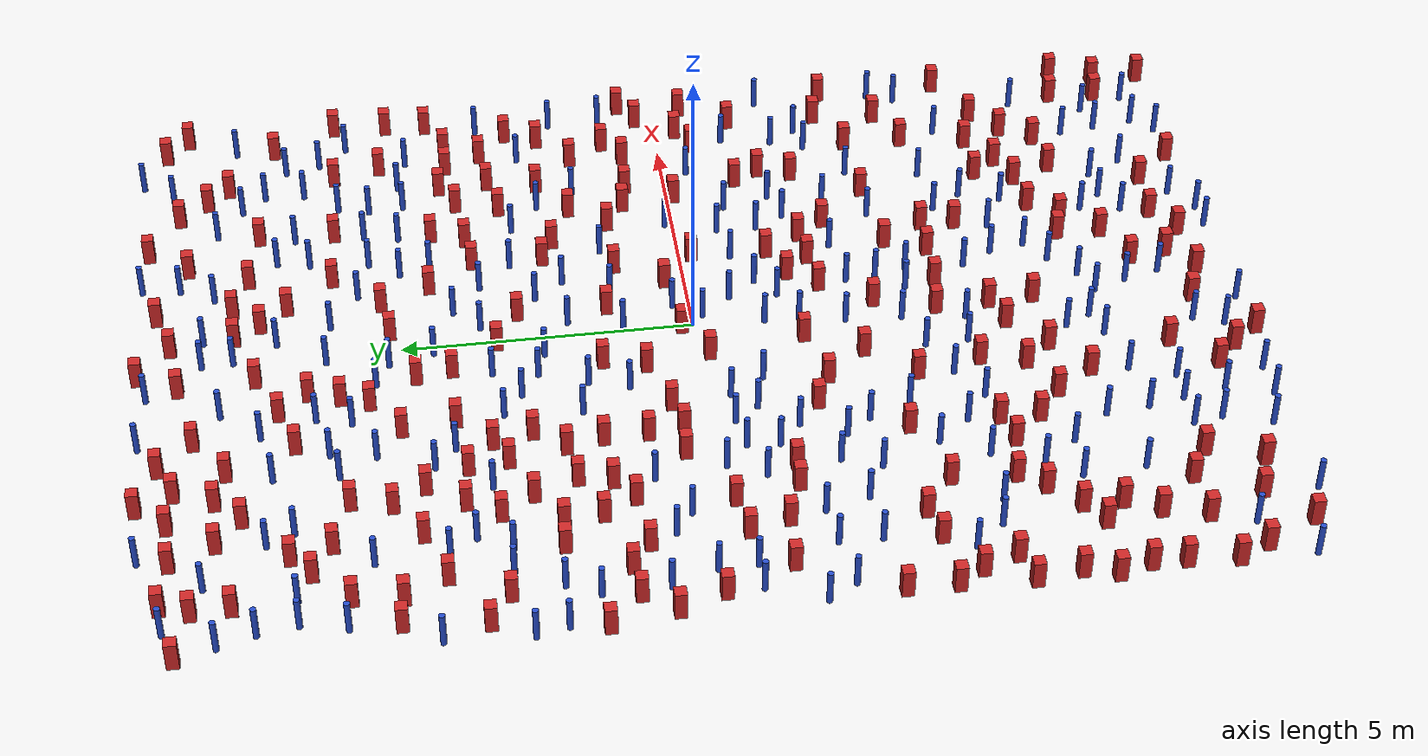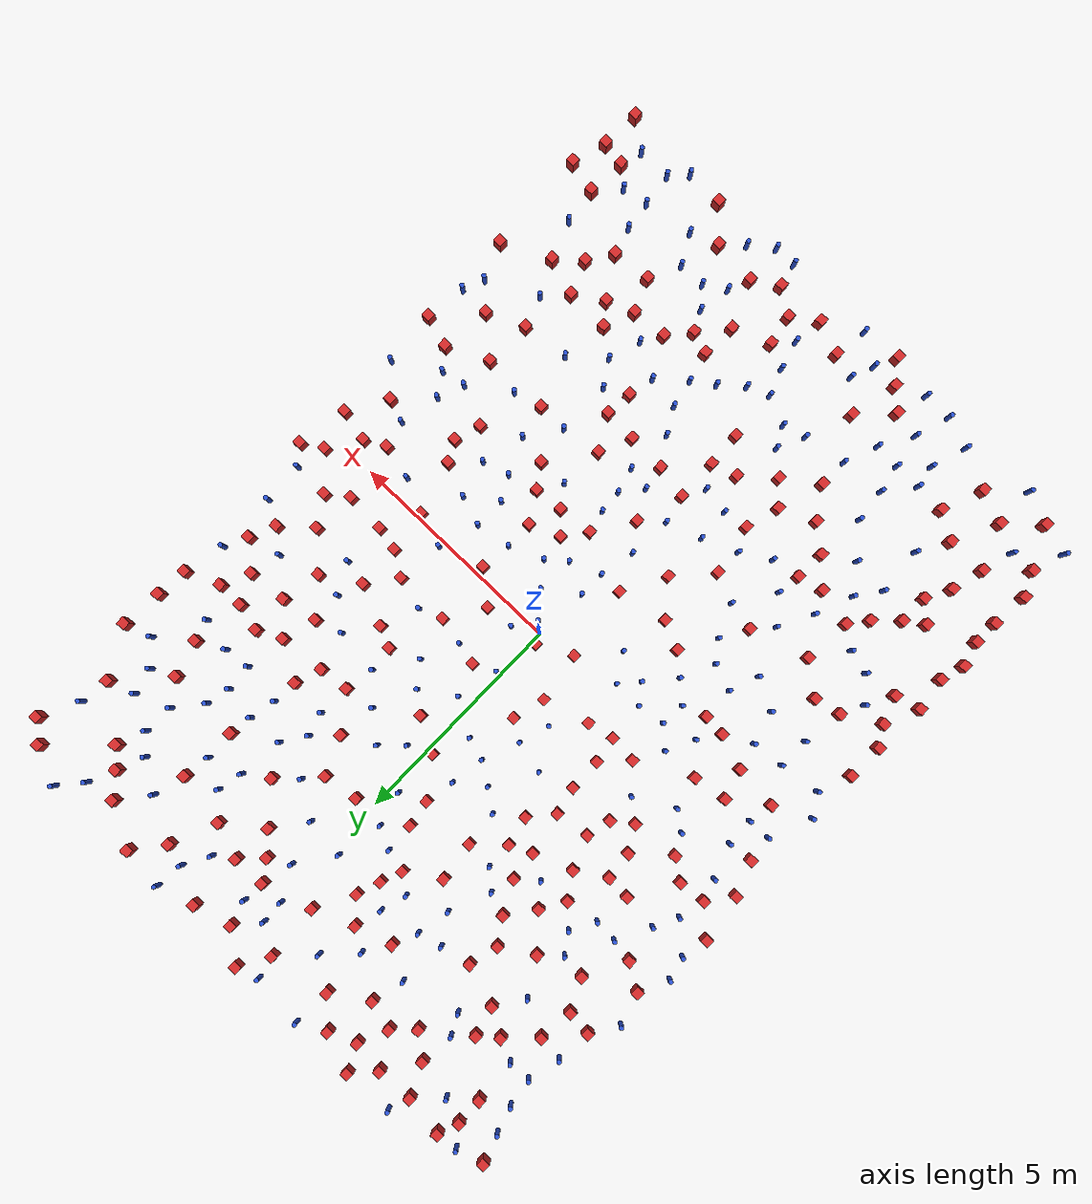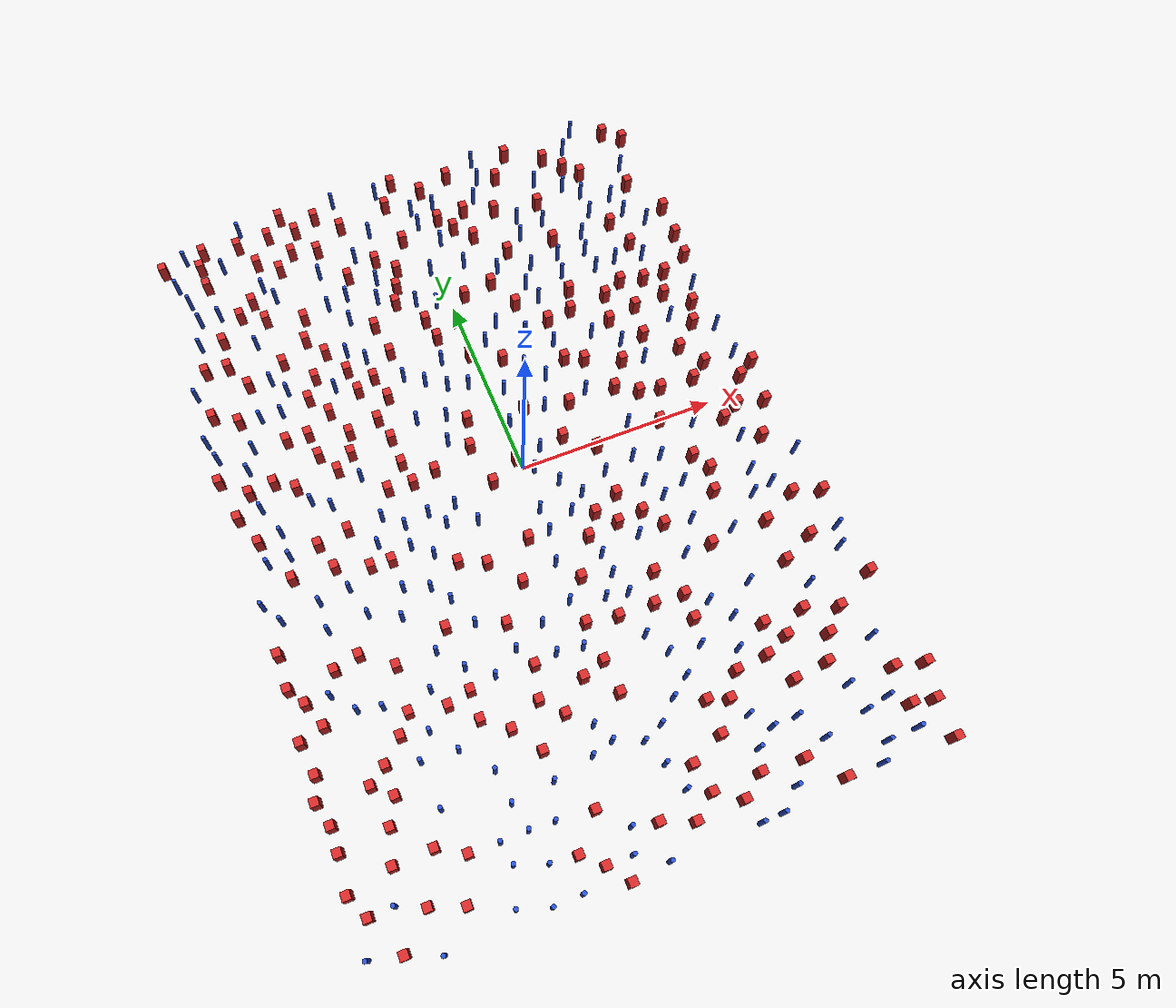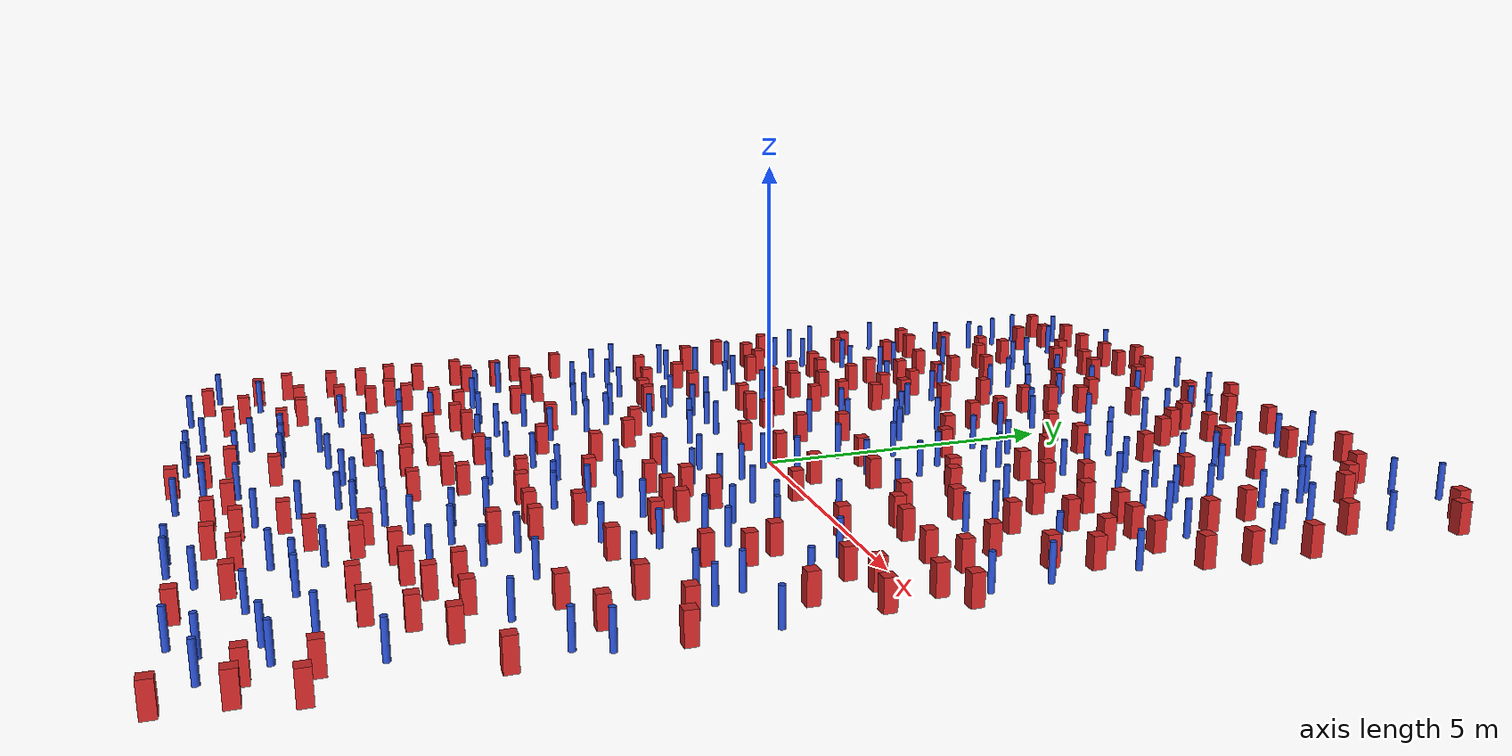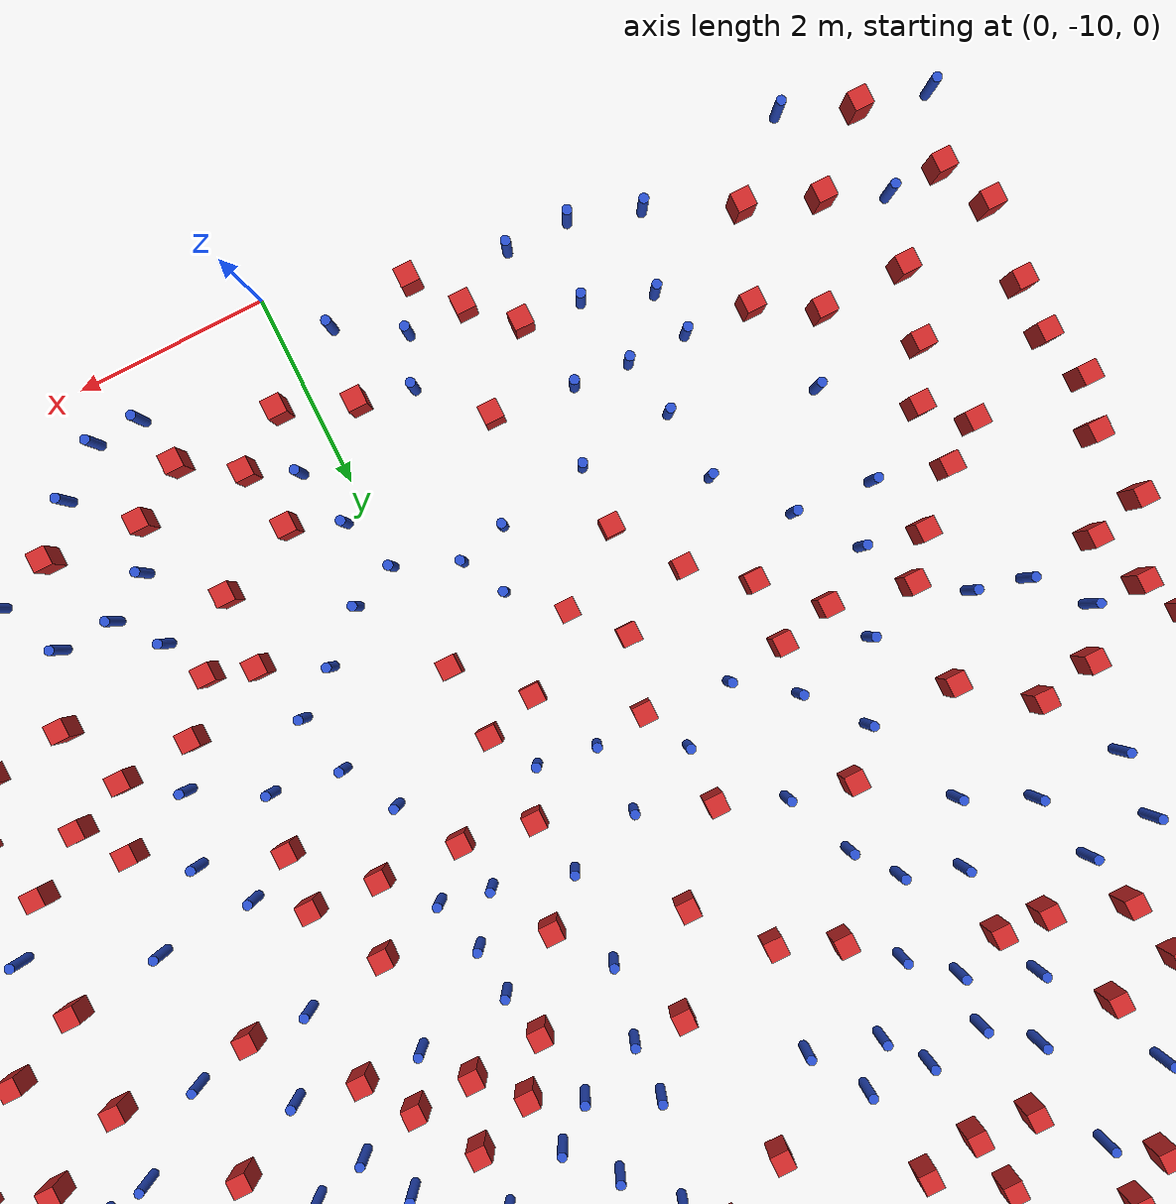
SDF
<sdf version="1.6">
  <model name="dense_12"><model name="square_post_obstacle0">
  <static>true</static>
  <pose frame="">-6.79365163109 -2.37966467392 -6.11067671241e-07 -5.50515727128e-06 -8.79689657224e-07 2.37013304536e-05</pose>
  <link name="link">
    <pose frame="">0 0 0.25 0 -0 0</pose>
    <inertial>
      <mass>100</mass>
      <inertia>
        <ixx>0.166667</ixx>
        <ixy>0</ixy>
        <ixz>0</ixz>
        <iyy>0.166667</iyy>
        <iyz>0</iyz>
        <izz>0.166667</izz>
      </inertia>
    </inertial>
    <collision name="collision">
      <geometry>
        <box>
          <size>.2 .2 .5</size>
        </box>
      </geometry>
      <max_contacts>10</max_contacts>
      <surface>
        <contact>
          <ode/>
        </contact>
        <bounce/>
        <friction>
          <torsional>
            <ode/>
          </torsional>
          <ode/>
        </friction>
      </surface>
    </collision>
    <visual name="visual">
      <geometry>
        <box>
          <size>.2 .2 .5</size>
        </box>
      </geometry>
      <material>
        <script>
          <name>Gazebo/Red</name>
          <uri>file://media/materials/scripts/gazebo.material</uri>
        </script>
      </material>
    </visual>
    <self_collide>0</self_collide>
    <kinematic>0</kinematic>
  </link>
</model>
<model name="square_post_obstacle1">
  <static>true</static>
  <pose frame="">3.60561085752 3.06510060845 -6.11067671241e-07 -5.50515727128e-06 -8.79689657224e-07 2.37013304536e-05</pose>
  <link name="link">
    <pose frame="">0 0 0.25 0 -0 0</pose>
    <inertial>
      <mass>100</mass>
      <inertia>
        <ixx>0.166667</ixx>
        <ixy>0</ixy>
        <ixz>0</ixz>
        <iyy>0.166667</iyy>
        <iyz>0</iyz>
        <izz>0.166667</izz>
      </inertia>
    </inertial>
    <collision name="collision">
      <geometry>
        <box>
          <size>.2 .2 .5</size>
        </box>
      </geometry>
      <max_contacts>10</max_contacts>
      <surface>
        <contact>
          <ode/>
        </contact>
        <bounce/>
        <friction>
          <torsional>
            <ode/>
          </torsional>
          <ode/>
        </friction>
      </surface>
    </collision>
    <visual name="visual">
      <geometry>
        <box>
          <size>.2 .2 .5</size>
        </box>
      </geometry>
      <material>
        <script>
          <name>Gazebo/Red</name>
          <uri>file://media/materials/scripts/gazebo.material</uri>
        </script>
      </material>
    </visual>
    <self_collide>0</self_collide>
    <kinematic>0</kinematic>
  </link>
</model>
<model name="pole_obstacle0">
  <static>true</static>
  <pose frame="">2.01684290447 2.99197757127 -9.47619616065e-06 5.49618799738e-07 2.36310414047e-07 -1.55090534808e-07</pose>
  <link name="link">
  <pose frame="">0 0 0.3 0 -0 0</pose>
    <inertial>
      <mass>1</mass>
      <inertia>
        <ixx>0.145833</ixx>
        <ixy>0</ixy>
        <ixz>0</ixz>
        <iyy>0.145833</iyy>
        <iyz>0</iyz>
        <izz>0.125</izz>
      </inertia>
    </inertial>
    <collision name="collision">
      <geometry>
        <cylinder>
          <radius>0.05</radius>
          <length>.6</length>
        </cylinder>
      </geometry>
      <max_contacts>10</max_contacts>
      <surface>
        <contact>
          <ode/>
        </contact>
        <bounce/>
        <friction>
          <torsional>
            <ode/>
          </torsional>
          <ode/>
        </friction>
      </surface>
    </collision>
    <visual name="visual">
      <geometry>
        <cylinder>
          <radius>0.05</radius>
          <length>.6</length>
        </cylinder>
      </geometry>
      <material>
        <script>
          <name>Gazebo/Blue</name>
          <uri>file://media/materials/scripts/gazebo.material</uri>
        </script>
      </material>
    </visual>
    <self_collide>0</self_collide>
    <kinematic>0</kinematic>
  </link>
</model>
<model name="square_post_obstacle2">
  <static>true</static>
  <pose frame="">-4.2392469503 -1.13895897655 -6.11067671241e-07 -5.50515727128e-06 -8.79689657224e-07 2.37013304536e-05</pose>
  <link name="link">
    <pose frame="">0 0 0.25 0 -0 0</pose>
    <inertial>
      <mass>100</mass>
      <inertia>
        <ixx>0.166667</ixx>
        <ixy>0</ixy>
        <ixz>0</ixz>
        <iyy>0.166667</iyy>
        <iyz>0</iyz>
        <izz>0.166667</izz>
      </inertia>
    </inertial>
    <collision name="collision">
      <geometry>
        <box>
          <size>.2 .2 .5</size>
        </box>
      </geometry>
      <max_contacts>10</max_contacts>
      <surface>
        <contact>
          <ode/>
        </contact>
        <bounce/>
        <friction>
          <torsional>
            <ode/>
          </torsional>
          <ode/>
        </friction>
      </surface>
    </collision>
    <visual name="visual">
      <geometry>
        <box>
          <size>.2 .2 .5</size>
        </box>
      </geometry>
      <material>
        <script>
          <name>Gazebo/Red</name>
          <uri>file://media/materials/scripts/gazebo.material</uri>
        </script>
      </material>
    </visual>
    <self_collide>0</self_collide>
    <kinematic>0</kinematic>
  </link>
</model>
<model name="pole_obstacle1">
  <static>true</static>
  <pose frame="">5.66179896076 -6.79059327364 -9.47619616065e-06 5.49618799737e-07 2.36310414037e-07 -1.55090534814e-07</pose>
  <link name="link">
  <pose frame="">0 0 0.3 0 -0 0</pose>
    <inertial>
      <mass>1</mass>
      <inertia>
        <ixx>0.145833</ixx>
        <ixy>0</ixy>
        <ixz>0</ixz>
        <iyy>0.145833</iyy>
        <iyz>0</iyz>
        <izz>0.125</izz>
      </inertia>
    </inertial>
    <collision name="collision">
      <geometry>
        <cylinder>
          <radius>0.05</radius>
          <length>.6</length>
        </cylinder>
      </geometry>
      <max_contacts>10</max_contacts>
      <surface>
        <contact>
          <ode/>
        </contact>
        <bounce/>
        <friction>
          <torsional>
            <ode/>
          </torsional>
          <ode/>
        </friction>
      </surface>
    </collision>
    <visual name="visual">
      <geometry>
        <cylinder>
          <radius>0.05</radius>
          <length>.6</length>
        </cylinder>
      </geometry>
      <material>
        <script>
          <name>Gazebo/Blue</name>
          <uri>file://media/materials/scripts/gazebo.material</uri>
        </script>
      </material>
    </visual>
    <self_collide>0</self_collide>
    <kinematic>0</kinematic>
  </link>
</model>
<model name="square_post_obstacle3">
  <static>true</static>
  <pose frame="">-3.91692092441 7.71348662594 -6.11067671241e-07 -5.50515727128e-06 -8.79689657224e-07 2.37013304536e-05</pose>
  <link name="link">
    <pose frame="">0 0 0.25 0 -0 0</pose>
    <inertial>
      <mass>100</mass>
      <inertia>
        <ixx>0.166667</ixx>
        <ixy>0</ixy>
        <ixz>0</ixz>
        <iyy>0.166667</iyy>
        <iyz>0</iyz>
        <izz>0.166667</izz>
      </inertia>
    </inertial>
    <collision name="collision">
      <geometry>
        <box>
          <size>.2 .2 .5</size>
        </box>
      </geometry>
      <max_contacts>10</max_contacts>
      <surface>
        <contact>
          <ode/>
        </contact>
        <bounce/>
        <friction>
          <torsional>
            <ode/>
          </torsional>
          <ode/>
        </friction>
      </surface>
    </collision>
    <visual name="visual">
      <geometry>
        <box>
          <size>.2 .2 .5</size>
        </box>
      </geometry>
      <material>
        <script>
          <name>Gazebo/Red</name>
          <uri>file://media/materials/scripts/gazebo.material</uri>
        </script>
      </material>
    </visual>
    <self_collide>0</self_collide>
    <kinematic>0</kinematic>
  </link>
</model>
<model name="pole_obstacle2">
  <static>true</static>
  <pose frame="">-1.79308534052 5.89661301325 -9.47619616065e-06 5.49618799737e-07 2.36310414061e-07 -1.550905348e-07</pose>
  <link name="link">
  <pose frame="">0 0 0.3 0 -0 0</pose>
    <inertial>
      <mass>1</mass>
      <inertia>
        <ixx>0.145833</ixx>
        <ixy>0</ixy>
        <ixz>0</ixz>
        <iyy>0.145833</iyy>
        <iyz>0</iyz>
        <izz>0.125</izz>
      </inertia>
    </inertial>
    <collision name="collision">
      <geometry>
        <cylinder>
          <radius>0.05</radius>
          <length>.6</length>
        </cylinder>
      </geometry>
      <max_contacts>10</max_contacts>
      <surface>
        <contact>
          <ode/>
        </contact>
        <bounce/>
        <friction>
          <torsional>
            <ode/>
          </torsional>
          <ode/>
        </friction>
      </surface>
    </collision>
    <visual name="visual">
      <geometry>
        <cylinder>
          <radius>0.05</radius>
          <length>.6</length>
        </cylinder>
      </geometry>
      <material>
        <script>
          <name>Gazebo/Blue</name>
          <uri>file://media/materials/scripts/gazebo.material</uri>
        </script>
      </material>
    </visual>
    <self_collide>0</self_collide>
    <kinematic>0</kinematic>
  </link>
</model>
<model name="pole_obstacle3">
  <static>true</static>
  <pose frame="">6.12126041712 1.92768375661 -9.47619616065e-06 5.49618799738e-07 2.36310414071e-07 -1.55090534796e-07</pose>
  <link name="link">
  <pose frame="">0 0 0.3 0 -0 0</pose>
    <inertial>
      <mass>1</mass>
      <inertia>
        <ixx>0.145833</ixx>
        <ixy>0</ixy>
        <ixz>0</ixz>
        <iyy>0.145833</iyy>
        <iyz>0</iyz>
        <izz>0.125</izz>
      </inertia>
    </inertial>
    <collision name="collision">
      <geometry>
        <cylinder>
          <radius>0.05</radius>
          <length>.6</length>
        </cylinder>
      </geometry>
      <max_contacts>10</max_contacts>
      <surface>
        <contact>
          <ode/>
        </contact>
        <bounce/>
        <friction>
          <torsional>
            <ode/>
          </torsional>
          <ode/>
        </friction>
      </surface>
    </collision>
    <visual name="visual">
      <geometry>
        <cylinder>
          <radius>0.05</radius>
          <length>.6</length>
        </cylinder>
      </geometry>
      <material>
        <script>
          <name>Gazebo/Blue</name>
          <uri>file://media/materials/scripts/gazebo.material</uri>
        </script>
      </material>
    </visual>
    <self_collide>0</self_collide>
    <kinematic>0</kinematic>
  </link>
</model>
<model name="square_post_obstacle4">
  <static>true</static>
  <pose frame="">-5.88233782899 6.05758240588 -6.11067671241e-07 -5.50515727128e-06 -8.79689657224e-07 2.37013304536e-05</pose>
  <link name="link">
    <pose frame="">0 0 0.25 0 -0 0</pose>
    <inertial>
      <mass>100</mass>
      <inertia>
        <ixx>0.166667</ixx>
        <ixy>0</ixy>
        <ixz>0</ixz>
        <iyy>0.166667</iyy>
        <iyz>0</iyz>
        <izz>0.166667</izz>
      </inertia>
    </inertial>
    <collision name="collision">
      <geometry>
        <box>
          <size>.2 .2 .5</size>
        </box>
      </geometry>
      <max_contacts>10</max_contacts>
      <surface>
        <contact>
          <ode/>
        </contact>
        <bounce/>
        <friction>
          <torsional>
            <ode/>
          </torsional>
          <ode/>
        </friction>
      </surface>
    </collision>
    <visual name="visual">
      <geometry>
        <box>
          <size>.2 .2 .5</size>
        </box>
      </geometry>
      <material>
        <script>
          <name>Gazebo/Red</name>
          <uri>file://media/materials/scripts/gazebo.material</uri>
        </script>
      </material>
    </visual>
    <self_collide>0</self_collide>
    <kinematic>0</kinematic>
  </link>
</model>
<model name="square_post_obstacle5">
  <static>true</static>
  <pose frame="">-0.597007786753 -1.81232864368 -6.11067671241e-07 -5.50515727128e-06 -8.79689657224e-07 2.37013304536e-05</pose>
  <link name="link">
    <pose frame="">0 0 0.25 0 -0 0</pose>
    <inertial>
      <mass>100</mass>
      <inertia>
        <ixx>0.166667</ixx>
        <ixy>0</ixy>
        <ixz>0</ixz>
        <iyy>0.166667</iyy>
        <iyz>0</iyz>
        <izz>0.166667</izz>
      </inertia>
    </inertial>
    <collision name="collision">
      <geometry>
        <box>
          <size>.2 .2 .5</size>
        </box>
      </geometry>
      <max_contacts>10</max_contacts>
      <surface>
        <contact>
          <ode/>
        </contact>
        <bounce/>
        <friction>
          <torsional>
            <ode/>
          </torsional>
          <ode/>
        </friction>
      </surface>
    </collision>
    <visual name="visual">
      <geometry>
        <box>
          <size>.2 .2 .5</size>
        </box>
      </geometry>
      <material>
        <script>
          <name>Gazebo/Red</name>
          <uri>file://media/materials/scripts/gazebo.material</uri>
        </script>
      </material>
    </visual>
    <self_collide>0</self_collide>
    <kinematic>0</kinematic>
  </link>
</model>
<model name="square_post_obstacle6">
  <static>true</static>
  <pose frame="">-5.84509082221 7.88563920167 -6.11067671241e-07 -5.50515727128e-06 -8.79689657224e-07 2.37013304536e-05</pose>
  <link name="link">
    <pose frame="">0 0 0.25 0 -0 0</pose>
    <inertial>
      <mass>100</mass>
      <inertia>
        <ixx>0.166667</ixx>
        <ixy>0</ixy>
        <ixz>0</ixz>
        <iyy>0.166667</iyy>
        <iyz>0</iyz>
        <izz>0.166667</izz>
      </inertia>
    </inertial>
    <collision name="collision">
      <geometry>
        <box>
          <size>.2 .2 .5</size>
        </box>
      </geometry>
      <max_contacts>10</max_contacts>
      <surface>
        <contact>
          <ode/>
        </contact>
        <bounce/>
        <friction>
          <torsional>
            <ode/>
          </torsional>
          <ode/>
        </friction>
      </surface>
    </collision>
    <visual name="visual">
      <geometry>
        <box>
          <size>.2 .2 .5</size>
        </box>
      </geometry>
      <material>
        <script>
          <name>Gazebo/Red</name>
          <uri>file://media/materials/scripts/gazebo.material</uri>
        </script>
      </material>
    </visual>
    <self_collide>0</self_collide>
    <kinematic>0</kinematic>
  </link>
</model>
<model name="pole_obstacle4">
  <static>true</static>
  <pose frame="">-5.58241695153 3.55196459856 -9.47619616065e-06 5.49618799738e-07 2.36310414051e-07 -1.55090534805e-07</pose>
  <link name="link">
  <pose frame="">0 0 0.3 0 -0 0</pose>
    <inertial>
      <mass>1</mass>
      <inertia>
        <ixx>0.145833</ixx>
        <ixy>0</ixy>
        <ixz>0</ixz>
        <iyy>0.145833</iyy>
        <iyz>0</iyz>
        <izz>0.125</izz>
      </inertia>
    </inertial>
    <collision name="collision">
      <geometry>
        <cylinder>
          <radius>0.05</radius>
          <length>.6</length>
        </cylinder>
      </geometry>
      <max_contacts>10</max_contacts>
      <surface>
        <contact>
          <ode/>
        </contact>
        <bounce/>
        <friction>
          <torsional>
            <ode/>
          </torsional>
          <ode/>
        </friction>
      </surface>
    </collision>
    <visual name="visual">
      <geometry>
        <cylinder>
          <radius>0.05</radius>
          <length>.6</length>
        </cylinder>
      </geometry>
      <material>
        <script>
          <name>Gazebo/Blue</name>
          <uri>file://media/materials/scripts/gazebo.material</uri>
        </script>
      </material>
    </visual>
    <self_collide>0</self_collide>
    <kinematic>0</kinematic>
  </link>
</model>
<model name="pole_obstacle5">
  <static>true</static>
  <pose frame="">2.66959242151 -7.77141818711 -9.47619616065e-06 5.49618799738e-07 2.3631041406e-07 -1.55090534801e-07</pose>
  <link name="link">
  <pose frame="">0 0 0.3 0 -0 0</pose>
    <inertial>
      <mass>1</mass>
      <inertia>
        <ixx>0.145833</ixx>
        <ixy>0</ixy>
        <ixz>0</ixz>
        <iyy>0.145833</iyy>
        <iyz>0</iyz>
        <izz>0.125</izz>
      </inertia>
    </inertial>
    <collision name="collision">
      <geometry>
        <cylinder>
          <radius>0.05</radius>
          <length>.6</length>
        </cylinder>
      </geometry>
      <max_contacts>10</max_contacts>
      <surface>
        <contact>
          <ode/>
        </contact>
        <bounce/>
        <friction>
          <torsional>
            <ode/>
          </torsional>
          <ode/>
        </friction>
      </surface>
    </collision>
    <visual name="visual">
      <geometry>
        <cylinder>
          <radius>0.05</radius>
          <length>.6</length>
        </cylinder>
      </geometry>
      <material>
        <script>
          <name>Gazebo/Blue</name>
          <uri>file://media/materials/scripts/gazebo.material</uri>
        </script>
      </material>
    </visual>
    <self_collide>0</self_collide>
    <kinematic>0</kinematic>
  </link>
</model>
<model name="square_post_obstacle7">
  <static>true</static>
  <pose frame="">-4.43367953176 -3.56172683347 -6.11067671241e-07 -5.50515727128e-06 -8.79689657224e-07 2.37013304536e-05</pose>
  <link name="link">
    <pose frame="">0 0 0.25 0 -0 0</pose>
    <inertial>
      <mass>100</mass>
      <inertia>
        <ixx>0.166667</ixx>
        <ixy>0</ixy>
        <ixz>0</ixz>
        <iyy>0.166667</iyy>
        <iyz>0</iyz>
        <izz>0.166667</izz>
      </inertia>
    </inertial>
    <collision name="collision">
      <geometry>
        <box>
          <size>.2 .2 .5</size>
        </box>
      </geometry>
      <max_contacts>10</max_contacts>
      <surface>
        <contact>
          <ode/>
        </contact>
        <bounce/>
        <friction>
          <torsional>
            <ode/>
          </torsional>
          <ode/>
        </friction>
      </surface>
    </collision>
    <visual name="visual">
      <geometry>
        <box>
          <size>.2 .2 .5</size>
        </box>
      </geometry>
      <material>
        <script>
          <name>Gazebo/Red</name>
          <uri>file://media/materials/scripts/gazebo.material</uri>
        </script>
      </material>
    </visual>
    <self_collide>0</self_collide>
    <kinematic>0</kinematic>
  </link>
</model>
<model name="square_post_obstacle8">
  <static>true</static>
  <pose frame="">4.80758696736 -6.39304158506 -6.11067671241e-07 -5.50515727128e-06 -8.79689657224e-07 2.37013304536e-05</pose>
  <link name="link">
    <pose frame="">0 0 0.25 0 -0 0</pose>
    <inertial>
      <mass>100</mass>
      <inertia>
        <ixx>0.166667</ixx>
        <ixy>0</ixy>
        <ixz>0</ixz>
        <iyy>0.166667</iyy>
        <iyz>0</iyz>
        <izz>0.166667</izz>
      </inertia>
    </inertial>
    <collision name="collision">
      <geometry>
        <box>
          <size>.2 .2 .5</size>
        </box>
      </geometry>
      <max_contacts>10</max_contacts>
      <surface>
        <contact>
          <ode/>
        </contact>
        <bounce/>
        <friction>
          <torsional>
            <ode/>
          </torsional>
          <ode/>
        </friction>
      </surface>
    </collision>
    <visual name="visual">
      <geometry>
        <box>
          <size>.2 .2 .5</size>
        </box>
      </geometry>
      <material>
        <script>
          <name>Gazebo/Red</name>
          <uri>file://media/materials/scripts/gazebo.material</uri>
        </script>
      </material>
    </visual>
    <self_collide>0</self_collide>
    <kinematic>0</kinematic>
  </link>
</model>
<model name="pole_obstacle6">
  <static>true</static>
  <pose frame="">-4.86197490382 -1.45907434639 -9.47619616065e-06 5.49618799738e-07 2.36310414071e-07 -1.55090534796e-07</pose>
  <link name="link">
  <pose frame="">0 0 0.3 0 -0 0</pose>
    <inertial>
      <mass>1</mass>
      <inertia>
        <ixx>0.145833</ixx>
        <ixy>0</ixy>
        <ixz>0</ixz>
        <iyy>0.145833</iyy>
        <iyz>0</iyz>
        <izz>0.125</izz>
      </inertia>
    </inertial>
    <collision name="collision">
      <geometry>
        <cylinder>
          <radius>0.05</radius>
          <length>.6</length>
        </cylinder>
      </geometry>
      <max_contacts>10</max_contacts>
      <surface>
        <contact>
          <ode/>
        </contact>
        <bounce/>
        <friction>
          <torsional>
            <ode/>
          </torsional>
          <ode/>
        </friction>
      </surface>
    </collision>
    <visual name="visual">
      <geometry>
        <cylinder>
          <radius>0.05</radius>
          <length>.6</length>
        </cylinder>
      </geometry>
      <material>
        <script>
          <name>Gazebo/Blue</name>
          <uri>file://media/materials/scripts/gazebo.material</uri>
        </script>
      </material>
    </visual>
    <self_collide>0</self_collide>
    <kinematic>0</kinematic>
  </link>
</model>
<model name="pole_obstacle7">
  <static>true</static>
  <pose frame="">0.609855262946 -1.5420359486 -9.47619616065e-06 5.49618799738e-07 2.36310414061e-07 -1.55090534801e-07</pose>
  <link name="link">
  <pose frame="">0 0 0.3 0 -0 0</pose>
    <inertial>
      <mass>1</mass>
      <inertia>
        <ixx>0.145833</ixx>
        <ixy>0</ixy>
        <ixz>0</ixz>
        <iyy>0.145833</iyy>
        <iyz>0</iyz>
        <izz>0.125</izz>
      </inertia>
    </inertial>
    <collision name="collision">
      <geometry>
        <cylinder>
          <radius>0.05</radius>
          <length>.6</length>
        </cylinder>
      </geometry>
      <max_contacts>10</max_contacts>
      <surface>
        <contact>
          <ode/>
        </contact>
        <bounce/>
        <friction>
          <torsional>
            <ode/>
          </torsional>
          <ode/>
        </friction>
      </surface>
    </collision>
    <visual name="visual">
      <geometry>
        <cylinder>
          <radius>0.05</radius>
          <length>.6</length>
        </cylinder>
      </geometry>
      <material>
        <script>
          <name>Gazebo/Blue</name>
          <uri>file://media/materials/scripts/gazebo.material</uri>
        </script>
      </material>
    </visual>
    <self_collide>0</self_collide>
    <kinematic>0</kinematic>
  </link>
</model>
<model name="square_post_obstacle9">
  <static>true</static>
  <pose frame="">6.23985523837 -8.52428699699 -6.11067671241e-07 -5.50515727128e-06 -8.79689657224e-07 2.37013304536e-05</pose>
  <link name="link">
    <pose frame="">0 0 0.25 0 -0 0</pose>
    <inertial>
      <mass>100</mass>
      <inertia>
        <ixx>0.166667</ixx>
        <ixy>0</ixy>
        <ixz>0</ixz>
        <iyy>0.166667</iyy>
        <iyz>0</iyz>
        <izz>0.166667</izz>
      </inertia>
    </inertial>
    <collision name="collision">
      <geometry>
        <box>
          <size>.2 .2 .5</size>
        </box>
      </geometry>
      <max_contacts>10</max_contacts>
      <surface>
        <contact>
          <ode/>
        </contact>
        <bounce/>
        <friction>
          <torsional>
            <ode/>
          </torsional>
          <ode/>
        </friction>
      </surface>
    </collision>
    <visual name="visual">
      <geometry>
        <box>
          <size>.2 .2 .5</size>
        </box>
      </geometry>
      <material>
        <script>
          <name>Gazebo/Red</name>
          <uri>file://media/materials/scripts/gazebo.material</uri>
        </script>
      </material>
    </visual>
    <self_collide>0</self_collide>
    <kinematic>0</kinematic>
  </link>
</model>
<model name="square_post_obstacle10">
  <static>true</static>
  <pose frame="">-3.74693229084 5.9982552937 -6.11067671241e-07 -5.50515727128e-06 -8.79689657224e-07 2.37013304536e-05</pose>
  <link name="link">
    <pose frame="">0 0 0.25 0 -0 0</pose>
    <inertial>
      <mass>100</mass>
      <inertia>
        <ixx>0.166667</ixx>
        <ixy>0</ixy>
        <ixz>0</ixz>
        <iyy>0.166667</iyy>
        <iyz>0</iyz>
        <izz>0.166667</izz>
      </inertia>
    </inertial>
    <collision name="collision">
      <geometry>
        <box>
          <size>.2 .2 .5</size>
        </box>
      </geometry>
      <max_contacts>10</max_contacts>
      <surface>
        <contact>
          <ode/>
        </contact>
        <bounce/>
        <friction>
          <torsional>
            <ode/>
          </torsional>
          <ode/>
        </friction>
      </surface>
    </collision>
    <visual name="visual">
      <geometry>
        <box>
          <size>.2 .2 .5</size>
        </box>
      </geometry>
      <material>
        <script>
          <name>Gazebo/Red</name>
          <uri>file://media/materials/scripts/gazebo.material</uri>
        </script>
      </material>
    </visual>
    <self_collide>0</self_collide>
    <kinematic>0</kinematic>
  </link>
</model>
<model name="square_post_obstacle11">
  <static>true</static>
  <pose frame="">0.307046380626 -8.9206067691 -6.11067671241e-07 -5.50515727128e-06 -8.79689657224e-07 2.37013304536e-05</pose>
  <link name="link">
    <pose frame="">0 0 0.25 0 -0 0</pose>
    <inertial>
      <mass>100</mass>
      <inertia>
        <ixx>0.166667</ixx>
        <ixy>0</ixy>
        <ixz>0</ixz>
        <iyy>0.166667</iyy>
        <iyz>0</iyz>
        <izz>0.166667</izz>
      </inertia>
    </inertial>
    <collision name="collision">
      <geometry>
        <box>
          <size>.2 .2 .5</size>
        </box>
      </geometry>
      <max_contacts>10</max_contacts>
      <surface>
        <contact>
          <ode/>
        </contact>
        <bounce/>
        <friction>
          <torsional>
            <ode/>
          </torsional>
          <ode/>
        </friction>
      </surface>
    </collision>
    <visual name="visual">
      <geometry>
        <box>
          <size>.2 .2 .5</size>
        </box>
      </geometry>
      <material>
        <script>
          <name>Gazebo/Red</name>
          <uri>file://media/materials/scripts/gazebo.material</uri>
        </script>
      </material>
    </visual>
    <self_collide>0</self_collide>
    <kinematic>0</kinematic>
  </link>
</model>
<model name="square_post_obstacle12">
  <static>true</static>
  <pose frame="">-4.83718442834 -5.03552390437 -6.11067671241e-07 -5.50515727128e-06 -8.79689657224e-07 2.37013304536e-05</pose>
  <link name="link">
    <pose frame="">0 0 0.25 0 -0 0</pose>
    <inertial>
      <mass>100</mass>
      <inertia>
        <ixx>0.166667</ixx>
        <ixy>0</ixy>
        <ixz>0</ixz>
        <iyy>0.166667</iyy>
        <iyz>0</iyz>
        <izz>0.166667</izz>
      </inertia>
    </inertial>
    <collision name="collision">
      <geometry>
        <box>
          <size>.2 .2 .5</size>
        </box>
      </geometry>
      <max_contacts>10</max_contacts>
      <surface>
        <contact>
          <ode/>
        </contact>
        <bounce/>
        <friction>
          <torsional>
            <ode/>
          </torsional>
          <ode/>
        </friction>
      </surface>
    </collision>
    <visual name="visual">
      <geometry>
        <box>
          <size>.2 .2 .5</size>
        </box>
      </geometry>
      <material>
        <script>
          <name>Gazebo/Red</name>
          <uri>file://media/materials/scripts/gazebo.material</uri>
        </script>
      </material>
    </visual>
    <self_collide>0</self_collide>
    <kinematic>0</kinematic>
  </link>
</model>
<model name="square_post_obstacle13">
  <static>true</static>
  <pose frame="">-0.0968748303471 0.21565951249 -6.11067671241e-07 -5.50515727128e-06 -8.79689657224e-07 2.37013304536e-05</pose>
  <link name="link">
    <pose frame="">0 0 0.25 0 -0 0</pose>
    <inertial>
      <mass>100</mass>
      <inertia>
        <ixx>0.166667</ixx>
        <ixy>0</ixy>
        <ixz>0</ixz>
        <iyy>0.166667</iyy>
        <iyz>0</iyz>
        <izz>0.166667</izz>
      </inertia>
    </inertial>
    <collision name="collision">
      <geometry>
        <box>
          <size>.2 .2 .5</size>
        </box>
      </geometry>
      <max_contacts>10</max_contacts>
      <surface>
        <contact>
          <ode/>
        </contact>
        <bounce/>
        <friction>
          <torsional>
            <ode/>
          </torsional>
          <ode/>
        </friction>
      </surface>
    </collision>
    <visual name="visual">
      <geometry>
        <box>
          <size>.2 .2 .5</size>
        </box>
      </geometry>
      <material>
        <script>
          <name>Gazebo/Red</name>
          <uri>file://media/materials/scripts/gazebo.material</uri>
        </script>
      </material>
    </visual>
    <self_collide>0</self_collide>
    <kinematic>0</kinematic>
  </link>
</model>
<model name="pole_obstacle8">
  <static>true</static>
  <pose frame="">4.32344856994 -0.441403326648 -9.47619616065e-06 5.49618799737e-07 2.36310414057e-07 -1.55090534802e-07</pose>
  <link name="link">
  <pose frame="">0 0 0.3 0 -0 0</pose>
    <inertial>
      <mass>1</mass>
      <inertia>
        <ixx>0.145833</ixx>
        <ixy>0</ixy>
        <ixz>0</ixz>
        <iyy>0.145833</iyy>
        <iyz>0</iyz>
        <izz>0.125</izz>
      </inertia>
    </inertial>
    <collision name="collision">
      <geometry>
        <cylinder>
          <radius>0.05</radius>
          <length>.6</length>
        </cylinder>
      </geometry>
      <max_contacts>10</max_contacts>
      <surface>
        <contact>
          <ode/>
        </contact>
        <bounce/>
        <friction>
          <torsional>
            <ode/>
          </torsional>
          <ode/>
        </friction>
      </surface>
    </collision>
    <visual name="visual">
      <geometry>
        <cylinder>
          <radius>0.05</radius>
          <length>.6</length>
        </cylinder>
      </geometry>
      <material>
        <script>
          <name>Gazebo/Blue</name>
          <uri>file://media/materials/scripts/gazebo.material</uri>
        </script>
      </material>
    </visual>
    <self_collide>0</self_collide>
    <kinematic>0</kinematic>
  </link>
</model>
<model name="square_post_obstacle14">
  <static>true</static>
  <pose frame="">1.17293309374 0.360948759211 -6.11067671241e-07 -5.50515727128e-06 -8.79689657224e-07 2.37013304536e-05</pose>
  <link name="link">
    <pose frame="">0 0 0.25 0 -0 0</pose>
    <inertial>
      <mass>100</mass>
      <inertia>
        <ixx>0.166667</ixx>
        <ixy>0</ixy>
        <ixz>0</ixz>
        <iyy>0.166667</iyy>
        <iyz>0</iyz>
        <izz>0.166667</izz>
      </inertia>
    </inertial>
    <collision name="collision">
      <geometry>
        <box>
          <size>.2 .2 .5</size>
        </box>
      </geometry>
      <max_contacts>10</max_contacts>
      <surface>
        <contact>
          <ode/>
        </contact>
        <bounce/>
        <friction>
          <torsional>
            <ode/>
          </torsional>
          <ode/>
        </friction>
      </surface>
    </collision>
    <visual name="visual">
      <geometry>
        <box>
          <size>.2 .2 .5</size>
        </box>
      </geometry>
      <material>
        <script>
          <name>Gazebo/Red</name>
          <uri>file://media/materials/scripts/gazebo.material</uri>
        </script>
      </material>
    </visual>
    <self_collide>0</self_collide>
    <kinematic>0</kinematic>
  </link>
</model>
<model name="square_post_obstacle15">
  <static>true</static>
  <pose frame="">0.376676240564 5.16645294007 -6.11067671241e-07 -5.50515727128e-06 -8.79689657224e-07 2.37013304536e-05</pose>
  <link name="link">
    <pose frame="">0 0 0.25 0 -0 0</pose>
    <inertial>
      <mass>100</mass>
      <inertia>
        <ixx>0.166667</ixx>
        <ixy>0</ixy>
        <ixz>0</ixz>
        <iyy>0.166667</iyy>
        <iyz>0</iyz>
        <izz>0.166667</izz>
      </inertia>
    </inertial>
    <collision name="collision">
      <geometry>
        <box>
          <size>.2 .2 .5</size>
        </box>
      </geometry>
      <max_contacts>10</max_contacts>
      <surface>
        <contact>
          <ode/>
        </contact>
        <bounce/>
        <friction>
          <torsional>
            <ode/>
          </torsional>
          <ode/>
        </friction>
      </surface>
    </collision>
    <visual name="visual">
      <geometry>
        <box>
          <size>.2 .2 .5</size>
        </box>
      </geometry>
      <material>
        <script>
          <name>Gazebo/Red</name>
          <uri>file://media/materials/scripts/gazebo.material</uri>
        </script>
      </material>
    </visual>
    <self_collide>0</self_collide>
    <kinematic>0</kinematic>
  </link>
</model>
<model name="square_post_obstacle16">
  <static>true</static>
  <pose frame="">-6.29992434716 -4.24559506503 -6.11067671241e-07 -5.50515727128e-06 -8.79689657224e-07 2.37013304536e-05</pose>
  <link name="link">
    <pose frame="">0 0 0.25 0 -0 0</pose>
    <inertial>
      <mass>100</mass>
      <inertia>
        <ixx>0.166667</ixx>
        <ixy>0</ixy>
        <ixz>0</ixz>
        <iyy>0.166667</iyy>
        <iyz>0</iyz>
        <izz>0.166667</izz>
      </inertia>
    </inertial>
    <collision name="collision">
      <geometry>
        <box>
          <size>.2 .2 .5</size>
        </box>
      </geometry>
      <max_contacts>10</max_contacts>
      <surface>
        <contact>
          <ode/>
        </contact>
        <bounce/>
        <friction>
          <torsional>
            <ode/>
          </torsional>
          <ode/>
        </friction>
      </surface>
    </collision>
    <visual name="visual">
      <geometry>
        <box>
          <size>.2 .2 .5</size>
        </box>
      </geometry>
      <material>
        <script>
          <name>Gazebo/Red</name>
          <uri>file://media/materials/scripts/gazebo.material</uri>
        </script>
      </material>
    </visual>
    <self_collide>0</self_collide>
    <kinematic>0</kinematic>
  </link>
</model>
<model name="pole_obstacle9">
  <static>true</static>
  <pose frame="">-0.22944135859 -2.60055739995 -9.4761961606e-06 5.49618799729e-07 2.36310413995e-07 -1.55090534826e-07</pose>
  <link name="link">
  <pose frame="">0 0 0.3 0 -0 0</pose>
    <inertial>
      <mass>1</mass>
      <inertia>
        <ixx>0.145833</ixx>
        <ixy>0</ixy>
        <ixz>0</ixz>
        <iyy>0.145833</iyy>
        <iyz>0</iyz>
        <izz>0.125</izz>
      </inertia>
    </inertial>
    <collision name="collision">
      <geometry>
        <cylinder>
          <radius>0.05</radius>
          <length>.6</length>
        </cylinder>
      </geometry>
      <max_contacts>10</max_contacts>
      <surface>
        <contact>
          <ode/>
        </contact>
        <bounce/>
        <friction>
          <torsional>
            <ode/>
          </torsional>
          <ode/>
        </friction>
      </surface>
    </collision>
    <visual name="visual">
      <geometry>
        <cylinder>
          <radius>0.05</radius>
          <length>.6</length>
        </cylinder>
      </geometry>
      <material>
        <script>
          <name>Gazebo/Blue</name>
          <uri>file://media/materials/scripts/gazebo.material</uri>
        </script>
      </material>
    </visual>
    <self_collide>0</self_collide>
    <kinematic>0</kinematic>
  </link>
</model>
<model name="square_post_obstacle17">
  <static>true</static>
  <pose frame="">-6.01088247387 -0.774021291029 -6.11067671241e-07 -5.50515727128e-06 -8.79689657224e-07 2.37013304536e-05</pose>
  <link name="link">
    <pose frame="">0 0 0.25 0 -0 0</pose>
    <inertial>
      <mass>100</mass>
      <inertia>
        <ixx>0.166667</ixx>
        <ixy>0</ixy>
        <ixz>0</ixz>
        <iyy>0.166667</iyy>
        <iyz>0</iyz>
        <izz>0.166667</izz>
      </inertia>
    </inertial>
    <collision name="collision">
      <geometry>
        <box>
          <size>.2 .2 .5</size>
        </box>
      </geometry>
      <max_contacts>10</max_contacts>
      <surface>
        <contact>
          <ode/>
        </contact>
        <bounce/>
        <friction>
          <torsional>
            <ode/>
          </torsional>
          <ode/>
        </friction>
      </surface>
    </collision>
    <visual name="visual">
      <geometry>
        <box>
          <size>.2 .2 .5</size>
        </box>
      </geometry>
      <material>
        <script>
          <name>Gazebo/Red</name>
          <uri>file://media/materials/scripts/gazebo.material</uri>
        </script>
      </material>
    </visual>
    <self_collide>0</self_collide>
    <kinematic>0</kinematic>
  </link>
</model>
<model name="square_post_obstacle18">
  <static>true</static>
  <pose frame="">-0.0803372727893 -5.90458669172 -6.11067671241e-07 -5.50515727128e-06 -8.79689657224e-07 2.37013304536e-05</pose>
  <link name="link">
    <pose frame="">0 0 0.25 0 -0 0</pose>
    <inertial>
      <mass>100</mass>
      <inertia>
        <ixx>0.166667</ixx>
        <ixy>0</ixy>
        <ixz>0</ixz>
        <iyy>0.166667</iyy>
        <iyz>0</iyz>
        <izz>0.166667</izz>
      </inertia>
    </inertial>
    <collision name="collision">
      <geometry>
        <box>
          <size>.2 .2 .5</size>
        </box>
      </geometry>
      <max_contacts>10</max_contacts>
      <surface>
        <contact>
          <ode/>
        </contact>
        <bounce/>
        <friction>
          <torsional>
            <ode/>
          </torsional>
          <ode/>
        </friction>
      </surface>
    </collision>
    <visual name="visual">
      <geometry>
        <box>
          <size>.2 .2 .5</size>
        </box>
      </geometry>
      <material>
        <script>
          <name>Gazebo/Red</name>
          <uri>file://media/materials/scripts/gazebo.material</uri>
        </script>
      </material>
    </visual>
    <self_collide>0</self_collide>
    <kinematic>0</kinematic>
  </link>
</model>
<model name="pole_obstacle10">
  <static>true</static>
  <pose frame="">6.1121748208 3.30168363211 -9.47619616065e-06 5.49618799738e-07 2.36310414051e-07 -1.55090534805e-07</pose>
  <link name="link">
  <pose frame="">0 0 0.3 0 -0 0</pose>
    <inertial>
      <mass>1</mass>
      <inertia>
        <ixx>0.145833</ixx>
        <ixy>0</ixy>
        <ixz>0</ixz>
        <iyy>0.145833</iyy>
        <iyz>0</iyz>
        <izz>0.125</izz>
      </inertia>
    </inertial>
    <collision name="collision">
      <geometry>
        <cylinder>
          <radius>0.05</radius>
          <length>.6</length>
        </cylinder>
      </geometry>
      <max_contacts>10</max_contacts>
      <surface>
        <contact>
          <ode/>
        </contact>
        <bounce/>
        <friction>
          <torsional>
            <ode/>
          </torsional>
          <ode/>
        </friction>
      </surface>
    </collision>
    <visual name="visual">
      <geometry>
        <cylinder>
          <radius>0.05</radius>
          <length>.6</length>
        </cylinder>
      </geometry>
      <material>
        <script>
          <name>Gazebo/Blue</name>
          <uri>file://media/materials/scripts/gazebo.material</uri>
        </script>
      </material>
    </visual>
    <self_collide>0</self_collide>
    <kinematic>0</kinematic>
  </link>
</model>
<model name="square_post_obstacle19">
  <static>true</static>
  <pose frame="">-6.87318926064 -4.40317310177 -6.11067671241e-07 -5.50515727128e-06 -8.79689657224e-07 2.37013304536e-05</pose>
  <link name="link">
    <pose frame="">0 0 0.25 0 -0 0</pose>
    <inertial>
      <mass>100</mass>
      <inertia>
        <ixx>0.166667</ixx>
        <ixy>0</ixy>
        <ixz>0</ixz>
        <iyy>0.166667</iyy>
        <iyz>0</iyz>
        <izz>0.166667</izz>
      </inertia>
    </inertial>
    <collision name="collision">
      <geometry>
        <box>
          <size>.2 .2 .5</size>
        </box>
      </geometry>
      <max_contacts>10</max_contacts>
      <surface>
        <contact>
          <ode/>
        </contact>
        <bounce/>
        <friction>
          <torsional>
            <ode/>
          </torsional>
          <ode/>
        </friction>
      </surface>
    </collision>
    <visual name="visual">
      <geometry>
        <box>
          <size>.2 .2 .5</size>
        </box>
      </geometry>
      <material>
        <script>
          <name>Gazebo/Red</name>
          <uri>file://media/materials/scripts/gazebo.material</uri>
        </script>
      </material>
    </visual>
    <self_collide>0</self_collide>
    <kinematic>0</kinematic>
  </link>
</model>
<model name="pole_obstacle11">
  <static>true</static>
  <pose frame="">-6.46527791398 6.12878476912 -9.47619616065e-06 5.49618799737e-07 2.36310414037e-07 -1.55090534814e-07</pose>
  <link name="link">
  <pose frame="">0 0 0.3 0 -0 0</pose>
    <inertial>
      <mass>1</mass>
      <inertia>
        <ixx>0.145833</ixx>
        <ixy>0</ixy>
        <ixz>0</ixz>
        <iyy>0.145833</iyy>
        <iyz>0</iyz>
        <izz>0.125</izz>
      </inertia>
    </inertial>
    <collision name="collision">
      <geometry>
        <cylinder>
          <radius>0.05</radius>
          <length>.6</length>
        </cylinder>
      </geometry>
      <max_contacts>10</max_contacts>
      <surface>
        <contact>
          <ode/>
        </contact>
        <bounce/>
        <friction>
          <torsional>
            <ode/>
          </torsional>
          <ode/>
        </friction>
      </surface>
    </collision>
    <visual name="visual">
      <geometry>
        <cylinder>
          <radius>0.05</radius>
          <length>.6</length>
        </cylinder>
      </geometry>
      <material>
        <script>
          <name>Gazebo/Blue</name>
          <uri>file://media/materials/scripts/gazebo.material</uri>
        </script>
      </material>
    </visual>
    <self_collide>0</self_collide>
    <kinematic>0</kinematic>
  </link>
</model>
<model name="square_post_obstacle20">
  <static>true</static>
  <pose frame="">-2.63922978032 0.517504427123 -6.11067671241e-07 -5.50515727128e-06 -8.79689657224e-07 2.37013304536e-05</pose>
  <link name="link">
    <pose frame="">0 0 0.25 0 -0 0</pose>
    <inertial>
      <mass>100</mass>
      <inertia>
        <ixx>0.166667</ixx>
        <ixy>0</ixy>
        <ixz>0</ixz>
        <iyy>0.166667</iyy>
        <iyz>0</iyz>
        <izz>0.166667</izz>
      </inertia>
    </inertial>
    <collision name="collision">
      <geometry>
        <box>
          <size>.2 .2 .5</size>
        </box>
      </geometry>
      <max_contacts>10</max_contacts>
      <surface>
        <contact>
          <ode/>
        </contact>
        <bounce/>
        <friction>
          <torsional>
            <ode/>
          </torsional>
          <ode/>
        </friction>
      </surface>
    </collision>
    <visual name="visual">
      <geometry>
        <box>
          <size>.2 .2 .5</size>
        </box>
      </geometry>
      <material>
        <script>
          <name>Gazebo/Red</name>
          <uri>file://media/materials/scripts/gazebo.material</uri>
        </script>
      </material>
    </visual>
    <self_collide>0</self_collide>
    <kinematic>0</kinematic>
  </link>
</model>
<model name="pole_obstacle12">
  <static>true</static>
  <pose frame="">-2.7788089134 -1.38238194871 -9.47619616065e-06 5.49618799737e-07 2.36310414072e-07 -1.55090534793e-07</pose>
  <link name="link">
  <pose frame="">0 0 0.3 0 -0 0</pose>
    <inertial>
      <mass>1</mass>
      <inertia>
        <ixx>0.145833</ixx>
        <ixy>0</ixy>
        <ixz>0</ixz>
        <iyy>0.145833</iyy>
        <iyz>0</iyz>
        <izz>0.125</izz>
      </inertia>
    </inertial>
    <collision name="collision">
      <geometry>
        <cylinder>
          <radius>0.05</radius>
          <length>.6</length>
        </cylinder>
      </geometry>
      <max_contacts>10</max_contacts>
      <surface>
        <contact>
          <ode/>
        </contact>
        <bounce/>
        <friction>
          <torsional>
            <ode/>
          </torsional>
          <ode/>
        </friction>
      </surface>
    </collision>
    <visual name="visual">
      <geometry>
        <cylinder>
          <radius>0.05</radius>
          <length>.6</length>
        </cylinder>
      </geometry>
      <material>
        <script>
          <name>Gazebo/Blue</name>
          <uri>file://media/materials/scripts/gazebo.material</uri>
        </script>
      </material>
    </visual>
    <self_collide>0</self_collide>
    <kinematic>0</kinematic>
  </link>
</model>
<model name="square_post_obstacle21">
  <static>true</static>
  <pose frame="">2.07038140015 2.41308263404 -6.11067671241e-07 -5.50515727128e-06 -8.79689657224e-07 2.37013304536e-05</pose>
  <link name="link">
    <pose frame="">0 0 0.25 0 -0 0</pose>
    <inertial>
      <mass>100</mass>
      <inertia>
        <ixx>0.166667</ixx>
        <ixy>0</ixy>
        <ixz>0</ixz>
        <iyy>0.166667</iyy>
        <iyz>0</iyz>
        <izz>0.166667</izz>
      </inertia>
    </inertial>
    <collision name="collision">
      <geometry>
        <box>
          <size>.2 .2 .5</size>
        </box>
      </geometry>
      <max_contacts>10</max_contacts>
      <surface>
        <contact>
          <ode/>
        </contact>
        <bounce/>
        <friction>
          <torsional>
            <ode/>
          </torsional>
          <ode/>
        </friction>
      </surface>
    </collision>
    <visual name="visual">
      <geometry>
        <box>
          <size>.2 .2 .5</size>
        </box>
      </geometry>
      <material>
        <script>
          <name>Gazebo/Red</name>
          <uri>file://media/materials/scripts/gazebo.material</uri>
        </script>
      </material>
    </visual>
    <self_collide>0</self_collide>
    <kinematic>0</kinematic>
  </link>
</model>
<model name="pole_obstacle13">
  <static>true</static>
  <pose frame="">-5.0503495889 0.949455976347 -9.47619616065e-06 5.49618799737e-07 2.36310414061e-07 -1.550905348e-07</pose>
  <link name="link">
  <pose frame="">0 0 0.3 0 -0 0</pose>
    <inertial>
      <mass>1</mass>
      <inertia>
        <ixx>0.145833</ixx>
        <ixy>0</ixy>
        <ixz>0</ixz>
        <iyy>0.145833</iyy>
        <iyz>0</iyz>
        <izz>0.125</izz>
      </inertia>
    </inertial>
    <collision name="collision">
      <geometry>
        <cylinder>
          <radius>0.05</radius>
          <length>.6</length>
        </cylinder>
      </geometry>
      <max_contacts>10</max_contacts>
      <surface>
        <contact>
          <ode/>
        </contact>
        <bounce/>
        <friction>
          <torsional>
            <ode/>
          </torsional>
          <ode/>
        </friction>
      </surface>
    </collision>
    <visual name="visual">
      <geometry>
        <cylinder>
          <radius>0.05</radius>
          <length>.6</length>
        </cylinder>
      </geometry>
      <material>
        <script>
          <name>Gazebo/Blue</name>
          <uri>file://media/materials/scripts/gazebo.material</uri>
        </script>
      </material>
    </visual>
    <self_collide>0</self_collide>
    <kinematic>0</kinematic>
  </link>
</model>
<model name="square_post_obstacle22">
  <static>true</static>
  <pose frame="">-2.00911658762 8.48687081299 -6.11067671241e-07 -5.50515727128e-06 -8.79689657224e-07 2.37013304536e-05</pose>
  <link name="link">
    <pose frame="">0 0 0.25 0 -0 0</pose>
    <inertial>
      <mass>100</mass>
      <inertia>
        <ixx>0.166667</ixx>
        <ixy>0</ixy>
        <ixz>0</ixz>
        <iyy>0.166667</iyy>
        <iyz>0</iyz>
        <izz>0.166667</izz>
      </inertia>
    </inertial>
    <collision name="collision">
      <geometry>
        <box>
          <size>.2 .2 .5</size>
        </box>
      </geometry>
      <max_contacts>10</max_contacts>
      <surface>
        <contact>
          <ode/>
        </contact>
        <bounce/>
        <friction>
          <torsional>
            <ode/>
          </torsional>
          <ode/>
        </friction>
      </surface>
    </collision>
    <visual name="visual">
      <geometry>
        <box>
          <size>.2 .2 .5</size>
        </box>
      </geometry>
      <material>
        <script>
          <name>Gazebo/Red</name>
          <uri>file://media/materials/scripts/gazebo.material</uri>
        </script>
      </material>
    </visual>
    <self_collide>0</self_collide>
    <kinematic>0</kinematic>
  </link>
</model>
<model name="pole_obstacle14">
  <static>true</static>
  <pose frame="">-3.61705896451 3.72201527648 -9.47619616065e-06 5.49618799737e-07 2.36310414067e-07 -1.55090534797e-07</pose>
  <link name="link">
  <pose frame="">0 0 0.3 0 -0 0</pose>
    <inertial>
      <mass>1</mass>
      <inertia>
        <ixx>0.145833</ixx>
        <ixy>0</ixy>
        <ixz>0</ixz>
        <iyy>0.145833</iyy>
        <iyz>0</iyz>
        <izz>0.125</izz>
      </inertia>
    </inertial>
    <collision name="collision">
      <geometry>
        <cylinder>
          <radius>0.05</radius>
          <length>.6</length>
        </cylinder>
      </geometry>
      <max_contacts>10</max_contacts>
      <surface>
        <contact>
          <ode/>
        </contact>
        <bounce/>
        <friction>
          <torsional>
            <ode/>
          </torsional>
          <ode/>
        </friction>
      </surface>
    </collision>
    <visual name="visual">
      <geometry>
        <cylinder>
          <radius>0.05</radius>
          <length>.6</length>
        </cylinder>
      </geometry>
      <material>
        <script>
          <name>Gazebo/Blue</name>
          <uri>file://media/materials/scripts/gazebo.material</uri>
        </script>
      </material>
    </visual>
    <self_collide>0</self_collide>
    <kinematic>0</kinematic>
  </link>
</model>
<model name="pole_obstacle15">
  <static>true</static>
  <pose frame="">-0.46060873047 2.60166311697 -9.47619616065e-06 5.49618799737e-07 2.36310414073e-07 -1.55090534793e-07</pose>
  <link name="link">
  <pose frame="">0 0 0.3 0 -0 0</pose>
    <inertial>
      <mass>1</mass>
      <inertia>
        <ixx>0.145833</ixx>
        <ixy>0</ixy>
        <ixz>0</ixz>
        <iyy>0.145833</iyy>
        <iyz>0</iyz>
        <izz>0.125</izz>
      </inertia>
    </inertial>
    <collision name="collision">
      <geometry>
        <cylinder>
          <radius>0.05</radius>
          <length>.6</length>
        </cylinder>
      </geometry>
      <max_contacts>10</max_contacts>
      <surface>
        <contact>
          <ode/>
        </contact>
        <bounce/>
        <friction>
          <torsional>
            <ode/>
          </torsional>
          <ode/>
        </friction>
      </surface>
    </collision>
    <visual name="visual">
      <geometry>
        <cylinder>
          <radius>0.05</radius>
          <length>.6</length>
        </cylinder>
      </geometry>
      <material>
        <script>
          <name>Gazebo/Blue</name>
          <uri>file://media/materials/scripts/gazebo.material</uri>
        </script>
      </material>
    </visual>
    <self_collide>0</self_collide>
    <kinematic>0</kinematic>
  </link>
</model>
<model name="pole_obstacle16">
  <static>true</static>
  <pose frame="">-3.03292474364 -4.14397982921 -9.47619616065e-06 5.49618799738e-07 2.3631041406e-07 -1.55090534801e-07</pose>
  <link name="link">
  <pose frame="">0 0 0.3 0 -0 0</pose>
    <inertial>
      <mass>1</mass>
      <inertia>
        <ixx>0.145833</ixx>
        <ixy>0</ixy>
        <ixz>0</ixz>
        <iyy>0.145833</iyy>
        <iyz>0</iyz>
        <izz>0.125</izz>
      </inertia>
    </inertial>
    <collision name="collision">
      <geometry>
        <cylinder>
          <radius>0.05</radius>
          <length>.6</length>
        </cylinder>
      </geometry>
      <max_contacts>10</max_contacts>
      <surface>
        <contact>
          <ode/>
        </contact>
        <bounce/>
        <friction>
          <torsional>
            <ode/>
          </torsional>
          <ode/>
        </friction>
      </surface>
    </collision>
    <visual name="visual">
      <geometry>
        <cylinder>
          <radius>0.05</radius>
          <length>.6</length>
        </cylinder>
      </geometry>
      <material>
        <script>
          <name>Gazebo/Blue</name>
          <uri>file://media/materials/scripts/gazebo.material</uri>
        </script>
      </material>
    </visual>
    <self_collide>0</self_collide>
    <kinematic>0</kinematic>
  </link>
</model>
<model name="square_post_obstacle23">
  <static>true</static>
  <pose frame="">-1.46489384743 7.0902224017 -6.11067671241e-07 -5.50515727128e-06 -8.79689657224e-07 2.37013304536e-05</pose>
  <link name="link">
    <pose frame="">0 0 0.25 0 -0 0</pose>
    <inertial>
      <mass>100</mass>
      <inertia>
        <ixx>0.166667</ixx>
        <ixy>0</ixy>
        <ixz>0</ixz>
        <iyy>0.166667</iyy>
        <iyz>0</iyz>
        <izz>0.166667</izz>
      </inertia>
    </inertial>
    <collision name="collision">
      <geometry>
        <box>
          <size>.2 .2 .5</size>
        </box>
      </geometry>
      <max_contacts>10</max_contacts>
      <surface>
        <contact>
          <ode/>
        </contact>
        <bounce/>
        <friction>
          <torsional>
            <ode/>
          </torsional>
          <ode/>
        </friction>
      </surface>
    </collision>
    <visual name="visual">
      <geometry>
        <box>
          <size>.2 .2 .5</size>
        </box>
      </geometry>
      <material>
        <script>
          <name>Gazebo/Red</name>
          <uri>file://media/materials/scripts/gazebo.material</uri>
        </script>
      </material>
    </visual>
    <self_collide>0</self_collide>
    <kinematic>0</kinematic>
  </link>
</model>
<model name="pole_obstacle17">
  <static>true</static>
  <pose frame="">2.04898623751 8.7162139419 -9.4761961606e-06 5.49618799729e-07 2.36310414007e-07 -1.5509053482e-07</pose>
  <link name="link">
  <pose frame="">0 0 0.3 0 -0 0</pose>
    <inertial>
      <mass>1</mass>
      <inertia>
        <ixx>0.145833</ixx>
        <ixy>0</ixy>
        <ixz>0</ixz>
        <iyy>0.145833</iyy>
        <iyz>0</iyz>
        <izz>0.125</izz>
      </inertia>
    </inertial>
    <collision name="collision">
      <geometry>
        <cylinder>
          <radius>0.05</radius>
          <length>.6</length>
        </cylinder>
      </geometry>
      <max_contacts>10</max_contacts>
      <surface>
        <contact>
          <ode/>
        </contact>
        <bounce/>
        <friction>
          <torsional>
            <ode/>
          </torsional>
          <ode/>
        </friction>
      </surface>
    </collision>
    <visual name="visual">
      <geometry>
        <cylinder>
          <radius>0.05</radius>
          <length>.6</length>
        </cylinder>
      </geometry>
      <material>
        <script>
          <name>Gazebo/Blue</name>
          <uri>file://media/materials/scripts/gazebo.material</uri>
        </script>
      </material>
    </visual>
    <self_collide>0</self_collide>
    <kinematic>0</kinematic>
  </link>
</model>
<model name="square_post_obstacle24">
  <static>true</static>
  <pose frame="">2.78826813013 3.72345648969 -6.11067671241e-07 -5.50515727128e-06 -8.79689657224e-07 2.37013304536e-05</pose>
  <link name="link">
    <pose frame="">0 0 0.25 0 -0 0</pose>
    <inertial>
      <mass>100</mass>
      <inertia>
        <ixx>0.166667</ixx>
        <ixy>0</ixy>
        <ixz>0</ixz>
        <iyy>0.166667</iyy>
        <iyz>0</iyz>
        <izz>0.166667</izz>
      </inertia>
    </inertial>
    <collision name="collision">
      <geometry>
        <box>
          <size>.2 .2 .5</size>
        </box>
      </geometry>
      <max_contacts>10</max_contacts>
      <surface>
        <contact>
          <ode/>
        </contact>
        <bounce/>
        <friction>
          <torsional>
            <ode/>
          </torsional>
          <ode/>
        </friction>
      </surface>
    </collision>
    <visual name="visual">
      <geometry>
        <box>
          <size>.2 .2 .5</size>
        </box>
      </geometry>
      <material>
        <script>
          <name>Gazebo/Red</name>
          <uri>file://media/materials/scripts/gazebo.material</uri>
        </script>
      </material>
    </visual>
    <self_collide>0</self_collide>
    <kinematic>0</kinematic>
  </link>
</model>
<model name="square_post_obstacle25">
  <static>true</static>
  <pose frame="">6.38921994989 -5.43267940847 -6.11067671241e-07 -5.50515727128e-06 -8.79689657224e-07 2.37013304536e-05</pose>
  <link name="link">
    <pose frame="">0 0 0.25 0 -0 0</pose>
    <inertial>
      <mass>100</mass>
      <inertia>
        <ixx>0.166667</ixx>
        <ixy>0</ixy>
        <ixz>0</ixz>
        <iyy>0.166667</iyy>
        <iyz>0</iyz>
        <izz>0.166667</izz>
      </inertia>
    </inertial>
    <collision name="collision">
      <geometry>
        <box>
          <size>.2 .2 .5</size>
        </box>
      </geometry>
      <max_contacts>10</max_contacts>
      <surface>
        <contact>
          <ode/>
        </contact>
        <bounce/>
        <friction>
          <torsional>
            <ode/>
          </torsional>
          <ode/>
        </friction>
      </surface>
    </collision>
    <visual name="visual">
      <geometry>
        <box>
          <size>.2 .2 .5</size>
        </box>
      </geometry>
      <material>
        <script>
          <name>Gazebo/Red</name>
          <uri>file://media/materials/scripts/gazebo.material</uri>
        </script>
      </material>
    </visual>
    <self_collide>0</self_collide>
    <kinematic>0</kinematic>
  </link>
</model>
<model name="square_post_obstacle26">
  <static>true</static>
  <pose frame="">-1.5846080615 -4.65610966505 -6.11067671241e-07 -5.50515727128e-06 -8.79689657224e-07 2.37013304536e-05</pose>
  <link name="link">
    <pose frame="">0 0 0.25 0 -0 0</pose>
    <inertial>
      <mass>100</mass>
      <inertia>
        <ixx>0.166667</ixx>
        <ixy>0</ixy>
        <ixz>0</ixz>
        <iyy>0.166667</iyy>
        <iyz>0</iyz>
        <izz>0.166667</izz>
      </inertia>
    </inertial>
    <collision name="collision">
      <geometry>
        <box>
          <size>.2 .2 .5</size>
        </box>
      </geometry>
      <max_contacts>10</max_contacts>
      <surface>
        <contact>
          <ode/>
        </contact>
        <bounce/>
        <friction>
          <torsional>
            <ode/>
          </torsional>
          <ode/>
        </friction>
      </surface>
    </collision>
    <visual name="visual">
      <geometry>
        <box>
          <size>.2 .2 .5</size>
        </box>
      </geometry>
      <material>
        <script>
          <name>Gazebo/Red</name>
          <uri>file://media/materials/scripts/gazebo.material</uri>
        </script>
      </material>
    </visual>
    <self_collide>0</self_collide>
    <kinematic>0</kinematic>
  </link>
</model>
<model name="square_post_obstacle27">
  <static>true</static>
  <pose frame="">1.27030081511 9.11007338027 -6.11067671241e-07 -5.50515727128e-06 -8.79689657224e-07 2.37013304536e-05</pose>
  <link name="link">
    <pose frame="">0 0 0.25 0 -0 0</pose>
    <inertial>
      <mass>100</mass>
      <inertia>
        <ixx>0.166667</ixx>
        <ixy>0</ixy>
        <ixz>0</ixz>
        <iyy>0.166667</iyy>
        <iyz>0</iyz>
        <izz>0.166667</izz>
      </inertia>
    </inertial>
    <collision name="collision">
      <geometry>
        <box>
          <size>.2 .2 .5</size>
        </box>
      </geometry>
      <max_contacts>10</max_contacts>
      <surface>
        <contact>
          <ode/>
        </contact>
        <bounce/>
        <friction>
          <torsional>
            <ode/>
          </torsional>
          <ode/>
        </friction>
      </surface>
    </collision>
    <visual name="visual">
      <geometry>
        <box>
          <size>.2 .2 .5</size>
        </box>
      </geometry>
      <material>
        <script>
          <name>Gazebo/Red</name>
          <uri>file://media/materials/scripts/gazebo.material</uri>
        </script>
      </material>
    </visual>
    <self_collide>0</self_collide>
    <kinematic>0</kinematic>
  </link>
</model>
<model name="pole_obstacle18">
  <static>true</static>
  <pose frame="">-2.40985215184 -9.33603273842 -9.4761961606e-06 5.49618799729e-07 2.36310414e-07 -1.55090534824e-07</pose>
  <link name="link">
  <pose frame="">0 0 0.3 0 -0 0</pose>
    <inertial>
      <mass>1</mass>
      <inertia>
        <ixx>0.145833</ixx>
        <ixy>0</ixy>
        <ixz>0</ixz>
        <iyy>0.145833</iyy>
        <iyz>0</iyz>
        <izz>0.125</izz>
      </inertia>
    </inertial>
    <collision name="collision">
      <geometry>
        <cylinder>
          <radius>0.05</radius>
          <length>.6</length>
        </cylinder>
      </geometry>
      <max_contacts>10</max_contacts>
      <surface>
        <contact>
          <ode/>
        </contact>
        <bounce/>
        <friction>
          <torsional>
            <ode/>
          </torsional>
          <ode/>
        </friction>
      </surface>
    </collision>
    <visual name="visual">
      <geometry>
        <cylinder>
          <radius>0.05</radius>
          <length>.6</length>
        </cylinder>
      </geometry>
      <material>
        <script>
          <name>Gazebo/Blue</name>
          <uri>file://media/materials/scripts/gazebo.material</uri>
        </script>
      </material>
    </visual>
    <self_collide>0</self_collide>
    <kinematic>0</kinematic>
  </link>
</model>
<model name="square_post_obstacle28">
  <static>true</static>
  <pose frame="">-6.67487177697 3.99249502904 -6.11067671241e-07 -5.50515727128e-06 -8.79689657224e-07 2.37013304536e-05</pose>
  <link name="link">
    <pose frame="">0 0 0.25 0 -0 0</pose>
    <inertial>
      <mass>100</mass>
      <inertia>
        <ixx>0.166667</ixx>
        <ixy>0</ixy>
        <ixz>0</ixz>
        <iyy>0.166667</iyy>
        <iyz>0</iyz>
        <izz>0.166667</izz>
      </inertia>
    </inertial>
    <collision name="collision">
      <geometry>
        <box>
          <size>.2 .2 .5</size>
        </box>
      </geometry>
      <max_contacts>10</max_contacts>
      <surface>
        <contact>
          <ode/>
        </contact>
        <bounce/>
        <friction>
          <torsional>
            <ode/>
          </torsional>
          <ode/>
        </friction>
      </surface>
    </collision>
    <visual name="visual">
      <geometry>
        <box>
          <size>.2 .2 .5</size>
        </box>
      </geometry>
      <material>
        <script>
          <name>Gazebo/Red</name>
          <uri>file://media/materials/scripts/gazebo.material</uri>
        </script>
      </material>
    </visual>
    <self_collide>0</self_collide>
    <kinematic>0</kinematic>
  </link>
</model>
<model name="pole_obstacle19">
  <static>true</static>
  <pose frame="">-6.23956410614 2.2624648213 -9.47619616065e-06 5.49618799738e-07 2.36310414051e-07 -1.55090534805e-07</pose>
  <link name="link">
  <pose frame="">0 0 0.3 0 -0 0</pose>
    <inertial>
      <mass>1</mass>
      <inertia>
        <ixx>0.145833</ixx>
        <ixy>0</ixy>
        <ixz>0</ixz>
        <iyy>0.145833</iyy>
        <iyz>0</iyz>
        <izz>0.125</izz>
      </inertia>
    </inertial>
    <collision name="collision">
      <geometry>
        <cylinder>
          <radius>0.05</radius>
          <length>.6</length>
        </cylinder>
      </geometry>
      <max_contacts>10</max_contacts>
      <surface>
        <contact>
          <ode/>
        </contact>
        <bounce/>
        <friction>
          <torsional>
            <ode/>
          </torsional>
          <ode/>
        </friction>
      </surface>
    </collision>
    <visual name="visual">
      <geometry>
        <cylinder>
          <radius>0.05</radius>
          <length>.6</length>
        </cylinder>
      </geometry>
      <material>
        <script>
          <name>Gazebo/Blue</name>
          <uri>file://media/materials/scripts/gazebo.material</uri>
        </script>
      </material>
    </visual>
    <self_collide>0</self_collide>
    <kinematic>0</kinematic>
  </link>
</model>
<model name="square_post_obstacle29">
  <static>true</static>
  <pose frame="">-2.330576154 -1.76923611271 -6.11067671241e-07 -5.50515727128e-06 -8.79689657224e-07 2.37013304536e-05</pose>
  <link name="link">
    <pose frame="">0 0 0.25 0 -0 0</pose>
    <inertial>
      <mass>100</mass>
      <inertia>
        <ixx>0.166667</ixx>
        <ixy>0</ixy>
        <ixz>0</ixz>
        <iyy>0.166667</iyy>
        <iyz>0</iyz>
        <izz>0.166667</izz>
      </inertia>
    </inertial>
    <collision name="collision">
      <geometry>
        <box>
          <size>.2 .2 .5</size>
        </box>
      </geometry>
      <max_contacts>10</max_contacts>
      <surface>
        <contact>
          <ode/>
        </contact>
        <bounce/>
        <friction>
          <torsional>
            <ode/>
          </torsional>
          <ode/>
        </friction>
      </surface>
    </collision>
    <visual name="visual">
      <geometry>
        <box>
          <size>.2 .2 .5</size>
        </box>
      </geometry>
      <material>
        <script>
          <name>Gazebo/Red</name>
          <uri>file://media/materials/scripts/gazebo.material</uri>
        </script>
      </material>
    </visual>
    <self_collide>0</self_collide>
    <kinematic>0</kinematic>
  </link>
</model>
<model name="square_post_obstacle30">
  <static>true</static>
  <pose frame="">-4.30563600093 -7.77978778191 -6.11067671241e-07 -5.50515727128e-06 -8.79689657224e-07 2.37013304536e-05</pose>
  <link name="link">
    <pose frame="">0 0 0.25 0 -0 0</pose>
    <inertial>
      <mass>100</mass>
      <inertia>
        <ixx>0.166667</ixx>
        <ixy>0</ixy>
        <ixz>0</ixz>
        <iyy>0.166667</iyy>
        <iyz>0</iyz>
        <izz>0.166667</izz>
      </inertia>
    </inertial>
    <collision name="collision">
      <geometry>
        <box>
          <size>.2 .2 .5</size>
        </box>
      </geometry>
      <max_contacts>10</max_contacts>
      <surface>
        <contact>
          <ode/>
        </contact>
        <bounce/>
        <friction>
          <torsional>
            <ode/>
          </torsional>
          <ode/>
        </friction>
      </surface>
    </collision>
    <visual name="visual">
      <geometry>
        <box>
          <size>.2 .2 .5</size>
        </box>
      </geometry>
      <material>
        <script>
          <name>Gazebo/Red</name>
          <uri>file://media/materials/scripts/gazebo.material</uri>
        </script>
      </material>
    </visual>
    <self_collide>0</self_collide>
    <kinematic>0</kinematic>
  </link>
</model>
<model name="pole_obstacle20">
  <static>true</static>
  <pose frame="">2.5683901474 -9.04571818254 -9.4761961606e-06 5.49618799729e-07 2.36310414e-07 -1.55090534824e-07</pose>
  <link name="link">
  <pose frame="">0 0 0.3 0 -0 0</pose>
    <inertial>
      <mass>1</mass>
      <inertia>
        <ixx>0.145833</ixx>
        <ixy>0</ixy>
        <ixz>0</ixz>
        <iyy>0.145833</iyy>
        <iyz>0</iyz>
        <izz>0.125</izz>
      </inertia>
    </inertial>
    <collision name="collision">
      <geometry>
        <cylinder>
          <radius>0.05</radius>
          <length>.6</length>
        </cylinder>
      </geometry>
      <max_contacts>10</max_contacts>
      <surface>
        <contact>
          <ode/>
        </contact>
        <bounce/>
        <friction>
          <torsional>
            <ode/>
          </torsional>
          <ode/>
        </friction>
      </surface>
    </collision>
    <visual name="visual">
      <geometry>
        <cylinder>
          <radius>0.05</radius>
          <length>.6</length>
        </cylinder>
      </geometry>
      <material>
        <script>
          <name>Gazebo/Blue</name>
          <uri>file://media/materials/scripts/gazebo.material</uri>
        </script>
      </material>
    </visual>
    <self_collide>0</self_collide>
    <kinematic>0</kinematic>
  </link>
</model>
<model name="pole_obstacle21">
  <static>true</static>
  <pose frame="">-0.873327895869 5.46064059803 -9.47619616065e-06 5.49618799737e-07 2.36310414065e-07 -1.55090534796e-07</pose>
  <link name="link">
  <pose frame="">0 0 0.3 0 -0 0</pose>
    <inertial>
      <mass>1</mass>
      <inertia>
        <ixx>0.145833</ixx>
        <ixy>0</ixy>
        <ixz>0</ixz>
        <iyy>0.145833</iyy>
        <iyz>0</iyz>
        <izz>0.125</izz>
      </inertia>
    </inertial>
    <collision name="collision">
      <geometry>
        <cylinder>
          <radius>0.05</radius>
          <length>.6</length>
        </cylinder>
      </geometry>
      <max_contacts>10</max_contacts>
      <surface>
        <contact>
          <ode/>
        </contact>
        <bounce/>
        <friction>
          <torsional>
            <ode/>
          </torsional>
          <ode/>
        </friction>
      </surface>
    </collision>
    <visual name="visual">
      <geometry>
        <cylinder>
          <radius>0.05</radius>
          <length>.6</length>
        </cylinder>
      </geometry>
      <material>
        <script>
          <name>Gazebo/Blue</name>
          <uri>file://media/materials/scripts/gazebo.material</uri>
        </script>
      </material>
    </visual>
    <self_collide>0</self_collide>
    <kinematic>0</kinematic>
  </link>
</model>
<model name="square_post_obstacle31">
  <static>true</static>
  <pose frame="">5.68053538804 -3.01596395985 -6.11067671241e-07 -5.50515727128e-06 -8.79689657224e-07 2.37013304536e-05</pose>
  <link name="link">
    <pose frame="">0 0 0.25 0 -0 0</pose>
    <inertial>
      <mass>100</mass>
      <inertia>
        <ixx>0.166667</ixx>
        <ixy>0</ixy>
        <ixz>0</ixz>
        <iyy>0.166667</iyy>
        <iyz>0</iyz>
        <izz>0.166667</izz>
      </inertia>
    </inertial>
    <collision name="collision">
      <geometry>
        <box>
          <size>.2 .2 .5</size>
        </box>
      </geometry>
      <max_contacts>10</max_contacts>
      <surface>
        <contact>
          <ode/>
        </contact>
        <bounce/>
        <friction>
          <torsional>
            <ode/>
          </torsional>
          <ode/>
        </friction>
      </surface>
    </collision>
    <visual name="visual">
      <geometry>
        <box>
          <size>.2 .2 .5</size>
        </box>
      </geometry>
      <material>
        <script>
          <name>Gazebo/Red</name>
          <uri>file://media/materials/scripts/gazebo.material</uri>
        </script>
      </material>
    </visual>
    <self_collide>0</self_collide>
    <kinematic>0</kinematic>
  </link>
</model>
<model name="pole_obstacle22">
  <static>true</static>
  <pose frame="">-4.49709555609 7.34230346113 -9.47619616065e-06 5.49618799737e-07 2.36310414037e-07 -1.55090534814e-07</pose>
  <link name="link">
  <pose frame="">0 0 0.3 0 -0 0</pose>
    <inertial>
      <mass>1</mass>
      <inertia>
        <ixx>0.145833</ixx>
        <ixy>0</ixy>
        <ixz>0</ixz>
        <iyy>0.145833</iyy>
        <iyz>0</iyz>
        <izz>0.125</izz>
      </inertia>
    </inertial>
    <collision name="collision">
      <geometry>
        <cylinder>
          <radius>0.05</radius>
          <length>.6</length>
        </cylinder>
      </geometry>
      <max_contacts>10</max_contacts>
      <surface>
        <contact>
          <ode/>
        </contact>
        <bounce/>
        <friction>
          <torsional>
            <ode/>
          </torsional>
          <ode/>
        </friction>
      </surface>
    </collision>
    <visual name="visual">
      <geometry>
        <cylinder>
          <radius>0.05</radius>
          <length>.6</length>
        </cylinder>
      </geometry>
      <material>
        <script>
          <name>Gazebo/Blue</name>
          <uri>file://media/materials/scripts/gazebo.material</uri>
        </script>
      </material>
    </visual>
    <self_collide>0</self_collide>
    <kinematic>0</kinematic>
  </link>
</model>
<model name="pole_obstacle23">
  <static>true</static>
  <pose frame="">0.986134185562 -4.91660921578 -9.47619616065e-06 5.49618799737e-07 2.36310414071e-07 -1.55090534793e-07</pose>
  <link name="link">
  <pose frame="">0 0 0.3 0 -0 0</pose>
    <inertial>
      <mass>1</mass>
      <inertia>
        <ixx>0.145833</ixx>
        <ixy>0</ixy>
        <ixz>0</ixz>
        <iyy>0.145833</iyy>
        <iyz>0</iyz>
        <izz>0.125</izz>
      </inertia>
    </inertial>
    <collision name="collision">
      <geometry>
        <cylinder>
          <radius>0.05</radius>
          <length>.6</length>
        </cylinder>
      </geometry>
      <max_contacts>10</max_contacts>
      <surface>
        <contact>
          <ode/>
        </contact>
        <bounce/>
        <friction>
          <torsional>
            <ode/>
          </torsional>
          <ode/>
        </friction>
      </surface>
    </collision>
    <visual name="visual">
      <geometry>
        <cylinder>
          <radius>0.05</radius>
          <length>.6</length>
        </cylinder>
      </geometry>
      <material>
        <script>
          <name>Gazebo/Blue</name>
          <uri>file://media/materials/scripts/gazebo.material</uri>
        </script>
      </material>
    </visual>
    <self_collide>0</self_collide>
    <kinematic>0</kinematic>
  </link>
</model>
<model name="pole_obstacle24">
  <static>true</static>
  <pose frame="">3.63870386104 2.3700347278 -9.47619616065e-06 5.49618799737e-07 2.36310414051e-07 -1.55090534807e-07</pose>
  <link name="link">
  <pose frame="">0 0 0.3 0 -0 0</pose>
    <inertial>
      <mass>1</mass>
      <inertia>
        <ixx>0.145833</ixx>
        <ixy>0</ixy>
        <ixz>0</ixz>
        <iyy>0.145833</iyy>
        <iyz>0</iyz>
        <izz>0.125</izz>
      </inertia>
    </inertial>
    <collision name="collision">
      <geometry>
        <cylinder>
          <radius>0.05</radius>
          <length>.6</length>
        </cylinder>
      </geometry>
      <max_contacts>10</max_contacts>
      <surface>
        <contact>
          <ode/>
        </contact>
        <bounce/>
        <friction>
          <torsional>
            <ode/>
          </torsional>
          <ode/>
        </friction>
      </surface>
    </collision>
    <visual name="visual">
      <geometry>
        <cylinder>
          <radius>0.05</radius>
          <length>.6</length>
        </cylinder>
      </geometry>
      <material>
        <script>
          <name>Gazebo/Blue</name>
          <uri>file://media/materials/scripts/gazebo.material</uri>
        </script>
      </material>
    </visual>
    <self_collide>0</self_collide>
    <kinematic>0</kinematic>
  </link>
</model>
<model name="pole_obstacle25">
  <static>true</static>
  <pose frame="">4.18027340639 7.61826991647 -9.47619616065e-06 5.49618799737e-07 2.36310414037e-07 -1.55090534814e-07</pose>
  <link name="link">
  <pose frame="">0 0 0.3 0 -0 0</pose>
    <inertial>
      <mass>1</mass>
      <inertia>
        <ixx>0.145833</ixx>
        <ixy>0</ixy>
        <ixz>0</ixz>
        <iyy>0.145833</iyy>
        <iyz>0</iyz>
        <izz>0.125</izz>
      </inertia>
    </inertial>
    <collision name="collision">
      <geometry>
        <cylinder>
          <radius>0.05</radius>
          <length>.6</length>
        </cylinder>
      </geometry>
      <max_contacts>10</max_contacts>
      <surface>
        <contact>
          <ode/>
        </contact>
        <bounce/>
        <friction>
          <torsional>
            <ode/>
          </torsional>
          <ode/>
        </friction>
      </surface>
    </collision>
    <visual name="visual">
      <geometry>
        <cylinder>
          <radius>0.05</radius>
          <length>.6</length>
        </cylinder>
      </geometry>
      <material>
        <script>
          <name>Gazebo/Blue</name>
          <uri>file://media/materials/scripts/gazebo.material</uri>
        </script>
      </material>
    </visual>
    <self_collide>0</self_collide>
    <kinematic>0</kinematic>
  </link>
</model>
<model name="pole_obstacle26">
  <static>true</static>
  <pose frame="">3.16374248313 5.49320717456 -9.47619616065e-06 5.49618799738e-07 2.3631041406e-07 -1.55090534801e-07</pose>
  <link name="link">
  <pose frame="">0 0 0.3 0 -0 0</pose>
    <inertial>
      <mass>1</mass>
      <inertia>
        <ixx>0.145833</ixx>
        <ixy>0</ixy>
        <ixz>0</ixz>
        <iyy>0.145833</iyy>
        <iyz>0</iyz>
        <izz>0.125</izz>
      </inertia>
    </inertial>
    <collision name="collision">
      <geometry>
        <cylinder>
          <radius>0.05</radius>
          <length>.6</length>
        </cylinder>
      </geometry>
      <max_contacts>10</max_contacts>
      <surface>
        <contact>
          <ode/>
        </contact>
        <bounce/>
        <friction>
          <torsional>
            <ode/>
          </torsional>
          <ode/>
        </friction>
      </surface>
    </collision>
    <visual name="visual">
      <geometry>
        <cylinder>
          <radius>0.05</radius>
          <length>.6</length>
        </cylinder>
      </geometry>
      <material>
        <script>
          <name>Gazebo/Blue</name>
          <uri>file://media/materials/scripts/gazebo.material</uri>
        </script>
      </material>
    </visual>
    <self_collide>0</self_collide>
    <kinematic>0</kinematic>
  </link>
</model>
<model name="pole_obstacle27">
  <static>true</static>
  <pose frame="">0.209955426424 -7.63241775122 -9.47619616065e-06 5.49618799737e-07 2.36310414069e-07 -1.55090534795e-07</pose>
  <link name="link">
  <pose frame="">0 0 0.3 0 -0 0</pose>
    <inertial>
      <mass>1</mass>
      <inertia>
        <ixx>0.145833</ixx>
        <ixy>0</ixy>
        <ixz>0</ixz>
        <iyy>0.145833</iyy>
        <iyz>0</iyz>
        <izz>0.125</izz>
      </inertia>
    </inertial>
    <collision name="collision">
      <geometry>
        <cylinder>
          <radius>0.05</radius>
          <length>.6</length>
        </cylinder>
      </geometry>
      <max_contacts>10</max_contacts>
      <surface>
        <contact>
          <ode/>
        </contact>
        <bounce/>
        <friction>
          <torsional>
            <ode/>
          </torsional>
          <ode/>
        </friction>
      </surface>
    </collision>
    <visual name="visual">
      <geometry>
        <cylinder>
          <radius>0.05</radius>
          <length>.6</length>
        </cylinder>
      </geometry>
      <material>
        <script>
          <name>Gazebo/Blue</name>
          <uri>file://media/materials/scripts/gazebo.material</uri>
        </script>
      </material>
    </visual>
    <self_collide>0</self_collide>
    <kinematic>0</kinematic>
  </link>
</model>
<model name="square_post_obstacle32">
  <static>true</static>
  <pose frame="">-0.154091676477 -4.18583389354 -6.11067671241e-07 -5.50515727128e-06 -8.79689657224e-07 2.37013304536e-05</pose>
  <link name="link">
    <pose frame="">0 0 0.25 0 -0 0</pose>
    <inertial>
      <mass>100</mass>
      <inertia>
        <ixx>0.166667</ixx>
        <ixy>0</ixy>
        <ixz>0</ixz>
        <iyy>0.166667</iyy>
        <iyz>0</iyz>
        <izz>0.166667</izz>
      </inertia>
    </inertial>
    <collision name="collision">
      <geometry>
        <box>
          <size>.2 .2 .5</size>
        </box>
      </geometry>
      <max_contacts>10</max_contacts>
      <surface>
        <contact>
          <ode/>
        </contact>
        <bounce/>
        <friction>
          <torsional>
            <ode/>
          </torsional>
          <ode/>
        </friction>
      </surface>
    </collision>
    <visual name="visual">
      <geometry>
        <box>
          <size>.2 .2 .5</size>
        </box>
      </geometry>
      <material>
        <script>
          <name>Gazebo/Red</name>
          <uri>file://media/materials/scripts/gazebo.material</uri>
        </script>
      </material>
    </visual>
    <self_collide>0</self_collide>
    <kinematic>0</kinematic>
  </link>
</model>
<model name="square_post_obstacle33">
  <static>true</static>
  <pose frame="">-2.81278633231 7.95836695793 -6.11067671241e-07 -5.50515727128e-06 -8.79689657224e-07 2.37013304536e-05</pose>
  <link name="link">
    <pose frame="">0 0 0.25 0 -0 0</pose>
    <inertial>
      <mass>100</mass>
      <inertia>
        <ixx>0.166667</ixx>
        <ixy>0</ixy>
        <ixz>0</ixz>
        <iyy>0.166667</iyy>
        <iyz>0</iyz>
        <izz>0.166667</izz>
      </inertia>
    </inertial>
    <collision name="collision">
      <geometry>
        <box>
          <size>.2 .2 .5</size>
        </box>
      </geometry>
      <max_contacts>10</max_contacts>
      <surface>
        <contact>
          <ode/>
        </contact>
        <bounce/>
        <friction>
          <torsional>
            <ode/>
          </torsional>
          <ode/>
        </friction>
      </surface>
    </collision>
    <visual name="visual">
      <geometry>
        <box>
          <size>.2 .2 .5</size>
        </box>
      </geometry>
      <material>
        <script>
          <name>Gazebo/Red</name>
          <uri>file://media/materials/scripts/gazebo.material</uri>
        </script>
      </material>
    </visual>
    <self_collide>0</self_collide>
    <kinematic>0</kinematic>
  </link>
</model>
<model name="pole_obstacle28">
  <static>true</static>
  <pose frame="">-0.289785393701 -3.56984879872 -9.47619616065e-06 5.49618799738e-07 2.36310414071e-07 -1.55090534795e-07</pose>
  <link name="link">
  <pose frame="">0 0 0.3 0 -0 0</pose>
    <inertial>
      <mass>1</mass>
      <inertia>
        <ixx>0.145833</ixx>
        <ixy>0</ixy>
        <ixz>0</ixz>
        <iyy>0.145833</iyy>
        <iyz>0</iyz>
        <izz>0.125</izz>
      </inertia>
    </inertial>
    <collision name="collision">
      <geometry>
        <cylinder>
          <radius>0.05</radius>
          <length>.6</length>
        </cylinder>
      </geometry>
      <max_contacts>10</max_contacts>
      <surface>
        <contact>
          <ode/>
        </contact>
        <bounce/>
        <friction>
          <torsional>
            <ode/>
          </torsional>
          <ode/>
        </friction>
      </surface>
    </collision>
    <visual name="visual">
      <geometry>
        <cylinder>
          <radius>0.05</radius>
          <length>.6</length>
        </cylinder>
      </geometry>
      <material>
        <script>
          <name>Gazebo/Blue</name>
          <uri>file://media/materials/scripts/gazebo.material</uri>
        </script>
      </material>
    </visual>
    <self_collide>0</self_collide>
    <kinematic>0</kinematic>
  </link>
</model>
<model name="pole_obstacle29">
  <static>true</static>
  <pose frame="">-4.63031147207 0.650843368248 -9.47619616065e-06 5.49618799737e-07 2.36310414061e-07 -1.550905348e-07</pose>
  <link name="link">
  <pose frame="">0 0 0.3 0 -0 0</pose>
    <inertial>
      <mass>1</mass>
      <inertia>
        <ixx>0.145833</ixx>
        <ixy>0</ixy>
        <ixz>0</ixz>
        <iyy>0.145833</iyy>
        <iyz>0</iyz>
        <izz>0.125</izz>
      </inertia>
    </inertial>
    <collision name="collision">
      <geometry>
        <cylinder>
          <radius>0.05</radius>
          <length>.6</length>
        </cylinder>
      </geometry>
      <max_contacts>10</max_contacts>
      <surface>
        <contact>
          <ode/>
        </contact>
        <bounce/>
        <friction>
          <torsional>
            <ode/>
          </torsional>
          <ode/>
        </friction>
      </surface>
    </collision>
    <visual name="visual">
      <geometry>
        <cylinder>
          <radius>0.05</radius>
          <length>.6</length>
        </cylinder>
      </geometry>
      <material>
        <script>
          <name>Gazebo/Blue</name>
          <uri>file://media/materials/scripts/gazebo.material</uri>
        </script>
      </material>
    </visual>
    <self_collide>0</self_collide>
    <kinematic>0</kinematic>
  </link>
</model>
<model name="square_post_obstacle34">
  <static>true</static>
  <pose frame="">2.4981034423 -2.64403837238 -6.11067671241e-07 -5.50515727128e-06 -8.79689657224e-07 2.37013304536e-05</pose>
  <link name="link">
    <pose frame="">0 0 0.25 0 -0 0</pose>
    <inertial>
      <mass>100</mass>
      <inertia>
        <ixx>0.166667</ixx>
        <ixy>0</ixy>
        <ixz>0</ixz>
        <iyy>0.166667</iyy>
        <iyz>0</iyz>
        <izz>0.166667</izz>
      </inertia>
    </inertial>
    <collision name="collision">
      <geometry>
        <box>
          <size>.2 .2 .5</size>
        </box>
      </geometry>
      <max_contacts>10</max_contacts>
      <surface>
        <contact>
          <ode/>
        </contact>
        <bounce/>
        <friction>
          <torsional>
            <ode/>
          </torsional>
          <ode/>
        </friction>
      </surface>
    </collision>
    <visual name="visual">
      <geometry>
        <box>
          <size>.2 .2 .5</size>
        </box>
      </geometry>
      <material>
        <script>
          <name>Gazebo/Red</name>
          <uri>file://media/materials/scripts/gazebo.material</uri>
        </script>
      </material>
    </visual>
    <self_collide>0</self_collide>
    <kinematic>0</kinematic>
  </link>
</model>
<model name="pole_obstacle30">
  <static>true</static>
  <pose frame="">6.31175992015 -2.01101661606 -9.47619616065e-06 5.49618799737e-07 2.36310414063e-07 -1.55090534798e-07</pose>
  <link name="link">
  <pose frame="">0 0 0.3 0 -0 0</pose>
    <inertial>
      <mass>1</mass>
      <inertia>
        <ixx>0.145833</ixx>
        <ixy>0</ixy>
        <ixz>0</ixz>
        <iyy>0.145833</iyy>
        <iyz>0</iyz>
        <izz>0.125</izz>
      </inertia>
    </inertial>
    <collision name="collision">
      <geometry>
        <cylinder>
          <radius>0.05</radius>
          <length>.6</length>
        </cylinder>
      </geometry>
      <max_contacts>10</max_contacts>
      <surface>
        <contact>
          <ode/>
        </contact>
        <bounce/>
        <friction>
          <torsional>
            <ode/>
          </torsional>
          <ode/>
        </friction>
      </surface>
    </collision>
    <visual name="visual">
      <geometry>
        <cylinder>
          <radius>0.05</radius>
          <length>.6</length>
        </cylinder>
      </geometry>
      <material>
        <script>
          <name>Gazebo/Blue</name>
          <uri>file://media/materials/scripts/gazebo.material</uri>
        </script>
      </material>
    </visual>
    <self_collide>0</self_collide>
    <kinematic>0</kinematic>
  </link>
</model>
<model name="pole_obstacle31">
  <static>true</static>
  <pose frame="">-0.851729617828 3.52033554842 -9.47619616065e-06 5.49618799737e-07 2.36310414066e-07 -1.55090534797e-07</pose>
  <link name="link">
  <pose frame="">0 0 0.3 0 -0 0</pose>
    <inertial>
      <mass>1</mass>
      <inertia>
        <ixx>0.145833</ixx>
        <ixy>0</ixy>
        <ixz>0</ixz>
        <iyy>0.145833</iyy>
        <iyz>0</iyz>
        <izz>0.125</izz>
      </inertia>
    </inertial>
    <collision name="collision">
      <geometry>
        <cylinder>
          <radius>0.05</radius>
          <length>.6</length>
        </cylinder>
      </geometry>
      <max_contacts>10</max_contacts>
      <surface>
        <contact>
          <ode/>
        </contact>
        <bounce/>
        <friction>
          <torsional>
            <ode/>
          </torsional>
          <ode/>
        </friction>
      </surface>
    </collision>
    <visual name="visual">
      <geometry>
        <cylinder>
          <radius>0.05</radius>
          <length>.6</length>
        </cylinder>
      </geometry>
      <material>
        <script>
          <name>Gazebo/Blue</name>
          <uri>file://media/materials/scripts/gazebo.material</uri>
        </script>
      </material>
    </visual>
    <self_collide>0</self_collide>
    <kinematic>0</kinematic>
  </link>
</model>
<model name="pole_obstacle32">
  <static>true</static>
  <pose frame="">-6.43493447278 -0.231366532848 -9.47619616065e-06 5.49618799737e-07 2.36310414066e-07 -1.55090534799e-07</pose>
  <link name="link">
  <pose frame="">0 0 0.3 0 -0 0</pose>
    <inertial>
      <mass>1</mass>
      <inertia>
        <ixx>0.145833</ixx>
        <ixy>0</ixy>
        <ixz>0</ixz>
        <iyy>0.145833</iyy>
        <iyz>0</iyz>
        <izz>0.125</izz>
      </inertia>
    </inertial>
    <collision name="collision">
      <geometry>
        <cylinder>
          <radius>0.05</radius>
          <length>.6</length>
        </cylinder>
      </geometry>
      <max_contacts>10</max_contacts>
      <surface>
        <contact>
          <ode/>
        </contact>
        <bounce/>
        <friction>
          <torsional>
            <ode/>
          </torsional>
          <ode/>
        </friction>
      </surface>
    </collision>
    <visual name="visual">
      <geometry>
        <cylinder>
          <radius>0.05</radius>
          <length>.6</length>
        </cylinder>
      </geometry>
      <material>
        <script>
          <name>Gazebo/Blue</name>
          <uri>file://media/materials/scripts/gazebo.material</uri>
        </script>
      </material>
    </visual>
    <self_collide>0</self_collide>
    <kinematic>0</kinematic>
  </link>
</model>
<model name="pole_obstacle33">
  <static>true</static>
  <pose frame="">1.43009298654 -6.09198085319 -9.47619616065e-06 5.49618799737e-07 2.36310414061e-07 -1.550905348e-07</pose>
  <link name="link">
  <pose frame="">0 0 0.3 0 -0 0</pose>
    <inertial>
      <mass>1</mass>
      <inertia>
        <ixx>0.145833</ixx>
        <ixy>0</ixy>
        <ixz>0</ixz>
        <iyy>0.145833</iyy>
        <iyz>0</iyz>
        <izz>0.125</izz>
      </inertia>
    </inertial>
    <collision name="collision">
      <geometry>
        <cylinder>
          <radius>0.05</radius>
          <length>.6</length>
        </cylinder>
      </geometry>
      <max_contacts>10</max_contacts>
      <surface>
        <contact>
          <ode/>
        </contact>
        <bounce/>
        <friction>
          <torsional>
            <ode/>
          </torsional>
          <ode/>
        </friction>
      </surface>
    </collision>
    <visual name="visual">
      <geometry>
        <cylinder>
          <radius>0.05</radius>
          <length>.6</length>
        </cylinder>
      </geometry>
      <material>
        <script>
          <name>Gazebo/Blue</name>
          <uri>file://media/materials/scripts/gazebo.material</uri>
        </script>
      </material>
    </visual>
    <self_collide>0</self_collide>
    <kinematic>0</kinematic>
  </link>
</model>
<model name="square_post_obstacle35">
  <static>true</static>
  <pose frame="">-2.21484641199 -8.62770187818 -6.11067671241e-07 -5.50515727128e-06 -8.79689657224e-07 2.37013304536e-05</pose>
  <link name="link">
    <pose frame="">0 0 0.25 0 -0 0</pose>
    <inertial>
      <mass>100</mass>
      <inertia>
        <ixx>0.166667</ixx>
        <ixy>0</ixy>
        <ixz>0</ixz>
        <iyy>0.166667</iyy>
        <iyz>0</iyz>
        <izz>0.166667</izz>
      </inertia>
    </inertial>
    <collision name="collision">
      <geometry>
        <box>
          <size>.2 .2 .5</size>
        </box>
      </geometry>
      <max_contacts>10</max_contacts>
      <surface>
        <contact>
          <ode/>
        </contact>
        <bounce/>
        <friction>
          <torsional>
            <ode/>
          </torsional>
          <ode/>
        </friction>
      </surface>
    </collision>
    <visual name="visual">
      <geometry>
        <box>
          <size>.2 .2 .5</size>
        </box>
      </geometry>
      <material>
        <script>
          <name>Gazebo/Red</name>
          <uri>file://media/materials/scripts/gazebo.material</uri>
        </script>
      </material>
    </visual>
    <self_collide>0</self_collide>
    <kinematic>0</kinematic>
  </link>
</model>
<model name="pole_obstacle34">
  <static>true</static>
  <pose frame="">-2.47145228042 -3.27846157827 -9.47619616065e-06 5.49618799737e-07 2.36310414051e-07 -1.55090534807e-07</pose>
  <link name="link">
  <pose frame="">0 0 0.3 0 -0 0</pose>
    <inertial>
      <mass>1</mass>
      <inertia>
        <ixx>0.145833</ixx>
        <ixy>0</ixy>
        <ixz>0</ixz>
        <iyy>0.145833</iyy>
        <iyz>0</iyz>
        <izz>0.125</izz>
      </inertia>
    </inertial>
    <collision name="collision">
      <geometry>
        <cylinder>
          <radius>0.05</radius>
          <length>.6</length>
        </cylinder>
      </geometry>
      <max_contacts>10</max_contacts>
      <surface>
        <contact>
          <ode/>
        </contact>
        <bounce/>
        <friction>
          <torsional>
            <ode/>
          </torsional>
          <ode/>
        </friction>
      </surface>
    </collision>
    <visual name="visual">
      <geometry>
        <cylinder>
          <radius>0.05</radius>
          <length>.6</length>
        </cylinder>
      </geometry>
      <material>
        <script>
          <name>Gazebo/Blue</name>
          <uri>file://media/materials/scripts/gazebo.material</uri>
        </script>
      </material>
    </visual>
    <self_collide>0</self_collide>
    <kinematic>0</kinematic>
  </link>
</model>
<model name="pole_obstacle35">
  <static>true</static>
  <pose frame="">-3.91542298515 -0.672027228942 -9.47619616065e-06 5.49618799738e-07 2.36310414075e-07 -1.55090534793e-07</pose>
  <link name="link">
  <pose frame="">0 0 0.3 0 -0 0</pose>
    <inertial>
      <mass>1</mass>
      <inertia>
        <ixx>0.145833</ixx>
        <ixy>0</ixy>
        <ixz>0</ixz>
        <iyy>0.145833</iyy>
        <iyz>0</iyz>
        <izz>0.125</izz>
      </inertia>
    </inertial>
    <collision name="collision">
      <geometry>
        <cylinder>
          <radius>0.05</radius>
          <length>.6</length>
        </cylinder>
      </geometry>
      <max_contacts>10</max_contacts>
      <surface>
        <contact>
          <ode/>
        </contact>
        <bounce/>
        <friction>
          <torsional>
            <ode/>
          </torsional>
          <ode/>
        </friction>
      </surface>
    </collision>
    <visual name="visual">
      <geometry>
        <cylinder>
          <radius>0.05</radius>
          <length>.6</length>
        </cylinder>
      </geometry>
      <material>
        <script>
          <name>Gazebo/Blue</name>
          <uri>file://media/materials/scripts/gazebo.material</uri>
        </script>
      </material>
    </visual>
    <self_collide>0</self_collide>
    <kinematic>0</kinematic>
  </link>
</model>
<model name="pole_obstacle36">
  <static>true</static>
  <pose frame="">4.52407594604 6.51466921869 -9.47619616065e-06 5.49618799737e-07 2.36310414037e-07 -1.55090534814e-07</pose>
  <link name="link">
  <pose frame="">0 0 0.3 0 -0 0</pose>
    <inertial>
      <mass>1</mass>
      <inertia>
        <ixx>0.145833</ixx>
        <ixy>0</ixy>
        <ixz>0</ixz>
        <iyy>0.145833</iyy>
        <iyz>0</iyz>
        <izz>0.125</izz>
      </inertia>
    </inertial>
    <collision name="collision">
      <geometry>
        <cylinder>
          <radius>0.05</radius>
          <length>.6</length>
        </cylinder>
      </geometry>
      <max_contacts>10</max_contacts>
      <surface>
        <contact>
          <ode/>
        </contact>
        <bounce/>
        <friction>
          <torsional>
            <ode/>
          </torsional>
          <ode/>
        </friction>
      </surface>
    </collision>
    <visual name="visual">
      <geometry>
        <cylinder>
          <radius>0.05</radius>
          <length>.6</length>
        </cylinder>
      </geometry>
      <material>
        <script>
          <name>Gazebo/Blue</name>
          <uri>file://media/materials/scripts/gazebo.material</uri>
        </script>
      </material>
    </visual>
    <self_collide>0</self_collide>
    <kinematic>0</kinematic>
  </link>
</model>
<model name="square_post_obstacle36">
  <static>true</static>
  <pose frame="">-4.60905344603 2.67794285354 -6.11067671241e-07 -5.50515727128e-06 -8.79689657224e-07 2.37013304536e-05</pose>
  <link name="link">
    <pose frame="">0 0 0.25 0 -0 0</pose>
    <inertial>
      <mass>100</mass>
      <inertia>
        <ixx>0.166667</ixx>
        <ixy>0</ixy>
        <ixz>0</ixz>
        <iyy>0.166667</iyy>
        <iyz>0</iyz>
        <izz>0.166667</izz>
      </inertia>
    </inertial>
    <collision name="collision">
      <geometry>
        <box>
          <size>.2 .2 .5</size>
        </box>
      </geometry>
      <max_contacts>10</max_contacts>
      <surface>
        <contact>
          <ode/>
        </contact>
        <bounce/>
        <friction>
          <torsional>
            <ode/>
          </torsional>
          <ode/>
        </friction>
      </surface>
    </collision>
    <visual name="visual">
      <geometry>
        <box>
          <size>.2 .2 .5</size>
        </box>
      </geometry>
      <material>
        <script>
          <name>Gazebo/Red</name>
          <uri>file://media/materials/scripts/gazebo.material</uri>
        </script>
      </material>
    </visual>
    <self_collide>0</self_collide>
    <kinematic>0</kinematic>
  </link>
</model>
<model name="square_post_obstacle37">
  <static>true</static>
  <pose frame="">4.73826723417 -4.49922319238 -6.11067671241e-07 -5.50515727128e-06 -8.79689657224e-07 2.37013304536e-05</pose>
  <link name="link">
    <pose frame="">0 0 0.25 0 -0 0</pose>
    <inertial>
      <mass>100</mass>
      <inertia>
        <ixx>0.166667</ixx>
        <ixy>0</ixy>
        <ixz>0</ixz>
        <iyy>0.166667</iyy>
        <iyz>0</iyz>
        <izz>0.166667</izz>
      </inertia>
    </inertial>
    <collision name="collision">
      <geometry>
        <box>
          <size>.2 .2 .5</size>
        </box>
      </geometry>
      <max_contacts>10</max_contacts>
      <surface>
        <contact>
          <ode/>
        </contact>
        <bounce/>
        <friction>
          <torsional>
            <ode/>
          </torsional>
          <ode/>
        </friction>
      </surface>
    </collision>
    <visual name="visual">
      <geometry>
        <box>
          <size>.2 .2 .5</size>
        </box>
      </geometry>
      <material>
        <script>
          <name>Gazebo/Red</name>
          <uri>file://media/materials/scripts/gazebo.material</uri>
        </script>
      </material>
    </visual>
    <self_collide>0</self_collide>
    <kinematic>0</kinematic>
  </link>
</model>
<model name="pole_obstacle37">
  <static>true</static>
  <pose frame="">-2.25235040483 -0.76699254131 -9.47619616065e-06 5.49618799738e-07 2.36310414075e-07 -1.55090534793e-07</pose>
  <link name="link">
  <pose frame="">0 0 0.3 0 -0 0</pose>
    <inertial>
      <mass>1</mass>
      <inertia>
        <ixx>0.145833</ixx>
        <ixy>0</ixy>
        <ixz>0</ixz>
        <iyy>0.145833</iyy>
        <iyz>0</iyz>
        <izz>0.125</izz>
      </inertia>
    </inertial>
    <collision name="collision">
      <geometry>
        <cylinder>
          <radius>0.05</radius>
          <length>.6</length>
        </cylinder>
      </geometry>
      <max_contacts>10</max_contacts>
      <surface>
        <contact>
          <ode/>
        </contact>
        <bounce/>
        <friction>
          <torsional>
            <ode/>
          </torsional>
          <ode/>
        </friction>
      </surface>
    </collision>
    <visual name="visual">
      <geometry>
        <cylinder>
          <radius>0.05</radius>
          <length>.6</length>
        </cylinder>
      </geometry>
      <material>
        <script>
          <name>Gazebo/Blue</name>
          <uri>file://media/materials/scripts/gazebo.material</uri>
        </script>
      </material>
    </visual>
    <self_collide>0</self_collide>
    <kinematic>0</kinematic>
  </link>
</model>
<model name="pole_obstacle38">
  <static>true</static>
  <pose frame="">-1.16325461494 -6.91767273952 -9.47619616065e-06 5.49618799737e-07 2.36310414061e-07 -1.550905348e-07</pose>
  <link name="link">
  <pose frame="">0 0 0.3 0 -0 0</pose>
    <inertial>
      <mass>1</mass>
      <inertia>
        <ixx>0.145833</ixx>
        <ixy>0</ixy>
        <ixz>0</ixz>
        <iyy>0.145833</iyy>
        <iyz>0</iyz>
        <izz>0.125</izz>
      </inertia>
    </inertial>
    <collision name="collision">
      <geometry>
        <cylinder>
          <radius>0.05</radius>
          <length>.6</length>
        </cylinder>
      </geometry>
      <max_contacts>10</max_contacts>
      <surface>
        <contact>
          <ode/>
        </contact>
        <bounce/>
        <friction>
          <torsional>
            <ode/>
          </torsional>
          <ode/>
        </friction>
      </surface>
    </collision>
    <visual name="visual">
      <geometry>
        <cylinder>
          <radius>0.05</radius>
          <length>.6</length>
        </cylinder>
      </geometry>
      <material>
        <script>
          <name>Gazebo/Blue</name>
          <uri>file://media/materials/scripts/gazebo.material</uri>
        </script>
      </material>
    </visual>
    <self_collide>0</self_collide>
    <kinematic>0</kinematic>
  </link>
</model>
<model name="square_post_obstacle38">
  <static>true</static>
  <pose frame="">0.731146983215 -2.28590044936 -6.11067671241e-07 -5.50515727128e-06 -8.79689657224e-07 2.37013304536e-05</pose>
  <link name="link">
    <pose frame="">0 0 0.25 0 -0 0</pose>
    <inertial>
      <mass>100</mass>
      <inertia>
        <ixx>0.166667</ixx>
        <ixy>0</ixy>
        <ixz>0</ixz>
        <iyy>0.166667</iyy>
        <iyz>0</iyz>
        <izz>0.166667</izz>
      </inertia>
    </inertial>
    <collision name="collision">
      <geometry>
        <box>
          <size>.2 .2 .5</size>
        </box>
      </geometry>
      <max_contacts>10</max_contacts>
      <surface>
        <contact>
          <ode/>
        </contact>
        <bounce/>
        <friction>
          <torsional>
            <ode/>
          </torsional>
          <ode/>
        </friction>
      </surface>
    </collision>
    <visual name="visual">
      <geometry>
        <box>
          <size>.2 .2 .5</size>
        </box>
      </geometry>
      <material>
        <script>
          <name>Gazebo/Red</name>
          <uri>file://media/materials/scripts/gazebo.material</uri>
        </script>
      </material>
    </visual>
    <self_collide>0</self_collide>
    <kinematic>0</kinematic>
  </link>
</model>
<model name="square_post_obstacle39">
  <static>true</static>
  <pose frame="">-3.10329741094 -4.66121660933 -6.11067671241e-07 -5.50515727128e-06 -8.79689657224e-07 2.37013304536e-05</pose>
  <link name="link">
    <pose frame="">0 0 0.25 0 -0 0</pose>
    <inertial>
      <mass>100</mass>
      <inertia>
        <ixx>0.166667</ixx>
        <ixy>0</ixy>
        <ixz>0</ixz>
        <iyy>0.166667</iyy>
        <iyz>0</iyz>
        <izz>0.166667</izz>
      </inertia>
    </inertial>
    <collision name="collision">
      <geometry>
        <box>
          <size>.2 .2 .5</size>
        </box>
      </geometry>
      <max_contacts>10</max_contacts>
      <surface>
        <contact>
          <ode/>
        </contact>
        <bounce/>
        <friction>
          <torsional>
            <ode/>
          </torsional>
          <ode/>
        </friction>
      </surface>
    </collision>
    <visual name="visual">
      <geometry>
        <box>
          <size>.2 .2 .5</size>
        </box>
      </geometry>
      <material>
        <script>
          <name>Gazebo/Red</name>
          <uri>file://media/materials/scripts/gazebo.material</uri>
        </script>
      </material>
    </visual>
    <self_collide>0</self_collide>
    <kinematic>0</kinematic>
  </link>
</model>
<model name="pole_obstacle39">
  <static>true</static>
  <pose frame="">0.392476861966 7.08885931811 -9.47619616065e-06 5.49618799737e-07 2.36310414065e-07 -1.55090534796e-07</pose>
  <link name="link">
  <pose frame="">0 0 0.3 0 -0 0</pose>
    <inertial>
      <mass>1</mass>
      <inertia>
        <ixx>0.145833</ixx>
        <ixy>0</ixy>
        <ixz>0</ixz>
        <iyy>0.145833</iyy>
        <iyz>0</iyz>
        <izz>0.125</izz>
      </inertia>
    </inertial>
    <collision name="collision">
      <geometry>
        <cylinder>
          <radius>0.05</radius>
          <length>.6</length>
        </cylinder>
      </geometry>
      <max_contacts>10</max_contacts>
      <surface>
        <contact>
          <ode/>
        </contact>
        <bounce/>
        <friction>
          <torsional>
            <ode/>
          </torsional>
          <ode/>
        </friction>
      </surface>
    </collision>
    <visual name="visual">
      <geometry>
        <cylinder>
          <radius>0.05</radius>
          <length>.6</length>
        </cylinder>
      </geometry>
      <material>
        <script>
          <name>Gazebo/Blue</name>
          <uri>file://media/materials/scripts/gazebo.material</uri>
        </script>
      </material>
    </visual>
    <self_collide>0</self_collide>
    <kinematic>0</kinematic>
  </link>
</model>
<model name="pole_obstacle40">
  <static>true</static>
  <pose frame="">-0.182909817355 4.45832482856 -9.47619616065e-06 5.49618799738e-07 2.36310414064e-07 -1.55090534799e-07</pose>
  <link name="link">
  <pose frame="">0 0 0.3 0 -0 0</pose>
    <inertial>
      <mass>1</mass>
      <inertia>
        <ixx>0.145833</ixx>
        <ixy>0</ixy>
        <ixz>0</ixz>
        <iyy>0.145833</iyy>
        <iyz>0</iyz>
        <izz>0.125</izz>
      </inertia>
    </inertial>
    <collision name="collision">
      <geometry>
        <cylinder>
          <radius>0.05</radius>
          <length>.6</length>
        </cylinder>
      </geometry>
      <max_contacts>10</max_contacts>
      <surface>
        <contact>
          <ode/>
        </contact>
        <bounce/>
        <friction>
          <torsional>
            <ode/>
          </torsional>
          <ode/>
        </friction>
      </surface>
    </collision>
    <visual name="visual">
      <geometry>
        <cylinder>
          <radius>0.05</radius>
          <length>.6</length>
        </cylinder>
      </geometry>
      <material>
        <script>
          <name>Gazebo/Blue</name>
          <uri>file://media/materials/scripts/gazebo.material</uri>
        </script>
      </material>
    </visual>
    <self_collide>0</self_collide>
    <kinematic>0</kinematic>
  </link>
</model>
<model name="pole_obstacle41">
  <static>true</static>
  <pose frame="">-2.98705749593 7.2163715595 -9.47619616065e-06 5.49618799738e-07 2.3631041406e-07 -1.55090534801e-07</pose>
  <link name="link">
  <pose frame="">0 0 0.3 0 -0 0</pose>
    <inertial>
      <mass>1</mass>
      <inertia>
        <ixx>0.145833</ixx>
        <ixy>0</ixy>
        <ixz>0</ixz>
        <iyy>0.145833</iyy>
        <iyz>0</iyz>
        <izz>0.125</izz>
      </inertia>
    </inertial>
    <collision name="collision">
      <geometry>
        <cylinder>
          <radius>0.05</radius>
          <length>.6</length>
        </cylinder>
      </geometry>
      <max_contacts>10</max_contacts>
      <surface>
        <contact>
          <ode/>
        </contact>
        <bounce/>
        <friction>
          <torsional>
            <ode/>
          </torsional>
          <ode/>
        </friction>
      </surface>
    </collision>
    <visual name="visual">
      <geometry>
        <cylinder>
          <radius>0.05</radius>
          <length>.6</length>
        </cylinder>
      </geometry>
      <material>
        <script>
          <name>Gazebo/Blue</name>
          <uri>file://media/materials/scripts/gazebo.material</uri>
        </script>
      </material>
    </visual>
    <self_collide>0</self_collide>
    <kinematic>0</kinematic>
  </link>
</model>
<model name="pole_obstacle42">
  <static>true</static>
  <pose frame="">-3.50284827533 -3.57272188242 -9.47619616065e-06 5.49618799737e-07 2.36310414067e-07 -1.55090534797e-07</pose>
  <link name="link">
  <pose frame="">0 0 0.3 0 -0 0</pose>
    <inertial>
      <mass>1</mass>
      <inertia>
        <ixx>0.145833</ixx>
        <ixy>0</ixy>
        <ixz>0</ixz>
        <iyy>0.145833</iyy>
        <iyz>0</iyz>
        <izz>0.125</izz>
      </inertia>
    </inertial>
    <collision name="collision">
      <geometry>
        <cylinder>
          <radius>0.05</radius>
          <length>.6</length>
        </cylinder>
      </geometry>
      <max_contacts>10</max_contacts>
      <surface>
        <contact>
          <ode/>
        </contact>
        <bounce/>
        <friction>
          <torsional>
            <ode/>
          </torsional>
          <ode/>
        </friction>
      </surface>
    </collision>
    <visual name="visual">
      <geometry>
        <cylinder>
          <radius>0.05</radius>
          <length>.6</length>
        </cylinder>
      </geometry>
      <material>
        <script>
          <name>Gazebo/Blue</name>
          <uri>file://media/materials/scripts/gazebo.material</uri>
        </script>
      </material>
    </visual>
    <self_collide>0</self_collide>
    <kinematic>0</kinematic>
  </link>
</model>
<model name="pole_obstacle43">
  <static>true</static>
  <pose frame="">-5.05575543502 3.51488278252 -9.47619616065e-06 5.49618799738e-07 2.36310414051e-07 -1.55090534805e-07</pose>
  <link name="link">
  <pose frame="">0 0 0.3 0 -0 0</pose>
    <inertial>
      <mass>1</mass>
      <inertia>
        <ixx>0.145833</ixx>
        <ixy>0</ixy>
        <ixz>0</ixz>
        <iyy>0.145833</iyy>
        <iyz>0</iyz>
        <izz>0.125</izz>
      </inertia>
    </inertial>
    <collision name="collision">
      <geometry>
        <cylinder>
          <radius>0.05</radius>
          <length>.6</length>
        </cylinder>
      </geometry>
      <max_contacts>10</max_contacts>
      <surface>
        <contact>
          <ode/>
        </contact>
        <bounce/>
        <friction>
          <torsional>
            <ode/>
          </torsional>
          <ode/>
        </friction>
      </surface>
    </collision>
    <visual name="visual">
      <geometry>
        <cylinder>
          <radius>0.05</radius>
          <length>.6</length>
        </cylinder>
      </geometry>
      <material>
        <script>
          <name>Gazebo/Blue</name>
          <uri>file://media/materials/scripts/gazebo.material</uri>
        </script>
      </material>
    </visual>
    <self_collide>0</self_collide>
    <kinematic>0</kinematic>
  </link>
</model>
<model name="square_post_obstacle40">
  <static>true</static>
  <pose frame="">-6.53275924271 -3.64013052951 -6.11067671241e-07 -5.50515727128e-06 -8.79689657224e-07 2.37013304536e-05</pose>
  <link name="link">
    <pose frame="">0 0 0.25 0 -0 0</pose>
    <inertial>
      <mass>100</mass>
      <inertia>
        <ixx>0.166667</ixx>
        <ixy>0</ixy>
        <ixz>0</ixz>
        <iyy>0.166667</iyy>
        <iyz>0</iyz>
        <izz>0.166667</izz>
      </inertia>
    </inertial>
    <collision name="collision">
      <geometry>
        <box>
          <size>.2 .2 .5</size>
        </box>
      </geometry>
      <max_contacts>10</max_contacts>
      <surface>
        <contact>
          <ode/>
        </contact>
        <bounce/>
        <friction>
          <torsional>
            <ode/>
          </torsional>
          <ode/>
        </friction>
      </surface>
    </collision>
    <visual name="visual">
      <geometry>
        <box>
          <size>.2 .2 .5</size>
        </box>
      </geometry>
      <material>
        <script>
          <name>Gazebo/Red</name>
          <uri>file://media/materials/scripts/gazebo.material</uri>
        </script>
      </material>
    </visual>
    <self_collide>0</self_collide>
    <kinematic>0</kinematic>
  </link>
</model>
<model name="square_post_obstacle41">
  <static>true</static>
  <pose frame="">-6.75384427077 -6.25018877827 -6.11067671241e-07 -5.50515727128e-06 -8.79689657224e-07 2.37013304536e-05</pose>
  <link name="link">
    <pose frame="">0 0 0.25 0 -0 0</pose>
    <inertial>
      <mass>100</mass>
      <inertia>
        <ixx>0.166667</ixx>
        <ixy>0</ixy>
        <ixz>0</ixz>
        <iyy>0.166667</iyy>
        <iyz>0</iyz>
        <izz>0.166667</izz>
      </inertia>
    </inertial>
    <collision name="collision">
      <geometry>
        <box>
          <size>.2 .2 .5</size>
        </box>
      </geometry>
      <max_contacts>10</max_contacts>
      <surface>
        <contact>
          <ode/>
        </contact>
        <bounce/>
        <friction>
          <torsional>
            <ode/>
          </torsional>
          <ode/>
        </friction>
      </surface>
    </collision>
    <visual name="visual">
      <geometry>
        <box>
          <size>.2 .2 .5</size>
        </box>
      </geometry>
      <material>
        <script>
          <name>Gazebo/Red</name>
          <uri>file://media/materials/scripts/gazebo.material</uri>
        </script>
      </material>
    </visual>
    <self_collide>0</self_collide>
    <kinematic>0</kinematic>
  </link>
</model>
<model name="pole_obstacle44">
  <static>true</static>
  <pose frame="">3.18867789257 -0.979405532378 -9.47619616065e-06 5.49618799737e-07 2.36310414076e-07 -1.55090534793e-07</pose>
  <link name="link">
  <pose frame="">0 0 0.3 0 -0 0</pose>
    <inertial>
      <mass>1</mass>
      <inertia>
        <ixx>0.145833</ixx>
        <ixy>0</ixy>
        <ixz>0</ixz>
        <iyy>0.145833</iyy>
        <iyz>0</iyz>
        <izz>0.125</izz>
      </inertia>
    </inertial>
    <collision name="collision">
      <geometry>
        <cylinder>
          <radius>0.05</radius>
          <length>.6</length>
        </cylinder>
      </geometry>
      <max_contacts>10</max_contacts>
      <surface>
        <contact>
          <ode/>
        </contact>
        <bounce/>
        <friction>
          <torsional>
            <ode/>
          </torsional>
          <ode/>
        </friction>
      </surface>
    </collision>
    <visual name="visual">
      <geometry>
        <cylinder>
          <radius>0.05</radius>
          <length>.6</length>
        </cylinder>
      </geometry>
      <material>
        <script>
          <name>Gazebo/Blue</name>
          <uri>file://media/materials/scripts/gazebo.material</uri>
        </script>
      </material>
    </visual>
    <self_collide>0</self_collide>
    <kinematic>0</kinematic>
  </link>
</model>
<model name="pole_obstacle45">
  <static>true</static>
  <pose frame="">3.0238369806 2.87842673954 -9.47619616065e-06 5.49618799737e-07 2.36310414051e-07 -1.55090534807e-07</pose>
  <link name="link">
  <pose frame="">0 0 0.3 0 -0 0</pose>
    <inertial>
      <mass>1</mass>
      <inertia>
        <ixx>0.145833</ixx>
        <ixy>0</ixy>
        <ixz>0</ixz>
        <iyy>0.145833</iyy>
        <iyz>0</iyz>
        <izz>0.125</izz>
      </inertia>
    </inertial>
    <collision name="collision">
      <geometry>
        <cylinder>
          <radius>0.05</radius>
          <length>.6</length>
        </cylinder>
      </geometry>
      <max_contacts>10</max_contacts>
      <surface>
        <contact>
          <ode/>
        </contact>
        <bounce/>
        <friction>
          <torsional>
            <ode/>
          </torsional>
          <ode/>
        </friction>
      </surface>
    </collision>
    <visual name="visual">
      <geometry>
        <cylinder>
          <radius>0.05</radius>
          <length>.6</length>
        </cylinder>
      </geometry>
      <material>
        <script>
          <name>Gazebo/Blue</name>
          <uri>file://media/materials/scripts/gazebo.material</uri>
        </script>
      </material>
    </visual>
    <self_collide>0</self_collide>
    <kinematic>0</kinematic>
  </link>
</model>
<model name="square_post_obstacle42">
  <static>true</static>
  <pose frame="">-1.36483648472 -5.88899371366 -6.11067671241e-07 -5.50515727128e-06 -8.79689657224e-07 2.37013304536e-05</pose>
  <link name="link">
    <pose frame="">0 0 0.25 0 -0 0</pose>
    <inertial>
      <mass>100</mass>
      <inertia>
        <ixx>0.166667</ixx>
        <ixy>0</ixy>
        <ixz>0</ixz>
        <iyy>0.166667</iyy>
        <iyz>0</iyz>
        <izz>0.166667</izz>
      </inertia>
    </inertial>
    <collision name="collision">
      <geometry>
        <box>
          <size>.2 .2 .5</size>
        </box>
      </geometry>
      <max_contacts>10</max_contacts>
      <surface>
        <contact>
          <ode/>
        </contact>
        <bounce/>
        <friction>
          <torsional>
            <ode/>
          </torsional>
          <ode/>
        </friction>
      </surface>
    </collision>
    <visual name="visual">
      <geometry>
        <box>
          <size>.2 .2 .5</size>
        </box>
      </geometry>
      <material>
        <script>
          <name>Gazebo/Red</name>
          <uri>file://media/materials/scripts/gazebo.material</uri>
        </script>
      </material>
    </visual>
    <self_collide>0</self_collide>
    <kinematic>0</kinematic>
  </link>
</model>
<model name="square_post_obstacle43">
  <static>true</static>
  <pose frame="">5.07543583133 -0.621471444825 -6.11067671241e-07 -5.50515727128e-06 -8.79689657224e-07 2.37013304536e-05</pose>
  <link name="link">
    <pose frame="">0 0 0.25 0 -0 0</pose>
    <inertial>
      <mass>100</mass>
      <inertia>
        <ixx>0.166667</ixx>
        <ixy>0</ixy>
        <ixz>0</ixz>
        <iyy>0.166667</iyy>
        <iyz>0</iyz>
        <izz>0.166667</izz>
      </inertia>
    </inertial>
    <collision name="collision">
      <geometry>
        <box>
          <size>.2 .2 .5</size>
        </box>
      </geometry>
      <max_contacts>10</max_contacts>
      <surface>
        <contact>
          <ode/>
        </contact>
        <bounce/>
        <friction>
          <torsional>
            <ode/>
          </torsional>
          <ode/>
        </friction>
      </surface>
    </collision>
    <visual name="visual">
      <geometry>
        <box>
          <size>.2 .2 .5</size>
        </box>
      </geometry>
      <material>
        <script>
          <name>Gazebo/Red</name>
          <uri>file://media/materials/scripts/gazebo.material</uri>
        </script>
      </material>
    </visual>
    <self_collide>0</self_collide>
    <kinematic>0</kinematic>
  </link>
</model>
<model name="square_post_obstacle44">
  <static>true</static>
  <pose frame="">1.10983998137 -1.78856618563 -6.11067671241e-07 -5.50515727128e-06 -8.79689657224e-07 2.37013304536e-05</pose>
  <link name="link">
    <pose frame="">0 0 0.25 0 -0 0</pose>
    <inertial>
      <mass>100</mass>
      <inertia>
        <ixx>0.166667</ixx>
        <ixy>0</ixy>
        <ixz>0</ixz>
        <iyy>0.166667</iyy>
        <iyz>0</iyz>
        <izz>0.166667</izz>
      </inertia>
    </inertial>
    <collision name="collision">
      <geometry>
        <box>
          <size>.2 .2 .5</size>
        </box>
      </geometry>
      <max_contacts>10</max_contacts>
      <surface>
        <contact>
          <ode/>
        </contact>
        <bounce/>
        <friction>
          <torsional>
            <ode/>
          </torsional>
          <ode/>
        </friction>
      </surface>
    </collision>
    <visual name="visual">
      <geometry>
        <box>
          <size>.2 .2 .5</size>
        </box>
      </geometry>
      <material>
        <script>
          <name>Gazebo/Red</name>
          <uri>file://media/materials/scripts/gazebo.material</uri>
        </script>
      </material>
    </visual>
    <self_collide>0</self_collide>
    <kinematic>0</kinematic>
  </link>
</model>
<model name="square_post_obstacle45">
  <static>true</static>
  <pose frame="">-5.81466519297 -7.44528038103 -6.11067671241e-07 -5.50515727128e-06 -8.79689657224e-07 2.37013304536e-05</pose>
  <link name="link">
    <pose frame="">0 0 0.25 0 -0 0</pose>
    <inertial>
      <mass>100</mass>
      <inertia>
        <ixx>0.166667</ixx>
        <ixy>0</ixy>
        <ixz>0</ixz>
        <iyy>0.166667</iyy>
        <iyz>0</iyz>
        <izz>0.166667</izz>
      </inertia>
    </inertial>
    <collision name="collision">
      <geometry>
        <box>
          <size>.2 .2 .5</size>
        </box>
      </geometry>
      <max_contacts>10</max_contacts>
      <surface>
        <contact>
          <ode/>
        </contact>
        <bounce/>
        <friction>
          <torsional>
            <ode/>
          </torsional>
          <ode/>
        </friction>
      </surface>
    </collision>
    <visual name="visual">
      <geometry>
        <box>
          <size>.2 .2 .5</size>
        </box>
      </geometry>
      <material>
        <script>
          <name>Gazebo/Red</name>
          <uri>file://media/materials/scripts/gazebo.material</uri>
        </script>
      </material>
    </visual>
    <self_collide>0</self_collide>
    <kinematic>0</kinematic>
  </link>
</model>
<model name="square_post_obstacle46">
  <static>true</static>
  <pose frame="">-5.39934967736 -8.42780844273 -6.11067671241e-07 -5.50515727128e-06 -8.79689657224e-07 2.37013304536e-05</pose>
  <link name="link">
    <pose frame="">0 0 0.25 0 -0 0</pose>
    <inertial>
      <mass>100</mass>
      <inertia>
        <ixx>0.166667</ixx>
        <ixy>0</ixy>
        <ixz>0</ixz>
        <iyy>0.166667</iyy>
        <iyz>0</iyz>
        <izz>0.166667</izz>
      </inertia>
    </inertial>
    <collision name="collision">
      <geometry>
        <box>
          <size>.2 .2 .5</size>
        </box>
      </geometry>
      <max_contacts>10</max_contacts>
      <surface>
        <contact>
          <ode/>
        </contact>
        <bounce/>
        <friction>
          <torsional>
            <ode/>
          </torsional>
          <ode/>
        </friction>
      </surface>
    </collision>
    <visual name="visual">
      <geometry>
        <box>
          <size>.2 .2 .5</size>
        </box>
      </geometry>
      <material>
        <script>
          <name>Gazebo/Red</name>
          <uri>file://media/materials/scripts/gazebo.material</uri>
        </script>
      </material>
    </visual>
    <self_collide>0</self_collide>
    <kinematic>0</kinematic>
  </link>
</model>
<model name="square_post_obstacle47">
  <static>true</static>
  <pose frame="">3.31877109479 -3.49733908401 -6.11067671241e-07 -5.50515727128e-06 -8.79689657224e-07 2.37013304536e-05</pose>
  <link name="link">
    <pose frame="">0 0 0.25 0 -0 0</pose>
    <inertial>
      <mass>100</mass>
      <inertia>
        <ixx>0.166667</ixx>
        <ixy>0</ixy>
        <ixz>0</ixz>
        <iyy>0.166667</iyy>
        <iyz>0</iyz>
        <izz>0.166667</izz>
      </inertia>
    </inertial>
    <collision name="collision">
      <geometry>
        <box>
          <size>.2 .2 .5</size>
        </box>
      </geometry>
      <max_contacts>10</max_contacts>
      <surface>
        <contact>
          <ode/>
        </contact>
        <bounce/>
        <friction>
          <torsional>
            <ode/>
          </torsional>
          <ode/>
        </friction>
      </surface>
    </collision>
    <visual name="visual">
      <geometry>
        <box>
          <size>.2 .2 .5</size>
        </box>
      </geometry>
      <material>
        <script>
          <name>Gazebo/Red</name>
          <uri>file://media/materials/scripts/gazebo.material</uri>
        </script>
      </material>
    </visual>
    <self_collide>0</self_collide>
    <kinematic>0</kinematic>
  </link>
</model>
<model name="square_post_obstacle48">
  <static>true</static>
  <pose frame="">4.4022666731 3.21294760835 -6.11067671241e-07 -5.50515727128e-06 -8.79689657224e-07 2.37013304536e-05</pose>
  <link name="link">
    <pose frame="">0 0 0.25 0 -0 0</pose>
    <inertial>
      <mass>100</mass>
      <inertia>
        <ixx>0.166667</ixx>
        <ixy>0</ixy>
        <ixz>0</ixz>
        <iyy>0.166667</iyy>
        <iyz>0</iyz>
        <izz>0.166667</izz>
      </inertia>
    </inertial>
    <collision name="collision">
      <geometry>
        <box>
          <size>.2 .2 .5</size>
        </box>
      </geometry>
      <max_contacts>10</max_contacts>
      <surface>
        <contact>
          <ode/>
        </contact>
        <bounce/>
        <friction>
          <torsional>
            <ode/>
          </torsional>
          <ode/>
        </friction>
      </surface>
    </collision>
    <visual name="visual">
      <geometry>
        <box>
          <size>.2 .2 .5</size>
        </box>
      </geometry>
      <material>
        <script>
          <name>Gazebo/Red</name>
          <uri>file://media/materials/scripts/gazebo.material</uri>
        </script>
      </material>
    </visual>
    <self_collide>0</self_collide>
    <kinematic>0</kinematic>
  </link>
</model>
<model name="pole_obstacle46">
  <static>true</static>
  <pose frame="">5.0472588109 -2.11889670049 -9.47619616065e-06 5.49618799738e-07 2.36310414051e-07 -1.55090534805e-07</pose>
  <link name="link">
  <pose frame="">0 0 0.3 0 -0 0</pose>
    <inertial>
      <mass>1</mass>
      <inertia>
        <ixx>0.145833</ixx>
        <ixy>0</ixy>
        <ixz>0</ixz>
        <iyy>0.145833</iyy>
        <iyz>0</iyz>
        <izz>0.125</izz>
      </inertia>
    </inertial>
    <collision name="collision">
      <geometry>
        <cylinder>
          <radius>0.05</radius>
          <length>.6</length>
        </cylinder>
      </geometry>
      <max_contacts>10</max_contacts>
      <surface>
        <contact>
          <ode/>
        </contact>
        <bounce/>
        <friction>
          <torsional>
            <ode/>
          </torsional>
          <ode/>
        </friction>
      </surface>
    </collision>
    <visual name="visual">
      <geometry>
        <cylinder>
          <radius>0.05</radius>
          <length>.6</length>
        </cylinder>
      </geometry>
      <material>
        <script>
          <name>Gazebo/Blue</name>
          <uri>file://media/materials/scripts/gazebo.material</uri>
        </script>
      </material>
    </visual>
    <self_collide>0</self_collide>
    <kinematic>0</kinematic>
  </link>
</model>
<model name="pole_obstacle47">
  <static>true</static>
  <pose frame="">4.54593493331 4.82354056204 -9.47619616065e-06 5.49618799737e-07 2.36310414037e-07 -1.55090534814e-07</pose>
  <link name="link">
  <pose frame="">0 0 0.3 0 -0 0</pose>
    <inertial>
      <mass>1</mass>
      <inertia>
        <ixx>0.145833</ixx>
        <ixy>0</ixy>
        <ixz>0</ixz>
        <iyy>0.145833</iyy>
        <iyz>0</iyz>
        <izz>0.125</izz>
      </inertia>
    </inertial>
    <collision name="collision">
      <geometry>
        <cylinder>
          <radius>0.05</radius>
          <length>.6</length>
        </cylinder>
      </geometry>
      <max_contacts>10</max_contacts>
      <surface>
        <contact>
          <ode/>
        </contact>
        <bounce/>
        <friction>
          <torsional>
            <ode/>
          </torsional>
          <ode/>
        </friction>
      </surface>
    </collision>
    <visual name="visual">
      <geometry>
        <cylinder>
          <radius>0.05</radius>
          <length>.6</length>
        </cylinder>
      </geometry>
      <material>
        <script>
          <name>Gazebo/Blue</name>
          <uri>file://media/materials/scripts/gazebo.material</uri>
        </script>
      </material>
    </visual>
    <self_collide>0</self_collide>
    <kinematic>0</kinematic>
  </link>
</model>
<model name="pole_obstacle48">
  <static>true</static>
  <pose frame="">4.70044250642 8.84747709764 -9.47619616065e-06 5.49618799737e-07 2.36310414065e-07 -1.55090534796e-07</pose>
  <link name="link">
  <pose frame="">0 0 0.3 0 -0 0</pose>
    <inertial>
      <mass>1</mass>
      <inertia>
        <ixx>0.145833</ixx>
        <ixy>0</ixy>
        <ixz>0</ixz>
        <iyy>0.145833</iyy>
        <iyz>0</iyz>
        <izz>0.125</izz>
      </inertia>
    </inertial>
    <collision name="collision">
      <geometry>
        <cylinder>
          <radius>0.05</radius>
          <length>.6</length>
        </cylinder>
      </geometry>
      <max_contacts>10</max_contacts>
      <surface>
        <contact>
          <ode/>
        </contact>
        <bounce/>
        <friction>
          <torsional>
            <ode/>
          </torsional>
          <ode/>
        </friction>
      </surface>
    </collision>
    <visual name="visual">
      <geometry>
        <cylinder>
          <radius>0.05</radius>
          <length>.6</length>
        </cylinder>
      </geometry>
      <material>
        <script>
          <name>Gazebo/Blue</name>
          <uri>file://media/materials/scripts/gazebo.material</uri>
        </script>
      </material>
    </visual>
    <self_collide>0</self_collide>
    <kinematic>0</kinematic>
  </link>
</model>
<model name="pole_obstacle49">
  <static>true</static>
  <pose frame="">2.03362345856 -5.57477525214 -9.47619616065e-06 5.49618799737e-07 2.36310414059e-07 -1.55090534802e-07</pose>
  <link name="link">
  <pose frame="">0 0 0.3 0 -0 0</pose>
    <inertial>
      <mass>1</mass>
      <inertia>
        <ixx>0.145833</ixx>
        <ixy>0</ixy>
        <ixz>0</ixz>
        <iyy>0.145833</iyy>
        <iyz>0</iyz>
        <izz>0.125</izz>
      </inertia>
    </inertial>
    <collision name="collision">
      <geometry>
        <cylinder>
          <radius>0.05</radius>
          <length>.6</length>
        </cylinder>
      </geometry>
      <max_contacts>10</max_contacts>
      <surface>
        <contact>
          <ode/>
        </contact>
        <bounce/>
        <friction>
          <torsional>
            <ode/>
          </torsional>
          <ode/>
        </friction>
      </surface>
    </collision>
    <visual name="visual">
      <geometry>
        <cylinder>
          <radius>0.05</radius>
          <length>.6</length>
        </cylinder>
      </geometry>
      <material>
        <script>
          <name>Gazebo/Blue</name>
          <uri>file://media/materials/scripts/gazebo.material</uri>
        </script>
      </material>
    </visual>
    <self_collide>0</self_collide>
    <kinematic>0</kinematic>
  </link>
</model>
<model name="pole_obstacle50">
  <static>true</static>
  <pose frame="">-2.40730170396 -7.84366065075 -9.47619616065e-06 5.49618799738e-07 2.3631041406e-07 -1.55090534801e-07</pose>
  <link name="link">
  <pose frame="">0 0 0.3 0 -0 0</pose>
    <inertial>
      <mass>1</mass>
      <inertia>
        <ixx>0.145833</ixx>
        <ixy>0</ixy>
        <ixz>0</ixz>
        <iyy>0.145833</iyy>
        <iyz>0</iyz>
        <izz>0.125</izz>
      </inertia>
    </inertial>
    <collision name="collision">
      <geometry>
        <cylinder>
          <radius>0.05</radius>
          <length>.6</length>
        </cylinder>
      </geometry>
      <max_contacts>10</max_contacts>
      <surface>
        <contact>
          <ode/>
        </contact>
        <bounce/>
        <friction>
          <torsional>
            <ode/>
          </torsional>
          <ode/>
        </friction>
      </surface>
    </collision>
    <visual name="visual">
      <geometry>
        <cylinder>
          <radius>0.05</radius>
          <length>.6</length>
        </cylinder>
      </geometry>
      <material>
        <script>
          <name>Gazebo/Blue</name>
          <uri>file://media/materials/scripts/gazebo.material</uri>
        </script>
      </material>
    </visual>
    <self_collide>0</self_collide>
    <kinematic>0</kinematic>
  </link>
</model>
<model name="square_post_obstacle49">
  <static>true</static>
  <pose frame="">-6.76174020716 -5.15789990695 -6.11067671241e-07 -5.50515727128e-06 -8.79689657224e-07 2.37013304536e-05</pose>
  <link name="link">
    <pose frame="">0 0 0.25 0 -0 0</pose>
    <inertial>
      <mass>100</mass>
      <inertia>
        <ixx>0.166667</ixx>
        <ixy>0</ixy>
        <ixz>0</ixz>
        <iyy>0.166667</iyy>
        <iyz>0</iyz>
        <izz>0.166667</izz>
      </inertia>
    </inertial>
    <collision name="collision">
      <geometry>
        <box>
          <size>.2 .2 .5</size>
        </box>
      </geometry>
      <max_contacts>10</max_contacts>
      <surface>
        <contact>
          <ode/>
        </contact>
        <bounce/>
        <friction>
          <torsional>
            <ode/>
          </torsional>
          <ode/>
        </friction>
      </surface>
    </collision>
    <visual name="visual">
      <geometry>
        <box>
          <size>.2 .2 .5</size>
        </box>
      </geometry>
      <material>
        <script>
          <name>Gazebo/Red</name>
          <uri>file://media/materials/scripts/gazebo.material</uri>
        </script>
      </material>
    </visual>
    <self_collide>0</self_collide>
    <kinematic>0</kinematic>
  </link>
</model>
<model name="square_post_obstacle50">
  <static>true</static>
  <pose frame="">4.86429123127 0.682569277794 -6.11067671241e-07 -5.50515727128e-06 -8.79689657224e-07 2.37013304536e-05</pose>
  <link name="link">
    <pose frame="">0 0 0.25 0 -0 0</pose>
    <inertial>
      <mass>100</mass>
      <inertia>
        <ixx>0.166667</ixx>
        <ixy>0</ixy>
        <ixz>0</ixz>
        <iyy>0.166667</iyy>
        <iyz>0</iyz>
        <izz>0.166667</izz>
      </inertia>
    </inertial>
    <collision name="collision">
      <geometry>
        <box>
          <size>.2 .2 .5</size>
        </box>
      </geometry>
      <max_contacts>10</max_contacts>
      <surface>
        <contact>
          <ode/>
        </contact>
        <bounce/>
        <friction>
          <torsional>
            <ode/>
          </torsional>
          <ode/>
        </friction>
      </surface>
    </collision>
    <visual name="visual">
      <geometry>
        <box>
          <size>.2 .2 .5</size>
        </box>
      </geometry>
      <material>
        <script>
          <name>Gazebo/Red</name>
          <uri>file://media/materials/scripts/gazebo.material</uri>
        </script>
      </material>
    </visual>
    <self_collide>0</self_collide>
    <kinematic>0</kinematic>
  </link>
</model>
<model name="square_post_obstacle51">
  <static>true</static>
  <pose frame="">-0.128348704137 -5.12030381424 -6.11067671241e-07 -5.50515727128e-06 -8.79689657224e-07 2.37013304536e-05</pose>
  <link name="link">
    <pose frame="">0 0 0.25 0 -0 0</pose>
    <inertial>
      <mass>100</mass>
      <inertia>
        <ixx>0.166667</ixx>
        <ixy>0</ixy>
        <ixz>0</ixz>
        <iyy>0.166667</iyy>
        <iyz>0</iyz>
        <izz>0.166667</izz>
      </inertia>
    </inertial>
    <collision name="collision">
      <geometry>
        <box>
          <size>.2 .2 .5</size>
        </box>
      </geometry>
      <max_contacts>10</max_contacts>
      <surface>
        <contact>
          <ode/>
        </contact>
        <bounce/>
        <friction>
          <torsional>
            <ode/>
          </torsional>
          <ode/>
        </friction>
      </surface>
    </collision>
    <visual name="visual">
      <geometry>
        <box>
          <size>.2 .2 .5</size>
        </box>
      </geometry>
      <material>
        <script>
          <name>Gazebo/Red</name>
          <uri>file://media/materials/scripts/gazebo.material</uri>
        </script>
      </material>
    </visual>
    <self_collide>0</self_collide>
    <kinematic>0</kinematic>
  </link>
</model>
<model name="square_post_obstacle52">
  <static>true</static>
  <pose frame="">3.4132791257 1.82123992366 -6.11067671241e-07 -5.50515727128e-06 -8.79689657224e-07 2.37013304536e-05</pose>
  <link name="link">
    <pose frame="">0 0 0.25 0 -0 0</pose>
    <inertial>
      <mass>100</mass>
      <inertia>
        <ixx>0.166667</ixx>
        <ixy>0</ixy>
        <ixz>0</ixz>
        <iyy>0.166667</iyy>
        <iyz>0</iyz>
        <izz>0.166667</izz>
      </inertia>
    </inertial>
    <collision name="collision">
      <geometry>
        <box>
          <size>.2 .2 .5</size>
        </box>
      </geometry>
      <max_contacts>10</max_contacts>
      <surface>
        <contact>
          <ode/>
        </contact>
        <bounce/>
        <friction>
          <torsional>
            <ode/>
          </torsional>
          <ode/>
        </friction>
      </surface>
    </collision>
    <visual name="visual">
      <geometry>
        <box>
          <size>.2 .2 .5</size>
        </box>
      </geometry>
      <material>
        <script>
          <name>Gazebo/Red</name>
          <uri>file://media/materials/scripts/gazebo.material</uri>
        </script>
      </material>
    </visual>
    <self_collide>0</self_collide>
    <kinematic>0</kinematic>
  </link>
</model>
<model name="square_post_obstacle53">
  <static>true</static>
  <pose frame="">3.96643764946 -2.31050618533 -6.11067671241e-07 -5.50515727128e-06 -8.79689657224e-07 2.37013304536e-05</pose>
  <link name="link">
    <pose frame="">0 0 0.25 0 -0 0</pose>
    <inertial>
      <mass>100</mass>
      <inertia>
        <ixx>0.166667</ixx>
        <ixy>0</ixy>
        <ixz>0</ixz>
        <iyy>0.166667</iyy>
        <iyz>0</iyz>
        <izz>0.166667</izz>
      </inertia>
    </inertial>
    <collision name="collision">
      <geometry>
        <box>
          <size>.2 .2 .5</size>
        </box>
      </geometry>
      <max_contacts>10</max_contacts>
      <surface>
        <contact>
          <ode/>
        </contact>
        <bounce/>
        <friction>
          <torsional>
            <ode/>
          </torsional>
          <ode/>
        </friction>
      </surface>
    </collision>
    <visual name="visual">
      <geometry>
        <box>
          <size>.2 .2 .5</size>
        </box>
      </geometry>
      <material>
        <script>
          <name>Gazebo/Red</name>
          <uri>file://media/materials/scripts/gazebo.material</uri>
        </script>
      </material>
    </visual>
    <self_collide>0</self_collide>
    <kinematic>0</kinematic>
  </link>
</model>
<model name="pole_obstacle51">
  <static>true</static>
  <pose frame="">-1.33464581827 8.04662129294 -9.47619616065e-06 5.49618799737e-07 2.36310414068e-07 -1.55090534795e-07</pose>
  <link name="link">
  <pose frame="">0 0 0.3 0 -0 0</pose>
    <inertial>
      <mass>1</mass>
      <inertia>
        <ixx>0.145833</ixx>
        <ixy>0</ixy>
        <ixz>0</ixz>
        <iyy>0.145833</iyy>
        <iyz>0</iyz>
        <izz>0.125</izz>
      </inertia>
    </inertial>
    <collision name="collision">
      <geometry>
        <cylinder>
          <radius>0.05</radius>
          <length>.6</length>
        </cylinder>
      </geometry>
      <max_contacts>10</max_contacts>
      <surface>
        <contact>
          <ode/>
        </contact>
        <bounce/>
        <friction>
          <torsional>
            <ode/>
          </torsional>
          <ode/>
        </friction>
      </surface>
    </collision>
    <visual name="visual">
      <geometry>
        <cylinder>
          <radius>0.05</radius>
          <length>.6</length>
        </cylinder>
      </geometry>
      <material>
        <script>
          <name>Gazebo/Blue</name>
          <uri>file://media/materials/scripts/gazebo.material</uri>
        </script>
      </material>
    </visual>
    <self_collide>0</self_collide>
    <kinematic>0</kinematic>
  </link>
</model>
<model name="square_post_obstacle54">
  <static>true</static>
  <pose frame="">-1.11307281681 -2.75795405265 -6.11067671241e-07 -5.50515727128e-06 -8.79689657224e-07 2.37013304536e-05</pose>
  <link name="link">
    <pose frame="">0 0 0.25 0 -0 0</pose>
    <inertial>
      <mass>100</mass>
      <inertia>
        <ixx>0.166667</ixx>
        <ixy>0</ixy>
        <ixz>0</ixz>
        <iyy>0.166667</iyy>
        <iyz>0</iyz>
        <izz>0.166667</izz>
      </inertia>
    </inertial>
    <collision name="collision">
      <geometry>
        <box>
          <size>.2 .2 .5</size>
        </box>
      </geometry>
      <max_contacts>10</max_contacts>
      <surface>
        <contact>
          <ode/>
        </contact>
        <bounce/>
        <friction>
          <torsional>
            <ode/>
          </torsional>
          <ode/>
        </friction>
      </surface>
    </collision>
    <visual name="visual">
      <geometry>
        <box>
          <size>.2 .2 .5</size>
        </box>
      </geometry>
      <material>
        <script>
          <name>Gazebo/Red</name>
          <uri>file://media/materials/scripts/gazebo.material</uri>
        </script>
      </material>
    </visual>
    <self_collide>0</self_collide>
    <kinematic>0</kinematic>
  </link>
</model>
<model name="square_post_obstacle55">
  <static>true</static>
  <pose frame="">5.75974953399 -7.57785732044 -6.11067671241e-07 -5.50515727128e-06 -8.79689657224e-07 2.37013304536e-05</pose>
  <link name="link">
    <pose frame="">0 0 0.25 0 -0 0</pose>
    <inertial>
      <mass>100</mass>
      <inertia>
        <ixx>0.166667</ixx>
        <ixy>0</ixy>
        <ixz>0</ixz>
        <iyy>0.166667</iyy>
        <iyz>0</iyz>
        <izz>0.166667</izz>
      </inertia>
    </inertial>
    <collision name="collision">
      <geometry>
        <box>
          <size>.2 .2 .5</size>
        </box>
      </geometry>
      <max_contacts>10</max_contacts>
      <surface>
        <contact>
          <ode/>
        </contact>
        <bounce/>
        <friction>
          <torsional>
            <ode/>
          </torsional>
          <ode/>
        </friction>
      </surface>
    </collision>
    <visual name="visual">
      <geometry>
        <box>
          <size>.2 .2 .5</size>
        </box>
      </geometry>
      <material>
        <script>
          <name>Gazebo/Red</name>
          <uri>file://media/materials/scripts/gazebo.material</uri>
        </script>
      </material>
    </visual>
    <self_collide>0</self_collide>
    <kinematic>0</kinematic>
  </link>
</model>
<model name="pole_obstacle52">
  <static>true</static>
  <pose frame="">2.16601597922 4.38896975108 -9.47619616065e-06 5.49618799738e-07 2.3631041406e-07 -1.55090534801e-07</pose>
  <link name="link">
  <pose frame="">0 0 0.3 0 -0 0</pose>
    <inertial>
      <mass>1</mass>
      <inertia>
        <ixx>0.145833</ixx>
        <ixy>0</ixy>
        <ixz>0</ixz>
        <iyy>0.145833</iyy>
        <iyz>0</iyz>
        <izz>0.125</izz>
      </inertia>
    </inertial>
    <collision name="collision">
      <geometry>
        <cylinder>
          <radius>0.05</radius>
          <length>.6</length>
        </cylinder>
      </geometry>
      <max_contacts>10</max_contacts>
      <surface>
        <contact>
          <ode/>
        </contact>
        <bounce/>
        <friction>
          <torsional>
            <ode/>
          </torsional>
          <ode/>
        </friction>
      </surface>
    </collision>
    <visual name="visual">
      <geometry>
        <cylinder>
          <radius>0.05</radius>
          <length>.6</length>
        </cylinder>
      </geometry>
      <material>
        <script>
          <name>Gazebo/Blue</name>
          <uri>file://media/materials/scripts/gazebo.material</uri>
        </script>
      </material>
    </visual>
    <self_collide>0</self_collide>
    <kinematic>0</kinematic>
  </link>
</model>
<model name="square_post_obstacle56">
  <static>true</static>
  <pose frame="">-3.73964808594 -1.17302098692 -6.11067671241e-07 -5.50515727128e-06 -8.79689657224e-07 2.37013304536e-05</pose>
  <link name="link">
    <pose frame="">0 0 0.25 0 -0 0</pose>
    <inertial>
      <mass>100</mass>
      <inertia>
        <ixx>0.166667</ixx>
        <ixy>0</ixy>
        <ixz>0</ixz>
        <iyy>0.166667</iyy>
        <iyz>0</iyz>
        <izz>0.166667</izz>
      </inertia>
    </inertial>
    <collision name="collision">
      <geometry>
        <box>
          <size>.2 .2 .5</size>
        </box>
      </geometry>
      <max_contacts>10</max_contacts>
      <surface>
        <contact>
          <ode/>
        </contact>
        <bounce/>
        <friction>
          <torsional>
            <ode/>
          </torsional>
          <ode/>
        </friction>
      </surface>
    </collision>
    <visual name="visual">
      <geometry>
        <box>
          <size>.2 .2 .5</size>
        </box>
      </geometry>
      <material>
        <script>
          <name>Gazebo/Red</name>
          <uri>file://media/materials/scripts/gazebo.material</uri>
        </script>
      </material>
    </visual>
    <self_collide>0</self_collide>
    <kinematic>0</kinematic>
  </link>
</model>
<model name="pole_obstacle53">
  <static>true</static>
  <pose frame="">0.321605103641 2.13557509715 -9.47619616065e-06 5.49618799738e-07 2.36310414065e-07 -1.55090534798e-07</pose>
  <link name="link">
  <pose frame="">0 0 0.3 0 -0 0</pose>
    <inertial>
      <mass>1</mass>
      <inertia>
        <ixx>0.145833</ixx>
        <ixy>0</ixy>
        <ixz>0</ixz>
        <iyy>0.145833</iyy>
        <iyz>0</iyz>
        <izz>0.125</izz>
      </inertia>
    </inertial>
    <collision name="collision">
      <geometry>
        <cylinder>
          <radius>0.05</radius>
          <length>.6</length>
        </cylinder>
      </geometry>
      <max_contacts>10</max_contacts>
      <surface>
        <contact>
          <ode/>
        </contact>
        <bounce/>
        <friction>
          <torsional>
            <ode/>
          </torsional>
          <ode/>
        </friction>
      </surface>
    </collision>
    <visual name="visual">
      <geometry>
        <cylinder>
          <radius>0.05</radius>
          <length>.6</length>
        </cylinder>
      </geometry>
      <material>
        <script>
          <name>Gazebo/Blue</name>
          <uri>file://media/materials/scripts/gazebo.material</uri>
        </script>
      </material>
    </visual>
    <self_collide>0</self_collide>
    <kinematic>0</kinematic>
  </link>
</model>
<model name="square_post_obstacle57">
  <static>true</static>
  <pose frame="">-2.56894127367 -5.77125538065 -6.11067671241e-07 -5.50515727128e-06 -8.79689657224e-07 2.37013304536e-05</pose>
  <link name="link">
    <pose frame="">0 0 0.25 0 -0 0</pose>
    <inertial>
      <mass>100</mass>
      <inertia>
        <ixx>0.166667</ixx>
        <ixy>0</ixy>
        <ixz>0</ixz>
        <iyy>0.166667</iyy>
        <iyz>0</iyz>
        <izz>0.166667</izz>
      </inertia>
    </inertial>
    <collision name="collision">
      <geometry>
        <box>
          <size>.2 .2 .5</size>
        </box>
      </geometry>
      <max_contacts>10</max_contacts>
      <surface>
        <contact>
          <ode/>
        </contact>
        <bounce/>
        <friction>
          <torsional>
            <ode/>
          </torsional>
          <ode/>
        </friction>
      </surface>
    </collision>
    <visual name="visual">
      <geometry>
        <box>
          <size>.2 .2 .5</size>
        </box>
      </geometry>
      <material>
        <script>
          <name>Gazebo/Red</name>
          <uri>file://media/materials/scripts/gazebo.material</uri>
        </script>
      </material>
    </visual>
    <self_collide>0</self_collide>
    <kinematic>0</kinematic>
  </link>
</model>
<model name="pole_obstacle54">
  <static>true</static>
  <pose frame="">-5.05562311019 4.50400256321 -9.47619616065e-06 5.49618799737e-07 2.36310414037e-07 -1.55090534814e-07</pose>
  <link name="link">
  <pose frame="">0 0 0.3 0 -0 0</pose>
    <inertial>
      <mass>1</mass>
      <inertia>
        <ixx>0.145833</ixx>
        <ixy>0</ixy>
        <ixz>0</ixz>
        <iyy>0.145833</iyy>
        <iyz>0</iyz>
        <izz>0.125</izz>
      </inertia>
    </inertial>
    <collision name="collision">
      <geometry>
        <cylinder>
          <radius>0.05</radius>
          <length>.6</length>
        </cylinder>
      </geometry>
      <max_contacts>10</max_contacts>
      <surface>
        <contact>
          <ode/>
        </contact>
        <bounce/>
        <friction>
          <torsional>
            <ode/>
          </torsional>
          <ode/>
        </friction>
      </surface>
    </collision>
    <visual name="visual">
      <geometry>
        <cylinder>
          <radius>0.05</radius>
          <length>.6</length>
        </cylinder>
      </geometry>
      <material>
        <script>
          <name>Gazebo/Blue</name>
          <uri>file://media/materials/scripts/gazebo.material</uri>
        </script>
      </material>
    </visual>
    <self_collide>0</self_collide>
    <kinematic>0</kinematic>
  </link>
</model>
<model name="pole_obstacle55">
  <static>true</static>
  <pose frame="">2.54694682827 -0.761549903889 -9.47619616065e-06 5.49618799738e-07 2.36310414075e-07 -1.55090534793e-07</pose>
  <link name="link">
  <pose frame="">0 0 0.3 0 -0 0</pose>
    <inertial>
      <mass>1</mass>
      <inertia>
        <ixx>0.145833</ixx>
        <ixy>0</ixy>
        <ixz>0</ixz>
        <iyy>0.145833</iyy>
        <iyz>0</iyz>
        <izz>0.125</izz>
      </inertia>
    </inertial>
    <collision name="collision">
      <geometry>
        <cylinder>
          <radius>0.05</radius>
          <length>.6</length>
        </cylinder>
      </geometry>
      <max_contacts>10</max_contacts>
      <surface>
        <contact>
          <ode/>
        </contact>
        <bounce/>
        <friction>
          <torsional>
            <ode/>
          </torsional>
          <ode/>
        </friction>
      </surface>
    </collision>
    <visual name="visual">
      <geometry>
        <cylinder>
          <radius>0.05</radius>
          <length>.6</length>
        </cylinder>
      </geometry>
      <material>
        <script>
          <name>Gazebo/Blue</name>
          <uri>file://media/materials/scripts/gazebo.material</uri>
        </script>
      </material>
    </visual>
    <self_collide>0</self_collide>
    <kinematic>0</kinematic>
  </link>
</model>
<model name="square_post_obstacle58">
  <static>true</static>
  <pose frame="">5.58534849371 2.20756425732 -6.11067671241e-07 -5.50515727128e-06 -8.79689657224e-07 2.37013304536e-05</pose>
  <link name="link">
    <pose frame="">0 0 0.25 0 -0 0</pose>
    <inertial>
      <mass>100</mass>
      <inertia>
        <ixx>0.166667</ixx>
        <ixy>0</ixy>
        <ixz>0</ixz>
        <iyy>0.166667</iyy>
        <iyz>0</iyz>
        <izz>0.166667</izz>
      </inertia>
    </inertial>
    <collision name="collision">
      <geometry>
        <box>
          <size>.2 .2 .5</size>
        </box>
      </geometry>
      <max_contacts>10</max_contacts>
      <surface>
        <contact>
          <ode/>
        </contact>
        <bounce/>
        <friction>
          <torsional>
            <ode/>
          </torsional>
          <ode/>
        </friction>
      </surface>
    </collision>
    <visual name="visual">
      <geometry>
        <box>
          <size>.2 .2 .5</size>
        </box>
      </geometry>
      <material>
        <script>
          <name>Gazebo/Red</name>
          <uri>file://media/materials/scripts/gazebo.material</uri>
        </script>
      </material>
    </visual>
    <self_collide>0</self_collide>
    <kinematic>0</kinematic>
  </link>
</model>
<model name="square_post_obstacle59">
  <static>true</static>
  <pose frame="">0.415309586257 8.87681084428 -6.11067671241e-07 -5.50515727128e-06 -8.79689657224e-07 2.37013304536e-05</pose>
  <link name="link">
    <pose frame="">0 0 0.25 0 -0 0</pose>
    <inertial>
      <mass>100</mass>
      <inertia>
        <ixx>0.166667</ixx>
        <ixy>0</ixy>
        <ixz>0</ixz>
        <iyy>0.166667</iyy>
        <iyz>0</iyz>
        <izz>0.166667</izz>
      </inertia>
    </inertial>
    <collision name="collision">
      <geometry>
        <box>
          <size>.2 .2 .5</size>
        </box>
      </geometry>
      <max_contacts>10</max_contacts>
      <surface>
        <contact>
          <ode/>
        </contact>
        <bounce/>
        <friction>
          <torsional>
            <ode/>
          </torsional>
          <ode/>
        </friction>
      </surface>
    </collision>
    <visual name="visual">
      <geometry>
        <box>
          <size>.2 .2 .5</size>
        </box>
      </geometry>
      <material>
        <script>
          <name>Gazebo/Red</name>
          <uri>file://media/materials/scripts/gazebo.material</uri>
        </script>
      </material>
    </visual>
    <self_collide>0</self_collide>
    <kinematic>0</kinematic>
  </link>
</model>
<model name="square_post_obstacle60">
  <static>true</static>
  <pose frame="">0.862520866878 -8.51575672926 -6.11067671241e-07 -5.50515727128e-06 -8.79689657224e-07 2.37013304536e-05</pose>
  <link name="link">
    <pose frame="">0 0 0.25 0 -0 0</pose>
    <inertial>
      <mass>100</mass>
      <inertia>
        <ixx>0.166667</ixx>
        <ixy>0</ixy>
        <ixz>0</ixz>
        <iyy>0.166667</iyy>
        <iyz>0</iyz>
        <izz>0.166667</izz>
      </inertia>
    </inertial>
    <collision name="collision">
      <geometry>
        <box>
          <size>.2 .2 .5</size>
        </box>
      </geometry>
      <max_contacts>10</max_contacts>
      <surface>
        <contact>
          <ode/>
        </contact>
        <bounce/>
        <friction>
          <torsional>
            <ode/>
          </torsional>
          <ode/>
        </friction>
      </surface>
    </collision>
    <visual name="visual">
      <geometry>
        <box>
          <size>.2 .2 .5</size>
        </box>
      </geometry>
      <material>
        <script>
          <name>Gazebo/Red</name>
          <uri>file://media/materials/scripts/gazebo.material</uri>
        </script>
      </material>
    </visual>
    <self_collide>0</self_collide>
    <kinematic>0</kinematic>
  </link>
</model>
<model name="pole_obstacle56">
  <static>true</static>
  <pose frame="">-3.71279661261 -1.90455418314 -9.47619616065e-06 5.49618799737e-07 2.3631041403e-07 -1.5509053482e-07</pose>
  <link name="link">
  <pose frame="">0 0 0.3 0 -0 0</pose>
    <inertial>
      <mass>1</mass>
      <inertia>
        <ixx>0.145833</ixx>
        <ixy>0</ixy>
        <ixz>0</ixz>
        <iyy>0.145833</iyy>
        <iyz>0</iyz>
        <izz>0.125</izz>
      </inertia>
    </inertial>
    <collision name="collision">
      <geometry>
        <cylinder>
          <radius>0.05</radius>
          <length>.6</length>
        </cylinder>
      </geometry>
      <max_contacts>10</max_contacts>
      <surface>
        <contact>
          <ode/>
        </contact>
        <bounce/>
        <friction>
          <torsional>
            <ode/>
          </torsional>
          <ode/>
        </friction>
      </surface>
    </collision>
    <visual name="visual">
      <geometry>
        <cylinder>
          <radius>0.05</radius>
          <length>.6</length>
        </cylinder>
      </geometry>
      <material>
        <script>
          <name>Gazebo/Blue</name>
          <uri>file://media/materials/scripts/gazebo.material</uri>
        </script>
      </material>
    </visual>
    <self_collide>0</self_collide>
    <kinematic>0</kinematic>
  </link>
</model>
<model name="pole_obstacle57">
  <static>true</static>
  <pose frame="">0.547766656235 0.299006410185 -9.47619616065e-06 5.49618799737e-07 2.3631041406e-07 -1.55090534799e-07</pose>
  <link name="link">
  <pose frame="">0 0 0.3 0 -0 0</pose>
    <inertial>
      <mass>1</mass>
      <inertia>
        <ixx>0.145833</ixx>
        <ixy>0</ixy>
        <ixz>0</ixz>
        <iyy>0.145833</iyy>
        <iyz>0</iyz>
        <izz>0.125</izz>
      </inertia>
    </inertial>
    <collision name="collision">
      <geometry>
        <cylinder>
          <radius>0.05</radius>
          <length>.6</length>
        </cylinder>
      </geometry>
      <max_contacts>10</max_contacts>
      <surface>
        <contact>
          <ode/>
        </contact>
        <bounce/>
        <friction>
          <torsional>
            <ode/>
          </torsional>
          <ode/>
        </friction>
      </surface>
    </collision>
    <visual name="visual">
      <geometry>
        <cylinder>
          <radius>0.05</radius>
          <length>.6</length>
        </cylinder>
      </geometry>
      <material>
        <script>
          <name>Gazebo/Blue</name>
          <uri>file://media/materials/scripts/gazebo.material</uri>
        </script>
      </material>
    </visual>
    <self_collide>0</self_collide>
    <kinematic>0</kinematic>
  </link>
</model>
<model name="square_post_obstacle61">
  <static>true</static>
  <pose frame="">-4.68518659381 6.30613163396 -6.11067671241e-07 -5.50515727128e-06 -8.79689657224e-07 2.37013304536e-05</pose>
  <link name="link">
    <pose frame="">0 0 0.25 0 -0 0</pose>
    <inertial>
      <mass>100</mass>
      <inertia>
        <ixx>0.166667</ixx>
        <ixy>0</ixy>
        <ixz>0</ixz>
        <iyy>0.166667</iyy>
        <iyz>0</iyz>
        <izz>0.166667</izz>
      </inertia>
    </inertial>
    <collision name="collision">
      <geometry>
        <box>
          <size>.2 .2 .5</size>
        </box>
      </geometry>
      <max_contacts>10</max_contacts>
      <surface>
        <contact>
          <ode/>
        </contact>
        <bounce/>
        <friction>
          <torsional>
            <ode/>
          </torsional>
          <ode/>
        </friction>
      </surface>
    </collision>
    <visual name="visual">
      <geometry>
        <box>
          <size>.2 .2 .5</size>
        </box>
      </geometry>
      <material>
        <script>
          <name>Gazebo/Red</name>
          <uri>file://media/materials/scripts/gazebo.material</uri>
        </script>
      </material>
    </visual>
    <self_collide>0</self_collide>
    <kinematic>0</kinematic>
  </link>
</model>
<model name="pole_obstacle58">
  <static>true</static>
  <pose frame="">5.30329893135 -8.10025174429 -9.47619616065e-06 5.49618799737e-07 2.36310414065e-07 -1.55090534796e-07</pose>
  <link name="link">
  <pose frame="">0 0 0.3 0 -0 0</pose>
    <inertial>
      <mass>1</mass>
      <inertia>
        <ixx>0.145833</ixx>
        <ixy>0</ixy>
        <ixz>0</ixz>
        <iyy>0.145833</iyy>
        <iyz>0</iyz>
        <izz>0.125</izz>
      </inertia>
    </inertial>
    <collision name="collision">
      <geometry>
        <cylinder>
          <radius>0.05</radius>
          <length>.6</length>
        </cylinder>
      </geometry>
      <max_contacts>10</max_contacts>
      <surface>
        <contact>
          <ode/>
        </contact>
        <bounce/>
        <friction>
          <torsional>
            <ode/>
          </torsional>
          <ode/>
        </friction>
      </surface>
    </collision>
    <visual name="visual">
      <geometry>
        <cylinder>
          <radius>0.05</radius>
          <length>.6</length>
        </cylinder>
      </geometry>
      <material>
        <script>
          <name>Gazebo/Blue</name>
          <uri>file://media/materials/scripts/gazebo.material</uri>
        </script>
      </material>
    </visual>
    <self_collide>0</self_collide>
    <kinematic>0</kinematic>
  </link>
</model>
<model name="pole_obstacle59">
  <static>true</static>
  <pose frame="">-1.62978415537 6.48221818997 -9.47619616065e-06 5.49618799737e-07 2.36310414061e-07 -1.550905348e-07</pose>
  <link name="link">
  <pose frame="">0 0 0.3 0 -0 0</pose>
    <inertial>
      <mass>1</mass>
      <inertia>
        <ixx>0.145833</ixx>
        <ixy>0</ixy>
        <ixz>0</ixz>
        <iyy>0.145833</iyy>
        <iyz>0</iyz>
        <izz>0.125</izz>
      </inertia>
    </inertial>
    <collision name="collision">
      <geometry>
        <cylinder>
          <radius>0.05</radius>
          <length>.6</length>
        </cylinder>
      </geometry>
      <max_contacts>10</max_contacts>
      <surface>
        <contact>
          <ode/>
        </contact>
        <bounce/>
        <friction>
          <torsional>
            <ode/>
          </torsional>
          <ode/>
        </friction>
      </surface>
    </collision>
    <visual name="visual">
      <geometry>
        <cylinder>
          <radius>0.05</radius>
          <length>.6</length>
        </cylinder>
      </geometry>
      <material>
        <script>
          <name>Gazebo/Blue</name>
          <uri>file://media/materials/scripts/gazebo.material</uri>
        </script>
      </material>
    </visual>
    <self_collide>0</self_collide>
    <kinematic>0</kinematic>
  </link>
</model>
<model name="pole_obstacle60">
  <static>true</static>
  <pose frame="">5.12357058062 2.60648602858 -9.47619616065e-06 5.49618799738e-07 2.36310414051e-07 -1.55090534805e-07</pose>
  <link name="link">
  <pose frame="">0 0 0.3 0 -0 0</pose>
    <inertial>
      <mass>1</mass>
      <inertia>
        <ixx>0.145833</ixx>
        <ixy>0</ixy>
        <ixz>0</ixz>
        <iyy>0.145833</iyy>
        <iyz>0</iyz>
        <izz>0.125</izz>
      </inertia>
    </inertial>
    <collision name="collision">
      <geometry>
        <cylinder>
          <radius>0.05</radius>
          <length>.6</length>
        </cylinder>
      </geometry>
      <max_contacts>10</max_contacts>
      <surface>
        <contact>
          <ode/>
        </contact>
        <bounce/>
        <friction>
          <torsional>
            <ode/>
          </torsional>
          <ode/>
        </friction>
      </surface>
    </collision>
    <visual name="visual">
      <geometry>
        <cylinder>
          <radius>0.05</radius>
          <length>.6</length>
        </cylinder>
      </geometry>
      <material>
        <script>
          <name>Gazebo/Blue</name>
          <uri>file://media/materials/scripts/gazebo.material</uri>
        </script>
      </material>
    </visual>
    <self_collide>0</self_collide>
    <kinematic>0</kinematic>
  </link>
</model>
<model name="square_post_obstacle62">
  <static>true</static>
  <pose frame="">4.42375648086 8.22661889013 -6.11067671241e-07 -5.50515727128e-06 -8.79689657224e-07 2.37013304536e-05</pose>
  <link name="link">
    <pose frame="">0 0 0.25 0 -0 0</pose>
    <inertial>
      <mass>100</mass>
      <inertia>
        <ixx>0.166667</ixx>
        <ixy>0</ixy>
        <ixz>0</ixz>
        <iyy>0.166667</iyy>
        <iyz>0</iyz>
        <izz>0.166667</izz>
      </inertia>
    </inertial>
    <collision name="collision">
      <geometry>
        <box>
          <size>.2 .2 .5</size>
        </box>
      </geometry>
      <max_contacts>10</max_contacts>
      <surface>
        <contact>
          <ode/>
        </contact>
        <bounce/>
        <friction>
          <torsional>
            <ode/>
          </torsional>
          <ode/>
        </friction>
      </surface>
    </collision>
    <visual name="visual">
      <geometry>
        <box>
          <size>.2 .2 .5</size>
        </box>
      </geometry>
      <material>
        <script>
          <name>Gazebo/Red</name>
          <uri>file://media/materials/scripts/gazebo.material</uri>
        </script>
      </material>
    </visual>
    <self_collide>0</self_collide>
    <kinematic>0</kinematic>
  </link>
</model>
<model name="square_post_obstacle63">
  <static>true</static>
  <pose frame="">-2.04628876621 0.640850240564 -6.11067671241e-07 -5.50515727128e-06 -8.79689657224e-07 2.37013304536e-05</pose>
  <link name="link">
    <pose frame="">0 0 0.25 0 -0 0</pose>
    <inertial>
      <mass>100</mass>
      <inertia>
        <ixx>0.166667</ixx>
        <ixy>0</ixy>
        <ixz>0</ixz>
        <iyy>0.166667</iyy>
        <iyz>0</iyz>
        <izz>0.166667</izz>
      </inertia>
    </inertial>
    <collision name="collision">
      <geometry>
        <box>
          <size>.2 .2 .5</size>
        </box>
      </geometry>
      <max_contacts>10</max_contacts>
      <surface>
        <contact>
          <ode/>
        </contact>
        <bounce/>
        <friction>
          <torsional>
            <ode/>
          </torsional>
          <ode/>
        </friction>
      </surface>
    </collision>
    <visual name="visual">
      <geometry>
        <box>
          <size>.2 .2 .5</size>
        </box>
      </geometry>
      <material>
        <script>
          <name>Gazebo/Red</name>
          <uri>file://media/materials/scripts/gazebo.material</uri>
        </script>
      </material>
    </visual>
    <self_collide>0</self_collide>
    <kinematic>0</kinematic>
  </link>
</model>
<model name="pole_obstacle61">
  <static>true</static>
  <pose frame="">1.84176958088 -2.67129326629 -9.47619616065e-06 5.49618799737e-07 2.36310414062e-07 -1.55090534798e-07</pose>
  <link name="link">
  <pose frame="">0 0 0.3 0 -0 0</pose>
    <inertial>
      <mass>1</mass>
      <inertia>
        <ixx>0.145833</ixx>
        <ixy>0</ixy>
        <ixz>0</ixz>
        <iyy>0.145833</iyy>
        <iyz>0</iyz>
        <izz>0.125</izz>
      </inertia>
    </inertial>
    <collision name="collision">
      <geometry>
        <cylinder>
          <radius>0.05</radius>
          <length>.6</length>
        </cylinder>
      </geometry>
      <max_contacts>10</max_contacts>
      <surface>
        <contact>
          <ode/>
        </contact>
        <bounce/>
        <friction>
          <torsional>
            <ode/>
          </torsional>
          <ode/>
        </friction>
      </surface>
    </collision>
    <visual name="visual">
      <geometry>
        <cylinder>
          <radius>0.05</radius>
          <length>.6</length>
        </cylinder>
      </geometry>
      <material>
        <script>
          <name>Gazebo/Blue</name>
          <uri>file://media/materials/scripts/gazebo.material</uri>
        </script>
      </material>
    </visual>
    <self_collide>0</self_collide>
    <kinematic>0</kinematic>
  </link>
</model>
<model name="pole_obstacle62">
  <static>true</static>
  <pose frame="">-1.17514716195 -9.03151661753 -9.47619616065e-06 5.49618799737e-07 2.36310414046e-07 -1.55090534809e-07</pose>
  <link name="link">
  <pose frame="">0 0 0.3 0 -0 0</pose>
    <inertial>
      <mass>1</mass>
      <inertia>
        <ixx>0.145833</ixx>
        <ixy>0</ixy>
        <ixz>0</ixz>
        <iyy>0.145833</iyy>
        <iyz>0</iyz>
        <izz>0.125</izz>
      </inertia>
    </inertial>
    <collision name="collision">
      <geometry>
        <cylinder>
          <radius>0.05</radius>
          <length>.6</length>
        </cylinder>
      </geometry>
      <max_contacts>10</max_contacts>
      <surface>
        <contact>
          <ode/>
        </contact>
        <bounce/>
        <friction>
          <torsional>
            <ode/>
          </torsional>
          <ode/>
        </friction>
      </surface>
    </collision>
    <visual name="visual">
      <geometry>
        <cylinder>
          <radius>0.05</radius>
          <length>.6</length>
        </cylinder>
      </geometry>
      <material>
        <script>
          <name>Gazebo/Blue</name>
          <uri>file://media/materials/scripts/gazebo.material</uri>
        </script>
      </material>
    </visual>
    <self_collide>0</self_collide>
    <kinematic>0</kinematic>
  </link>
</model>
<model name="square_post_obstacle64">
  <static>true</static>
  <pose frame="">2.91829927237 1.17195060015 -6.11067671241e-07 -5.50515727128e-06 -8.79689657224e-07 2.37013304536e-05</pose>
  <link name="link">
    <pose frame="">0 0 0.25 0 -0 0</pose>
    <inertial>
      <mass>100</mass>
      <inertia>
        <ixx>0.166667</ixx>
        <ixy>0</ixy>
        <ixz>0</ixz>
        <iyy>0.166667</iyy>
        <iyz>0</iyz>
        <izz>0.166667</izz>
      </inertia>
    </inertial>
    <collision name="collision">
      <geometry>
        <box>
          <size>.2 .2 .5</size>
        </box>
      </geometry>
      <max_contacts>10</max_contacts>
      <surface>
        <contact>
          <ode/>
        </contact>
        <bounce/>
        <friction>
          <torsional>
            <ode/>
          </torsional>
          <ode/>
        </friction>
      </surface>
    </collision>
    <visual name="visual">
      <geometry>
        <box>
          <size>.2 .2 .5</size>
        </box>
      </geometry>
      <material>
        <script>
          <name>Gazebo/Red</name>
          <uri>file://media/materials/scripts/gazebo.material</uri>
        </script>
      </material>
    </visual>
    <self_collide>0</self_collide>
    <kinematic>0</kinematic>
  </link>
</model>
<model name="square_post_obstacle65">
  <static>true</static>
  <pose frame="">3.44394849918 0.83601837643 -6.11067671241e-07 -5.50515727128e-06 -8.79689657224e-07 2.37013304536e-05</pose>
  <link name="link">
    <pose frame="">0 0 0.25 0 -0 0</pose>
    <inertial>
      <mass>100</mass>
      <inertia>
        <ixx>0.166667</ixx>
        <ixy>0</ixy>
        <ixz>0</ixz>
        <iyy>0.166667</iyy>
        <iyz>0</iyz>
        <izz>0.166667</izz>
      </inertia>
    </inertial>
    <collision name="collision">
      <geometry>
        <box>
          <size>.2 .2 .5</size>
        </box>
      </geometry>
      <max_contacts>10</max_contacts>
      <surface>
        <contact>
          <ode/>
        </contact>
        <bounce/>
        <friction>
          <torsional>
            <ode/>
          </torsional>
          <ode/>
        </friction>
      </surface>
    </collision>
    <visual name="visual">
      <geometry>
        <box>
          <size>.2 .2 .5</size>
        </box>
      </geometry>
      <material>
        <script>
          <name>Gazebo/Red</name>
          <uri>file://media/materials/scripts/gazebo.material</uri>
        </script>
      </material>
    </visual>
    <self_collide>0</self_collide>
    <kinematic>0</kinematic>
  </link>
</model>
<model name="pole_obstacle63">
  <static>true</static>
  <pose frame="">-1.02903352181 -4.57635606215 -9.47619616065e-06 5.49618799737e-07 2.36310414062e-07 -1.55090534799e-07</pose>
  <link name="link">
  <pose frame="">0 0 0.3 0 -0 0</pose>
    <inertial>
      <mass>1</mass>
      <inertia>
        <ixx>0.145833</ixx>
        <ixy>0</ixy>
        <ixz>0</ixz>
        <iyy>0.145833</iyy>
        <iyz>0</iyz>
        <izz>0.125</izz>
      </inertia>
    </inertial>
    <collision name="collision">
      <geometry>
        <cylinder>
          <radius>0.05</radius>
          <length>.6</length>
        </cylinder>
      </geometry>
      <max_contacts>10</max_contacts>
      <surface>
        <contact>
          <ode/>
        </contact>
        <bounce/>
        <friction>
          <torsional>
            <ode/>
          </torsional>
          <ode/>
        </friction>
      </surface>
    </collision>
    <visual name="visual">
      <geometry>
        <cylinder>
          <radius>0.05</radius>
          <length>.6</length>
        </cylinder>
      </geometry>
      <material>
        <script>
          <name>Gazebo/Blue</name>
          <uri>file://media/materials/scripts/gazebo.material</uri>
        </script>
      </material>
    </visual>
    <self_collide>0</self_collide>
    <kinematic>0</kinematic>
  </link>
</model>
<model name="square_post_obstacle66">
  <static>true</static>
  <pose frame="">5.86790818103 7.01417542503 -6.11067671241e-07 -5.50515727128e-06 -8.79689657224e-07 2.37013304536e-05</pose>
  <link name="link">
    <pose frame="">0 0 0.25 0 -0 0</pose>
    <inertial>
      <mass>100</mass>
      <inertia>
        <ixx>0.166667</ixx>
        <ixy>0</ixy>
        <ixz>0</ixz>
        <iyy>0.166667</iyy>
        <iyz>0</iyz>
        <izz>0.166667</izz>
      </inertia>
    </inertial>
    <collision name="collision">
      <geometry>
        <box>
          <size>.2 .2 .5</size>
        </box>
      </geometry>
      <max_contacts>10</max_contacts>
      <surface>
        <contact>
          <ode/>
        </contact>
        <bounce/>
        <friction>
          <torsional>
            <ode/>
          </torsional>
          <ode/>
        </friction>
      </surface>
    </collision>
    <visual name="visual">
      <geometry>
        <box>
          <size>.2 .2 .5</size>
        </box>
      </geometry>
      <material>
        <script>
          <name>Gazebo/Red</name>
          <uri>file://media/materials/scripts/gazebo.material</uri>
        </script>
      </material>
    </visual>
    <self_collide>0</self_collide>
    <kinematic>0</kinematic>
  </link>
</model>
<model name="pole_obstacle64">
  <static>true</static>
  <pose frame="">0.213586144083 -0.184721934565 -9.47619616065e-06 5.49618799737e-07 2.36310414051e-07 -1.55090534804e-07</pose>
  <link name="link">
  <pose frame="">0 0 0.3 0 -0 0</pose>
    <inertial>
      <mass>1</mass>
      <inertia>
        <ixx>0.145833</ixx>
        <ixy>0</ixy>
        <ixz>0</ixz>
        <iyy>0.145833</iyy>
        <iyz>0</iyz>
        <izz>0.125</izz>
      </inertia>
    </inertial>
    <collision name="collision">
      <geometry>
        <cylinder>
          <radius>0.05</radius>
          <length>.6</length>
        </cylinder>
      </geometry>
      <max_contacts>10</max_contacts>
      <surface>
        <contact>
          <ode/>
        </contact>
        <bounce/>
        <friction>
          <torsional>
            <ode/>
          </torsional>
          <ode/>
        </friction>
      </surface>
    </collision>
    <visual name="visual">
      <geometry>
        <cylinder>
          <radius>0.05</radius>
          <length>.6</length>
        </cylinder>
      </geometry>
      <material>
        <script>
          <name>Gazebo/Blue</name>
          <uri>file://media/materials/scripts/gazebo.material</uri>
        </script>
      </material>
    </visual>
    <self_collide>0</self_collide>
    <kinematic>0</kinematic>
  </link>
</model>
<model name="square_post_obstacle67">
  <static>true</static>
  <pose frame="">-1.55098153724 -7.94087589289 -6.11067671241e-07 -5.50515727128e-06 -8.79689657224e-07 2.37013304536e-05</pose>
  <link name="link">
    <pose frame="">0 0 0.25 0 -0 0</pose>
    <inertial>
      <mass>100</mass>
      <inertia>
        <ixx>0.166667</ixx>
        <ixy>0</ixy>
        <ixz>0</ixz>
        <iyy>0.166667</iyy>
        <iyz>0</iyz>
        <izz>0.166667</izz>
      </inertia>
    </inertial>
    <collision name="collision">
      <geometry>
        <box>
          <size>.2 .2 .5</size>
        </box>
      </geometry>
      <max_contacts>10</max_contacts>
      <surface>
        <contact>
          <ode/>
        </contact>
        <bounce/>
        <friction>
          <torsional>
            <ode/>
          </torsional>
          <ode/>
        </friction>
      </surface>
    </collision>
    <visual name="visual">
      <geometry>
        <box>
          <size>.2 .2 .5</size>
        </box>
      </geometry>
      <material>
        <script>
          <name>Gazebo/Red</name>
          <uri>file://media/materials/scripts/gazebo.material</uri>
        </script>
      </material>
    </visual>
    <self_collide>0</self_collide>
    <kinematic>0</kinematic>
  </link>
</model>
<model name="pole_obstacle65">
  <static>true</static>
  <pose frame="">-4.22393779312 -5.16657298797 -9.47619616065e-06 5.49618799737e-07 2.36310414037e-07 -1.55090534814e-07</pose>
  <link name="link">
  <pose frame="">0 0 0.3 0 -0 0</pose>
    <inertial>
      <mass>1</mass>
      <inertia>
        <ixx>0.145833</ixx>
        <ixy>0</ixy>
        <ixz>0</ixz>
        <iyy>0.145833</iyy>
        <iyz>0</iyz>
        <izz>0.125</izz>
      </inertia>
    </inertial>
    <collision name="collision">
      <geometry>
        <cylinder>
          <radius>0.05</radius>
          <length>.6</length>
        </cylinder>
      </geometry>
      <max_contacts>10</max_contacts>
      <surface>
        <contact>
          <ode/>
        </contact>
        <bounce/>
        <friction>
          <torsional>
            <ode/>
          </torsional>
          <ode/>
        </friction>
      </surface>
    </collision>
    <visual name="visual">
      <geometry>
        <cylinder>
          <radius>0.05</radius>
          <length>.6</length>
        </cylinder>
      </geometry>
      <material>
        <script>
          <name>Gazebo/Blue</name>
          <uri>file://media/materials/scripts/gazebo.material</uri>
        </script>
      </material>
    </visual>
    <self_collide>0</self_collide>
    <kinematic>0</kinematic>
  </link>
</model>
<model name="square_post_obstacle68">
  <static>true</static>
  <pose frame="">-4.6569359601 -8.69216541888 -6.11067671241e-07 -5.50515727128e-06 -8.79689657224e-07 2.37013304536e-05</pose>
  <link name="link">
    <pose frame="">0 0 0.25 0 -0 0</pose>
    <inertial>
      <mass>100</mass>
      <inertia>
        <ixx>0.166667</ixx>
        <ixy>0</ixy>
        <ixz>0</ixz>
        <iyy>0.166667</iyy>
        <iyz>0</iyz>
        <izz>0.166667</izz>
      </inertia>
    </inertial>
    <collision name="collision">
      <geometry>
        <box>
          <size>.2 .2 .5</size>
        </box>
      </geometry>
      <max_contacts>10</max_contacts>
      <surface>
        <contact>
          <ode/>
        </contact>
        <bounce/>
        <friction>
          <torsional>
            <ode/>
          </torsional>
          <ode/>
        </friction>
      </surface>
    </collision>
    <visual name="visual">
      <geometry>
        <box>
          <size>.2 .2 .5</size>
        </box>
      </geometry>
      <material>
        <script>
          <name>Gazebo/Red</name>
          <uri>file://media/materials/scripts/gazebo.material</uri>
        </script>
      </material>
    </visual>
    <self_collide>0</self_collide>
    <kinematic>0</kinematic>
  </link>
</model>
<model name="pole_obstacle66">
  <static>true</static>
  <pose frame="">5.23745996027 -1.21680901563 -9.47619616065e-06 5.49618799738e-07 2.36310414071e-07 -1.55090534796e-07</pose>
  <link name="link">
  <pose frame="">0 0 0.3 0 -0 0</pose>
    <inertial>
      <mass>1</mass>
      <inertia>
        <ixx>0.145833</ixx>
        <ixy>0</ixy>
        <ixz>0</ixz>
        <iyy>0.145833</iyy>
        <iyz>0</iyz>
        <izz>0.125</izz>
      </inertia>
    </inertial>
    <collision name="collision">
      <geometry>
        <cylinder>
          <radius>0.05</radius>
          <length>.6</length>
        </cylinder>
      </geometry>
      <max_contacts>10</max_contacts>
      <surface>
        <contact>
          <ode/>
        </contact>
        <bounce/>
        <friction>
          <torsional>
            <ode/>
          </torsional>
          <ode/>
        </friction>
      </surface>
    </collision>
    <visual name="visual">
      <geometry>
        <cylinder>
          <radius>0.05</radius>
          <length>.6</length>
        </cylinder>
      </geometry>
      <material>
        <script>
          <name>Gazebo/Blue</name>
          <uri>file://media/materials/scripts/gazebo.material</uri>
        </script>
      </material>
    </visual>
    <self_collide>0</self_collide>
    <kinematic>0</kinematic>
  </link>
</model>
<model name="square_post_obstacle69">
  <static>true</static>
  <pose frame="">4.45360802988 -6.95198359458 -6.11067671241e-07 -5.50515727128e-06 -8.79689657224e-07 2.37013304536e-05</pose>
  <link name="link">
    <pose frame="">0 0 0.25 0 -0 0</pose>
    <inertial>
      <mass>100</mass>
      <inertia>
        <ixx>0.166667</ixx>
        <ixy>0</ixy>
        <ixz>0</ixz>
        <iyy>0.166667</iyy>
        <iyz>0</iyz>
        <izz>0.166667</izz>
      </inertia>
    </inertial>
    <collision name="collision">
      <geometry>
        <box>
          <size>.2 .2 .5</size>
        </box>
      </geometry>
      <max_contacts>10</max_contacts>
      <surface>
        <contact>
          <ode/>
        </contact>
        <bounce/>
        <friction>
          <torsional>
            <ode/>
          </torsional>
          <ode/>
        </friction>
      </surface>
    </collision>
    <visual name="visual">
      <geometry>
        <box>
          <size>.2 .2 .5</size>
        </box>
      </geometry>
      <material>
        <script>
          <name>Gazebo/Red</name>
          <uri>file://media/materials/scripts/gazebo.material</uri>
        </script>
      </material>
    </visual>
    <self_collide>0</self_collide>
    <kinematic>0</kinematic>
  </link>
</model>
<model name="square_post_obstacle70">
  <static>true</static>
  <pose frame="">5.55474291789 -4.13239678293 -6.11067671241e-07 -5.50515727128e-06 -8.79689657224e-07 2.37013304536e-05</pose>
  <link name="link">
    <pose frame="">0 0 0.25 0 -0 0</pose>
    <inertial>
      <mass>100</mass>
      <inertia>
        <ixx>0.166667</ixx>
        <ixy>0</ixy>
        <ixz>0</ixz>
        <iyy>0.166667</iyy>
        <iyz>0</iyz>
        <izz>0.166667</izz>
      </inertia>
    </inertial>
    <collision name="collision">
      <geometry>
        <box>
          <size>.2 .2 .5</size>
        </box>
      </geometry>
      <max_contacts>10</max_contacts>
      <surface>
        <contact>
          <ode/>
        </contact>
        <bounce/>
        <friction>
          <torsional>
            <ode/>
          </torsional>
          <ode/>
        </friction>
      </surface>
    </collision>
    <visual name="visual">
      <geometry>
        <box>
          <size>.2 .2 .5</size>
        </box>
      </geometry>
      <material>
        <script>
          <name>Gazebo/Red</name>
          <uri>file://media/materials/scripts/gazebo.material</uri>
        </script>
      </material>
    </visual>
    <self_collide>0</self_collide>
    <kinematic>0</kinematic>
  </link>
</model>
<model name="pole_obstacle67">
  <static>true</static>
  <pose frame="">5.35334237321 -2.59758577537 -9.47619616065e-06 5.49618799738e-07 2.36310414051e-07 -1.55090534805e-07</pose>
  <link name="link">
  <pose frame="">0 0 0.3 0 -0 0</pose>
    <inertial>
      <mass>1</mass>
      <inertia>
        <ixx>0.145833</ixx>
        <ixy>0</ixy>
        <ixz>0</ixz>
        <iyy>0.145833</iyy>
        <iyz>0</iyz>
        <izz>0.125</izz>
      </inertia>
    </inertial>
    <collision name="collision">
      <geometry>
        <cylinder>
          <radius>0.05</radius>
          <length>.6</length>
        </cylinder>
      </geometry>
      <max_contacts>10</max_contacts>
      <surface>
        <contact>
          <ode/>
        </contact>
        <bounce/>
        <friction>
          <torsional>
            <ode/>
          </torsional>
          <ode/>
        </friction>
      </surface>
    </collision>
    <visual name="visual">
      <geometry>
        <cylinder>
          <radius>0.05</radius>
          <length>.6</length>
        </cylinder>
      </geometry>
      <material>
        <script>
          <name>Gazebo/Blue</name>
          <uri>file://media/materials/scripts/gazebo.material</uri>
        </script>
      </material>
    </visual>
    <self_collide>0</self_collide>
    <kinematic>0</kinematic>
  </link>
</model>
<model name="square_post_obstacle71">
  <static>true</static>
  <pose frame="">3.81692374479 3.82107002358 -6.11067671241e-07 -5.50515727128e-06 -8.79689657224e-07 2.37013304536e-05</pose>
  <link name="link">
    <pose frame="">0 0 0.25 0 -0 0</pose>
    <inertial>
      <mass>100</mass>
      <inertia>
        <ixx>0.166667</ixx>
        <ixy>0</ixy>
        <ixz>0</ixz>
        <iyy>0.166667</iyy>
        <iyz>0</iyz>
        <izz>0.166667</izz>
      </inertia>
    </inertial>
    <collision name="collision">
      <geometry>
        <box>
          <size>.2 .2 .5</size>
        </box>
      </geometry>
      <max_contacts>10</max_contacts>
      <surface>
        <contact>
          <ode/>
        </contact>
        <bounce/>
        <friction>
          <torsional>
            <ode/>
          </torsional>
          <ode/>
        </friction>
      </surface>
    </collision>
    <visual name="visual">
      <geometry>
        <box>
          <size>.2 .2 .5</size>
        </box>
      </geometry>
      <material>
        <script>
          <name>Gazebo/Red</name>
          <uri>file://media/materials/scripts/gazebo.material</uri>
        </script>
      </material>
    </visual>
    <self_collide>0</self_collide>
    <kinematic>0</kinematic>
  </link>
</model>
<model name="pole_obstacle68">
  <static>true</static>
  <pose frame="">-3.78103634421 -9.10641417287 -9.47619616065e-06 5.49618799738e-07 2.36310414059e-07 -1.55090534802e-07</pose>
  <link name="link">
  <pose frame="">0 0 0.3 0 -0 0</pose>
    <inertial>
      <mass>1</mass>
      <inertia>
        <ixx>0.145833</ixx>
        <ixy>0</ixy>
        <ixz>0</ixz>
        <iyy>0.145833</iyy>
        <iyz>0</iyz>
        <izz>0.125</izz>
      </inertia>
    </inertial>
    <collision name="collision">
      <geometry>
        <cylinder>
          <radius>0.05</radius>
          <length>.6</length>
        </cylinder>
      </geometry>
      <max_contacts>10</max_contacts>
      <surface>
        <contact>
          <ode/>
        </contact>
        <bounce/>
        <friction>
          <torsional>
            <ode/>
          </torsional>
          <ode/>
        </friction>
      </surface>
    </collision>
    <visual name="visual">
      <geometry>
        <cylinder>
          <radius>0.05</radius>
          <length>.6</length>
        </cylinder>
      </geometry>
      <material>
        <script>
          <name>Gazebo/Blue</name>
          <uri>file://media/materials/scripts/gazebo.material</uri>
        </script>
      </material>
    </visual>
    <self_collide>0</self_collide>
    <kinematic>0</kinematic>
  </link>
</model>
<model name="square_post_obstacle72">
  <static>true</static>
  <pose frame="">-5.21378145394 -0.18885696707 -6.11067671241e-07 -5.50515727128e-06 -8.79689657224e-07 2.37013304536e-05</pose>
  <link name="link">
    <pose frame="">0 0 0.25 0 -0 0</pose>
    <inertial>
      <mass>100</mass>
      <inertia>
        <ixx>0.166667</ixx>
        <ixy>0</ixy>
        <ixz>0</ixz>
        <iyy>0.166667</iyy>
        <iyz>0</iyz>
        <izz>0.166667</izz>
      </inertia>
    </inertial>
    <collision name="collision">
      <geometry>
        <box>
          <size>.2 .2 .5</size>
        </box>
      </geometry>
      <max_contacts>10</max_contacts>
      <surface>
        <contact>
          <ode/>
        </contact>
        <bounce/>
        <friction>
          <torsional>
            <ode/>
          </torsional>
          <ode/>
        </friction>
      </surface>
    </collision>
    <visual name="visual">
      <geometry>
        <box>
          <size>.2 .2 .5</size>
        </box>
      </geometry>
      <material>
        <script>
          <name>Gazebo/Red</name>
          <uri>file://media/materials/scripts/gazebo.material</uri>
        </script>
      </material>
    </visual>
    <self_collide>0</self_collide>
    <kinematic>0</kinematic>
  </link>
</model>
<model name="square_post_obstacle73">
  <static>true</static>
  <pose frame="">3.06616050105 9.25791936694 -6.11067671241e-07 -5.50515727128e-06 -8.79689657224e-07 2.37013304536e-05</pose>
  <link name="link">
    <pose frame="">0 0 0.25 0 -0 0</pose>
    <inertial>
      <mass>100</mass>
      <inertia>
        <ixx>0.166667</ixx>
        <ixy>0</ixy>
        <ixz>0</ixz>
        <iyy>0.166667</iyy>
        <iyz>0</iyz>
        <izz>0.166667</izz>
      </inertia>
    </inertial>
    <collision name="collision">
      <geometry>
        <box>
          <size>.2 .2 .5</size>
        </box>
      </geometry>
      <max_contacts>10</max_contacts>
      <surface>
        <contact>
          <ode/>
        </contact>
        <bounce/>
        <friction>
          <torsional>
            <ode/>
          </torsional>
          <ode/>
        </friction>
      </surface>
    </collision>
    <visual name="visual">
      <geometry>
        <box>
          <size>.2 .2 .5</size>
        </box>
      </geometry>
      <material>
        <script>
          <name>Gazebo/Red</name>
          <uri>file://media/materials/scripts/gazebo.material</uri>
        </script>
      </material>
    </visual>
    <self_collide>0</self_collide>
    <kinematic>0</kinematic>
  </link>
</model>
<model name="square_post_obstacle74">
  <static>true</static>
  <pose frame="">5.56726960221 3.92317340426 -6.11067671241e-07 -5.50515727128e-06 -8.79689657224e-07 2.37013304536e-05</pose>
  <link name="link">
    <pose frame="">0 0 0.25 0 -0 0</pose>
    <inertial>
      <mass>100</mass>
      <inertia>
        <ixx>0.166667</ixx>
        <ixy>0</ixy>
        <ixz>0</ixz>
        <iyy>0.166667</iyy>
        <iyz>0</iyz>
        <izz>0.166667</izz>
      </inertia>
    </inertial>
    <collision name="collision">
      <geometry>
        <box>
          <size>.2 .2 .5</size>
        </box>
      </geometry>
      <max_contacts>10</max_contacts>
      <surface>
        <contact>
          <ode/>
        </contact>
        <bounce/>
        <friction>
          <torsional>
            <ode/>
          </torsional>
          <ode/>
        </friction>
      </surface>
    </collision>
    <visual name="visual">
      <geometry>
        <box>
          <size>.2 .2 .5</size>
        </box>
      </geometry>
      <material>
        <script>
          <name>Gazebo/Red</name>
          <uri>file://media/materials/scripts/gazebo.material</uri>
        </script>
      </material>
    </visual>
    <self_collide>0</self_collide>
    <kinematic>0</kinematic>
  </link>
</model>
<model name="square_post_obstacle75">
  <static>true</static>
  <pose frame="">1.3078661224 7.81738381087 -6.11067671241e-07 -5.50515727128e-06 -8.79689657224e-07 2.37013304536e-05</pose>
  <link name="link">
    <pose frame="">0 0 0.25 0 -0 0</pose>
    <inertial>
      <mass>100</mass>
      <inertia>
        <ixx>0.166667</ixx>
        <ixy>0</ixy>
        <ixz>0</ixz>
        <iyy>0.166667</iyy>
        <iyz>0</iyz>
        <izz>0.166667</izz>
      </inertia>
    </inertial>
    <collision name="collision">
      <geometry>
        <box>
          <size>.2 .2 .5</size>
        </box>
      </geometry>
      <max_contacts>10</max_contacts>
      <surface>
        <contact>
          <ode/>
        </contact>
        <bounce/>
        <friction>
          <torsional>
            <ode/>
          </torsional>
          <ode/>
        </friction>
      </surface>
    </collision>
    <visual name="visual">
      <geometry>
        <box>
          <size>.2 .2 .5</size>
        </box>
      </geometry>
      <material>
        <script>
          <name>Gazebo/Red</name>
          <uri>file://media/materials/scripts/gazebo.material</uri>
        </script>
      </material>
    </visual>
    <self_collide>0</self_collide>
    <kinematic>0</kinematic>
  </link>
</model>
<model name="pole_obstacle69">
  <static>true</static>
  <pose frame="">4.82320613418 -2.69890092054 -9.47619616065e-06 5.49618799738e-07 2.36310414051e-07 -1.55090534805e-07</pose>
  <link name="link">
  <pose frame="">0 0 0.3 0 -0 0</pose>
    <inertial>
      <mass>1</mass>
      <inertia>
        <ixx>0.145833</ixx>
        <ixy>0</ixy>
        <ixz>0</ixz>
        <iyy>0.145833</iyy>
        <iyz>0</iyz>
        <izz>0.125</izz>
      </inertia>
    </inertial>
    <collision name="collision">
      <geometry>
        <cylinder>
          <radius>0.05</radius>
          <length>.6</length>
        </cylinder>
      </geometry>
      <max_contacts>10</max_contacts>
      <surface>
        <contact>
          <ode/>
        </contact>
        <bounce/>
        <friction>
          <torsional>
            <ode/>
          </torsional>
          <ode/>
        </friction>
      </surface>
    </collision>
    <visual name="visual">
      <geometry>
        <cylinder>
          <radius>0.05</radius>
          <length>.6</length>
        </cylinder>
      </geometry>
      <material>
        <script>
          <name>Gazebo/Blue</name>
          <uri>file://media/materials/scripts/gazebo.material</uri>
        </script>
      </material>
    </visual>
    <self_collide>0</self_collide>
    <kinematic>0</kinematic>
  </link>
</model>
<model name="pole_obstacle70">
  <static>true</static>
  <pose frame="">0.882950663695 -3.3201823119 -9.47619616065e-06 5.49618799737e-07 2.36310414066e-07 -1.55090534797e-07</pose>
  <link name="link">
  <pose frame="">0 0 0.3 0 -0 0</pose>
    <inertial>
      <mass>1</mass>
      <inertia>
        <ixx>0.145833</ixx>
        <ixy>0</ixy>
        <ixz>0</ixz>
        <iyy>0.145833</iyy>
        <iyz>0</iyz>
        <izz>0.125</izz>
      </inertia>
    </inertial>
    <collision name="collision">
      <geometry>
        <cylinder>
          <radius>0.05</radius>
          <length>.6</length>
        </cylinder>
      </geometry>
      <max_contacts>10</max_contacts>
      <surface>
        <contact>
          <ode/>
        </contact>
        <bounce/>
        <friction>
          <torsional>
            <ode/>
          </torsional>
          <ode/>
        </friction>
      </surface>
    </collision>
    <visual name="visual">
      <geometry>
        <cylinder>
          <radius>0.05</radius>
          <length>.6</length>
        </cylinder>
      </geometry>
      <material>
        <script>
          <name>Gazebo/Blue</name>
          <uri>file://media/materials/scripts/gazebo.material</uri>
        </script>
      </material>
    </visual>
    <self_collide>0</self_collide>
    <kinematic>0</kinematic>
  </link>
</model>
<model name="pole_obstacle71">
  <static>true</static>
  <pose frame="">-3.115735888 -7.18829062991 -9.47619616065e-06 5.49618799738e-07 2.3631041406e-07 -1.55090534801e-07</pose>
  <link name="link">
  <pose frame="">0 0 0.3 0 -0 0</pose>
    <inertial>
      <mass>1</mass>
      <inertia>
        <ixx>0.145833</ixx>
        <ixy>0</ixy>
        <ixz>0</ixz>
        <iyy>0.145833</iyy>
        <iyz>0</iyz>
        <izz>0.125</izz>
      </inertia>
    </inertial>
    <collision name="collision">
      <geometry>
        <cylinder>
          <radius>0.05</radius>
          <length>.6</length>
        </cylinder>
      </geometry>
      <max_contacts>10</max_contacts>
      <surface>
        <contact>
          <ode/>
        </contact>
        <bounce/>
        <friction>
          <torsional>
            <ode/>
          </torsional>
          <ode/>
        </friction>
      </surface>
    </collision>
    <visual name="visual">
      <geometry>
        <cylinder>
          <radius>0.05</radius>
          <length>.6</length>
        </cylinder>
      </geometry>
      <material>
        <script>
          <name>Gazebo/Blue</name>
          <uri>file://media/materials/scripts/gazebo.material</uri>
        </script>
      </material>
    </visual>
    <self_collide>0</self_collide>
    <kinematic>0</kinematic>
  </link>
</model>
<model name="square_post_obstacle76">
  <static>true</static>
  <pose frame="">5.54541185817 -0.379646621466 -6.11067671241e-07 -5.50515727128e-06 -8.79689657224e-07 2.37013304536e-05</pose>
  <link name="link">
    <pose frame="">0 0 0.25 0 -0 0</pose>
    <inertial>
      <mass>100</mass>
      <inertia>
        <ixx>0.166667</ixx>
        <ixy>0</ixy>
        <ixz>0</ixz>
        <iyy>0.166667</iyy>
        <iyz>0</iyz>
        <izz>0.166667</izz>
      </inertia>
    </inertial>
    <collision name="collision">
      <geometry>
        <box>
          <size>.2 .2 .5</size>
        </box>
      </geometry>
      <max_contacts>10</max_contacts>
      <surface>
        <contact>
          <ode/>
        </contact>
        <bounce/>
        <friction>
          <torsional>
            <ode/>
          </torsional>
          <ode/>
        </friction>
      </surface>
    </collision>
    <visual name="visual">
      <geometry>
        <box>
          <size>.2 .2 .5</size>
        </box>
      </geometry>
      <material>
        <script>
          <name>Gazebo/Red</name>
          <uri>file://media/materials/scripts/gazebo.material</uri>
        </script>
      </material>
    </visual>
    <self_collide>0</self_collide>
    <kinematic>0</kinematic>
  </link>
</model>
<model name="pole_obstacle72">
  <static>true</static>
  <pose frame="">-0.983941497895 -8.52154136609 -9.47619616065e-06 5.49618799737e-07 2.36310414038e-07 -1.55090534814e-07</pose>
  <link name="link">
  <pose frame="">0 0 0.3 0 -0 0</pose>
    <inertial>
      <mass>1</mass>
      <inertia>
        <ixx>0.145833</ixx>
        <ixy>0</ixy>
        <ixz>0</ixz>
        <iyy>0.145833</iyy>
        <iyz>0</iyz>
        <izz>0.125</izz>
      </inertia>
    </inertial>
    <collision name="collision">
      <geometry>
        <cylinder>
          <radius>0.05</radius>
          <length>.6</length>
        </cylinder>
      </geometry>
      <max_contacts>10</max_contacts>
      <surface>
        <contact>
          <ode/>
        </contact>
        <bounce/>
        <friction>
          <torsional>
            <ode/>
          </torsional>
          <ode/>
        </friction>
      </surface>
    </collision>
    <visual name="visual">
      <geometry>
        <cylinder>
          <radius>0.05</radius>
          <length>.6</length>
        </cylinder>
      </geometry>
      <material>
        <script>
          <name>Gazebo/Blue</name>
          <uri>file://media/materials/scripts/gazebo.material</uri>
        </script>
      </material>
    </visual>
    <self_collide>0</self_collide>
    <kinematic>0</kinematic>
  </link>
</model>
<model name="pole_obstacle73">
  <static>true</static>
  <pose frame="">-0.767540952679 9.26979487636 -9.47619616065e-06 5.49618799737e-07 2.36310414038e-07 -1.55090534813e-07</pose>
  <link name="link">
  <pose frame="">0 0 0.3 0 -0 0</pose>
    <inertial>
      <mass>1</mass>
      <inertia>
        <ixx>0.145833</ixx>
        <ixy>0</ixy>
        <ixz>0</ixz>
        <iyy>0.145833</iyy>
        <iyz>0</iyz>
        <izz>0.125</izz>
      </inertia>
    </inertial>
    <collision name="collision">
      <geometry>
        <cylinder>
          <radius>0.05</radius>
          <length>.6</length>
        </cylinder>
      </geometry>
      <max_contacts>10</max_contacts>
      <surface>
        <contact>
          <ode/>
        </contact>
        <bounce/>
        <friction>
          <torsional>
            <ode/>
          </torsional>
          <ode/>
        </friction>
      </surface>
    </collision>
    <visual name="visual">
      <geometry>
        <cylinder>
          <radius>0.05</radius>
          <length>.6</length>
        </cylinder>
      </geometry>
      <material>
        <script>
          <name>Gazebo/Blue</name>
          <uri>file://media/materials/scripts/gazebo.material</uri>
        </script>
      </material>
    </visual>
    <self_collide>0</self_collide>
    <kinematic>0</kinematic>
  </link>
</model>
<model name="pole_obstacle74">
  <static>true</static>
  <pose frame="">-5.31821730321 8.32935646576 -9.47619616065e-06 5.49618799737e-07 2.36310414065e-07 -1.55090534796e-07</pose>
  <link name="link">
  <pose frame="">0 0 0.3 0 -0 0</pose>
    <inertial>
      <mass>1</mass>
      <inertia>
        <ixx>0.145833</ixx>
        <ixy>0</ixy>
        <ixz>0</ixz>
        <iyy>0.145833</iyy>
        <iyz>0</iyz>
        <izz>0.125</izz>
      </inertia>
    </inertial>
    <collision name="collision">
      <geometry>
        <cylinder>
          <radius>0.05</radius>
          <length>.6</length>
        </cylinder>
      </geometry>
      <max_contacts>10</max_contacts>
      <surface>
        <contact>
          <ode/>
        </contact>
        <bounce/>
        <friction>
          <torsional>
            <ode/>
          </torsional>
          <ode/>
        </friction>
      </surface>
    </collision>
    <visual name="visual">
      <geometry>
        <cylinder>
          <radius>0.05</radius>
          <length>.6</length>
        </cylinder>
      </geometry>
      <material>
        <script>
          <name>Gazebo/Blue</name>
          <uri>file://media/materials/scripts/gazebo.material</uri>
        </script>
      </material>
    </visual>
    <self_collide>0</self_collide>
    <kinematic>0</kinematic>
  </link>
</model>
<model name="pole_obstacle75">
  <static>true</static>
  <pose frame="">-3.90321730316 -4.3350528986 -9.4761961606e-06 5.49618799729e-07 2.36310414006e-07 -1.55090534822e-07</pose>
  <link name="link">
  <pose frame="">0 0 0.3 0 -0 0</pose>
    <inertial>
      <mass>1</mass>
      <inertia>
        <ixx>0.145833</ixx>
        <ixy>0</ixy>
        <ixz>0</ixz>
        <iyy>0.145833</iyy>
        <iyz>0</iyz>
        <izz>0.125</izz>
      </inertia>
    </inertial>
    <collision name="collision">
      <geometry>
        <cylinder>
          <radius>0.05</radius>
          <length>.6</length>
        </cylinder>
      </geometry>
      <max_contacts>10</max_contacts>
      <surface>
        <contact>
          <ode/>
        </contact>
        <bounce/>
        <friction>
          <torsional>
            <ode/>
          </torsional>
          <ode/>
        </friction>
      </surface>
    </collision>
    <visual name="visual">
      <geometry>
        <cylinder>
          <radius>0.05</radius>
          <length>.6</length>
        </cylinder>
      </geometry>
      <material>
        <script>
          <name>Gazebo/Blue</name>
          <uri>file://media/materials/scripts/gazebo.material</uri>
        </script>
      </material>
    </visual>
    <self_collide>0</self_collide>
    <kinematic>0</kinematic>
  </link>
</model>
<model name="pole_obstacle76">
  <static>true</static>
  <pose frame="">-4.60678717807 -5.69894067374 -9.47619616065e-06 5.49618799737e-07 2.36310414037e-07 -1.55090534814e-07</pose>
  <link name="link">
  <pose frame="">0 0 0.3 0 -0 0</pose>
    <inertial>
      <mass>1</mass>
      <inertia>
        <ixx>0.145833</ixx>
        <ixy>0</ixy>
        <ixz>0</ixz>
        <iyy>0.145833</iyy>
        <iyz>0</iyz>
        <izz>0.125</izz>
      </inertia>
    </inertial>
    <collision name="collision">
      <geometry>
        <cylinder>
          <radius>0.05</radius>
          <length>.6</length>
        </cylinder>
      </geometry>
      <max_contacts>10</max_contacts>
      <surface>
        <contact>
          <ode/>
        </contact>
        <bounce/>
        <friction>
          <torsional>
            <ode/>
          </torsional>
          <ode/>
        </friction>
      </surface>
    </collision>
    <visual name="visual">
      <geometry>
        <cylinder>
          <radius>0.05</radius>
          <length>.6</length>
        </cylinder>
      </geometry>
      <material>
        <script>
          <name>Gazebo/Blue</name>
          <uri>file://media/materials/scripts/gazebo.material</uri>
        </script>
      </material>
    </visual>
    <self_collide>0</self_collide>
    <kinematic>0</kinematic>
  </link>
</model>
<model name="pole_obstacle77">
  <static>true</static>
  <pose frame="">-3.5255386827 -8.31318433163 -9.4761961606e-06 5.49618799729e-07 2.36310414e-07 -1.55090534824e-07</pose>
  <link name="link">
  <pose frame="">0 0 0.3 0 -0 0</pose>
    <inertial>
      <mass>1</mass>
      <inertia>
        <ixx>0.145833</ixx>
        <ixy>0</ixy>
        <ixz>0</ixz>
        <iyy>0.145833</iyy>
        <iyz>0</iyz>
        <izz>0.125</izz>
      </inertia>
    </inertial>
    <collision name="collision">
      <geometry>
        <cylinder>
          <radius>0.05</radius>
          <length>.6</length>
        </cylinder>
      </geometry>
      <max_contacts>10</max_contacts>
      <surface>
        <contact>
          <ode/>
        </contact>
        <bounce/>
        <friction>
          <torsional>
            <ode/>
          </torsional>
          <ode/>
        </friction>
      </surface>
    </collision>
    <visual name="visual">
      <geometry>
        <cylinder>
          <radius>0.05</radius>
          <length>.6</length>
        </cylinder>
      </geometry>
      <material>
        <script>
          <name>Gazebo/Blue</name>
          <uri>file://media/materials/scripts/gazebo.material</uri>
        </script>
      </material>
    </visual>
    <self_collide>0</self_collide>
    <kinematic>0</kinematic>
  </link>
</model>
<model name="pole_obstacle78">
  <static>true</static>
  <pose frame="">-1.9490535878 7.3943124327 -9.47619616065e-06 5.49618799737e-07 2.36310414061e-07 -1.550905348e-07</pose>
  <link name="link">
  <pose frame="">0 0 0.3 0 -0 0</pose>
    <inertial>
      <mass>1</mass>
      <inertia>
        <ixx>0.145833</ixx>
        <ixy>0</ixy>
        <ixz>0</ixz>
        <iyy>0.145833</iyy>
        <iyz>0</iyz>
        <izz>0.125</izz>
      </inertia>
    </inertial>
    <collision name="collision">
      <geometry>
        <cylinder>
          <radius>0.05</radius>
          <length>.6</length>
        </cylinder>
      </geometry>
      <max_contacts>10</max_contacts>
      <surface>
        <contact>
          <ode/>
        </contact>
        <bounce/>
        <friction>
          <torsional>
            <ode/>
          </torsional>
          <ode/>
        </friction>
      </surface>
    </collision>
    <visual name="visual">
      <geometry>
        <cylinder>
          <radius>0.05</radius>
          <length>.6</length>
        </cylinder>
      </geometry>
      <material>
        <script>
          <name>Gazebo/Blue</name>
          <uri>file://media/materials/scripts/gazebo.material</uri>
        </script>
      </material>
    </visual>
    <self_collide>0</self_collide>
    <kinematic>0</kinematic>
  </link>
</model>
<model name="square_post_obstacle77">
  <static>true</static>
  <pose frame="">-3.12828887506 -5.33292674499 -6.11067671241e-07 -5.50515727128e-06 -8.79689657224e-07 2.37013304536e-05</pose>
  <link name="link">
    <pose frame="">0 0 0.25 0 -0 0</pose>
    <inertial>
      <mass>100</mass>
      <inertia>
        <ixx>0.166667</ixx>
        <ixy>0</ixy>
        <ixz>0</ixz>
        <iyy>0.166667</iyy>
        <iyz>0</iyz>
        <izz>0.166667</izz>
      </inertia>
    </inertial>
    <collision name="collision">
      <geometry>
        <box>
          <size>.2 .2 .5</size>
        </box>
      </geometry>
      <max_contacts>10</max_contacts>
      <surface>
        <contact>
          <ode/>
        </contact>
        <bounce/>
        <friction>
          <torsional>
            <ode/>
          </torsional>
          <ode/>
        </friction>
      </surface>
    </collision>
    <visual name="visual">
      <geometry>
        <box>
          <size>.2 .2 .5</size>
        </box>
      </geometry>
      <material>
        <script>
          <name>Gazebo/Red</name>
          <uri>file://media/materials/scripts/gazebo.material</uri>
        </script>
      </material>
    </visual>
    <self_collide>0</self_collide>
    <kinematic>0</kinematic>
  </link>
</model>
<model name="pole_obstacle79">
  <static>true</static>
  <pose frame="">-4.98861191059 -4.30408736941 -9.47619616065e-06 5.49618799737e-07 2.36310414037e-07 -1.55090534814e-07</pose>
  <link name="link">
  <pose frame="">0 0 0.3 0 -0 0</pose>
    <inertial>
      <mass>1</mass>
      <inertia>
        <ixx>0.145833</ixx>
        <ixy>0</ixy>
        <ixz>0</ixz>
        <iyy>0.145833</iyy>
        <iyz>0</iyz>
        <izz>0.125</izz>
      </inertia>
    </inertial>
    <collision name="collision">
      <geometry>
        <cylinder>
          <radius>0.05</radius>
          <length>.6</length>
        </cylinder>
      </geometry>
      <max_contacts>10</max_contacts>
      <surface>
        <contact>
          <ode/>
        </contact>
        <bounce/>
        <friction>
          <torsional>
            <ode/>
          </torsional>
          <ode/>
        </friction>
      </surface>
    </collision>
    <visual name="visual">
      <geometry>
        <cylinder>
          <radius>0.05</radius>
          <length>.6</length>
        </cylinder>
      </geometry>
      <material>
        <script>
          <name>Gazebo/Blue</name>
          <uri>file://media/materials/scripts/gazebo.material</uri>
        </script>
      </material>
    </visual>
    <self_collide>0</self_collide>
    <kinematic>0</kinematic>
  </link>
</model>
<model name="square_post_obstacle78">
  <static>true</static>
  <pose frame="">2.10274140308 7.52908039276 -6.11067671241e-07 -5.50515727128e-06 -8.79689657224e-07 2.37013304536e-05</pose>
  <link name="link">
    <pose frame="">0 0 0.25 0 -0 0</pose>
    <inertial>
      <mass>100</mass>
      <inertia>
        <ixx>0.166667</ixx>
        <ixy>0</ixy>
        <ixz>0</ixz>
        <iyy>0.166667</iyy>
        <iyz>0</iyz>
        <izz>0.166667</izz>
      </inertia>
    </inertial>
    <collision name="collision">
      <geometry>
        <box>
          <size>.2 .2 .5</size>
        </box>
      </geometry>
      <max_contacts>10</max_contacts>
      <surface>
        <contact>
          <ode/>
        </contact>
        <bounce/>
        <friction>
          <torsional>
            <ode/>
          </torsional>
          <ode/>
        </friction>
      </surface>
    </collision>
    <visual name="visual">
      <geometry>
        <box>
          <size>.2 .2 .5</size>
        </box>
      </geometry>
      <material>
        <script>
          <name>Gazebo/Red</name>
          <uri>file://media/materials/scripts/gazebo.material</uri>
        </script>
      </material>
    </visual>
    <self_collide>0</self_collide>
    <kinematic>0</kinematic>
  </link>
</model>
<model name="square_post_obstacle79">
  <static>true</static>
  <pose frame="">-3.65956411371 2.35929945289 -6.11067671241e-07 -5.50515727128e-06 -8.79689657224e-07 2.37013304536e-05</pose>
  <link name="link">
    <pose frame="">0 0 0.25 0 -0 0</pose>
    <inertial>
      <mass>100</mass>
      <inertia>
        <ixx>0.166667</ixx>
        <ixy>0</ixy>
        <ixz>0</ixz>
        <iyy>0.166667</iyy>
        <iyz>0</iyz>
        <izz>0.166667</izz>
      </inertia>
    </inertial>
    <collision name="collision">
      <geometry>
        <box>
          <size>.2 .2 .5</size>
        </box>
      </geometry>
      <max_contacts>10</max_contacts>
      <surface>
        <contact>
          <ode/>
        </contact>
        <bounce/>
        <friction>
          <torsional>
            <ode/>
          </torsional>
          <ode/>
        </friction>
      </surface>
    </collision>
    <visual name="visual">
      <geometry>
        <box>
          <size>.2 .2 .5</size>
        </box>
      </geometry>
      <material>
        <script>
          <name>Gazebo/Red</name>
          <uri>file://media/materials/scripts/gazebo.material</uri>
        </script>
      </material>
    </visual>
    <self_collide>0</self_collide>
    <kinematic>0</kinematic>
  </link>
</model>
<model name="pole_obstacle80">
  <static>true</static>
  <pose frame="">2.06226800926 -9.42349726661 -9.4761961606e-06 5.49618799729e-07 2.36310414e-07 -1.55090534824e-07</pose>
  <link name="link">
  <pose frame="">0 0 0.3 0 -0 0</pose>
    <inertial>
      <mass>1</mass>
      <inertia>
        <ixx>0.145833</ixx>
        <ixy>0</ixy>
        <ixz>0</ixz>
        <iyy>0.145833</iyy>
        <iyz>0</iyz>
        <izz>0.125</izz>
      </inertia>
    </inertial>
    <collision name="collision">
      <geometry>
        <cylinder>
          <radius>0.05</radius>
          <length>.6</length>
        </cylinder>
      </geometry>
      <max_contacts>10</max_contacts>
      <surface>
        <contact>
          <ode/>
        </contact>
        <bounce/>
        <friction>
          <torsional>
            <ode/>
          </torsional>
          <ode/>
        </friction>
      </surface>
    </collision>
    <visual name="visual">
      <geometry>
        <cylinder>
          <radius>0.05</radius>
          <length>.6</length>
        </cylinder>
      </geometry>
      <material>
        <script>
          <name>Gazebo/Blue</name>
          <uri>file://media/materials/scripts/gazebo.material</uri>
        </script>
      </material>
    </visual>
    <self_collide>0</self_collide>
    <kinematic>0</kinematic>
  </link>
</model>
<model name="pole_obstacle81">
  <static>true</static>
  <pose frame="">-5.38350220126 -9.36172045176 -9.47619616065e-06 5.49618799737e-07 2.36310414065e-07 -1.55090534796e-07</pose>
  <link name="link">
  <pose frame="">0 0 0.3 0 -0 0</pose>
    <inertial>
      <mass>1</mass>
      <inertia>
        <ixx>0.145833</ixx>
        <ixy>0</ixy>
        <ixz>0</ixz>
        <iyy>0.145833</iyy>
        <iyz>0</iyz>
        <izz>0.125</izz>
      </inertia>
    </inertial>
    <collision name="collision">
      <geometry>
        <cylinder>
          <radius>0.05</radius>
          <length>.6</length>
        </cylinder>
      </geometry>
      <max_contacts>10</max_contacts>
      <surface>
        <contact>
          <ode/>
        </contact>
        <bounce/>
        <friction>
          <torsional>
            <ode/>
          </torsional>
          <ode/>
        </friction>
      </surface>
    </collision>
    <visual name="visual">
      <geometry>
        <cylinder>
          <radius>0.05</radius>
          <length>.6</length>
        </cylinder>
      </geometry>
      <material>
        <script>
          <name>Gazebo/Blue</name>
          <uri>file://media/materials/scripts/gazebo.material</uri>
        </script>
      </material>
    </visual>
    <self_collide>0</self_collide>
    <kinematic>0</kinematic>
  </link>
</model>
<model name="pole_obstacle82">
  <static>true</static>
  <pose frame="">1.46217024665 3.56431129272 -9.47619616065e-06 5.49618799737e-07 2.36310414062e-07 -1.55090534798e-07</pose>
  <link name="link">
  <pose frame="">0 0 0.3 0 -0 0</pose>
    <inertial>
      <mass>1</mass>
      <inertia>
        <ixx>0.145833</ixx>
        <ixy>0</ixy>
        <ixz>0</ixz>
        <iyy>0.145833</iyy>
        <iyz>0</iyz>
        <izz>0.125</izz>
      </inertia>
    </inertial>
    <collision name="collision">
      <geometry>
        <cylinder>
          <radius>0.05</radius>
          <length>.6</length>
        </cylinder>
      </geometry>
      <max_contacts>10</max_contacts>
      <surface>
        <contact>
          <ode/>
        </contact>
        <bounce/>
        <friction>
          <torsional>
            <ode/>
          </torsional>
          <ode/>
        </friction>
      </surface>
    </collision>
    <visual name="visual">
      <geometry>
        <cylinder>
          <radius>0.05</radius>
          <length>.6</length>
        </cylinder>
      </geometry>
      <material>
        <script>
          <name>Gazebo/Blue</name>
          <uri>file://media/materials/scripts/gazebo.material</uri>
        </script>
      </material>
    </visual>
    <self_collide>0</self_collide>
    <kinematic>0</kinematic>
  </link>
</model>
<model name="pole_obstacle83">
  <static>true</static>
  <pose frame="">-1.06622155213 -3.83765173646 -9.47619616065e-06 5.49618799737e-07 2.36310414062e-07 -1.55090534798e-07</pose>
  <link name="link">
  <pose frame="">0 0 0.3 0 -0 0</pose>
    <inertial>
      <mass>1</mass>
      <inertia>
        <ixx>0.145833</ixx>
        <ixy>0</ixy>
        <ixz>0</ixz>
        <iyy>0.145833</iyy>
        <iyz>0</iyz>
        <izz>0.125</izz>
      </inertia>
    </inertial>
    <collision name="collision">
      <geometry>
        <cylinder>
          <radius>0.05</radius>
          <length>.6</length>
        </cylinder>
      </geometry>
      <max_contacts>10</max_contacts>
      <surface>
        <contact>
          <ode/>
        </contact>
        <bounce/>
        <friction>
          <torsional>
            <ode/>
          </torsional>
          <ode/>
        </friction>
      </surface>
    </collision>
    <visual name="visual">
      <geometry>
        <cylinder>
          <radius>0.05</radius>
          <length>.6</length>
        </cylinder>
      </geometry>
      <material>
        <script>
          <name>Gazebo/Blue</name>
          <uri>file://media/materials/scripts/gazebo.material</uri>
        </script>
      </material>
    </visual>
    <self_collide>0</self_collide>
    <kinematic>0</kinematic>
  </link>
</model>
<model name="pole_obstacle84">
  <static>true</static>
  <pose frame="">-3.61444891288 -0.0518626555881 -9.47619616065e-06 5.49618799738e-07 2.36310414077e-07 -1.55090534792e-07</pose>
  <link name="link">
  <pose frame="">0 0 0.3 0 -0 0</pose>
    <inertial>
      <mass>1</mass>
      <inertia>
        <ixx>0.145833</ixx>
        <ixy>0</ixy>
        <ixz>0</ixz>
        <iyy>0.145833</iyy>
        <iyz>0</iyz>
        <izz>0.125</izz>
      </inertia>
    </inertial>
    <collision name="collision">
      <geometry>
        <cylinder>
          <radius>0.05</radius>
          <length>.6</length>
        </cylinder>
      </geometry>
      <max_contacts>10</max_contacts>
      <surface>
        <contact>
          <ode/>
        </contact>
        <bounce/>
        <friction>
          <torsional>
            <ode/>
          </torsional>
          <ode/>
        </friction>
      </surface>
    </collision>
    <visual name="visual">
      <geometry>
        <cylinder>
          <radius>0.05</radius>
          <length>.6</length>
        </cylinder>
      </geometry>
      <material>
        <script>
          <name>Gazebo/Blue</name>
          <uri>file://media/materials/scripts/gazebo.material</uri>
        </script>
      </material>
    </visual>
    <self_collide>0</self_collide>
    <kinematic>0</kinematic>
  </link>
</model>
<model name="pole_obstacle85">
  <static>true</static>
  <pose frame="">3.40232198169 -1.80441585705 -9.47619616065e-06 5.49618799737e-07 2.36310414072e-07 -1.55090534793e-07</pose>
  <link name="link">
  <pose frame="">0 0 0.3 0 -0 0</pose>
    <inertial>
      <mass>1</mass>
      <inertia>
        <ixx>0.145833</ixx>
        <ixy>0</ixy>
        <ixz>0</ixz>
        <iyy>0.145833</iyy>
        <iyz>0</iyz>
        <izz>0.125</izz>
      </inertia>
    </inertial>
    <collision name="collision">
      <geometry>
        <cylinder>
          <radius>0.05</radius>
          <length>.6</length>
        </cylinder>
      </geometry>
      <max_contacts>10</max_contacts>
      <surface>
        <contact>
          <ode/>
        </contact>
        <bounce/>
        <friction>
          <torsional>
            <ode/>
          </torsional>
          <ode/>
        </friction>
      </surface>
    </collision>
    <visual name="visual">
      <geometry>
        <cylinder>
          <radius>0.05</radius>
          <length>.6</length>
        </cylinder>
      </geometry>
      <material>
        <script>
          <name>Gazebo/Blue</name>
          <uri>file://media/materials/scripts/gazebo.material</uri>
        </script>
      </material>
    </visual>
    <self_collide>0</self_collide>
    <kinematic>0</kinematic>
  </link>
</model>
<model name="square_post_obstacle80">
  <static>true</static>
  <pose frame="">5.99793431074 0.315845441952 -6.11067671241e-07 -5.50515727128e-06 -8.79689657224e-07 2.37013304536e-05</pose>
  <link name="link">
    <pose frame="">0 0 0.25 0 -0 0</pose>
    <inertial>
      <mass>100</mass>
      <inertia>
        <ixx>0.166667</ixx>
        <ixy>0</ixy>
        <ixz>0</ixz>
        <iyy>0.166667</iyy>
        <iyz>0</iyz>
        <izz>0.166667</izz>
      </inertia>
    </inertial>
    <collision name="collision">
      <geometry>
        <box>
          <size>.2 .2 .5</size>
        </box>
      </geometry>
      <max_contacts>10</max_contacts>
      <surface>
        <contact>
          <ode/>
        </contact>
        <bounce/>
        <friction>
          <torsional>
            <ode/>
          </torsional>
          <ode/>
        </friction>
      </surface>
    </collision>
    <visual name="visual">
      <geometry>
        <box>
          <size>.2 .2 .5</size>
        </box>
      </geometry>
      <material>
        <script>
          <name>Gazebo/Red</name>
          <uri>file://media/materials/scripts/gazebo.material</uri>
        </script>
      </material>
    </visual>
    <self_collide>0</self_collide>
    <kinematic>0</kinematic>
  </link>
</model>
<model name="pole_obstacle86">
  <static>true</static>
  <pose frame="">-2.55986904602 -0.350726312966 -9.47619616065e-06 5.49618799738e-07 2.36310414074e-07 -1.55090534794e-07</pose>
  <link name="link">
  <pose frame="">0 0 0.3 0 -0 0</pose>
    <inertial>
      <mass>1</mass>
      <inertia>
        <ixx>0.145833</ixx>
        <ixy>0</ixy>
        <ixz>0</ixz>
        <iyy>0.145833</iyy>
        <iyz>0</iyz>
        <izz>0.125</izz>
      </inertia>
    </inertial>
    <collision name="collision">
      <geometry>
        <cylinder>
          <radius>0.05</radius>
          <length>.6</length>
        </cylinder>
      </geometry>
      <max_contacts>10</max_contacts>
      <surface>
        <contact>
          <ode/>
        </contact>
        <bounce/>
        <friction>
          <torsional>
            <ode/>
          </torsional>
          <ode/>
        </friction>
      </surface>
    </collision>
    <visual name="visual">
      <geometry>
        <cylinder>
          <radius>0.05</radius>
          <length>.6</length>
        </cylinder>
      </geometry>
      <material>
        <script>
          <name>Gazebo/Blue</name>
          <uri>file://media/materials/scripts/gazebo.material</uri>
        </script>
      </material>
    </visual>
    <self_collide>0</self_collide>
    <kinematic>0</kinematic>
  </link>
</model>
<model name="pole_obstacle87">
  <static>true</static>
  <pose frame="">-3.76066337058 1.13323781056 -9.47619616065e-06 5.49618799737e-07 2.36310414072e-07 -1.55090534793e-07</pose>
  <link name="link">
  <pose frame="">0 0 0.3 0 -0 0</pose>
    <inertial>
      <mass>1</mass>
      <inertia>
        <ixx>0.145833</ixx>
        <ixy>0</ixy>
        <ixz>0</ixz>
        <iyy>0.145833</iyy>
        <iyz>0</iyz>
        <izz>0.125</izz>
      </inertia>
    </inertial>
    <collision name="collision">
      <geometry>
        <cylinder>
          <radius>0.05</radius>
          <length>.6</length>
        </cylinder>
      </geometry>
      <max_contacts>10</max_contacts>
      <surface>
        <contact>
          <ode/>
        </contact>
        <bounce/>
        <friction>
          <torsional>
            <ode/>
          </torsional>
          <ode/>
        </friction>
      </surface>
    </collision>
    <visual name="visual">
      <geometry>
        <cylinder>
          <radius>0.05</radius>
          <length>.6</length>
        </cylinder>
      </geometry>
      <material>
        <script>
          <name>Gazebo/Blue</name>
          <uri>file://media/materials/scripts/gazebo.material</uri>
        </script>
      </material>
    </visual>
    <self_collide>0</self_collide>
    <kinematic>0</kinematic>
  </link>
</model>
<model name="square_post_obstacle81">
  <static>true</static>
  <pose frame="">-3.19252837803 8.79441362589 -6.11067671241e-07 -5.50515727128e-06 -8.79689657224e-07 2.37013304536e-05</pose>
  <link name="link">
    <pose frame="">0 0 0.25 0 -0 0</pose>
    <inertial>
      <mass>100</mass>
      <inertia>
        <ixx>0.166667</ixx>
        <ixy>0</ixy>
        <ixz>0</ixz>
        <iyy>0.166667</iyy>
        <iyz>0</iyz>
        <izz>0.166667</izz>
      </inertia>
    </inertial>
    <collision name="collision">
      <geometry>
        <box>
          <size>.2 .2 .5</size>
        </box>
      </geometry>
      <max_contacts>10</max_contacts>
      <surface>
        <contact>
          <ode/>
        </contact>
        <bounce/>
        <friction>
          <torsional>
            <ode/>
          </torsional>
          <ode/>
        </friction>
      </surface>
    </collision>
    <visual name="visual">
      <geometry>
        <box>
          <size>.2 .2 .5</size>
        </box>
      </geometry>
      <material>
        <script>
          <name>Gazebo/Red</name>
          <uri>file://media/materials/scripts/gazebo.material</uri>
        </script>
      </material>
    </visual>
    <self_collide>0</self_collide>
    <kinematic>0</kinematic>
  </link>
</model>
<model name="pole_obstacle88">
  <static>true</static>
  <pose frame="">-6.59553380174 8.12620464739 -9.47619616065e-06 5.49618799737e-07 2.36310414065e-07 -1.55090534796e-07</pose>
  <link name="link">
  <pose frame="">0 0 0.3 0 -0 0</pose>
    <inertial>
      <mass>1</mass>
      <inertia>
        <ixx>0.145833</ixx>
        <ixy>0</ixy>
        <ixz>0</ixz>
        <iyy>0.145833</iyy>
        <iyz>0</iyz>
        <izz>0.125</izz>
      </inertia>
    </inertial>
    <collision name="collision">
      <geometry>
        <cylinder>
          <radius>0.05</radius>
          <length>.6</length>
        </cylinder>
      </geometry>
      <max_contacts>10</max_contacts>
      <surface>
        <contact>
          <ode/>
        </contact>
        <bounce/>
        <friction>
          <torsional>
            <ode/>
          </torsional>
          <ode/>
        </friction>
      </surface>
    </collision>
    <visual name="visual">
      <geometry>
        <cylinder>
          <radius>0.05</radius>
          <length>.6</length>
        </cylinder>
      </geometry>
      <material>
        <script>
          <name>Gazebo/Blue</name>
          <uri>file://media/materials/scripts/gazebo.material</uri>
        </script>
      </material>
    </visual>
    <self_collide>0</self_collide>
    <kinematic>0</kinematic>
  </link>
</model>
<model name="pole_obstacle89">
  <static>true</static>
  <pose frame="">-4.65138364975 -2.20225454791 -9.47619616065e-06 5.49618799738e-07 2.36310414051e-07 -1.55090534805e-07</pose>
  <link name="link">
  <pose frame="">0 0 0.3 0 -0 0</pose>
    <inertial>
      <mass>1</mass>
      <inertia>
        <ixx>0.145833</ixx>
        <ixy>0</ixy>
        <ixz>0</ixz>
        <iyy>0.145833</iyy>
        <iyz>0</iyz>
        <izz>0.125</izz>
      </inertia>
    </inertial>
    <collision name="collision">
      <geometry>
        <cylinder>
          <radius>0.05</radius>
          <length>.6</length>
        </cylinder>
      </geometry>
      <max_contacts>10</max_contacts>
      <surface>
        <contact>
          <ode/>
        </contact>
        <bounce/>
        <friction>
          <torsional>
            <ode/>
          </torsional>
          <ode/>
        </friction>
      </surface>
    </collision>
    <visual name="visual">
      <geometry>
        <cylinder>
          <radius>0.05</radius>
          <length>.6</length>
        </cylinder>
      </geometry>
      <material>
        <script>
          <name>Gazebo/Blue</name>
          <uri>file://media/materials/scripts/gazebo.material</uri>
        </script>
      </material>
    </visual>
    <self_collide>0</self_collide>
    <kinematic>0</kinematic>
  </link>
</model>
<model name="square_post_obstacle82">
  <static>true</static>
  <pose frame="">3.28850844236 -6.32740684868 -6.11067671241e-07 -5.50515727128e-06 -8.79689657224e-07 2.37013304536e-05</pose>
  <link name="link">
    <pose frame="">0 0 0.25 0 -0 0</pose>
    <inertial>
      <mass>100</mass>
      <inertia>
        <ixx>0.166667</ixx>
        <ixy>0</ixy>
        <ixz>0</ixz>
        <iyy>0.166667</iyy>
        <iyz>0</iyz>
        <izz>0.166667</izz>
      </inertia>
    </inertial>
    <collision name="collision">
      <geometry>
        <box>
          <size>.2 .2 .5</size>
        </box>
      </geometry>
      <max_contacts>10</max_contacts>
      <surface>
        <contact>
          <ode/>
        </contact>
        <bounce/>
        <friction>
          <torsional>
            <ode/>
          </torsional>
          <ode/>
        </friction>
      </surface>
    </collision>
    <visual name="visual">
      <geometry>
        <box>
          <size>.2 .2 .5</size>
        </box>
      </geometry>
      <material>
        <script>
          <name>Gazebo/Red</name>
          <uri>file://media/materials/scripts/gazebo.material</uri>
        </script>
      </material>
    </visual>
    <self_collide>0</self_collide>
    <kinematic>0</kinematic>
  </link>
</model>
<model name="pole_obstacle90">
  <static>true</static>
  <pose frame="">4.82449201634 -8.93319348665 -9.47619616065e-06 5.49618799737e-07 2.36310414065e-07 -1.55090534796e-07</pose>
  <link name="link">
  <pose frame="">0 0 0.3 0 -0 0</pose>
    <inertial>
      <mass>1</mass>
      <inertia>
        <ixx>0.145833</ixx>
        <ixy>0</ixy>
        <ixz>0</ixz>
        <iyy>0.145833</iyy>
        <iyz>0</iyz>
        <izz>0.125</izz>
      </inertia>
    </inertial>
    <collision name="collision">
      <geometry>
        <cylinder>
          <radius>0.05</radius>
          <length>.6</length>
        </cylinder>
      </geometry>
      <max_contacts>10</max_contacts>
      <surface>
        <contact>
          <ode/>
        </contact>
        <bounce/>
        <friction>
          <torsional>
            <ode/>
          </torsional>
          <ode/>
        </friction>
      </surface>
    </collision>
    <visual name="visual">
      <geometry>
        <cylinder>
          <radius>0.05</radius>
          <length>.6</length>
        </cylinder>
      </geometry>
      <material>
        <script>
          <name>Gazebo/Blue</name>
          <uri>file://media/materials/scripts/gazebo.material</uri>
        </script>
      </material>
    </visual>
    <self_collide>0</self_collide>
    <kinematic>0</kinematic>
  </link>
</model>
<model name="pole_obstacle91">
  <static>true</static>
  <pose frame="">1.49296255642 5.66907580595 -9.47619616065e-06 5.49618799737e-07 2.36310414061e-07 -1.550905348e-07</pose>
  <link name="link">
  <pose frame="">0 0 0.3 0 -0 0</pose>
    <inertial>
      <mass>1</mass>
      <inertia>
        <ixx>0.145833</ixx>
        <ixy>0</ixy>
        <ixz>0</ixz>
        <iyy>0.145833</iyy>
        <iyz>0</iyz>
        <izz>0.125</izz>
      </inertia>
    </inertial>
    <collision name="collision">
      <geometry>
        <cylinder>
          <radius>0.05</radius>
          <length>.6</length>
        </cylinder>
      </geometry>
      <max_contacts>10</max_contacts>
      <surface>
        <contact>
          <ode/>
        </contact>
        <bounce/>
        <friction>
          <torsional>
            <ode/>
          </torsional>
          <ode/>
        </friction>
      </surface>
    </collision>
    <visual name="visual">
      <geometry>
        <cylinder>
          <radius>0.05</radius>
          <length>.6</length>
        </cylinder>
      </geometry>
      <material>
        <script>
          <name>Gazebo/Blue</name>
          <uri>file://media/materials/scripts/gazebo.material</uri>
        </script>
      </material>
    </visual>
    <self_collide>0</self_collide>
    <kinematic>0</kinematic>
  </link>
</model>
<model name="pole_obstacle92">
  <static>true</static>
  <pose frame="">3.27262101611 -7.7585749514 -9.47619616065e-06 5.49618799738e-07 2.3631041406e-07 -1.55090534801e-07</pose>
  <link name="link">
  <pose frame="">0 0 0.3 0 -0 0</pose>
    <inertial>
      <mass>1</mass>
      <inertia>
        <ixx>0.145833</ixx>
        <ixy>0</ixy>
        <ixz>0</ixz>
        <iyy>0.145833</iyy>
        <iyz>0</iyz>
        <izz>0.125</izz>
      </inertia>
    </inertial>
    <collision name="collision">
      <geometry>
        <cylinder>
          <radius>0.05</radius>
          <length>.6</length>
        </cylinder>
      </geometry>
      <max_contacts>10</max_contacts>
      <surface>
        <contact>
          <ode/>
        </contact>
        <bounce/>
        <friction>
          <torsional>
            <ode/>
          </torsional>
          <ode/>
        </friction>
      </surface>
    </collision>
    <visual name="visual">
      <geometry>
        <cylinder>
          <radius>0.05</radius>
          <length>.6</length>
        </cylinder>
      </geometry>
      <material>
        <script>
          <name>Gazebo/Blue</name>
          <uri>file://media/materials/scripts/gazebo.material</uri>
        </script>
      </material>
    </visual>
    <self_collide>0</self_collide>
    <kinematic>0</kinematic>
  </link>
</model>
<model name="pole_obstacle93">
  <static>true</static>
  <pose frame="">0.10760399814 1.20183386712 -9.47619616065e-06 5.49618799737e-07 2.36310414057e-07 -1.55090534803e-07</pose>
  <link name="link">
  <pose frame="">0 0 0.3 0 -0 0</pose>
    <inertial>
      <mass>1</mass>
      <inertia>
        <ixx>0.145833</ixx>
        <ixy>0</ixy>
        <ixz>0</ixz>
        <iyy>0.145833</iyy>
        <iyz>0</iyz>
        <izz>0.125</izz>
      </inertia>
    </inertial>
    <collision name="collision">
      <geometry>
        <cylinder>
          <radius>0.05</radius>
          <length>.6</length>
        </cylinder>
      </geometry>
      <max_contacts>10</max_contacts>
      <surface>
        <contact>
          <ode/>
        </contact>
        <bounce/>
        <friction>
          <torsional>
            <ode/>
          </torsional>
          <ode/>
        </friction>
      </surface>
    </collision>
    <visual name="visual">
      <geometry>
        <cylinder>
          <radius>0.05</radius>
          <length>.6</length>
        </cylinder>
      </geometry>
      <material>
        <script>
          <name>Gazebo/Blue</name>
          <uri>file://media/materials/scripts/gazebo.material</uri>
        </script>
      </material>
    </visual>
    <self_collide>0</self_collide>
    <kinematic>0</kinematic>
  </link>
</model>
<model name="pole_obstacle94">
  <static>true</static>
  <pose frame="">0.514895870694 -3.78690753344 -9.47619616065e-06 5.49618799737e-07 2.36310414069e-07 -1.55090534796e-07</pose>
  <link name="link">
  <pose frame="">0 0 0.3 0 -0 0</pose>
    <inertial>
      <mass>1</mass>
      <inertia>
        <ixx>0.145833</ixx>
        <ixy>0</ixy>
        <ixz>0</ixz>
        <iyy>0.145833</iyy>
        <iyz>0</iyz>
        <izz>0.125</izz>
      </inertia>
    </inertial>
    <collision name="collision">
      <geometry>
        <cylinder>
          <radius>0.05</radius>
          <length>.6</length>
        </cylinder>
      </geometry>
      <max_contacts>10</max_contacts>
      <surface>
        <contact>
          <ode/>
        </contact>
        <bounce/>
        <friction>
          <torsional>
            <ode/>
          </torsional>
          <ode/>
        </friction>
      </surface>
    </collision>
    <visual name="visual">
      <geometry>
        <cylinder>
          <radius>0.05</radius>
          <length>.6</length>
        </cylinder>
      </geometry>
      <material>
        <script>
          <name>Gazebo/Blue</name>
          <uri>file://media/materials/scripts/gazebo.material</uri>
        </script>
      </material>
    </visual>
    <self_collide>0</self_collide>
    <kinematic>0</kinematic>
  </link>
</model>
<model name="square_post_obstacle83">
  <static>true</static>
  <pose frame="">-0.838138042296 1.65451812365 -6.11067671241e-07 -5.50515727128e-06 -8.79689657224e-07 2.37013304536e-05</pose>
  <link name="link">
    <pose frame="">0 0 0.25 0 -0 0</pose>
    <inertial>
      <mass>100</mass>
      <inertia>
        <ixx>0.166667</ixx>
        <ixy>0</ixy>
        <ixz>0</ixz>
        <iyy>0.166667</iyy>
        <iyz>0</iyz>
        <izz>0.166667</izz>
      </inertia>
    </inertial>
    <collision name="collision">
      <geometry>
        <box>
          <size>.2 .2 .5</size>
        </box>
      </geometry>
      <max_contacts>10</max_contacts>
      <surface>
        <contact>
          <ode/>
        </contact>
        <bounce/>
        <friction>
          <torsional>
            <ode/>
          </torsional>
          <ode/>
        </friction>
      </surface>
    </collision>
    <visual name="visual">
      <geometry>
        <box>
          <size>.2 .2 .5</size>
        </box>
      </geometry>
      <material>
        <script>
          <name>Gazebo/Red</name>
          <uri>file://media/materials/scripts/gazebo.material</uri>
        </script>
      </material>
    </visual>
    <self_collide>0</self_collide>
    <kinematic>0</kinematic>
  </link>
</model>
<model name="pole_obstacle95">
  <static>true</static>
  <pose frame="">-2.65871399994 5.53203938434 -9.47619616065e-06 5.49618799738e-07 2.3631041406e-07 -1.55090534801e-07</pose>
  <link name="link">
  <pose frame="">0 0 0.3 0 -0 0</pose>
    <inertial>
      <mass>1</mass>
      <inertia>
        <ixx>0.145833</ixx>
        <ixy>0</ixy>
        <ixz>0</ixz>
        <iyy>0.145833</iyy>
        <iyz>0</iyz>
        <izz>0.125</izz>
      </inertia>
    </inertial>
    <collision name="collision">
      <geometry>
        <cylinder>
          <radius>0.05</radius>
          <length>.6</length>
        </cylinder>
      </geometry>
      <max_contacts>10</max_contacts>
      <surface>
        <contact>
          <ode/>
        </contact>
        <bounce/>
        <friction>
          <torsional>
            <ode/>
          </torsional>
          <ode/>
        </friction>
      </surface>
    </collision>
    <visual name="visual">
      <geometry>
        <cylinder>
          <radius>0.05</radius>
          <length>.6</length>
        </cylinder>
      </geometry>
      <material>
        <script>
          <name>Gazebo/Blue</name>
          <uri>file://media/materials/scripts/gazebo.material</uri>
        </script>
      </material>
    </visual>
    <self_collide>0</self_collide>
    <kinematic>0</kinematic>
  </link>
</model>
<model name="pole_obstacle96">
  <static>true</static>
  <pose frame="">-1.90054986948 -0.369424221788 -9.47619616065e-06 5.49618799737e-07 2.36310414064e-07 -1.55090534799e-07</pose>
  <link name="link">
  <pose frame="">0 0 0.3 0 -0 0</pose>
    <inertial>
      <mass>1</mass>
      <inertia>
        <ixx>0.145833</ixx>
        <ixy>0</ixy>
        <ixz>0</ixz>
        <iyy>0.145833</iyy>
        <iyz>0</iyz>
        <izz>0.125</izz>
      </inertia>
    </inertial>
    <collision name="collision">
      <geometry>
        <cylinder>
          <radius>0.05</radius>
          <length>.6</length>
        </cylinder>
      </geometry>
      <max_contacts>10</max_contacts>
      <surface>
        <contact>
          <ode/>
        </contact>
        <bounce/>
        <friction>
          <torsional>
            <ode/>
          </torsional>
          <ode/>
        </friction>
      </surface>
    </collision>
    <visual name="visual">
      <geometry>
        <cylinder>
          <radius>0.05</radius>
          <length>.6</length>
        </cylinder>
      </geometry>
      <material>
        <script>
          <name>Gazebo/Blue</name>
          <uri>file://media/materials/scripts/gazebo.material</uri>
        </script>
      </material>
    </visual>
    <self_collide>0</self_collide>
    <kinematic>0</kinematic>
  </link>
</model>
<model name="square_post_obstacle84">
  <static>true</static>
  <pose frame="">-2.29603760478 6.83342426182 -6.11067671241e-07 -5.50515727128e-06 -8.79689657224e-07 2.37013304536e-05</pose>
  <link name="link">
    <pose frame="">0 0 0.25 0 -0 0</pose>
    <inertial>
      <mass>100</mass>
      <inertia>
        <ixx>0.166667</ixx>
        <ixy>0</ixy>
        <ixz>0</ixz>
        <iyy>0.166667</iyy>
        <iyz>0</iyz>
        <izz>0.166667</izz>
      </inertia>
    </inertial>
    <collision name="collision">
      <geometry>
        <box>
          <size>.2 .2 .5</size>
        </box>
      </geometry>
      <max_contacts>10</max_contacts>
      <surface>
        <contact>
          <ode/>
        </contact>
        <bounce/>
        <friction>
          <torsional>
            <ode/>
          </torsional>
          <ode/>
        </friction>
      </surface>
    </collision>
    <visual name="visual">
      <geometry>
        <box>
          <size>.2 .2 .5</size>
        </box>
      </geometry>
      <material>
        <script>
          <name>Gazebo/Red</name>
          <uri>file://media/materials/scripts/gazebo.material</uri>
        </script>
      </material>
    </visual>
    <self_collide>0</self_collide>
    <kinematic>0</kinematic>
  </link>
</model>
<model name="square_post_obstacle85">
  <static>true</static>
  <pose frame="">5.72316089182 -1.39629750474 -6.11067671241e-07 -5.50515727128e-06 -8.79689657224e-07 2.37013304536e-05</pose>
  <link name="link">
    <pose frame="">0 0 0.25 0 -0 0</pose>
    <inertial>
      <mass>100</mass>
      <inertia>
        <ixx>0.166667</ixx>
        <ixy>0</ixy>
        <ixz>0</ixz>
        <iyy>0.166667</iyy>
        <iyz>0</iyz>
        <izz>0.166667</izz>
      </inertia>
    </inertial>
    <collision name="collision">
      <geometry>
        <box>
          <size>.2 .2 .5</size>
        </box>
      </geometry>
      <max_contacts>10</max_contacts>
      <surface>
        <contact>
          <ode/>
        </contact>
        <bounce/>
        <friction>
          <torsional>
            <ode/>
          </torsional>
          <ode/>
        </friction>
      </surface>
    </collision>
    <visual name="visual">
      <geometry>
        <box>
          <size>.2 .2 .5</size>
        </box>
      </geometry>
      <material>
        <script>
          <name>Gazebo/Red</name>
          <uri>file://media/materials/scripts/gazebo.material</uri>
        </script>
      </material>
    </visual>
    <self_collide>0</self_collide>
    <kinematic>0</kinematic>
  </link>
</model>
<model name="square_post_obstacle86">
  <static>true</static>
  <pose frame="">1.26658289816 6.88722565381 -6.11067671241e-07 -5.50515727128e-06 -8.79689657224e-07 2.37013304536e-05</pose>
  <link name="link">
    <pose frame="">0 0 0.25 0 -0 0</pose>
    <inertial>
      <mass>100</mass>
      <inertia>
        <ixx>0.166667</ixx>
        <ixy>0</ixy>
        <ixz>0</ixz>
        <iyy>0.166667</iyy>
        <iyz>0</iyz>
        <izz>0.166667</izz>
      </inertia>
    </inertial>
    <collision name="collision">
      <geometry>
        <box>
          <size>.2 .2 .5</size>
        </box>
      </geometry>
      <max_contacts>10</max_contacts>
      <surface>
        <contact>
          <ode/>
        </contact>
        <bounce/>
        <friction>
          <torsional>
            <ode/>
          </torsional>
          <ode/>
        </friction>
      </surface>
    </collision>
    <visual name="visual">
      <geometry>
        <box>
          <size>.2 .2 .5</size>
        </box>
      </geometry>
      <material>
        <script>
          <name>Gazebo/Red</name>
          <uri>file://media/materials/scripts/gazebo.material</uri>
        </script>
      </material>
    </visual>
    <self_collide>0</self_collide>
    <kinematic>0</kinematic>
  </link>
</model>
<model name="square_post_obstacle87">
  <static>true</static>
  <pose frame="">-5.33389345543 -6.16191208388 -6.11067671241e-07 -5.50515727128e-06 -8.79689657224e-07 2.37013304536e-05</pose>
  <link name="link">
    <pose frame="">0 0 0.25 0 -0 0</pose>
    <inertial>
      <mass>100</mass>
      <inertia>
        <ixx>0.166667</ixx>
        <ixy>0</ixy>
        <ixz>0</ixz>
        <iyy>0.166667</iyy>
        <iyz>0</iyz>
        <izz>0.166667</izz>
      </inertia>
    </inertial>
    <collision name="collision">
      <geometry>
        <box>
          <size>.2 .2 .5</size>
        </box>
      </geometry>
      <max_contacts>10</max_contacts>
      <surface>
        <contact>
          <ode/>
        </contact>
        <bounce/>
        <friction>
          <torsional>
            <ode/>
          </torsional>
          <ode/>
        </friction>
      </surface>
    </collision>
    <visual name="visual">
      <geometry>
        <box>
          <size>.2 .2 .5</size>
        </box>
      </geometry>
      <material>
        <script>
          <name>Gazebo/Red</name>
          <uri>file://media/materials/scripts/gazebo.material</uri>
        </script>
      </material>
    </visual>
    <self_collide>0</self_collide>
    <kinematic>0</kinematic>
  </link>
</model>
<model name="pole_obstacle97">
  <static>true</static>
  <pose frame="">-2.12272352979 -7.09306886857 -9.47619616065e-06 5.49618799738e-07 2.3631041406e-07 -1.55090534801e-07</pose>
  <link name="link">
  <pose frame="">0 0 0.3 0 -0 0</pose>
    <inertial>
      <mass>1</mass>
      <inertia>
        <ixx>0.145833</ixx>
        <ixy>0</ixy>
        <ixz>0</ixz>
        <iyy>0.145833</iyy>
        <iyz>0</iyz>
        <izz>0.125</izz>
      </inertia>
    </inertial>
    <collision name="collision">
      <geometry>
        <cylinder>
          <radius>0.05</radius>
          <length>.6</length>
        </cylinder>
      </geometry>
      <max_contacts>10</max_contacts>
      <surface>
        <contact>
          <ode/>
        </contact>
        <bounce/>
        <friction>
          <torsional>
            <ode/>
          </torsional>
          <ode/>
        </friction>
      </surface>
    </collision>
    <visual name="visual">
      <geometry>
        <cylinder>
          <radius>0.05</radius>
          <length>.6</length>
        </cylinder>
      </geometry>
      <material>
        <script>
          <name>Gazebo/Blue</name>
          <uri>file://media/materials/scripts/gazebo.material</uri>
        </script>
      </material>
    </visual>
    <self_collide>0</self_collide>
    <kinematic>0</kinematic>
  </link>
</model>
<model name="pole_obstacle98">
  <static>true</static>
  <pose frame="">3.95911625656 4.75906808122 -9.47619616065e-06 5.49618799737e-07 2.36310414049e-07 -1.55090534808e-07</pose>
  <link name="link">
  <pose frame="">0 0 0.3 0 -0 0</pose>
    <inertial>
      <mass>1</mass>
      <inertia>
        <ixx>0.145833</ixx>
        <ixy>0</ixy>
        <ixz>0</ixz>
        <iyy>0.145833</iyy>
        <iyz>0</iyz>
        <izz>0.125</izz>
      </inertia>
    </inertial>
    <collision name="collision">
      <geometry>
        <cylinder>
          <radius>0.05</radius>
          <length>.6</length>
        </cylinder>
      </geometry>
      <max_contacts>10</max_contacts>
      <surface>
        <contact>
          <ode/>
        </contact>
        <bounce/>
        <friction>
          <torsional>
            <ode/>
          </torsional>
          <ode/>
        </friction>
      </surface>
    </collision>
    <visual name="visual">
      <geometry>
        <cylinder>
          <radius>0.05</radius>
          <length>.6</length>
        </cylinder>
      </geometry>
      <material>
        <script>
          <name>Gazebo/Blue</name>
          <uri>file://media/materials/scripts/gazebo.material</uri>
        </script>
      </material>
    </visual>
    <self_collide>0</self_collide>
    <kinematic>0</kinematic>
  </link>
</model>
<model name="pole_obstacle99">
  <static>true</static>
  <pose frame="">3.94563730995 -3.33146510453 -9.47619616065e-06 5.49618799737e-07 2.36310414051e-07 -1.55090534807e-07</pose>
  <link name="link">
  <pose frame="">0 0 0.3 0 -0 0</pose>
    <inertial>
      <mass>1</mass>
      <inertia>
        <ixx>0.145833</ixx>
        <ixy>0</ixy>
        <ixz>0</ixz>
        <iyy>0.145833</iyy>
        <iyz>0</iyz>
        <izz>0.125</izz>
      </inertia>
    </inertial>
    <collision name="collision">
      <geometry>
        <cylinder>
          <radius>0.05</radius>
          <length>.6</length>
        </cylinder>
      </geometry>
      <max_contacts>10</max_contacts>
      <surface>
        <contact>
          <ode/>
        </contact>
        <bounce/>
        <friction>
          <torsional>
            <ode/>
          </torsional>
          <ode/>
        </friction>
      </surface>
    </collision>
    <visual name="visual">
      <geometry>
        <cylinder>
          <radius>0.05</radius>
          <length>.6</length>
        </cylinder>
      </geometry>
      <material>
        <script>
          <name>Gazebo/Blue</name>
          <uri>file://media/materials/scripts/gazebo.material</uri>
        </script>
      </material>
    </visual>
    <self_collide>0</self_collide>
    <kinematic>0</kinematic>
  </link>
</model>
<model name="pole_obstacle100">
  <static>true</static>
  <pose frame="">1.44237367063 2.12480274671 -9.47619616065e-06 5.49618799737e-07 2.36310414062e-07 -1.55090534798e-07</pose>
  <link name="link">
  <pose frame="">0 0 0.3 0 -0 0</pose>
    <inertial>
      <mass>1</mass>
      <inertia>
        <ixx>0.145833</ixx>
        <ixy>0</ixy>
        <ixz>0</ixz>
        <iyy>0.145833</iyy>
        <iyz>0</iyz>
        <izz>0.125</izz>
      </inertia>
    </inertial>
    <collision name="collision">
      <geometry>
        <cylinder>
          <radius>0.05</radius>
          <length>.6</length>
        </cylinder>
      </geometry>
      <max_contacts>10</max_contacts>
      <surface>
        <contact>
          <ode/>
        </contact>
        <bounce/>
        <friction>
          <torsional>
            <ode/>
          </torsional>
          <ode/>
        </friction>
      </surface>
    </collision>
    <visual name="visual">
      <geometry>
        <cylinder>
          <radius>0.05</radius>
          <length>.6</length>
        </cylinder>
      </geometry>
      <material>
        <script>
          <name>Gazebo/Blue</name>
          <uri>file://media/materials/scripts/gazebo.material</uri>
        </script>
      </material>
    </visual>
    <self_collide>0</self_collide>
    <kinematic>0</kinematic>
  </link>
</model>
<model name="square_post_obstacle88">
  <static>true</static>
  <pose frame="">-1.38786901065 5.58563321085 -6.11067671241e-07 -5.50515727128e-06 -8.79689657224e-07 2.37013304536e-05</pose>
  <link name="link">
    <pose frame="">0 0 0.25 0 -0 0</pose>
    <inertial>
      <mass>100</mass>
      <inertia>
        <ixx>0.166667</ixx>
        <ixy>0</ixy>
        <ixz>0</ixz>
        <iyy>0.166667</iyy>
        <iyz>0</iyz>
        <izz>0.166667</izz>
      </inertia>
    </inertial>
    <collision name="collision">
      <geometry>
        <box>
          <size>.2 .2 .5</size>
        </box>
      </geometry>
      <max_contacts>10</max_contacts>
      <surface>
        <contact>
          <ode/>
        </contact>
        <bounce/>
        <friction>
          <torsional>
            <ode/>
          </torsional>
          <ode/>
        </friction>
      </surface>
    </collision>
    <visual name="visual">
      <geometry>
        <box>
          <size>.2 .2 .5</size>
        </box>
      </geometry>
      <material>
        <script>
          <name>Gazebo/Red</name>
          <uri>file://media/materials/scripts/gazebo.material</uri>
        </script>
      </material>
    </visual>
    <self_collide>0</self_collide>
    <kinematic>0</kinematic>
  </link>
</model>
<model name="pole_obstacle101">
  <static>true</static>
  <pose frame="">1.05146225618 2.63058908346 -9.47619616065e-06 5.49618799737e-07 2.36310414062e-07 -1.55090534798e-07</pose>
  <link name="link">
  <pose frame="">0 0 0.3 0 -0 0</pose>
    <inertial>
      <mass>1</mass>
      <inertia>
        <ixx>0.145833</ixx>
        <ixy>0</ixy>
        <ixz>0</ixz>
        <iyy>0.145833</iyy>
        <iyz>0</iyz>
        <izz>0.125</izz>
      </inertia>
    </inertial>
    <collision name="collision">
      <geometry>
        <cylinder>
          <radius>0.05</radius>
          <length>.6</length>
        </cylinder>
      </geometry>
      <max_contacts>10</max_contacts>
      <surface>
        <contact>
          <ode/>
        </contact>
        <bounce/>
        <friction>
          <torsional>
            <ode/>
          </torsional>
          <ode/>
        </friction>
      </surface>
    </collision>
    <visual name="visual">
      <geometry>
        <cylinder>
          <radius>0.05</radius>
          <length>.6</length>
        </cylinder>
      </geometry>
      <material>
        <script>
          <name>Gazebo/Blue</name>
          <uri>file://media/materials/scripts/gazebo.material</uri>
        </script>
      </material>
    </visual>
    <self_collide>0</self_collide>
    <kinematic>0</kinematic>
  </link>
</model>
<model name="square_post_obstacle89">
  <static>true</static>
  <pose frame="">-0.648709372479 8.74227488115 -6.11067671241e-07 -5.50515727128e-06 -8.79689657224e-07 2.37013304536e-05</pose>
  <link name="link">
    <pose frame="">0 0 0.25 0 -0 0</pose>
    <inertial>
      <mass>100</mass>
      <inertia>
        <ixx>0.166667</ixx>
        <ixy>0</ixy>
        <ixz>0</ixz>
        <iyy>0.166667</iyy>
        <iyz>0</iyz>
        <izz>0.166667</izz>
      </inertia>
    </inertial>
    <collision name="collision">
      <geometry>
        <box>
          <size>.2 .2 .5</size>
        </box>
      </geometry>
      <max_contacts>10</max_contacts>
      <surface>
        <contact>
          <ode/>
        </contact>
        <bounce/>
        <friction>
          <torsional>
            <ode/>
          </torsional>
          <ode/>
        </friction>
      </surface>
    </collision>
    <visual name="visual">
      <geometry>
        <box>
          <size>.2 .2 .5</size>
        </box>
      </geometry>
      <material>
        <script>
          <name>Gazebo/Red</name>
          <uri>file://media/materials/scripts/gazebo.material</uri>
        </script>
      </material>
    </visual>
    <self_collide>0</self_collide>
    <kinematic>0</kinematic>
  </link>
</model>
<model name="square_post_obstacle90">
  <static>true</static>
  <pose frame="">-2.00052884143 4.20248173698 -6.11067671241e-07 -5.50515727128e-06 -8.79689657224e-07 2.37013304536e-05</pose>
  <link name="link">
    <pose frame="">0 0 0.25 0 -0 0</pose>
    <inertial>
      <mass>100</mass>
      <inertia>
        <ixx>0.166667</ixx>
        <ixy>0</ixy>
        <ixz>0</ixz>
        <iyy>0.166667</iyy>
        <iyz>0</iyz>
        <izz>0.166667</izz>
      </inertia>
    </inertial>
    <collision name="collision">
      <geometry>
        <box>
          <size>.2 .2 .5</size>
        </box>
      </geometry>
      <max_contacts>10</max_contacts>
      <surface>
        <contact>
          <ode/>
        </contact>
        <bounce/>
        <friction>
          <torsional>
            <ode/>
          </torsional>
          <ode/>
        </friction>
      </surface>
    </collision>
    <visual name="visual">
      <geometry>
        <box>
          <size>.2 .2 .5</size>
        </box>
      </geometry>
      <material>
        <script>
          <name>Gazebo/Red</name>
          <uri>file://media/materials/scripts/gazebo.material</uri>
        </script>
      </material>
    </visual>
    <self_collide>0</self_collide>
    <kinematic>0</kinematic>
  </link>
</model>
<model name="pole_obstacle102">
  <static>true</static>
  <pose frame="">0.725159996272 6.16797189275 -9.47619616065e-06 5.49618799737e-07 2.36310414065e-07 -1.55090534796e-07</pose>
  <link name="link">
  <pose frame="">0 0 0.3 0 -0 0</pose>
    <inertial>
      <mass>1</mass>
      <inertia>
        <ixx>0.145833</ixx>
        <ixy>0</ixy>
        <ixz>0</ixz>
        <iyy>0.145833</iyy>
        <iyz>0</iyz>
        <izz>0.125</izz>
      </inertia>
    </inertial>
    <collision name="collision">
      <geometry>
        <cylinder>
          <radius>0.05</radius>
          <length>.6</length>
        </cylinder>
      </geometry>
      <max_contacts>10</max_contacts>
      <surface>
        <contact>
          <ode/>
        </contact>
        <bounce/>
        <friction>
          <torsional>
            <ode/>
          </torsional>
          <ode/>
        </friction>
      </surface>
    </collision>
    <visual name="visual">
      <geometry>
        <cylinder>
          <radius>0.05</radius>
          <length>.6</length>
        </cylinder>
      </geometry>
      <material>
        <script>
          <name>Gazebo/Blue</name>
          <uri>file://media/materials/scripts/gazebo.material</uri>
        </script>
      </material>
    </visual>
    <self_collide>0</self_collide>
    <kinematic>0</kinematic>
  </link>
</model>
<model name="square_post_obstacle91">
  <static>true</static>
  <pose frame="">-3.78776529692 1.80545348706 -6.11067671241e-07 -5.50515727128e-06 -8.79689657224e-07 2.37013304536e-05</pose>
  <link name="link">
    <pose frame="">0 0 0.25 0 -0 0</pose>
    <inertial>
      <mass>100</mass>
      <inertia>
        <ixx>0.166667</ixx>
        <ixy>0</ixy>
        <ixz>0</ixz>
        <iyy>0.166667</iyy>
        <iyz>0</iyz>
        <izz>0.166667</izz>
      </inertia>
    </inertial>
    <collision name="collision">
      <geometry>
        <box>
          <size>.2 .2 .5</size>
        </box>
      </geometry>
      <max_contacts>10</max_contacts>
      <surface>
        <contact>
          <ode/>
        </contact>
        <bounce/>
        <friction>
          <torsional>
            <ode/>
          </torsional>
          <ode/>
        </friction>
      </surface>
    </collision>
    <visual name="visual">
      <geometry>
        <box>
          <size>.2 .2 .5</size>
        </box>
      </geometry>
      <material>
        <script>
          <name>Gazebo/Red</name>
          <uri>file://media/materials/scripts/gazebo.material</uri>
        </script>
      </material>
    </visual>
    <self_collide>0</self_collide>
    <kinematic>0</kinematic>
  </link>
</model>
<model name="pole_obstacle103">
  <static>true</static>
  <pose frame="">3.90636634134 5.37039415428 -9.47619616065e-06 5.49618799738e-07 2.3631041406e-07 -1.55090534801e-07</pose>
  <link name="link">
  <pose frame="">0 0 0.3 0 -0 0</pose>
    <inertial>
      <mass>1</mass>
      <inertia>
        <ixx>0.145833</ixx>
        <ixy>0</ixy>
        <ixz>0</ixz>
        <iyy>0.145833</iyy>
        <iyz>0</iyz>
        <izz>0.125</izz>
      </inertia>
    </inertial>
    <collision name="collision">
      <geometry>
        <cylinder>
          <radius>0.05</radius>
          <length>.6</length>
        </cylinder>
      </geometry>
      <max_contacts>10</max_contacts>
      <surface>
        <contact>
          <ode/>
        </contact>
        <bounce/>
        <friction>
          <torsional>
            <ode/>
          </torsional>
          <ode/>
        </friction>
      </surface>
    </collision>
    <visual name="visual">
      <geometry>
        <cylinder>
          <radius>0.05</radius>
          <length>.6</length>
        </cylinder>
      </geometry>
      <material>
        <script>
          <name>Gazebo/Blue</name>
          <uri>file://media/materials/scripts/gazebo.material</uri>
        </script>
      </material>
    </visual>
    <self_collide>0</self_collide>
    <kinematic>0</kinematic>
  </link>
</model>
<model name="pole_obstacle104">
  <static>true</static>
  <pose frame="">-6.40070165908 7.52280020882 -9.47619616065e-06 5.49618799737e-07 2.36310414037e-07 -1.55090534814e-07</pose>
  <link name="link">
  <pose frame="">0 0 0.3 0 -0 0</pose>
    <inertial>
      <mass>1</mass>
      <inertia>
        <ixx>0.145833</ixx>
        <ixy>0</ixy>
        <ixz>0</ixz>
        <iyy>0.145833</iyy>
        <iyz>0</iyz>
        <izz>0.125</izz>
      </inertia>
    </inertial>
    <collision name="collision">
      <geometry>
        <cylinder>
          <radius>0.05</radius>
          <length>.6</length>
        </cylinder>
      </geometry>
      <max_contacts>10</max_contacts>
      <surface>
        <contact>
          <ode/>
        </contact>
        <bounce/>
        <friction>
          <torsional>
            <ode/>
          </torsional>
          <ode/>
        </friction>
      </surface>
    </collision>
    <visual name="visual">
      <geometry>
        <cylinder>
          <radius>0.05</radius>
          <length>.6</length>
        </cylinder>
      </geometry>
      <material>
        <script>
          <name>Gazebo/Blue</name>
          <uri>file://media/materials/scripts/gazebo.material</uri>
        </script>
      </material>
    </visual>
    <self_collide>0</self_collide>
    <kinematic>0</kinematic>
  </link>
</model>
<model name="square_post_obstacle92">
  <static>true</static>
  <pose frame="">-2.1217191734 5.09722221641 -6.11067671241e-07 -5.50515727128e-06 -8.79689657224e-07 2.37013304536e-05</pose>
  <link name="link">
    <pose frame="">0 0 0.25 0 -0 0</pose>
    <inertial>
      <mass>100</mass>
      <inertia>
        <ixx>0.166667</ixx>
        <ixy>0</ixy>
        <ixz>0</ixz>
        <iyy>0.166667</iyy>
        <iyz>0</iyz>
        <izz>0.166667</izz>
      </inertia>
    </inertial>
    <collision name="collision">
      <geometry>
        <box>
          <size>.2 .2 .5</size>
        </box>
      </geometry>
      <max_contacts>10</max_contacts>
      <surface>
        <contact>
          <ode/>
        </contact>
        <bounce/>
        <friction>
          <torsional>
            <ode/>
          </torsional>
          <ode/>
        </friction>
      </surface>
    </collision>
    <visual name="visual">
      <geometry>
        <box>
          <size>.2 .2 .5</size>
        </box>
      </geometry>
      <material>
        <script>
          <name>Gazebo/Red</name>
          <uri>file://media/materials/scripts/gazebo.material</uri>
        </script>
      </material>
    </visual>
    <self_collide>0</self_collide>
    <kinematic>0</kinematic>
  </link>
</model>
<model name="square_post_obstacle93">
  <static>true</static>
  <pose frame="">-4.43774761824 8.13190515887 -6.11067671241e-07 -5.50515727128e-06 -8.79689657224e-07 2.37013304536e-05</pose>
  <link name="link">
    <pose frame="">0 0 0.25 0 -0 0</pose>
    <inertial>
      <mass>100</mass>
      <inertia>
        <ixx>0.166667</ixx>
        <ixy>0</ixy>
        <ixz>0</ixz>
        <iyy>0.166667</iyy>
        <iyz>0</iyz>
        <izz>0.166667</izz>
      </inertia>
    </inertial>
    <collision name="collision">
      <geometry>
        <box>
          <size>.2 .2 .5</size>
        </box>
      </geometry>
      <max_contacts>10</max_contacts>
      <surface>
        <contact>
          <ode/>
        </contact>
        <bounce/>
        <friction>
          <torsional>
            <ode/>
          </torsional>
          <ode/>
        </friction>
      </surface>
    </collision>
    <visual name="visual">
      <geometry>
        <box>
          <size>.2 .2 .5</size>
        </box>
      </geometry>
      <material>
        <script>
          <name>Gazebo/Red</name>
          <uri>file://media/materials/scripts/gazebo.material</uri>
        </script>
      </material>
    </visual>
    <self_collide>0</self_collide>
    <kinematic>0</kinematic>
  </link>
</model>
<model name="pole_obstacle105">
  <static>true</static>
  <pose frame="">-3.07050059901 -9.33777043437 -9.4761961606e-06 5.49618799729e-07 2.36310414e-07 -1.55090534824e-07</pose>
  <link name="link">
  <pose frame="">0 0 0.3 0 -0 0</pose>
    <inertial>
      <mass>1</mass>
      <inertia>
        <ixx>0.145833</ixx>
        <ixy>0</ixy>
        <ixz>0</ixz>
        <iyy>0.145833</iyy>
        <iyz>0</iyz>
        <izz>0.125</izz>
      </inertia>
    </inertial>
    <collision name="collision">
      <geometry>
        <cylinder>
          <radius>0.05</radius>
          <length>.6</length>
        </cylinder>
      </geometry>
      <max_contacts>10</max_contacts>
      <surface>
        <contact>
          <ode/>
        </contact>
        <bounce/>
        <friction>
          <torsional>
            <ode/>
          </torsional>
          <ode/>
        </friction>
      </surface>
    </collision>
    <visual name="visual">
      <geometry>
        <cylinder>
          <radius>0.05</radius>
          <length>.6</length>
        </cylinder>
      </geometry>
      <material>
        <script>
          <name>Gazebo/Blue</name>
          <uri>file://media/materials/scripts/gazebo.material</uri>
        </script>
      </material>
    </visual>
    <self_collide>0</self_collide>
    <kinematic>0</kinematic>
  </link>
</model>
<model name="pole_obstacle106">
  <static>true</static>
  <pose frame="">5.97284830804 7.7079123222 -9.47619616065e-06 5.49618799737e-07 2.36310414037e-07 -1.55090534814e-07</pose>
  <link name="link">
  <pose frame="">0 0 0.3 0 -0 0</pose>
    <inertial>
      <mass>1</mass>
      <inertia>
        <ixx>0.145833</ixx>
        <ixy>0</ixy>
        <ixz>0</ixz>
        <iyy>0.145833</iyy>
        <iyz>0</iyz>
        <izz>0.125</izz>
      </inertia>
    </inertial>
    <collision name="collision">
      <geometry>
        <cylinder>
          <radius>0.05</radius>
          <length>.6</length>
        </cylinder>
      </geometry>
      <max_contacts>10</max_contacts>
      <surface>
        <contact>
          <ode/>
        </contact>
        <bounce/>
        <friction>
          <torsional>
            <ode/>
          </torsional>
          <ode/>
        </friction>
      </surface>
    </collision>
    <visual name="visual">
      <geometry>
        <cylinder>
          <radius>0.05</radius>
          <length>.6</length>
        </cylinder>
      </geometry>
      <material>
        <script>
          <name>Gazebo/Blue</name>
          <uri>file://media/materials/scripts/gazebo.material</uri>
        </script>
      </material>
    </visual>
    <self_collide>0</self_collide>
    <kinematic>0</kinematic>
  </link>
</model>
<model name="square_post_obstacle94">
  <static>true</static>
  <pose frame="">-5.33003239853 -5.50318650776 -6.11067671241e-07 -5.50515727128e-06 -8.79689657224e-07 2.37013304536e-05</pose>
  <link name="link">
    <pose frame="">0 0 0.25 0 -0 0</pose>
    <inertial>
      <mass>100</mass>
      <inertia>
        <ixx>0.166667</ixx>
        <ixy>0</ixy>
        <ixz>0</ixz>
        <iyy>0.166667</iyy>
        <iyz>0</iyz>
        <izz>0.166667</izz>
      </inertia>
    </inertial>
    <collision name="collision">
      <geometry>
        <box>
          <size>.2 .2 .5</size>
        </box>
      </geometry>
      <max_contacts>10</max_contacts>
      <surface>
        <contact>
          <ode/>
        </contact>
        <bounce/>
        <friction>
          <torsional>
            <ode/>
          </torsional>
          <ode/>
        </friction>
      </surface>
    </collision>
    <visual name="visual">
      <geometry>
        <box>
          <size>.2 .2 .5</size>
        </box>
      </geometry>
      <material>
        <script>
          <name>Gazebo/Red</name>
          <uri>file://media/materials/scripts/gazebo.material</uri>
        </script>
      </material>
    </visual>
    <self_collide>0</self_collide>
    <kinematic>0</kinematic>
  </link>
</model>
<model name="pole_obstacle107">
  <static>true</static>
  <pose frame="">1.08461921749 1.32073771476 -9.47619616065e-06 5.49618799737e-07 2.36310414065e-07 -1.55090534798e-07</pose>
  <link name="link">
  <pose frame="">0 0 0.3 0 -0 0</pose>
    <inertial>
      <mass>1</mass>
      <inertia>
        <ixx>0.145833</ixx>
        <ixy>0</ixy>
        <ixz>0</ixz>
        <iyy>0.145833</iyy>
        <iyz>0</iyz>
        <izz>0.125</izz>
      </inertia>
    </inertial>
    <collision name="collision">
      <geometry>
        <cylinder>
          <radius>0.05</radius>
          <length>.6</length>
        </cylinder>
      </geometry>
      <max_contacts>10</max_contacts>
      <surface>
        <contact>
          <ode/>
        </contact>
        <bounce/>
        <friction>
          <torsional>
            <ode/>
          </torsional>
          <ode/>
        </friction>
      </surface>
    </collision>
    <visual name="visual">
      <geometry>
        <cylinder>
          <radius>0.05</radius>
          <length>.6</length>
        </cylinder>
      </geometry>
      <material>
        <script>
          <name>Gazebo/Blue</name>
          <uri>file://media/materials/scripts/gazebo.material</uri>
        </script>
      </material>
    </visual>
    <self_collide>0</self_collide>
    <kinematic>0</kinematic>
  </link>
</model>
<model name="square_post_obstacle95">
  <static>true</static>
  <pose frame="">2.08170708889 -6.89609192453 -6.11067671241e-07 -5.50515727128e-06 -8.79689657224e-07 2.37013304536e-05</pose>
  <link name="link">
    <pose frame="">0 0 0.25 0 -0 0</pose>
    <inertial>
      <mass>100</mass>
      <inertia>
        <ixx>0.166667</ixx>
        <ixy>0</ixy>
        <ixz>0</ixz>
        <iyy>0.166667</iyy>
        <iyz>0</iyz>
        <izz>0.166667</izz>
      </inertia>
    </inertial>
    <collision name="collision">
      <geometry>
        <box>
          <size>.2 .2 .5</size>
        </box>
      </geometry>
      <max_contacts>10</max_contacts>
      <surface>
        <contact>
          <ode/>
        </contact>
        <bounce/>
        <friction>
          <torsional>
            <ode/>
          </torsional>
          <ode/>
        </friction>
      </surface>
    </collision>
    <visual name="visual">
      <geometry>
        <box>
          <size>.2 .2 .5</size>
        </box>
      </geometry>
      <material>
        <script>
          <name>Gazebo/Red</name>
          <uri>file://media/materials/scripts/gazebo.material</uri>
        </script>
      </material>
    </visual>
    <self_collide>0</self_collide>
    <kinematic>0</kinematic>
  </link>
</model>
<model name="pole_obstacle108">
  <static>true</static>
  <pose frame="">2.65423597626 -3.49902400639 -9.47619616065e-06 5.49618799737e-07 2.36310414051e-07 -1.55090534807e-07</pose>
  <link name="link">
  <pose frame="">0 0 0.3 0 -0 0</pose>
    <inertial>
      <mass>1</mass>
      <inertia>
        <ixx>0.145833</ixx>
        <ixy>0</ixy>
        <ixz>0</ixz>
        <iyy>0.145833</iyy>
        <iyz>0</iyz>
        <izz>0.125</izz>
      </inertia>
    </inertial>
    <collision name="collision">
      <geometry>
        <cylinder>
          <radius>0.05</radius>
          <length>.6</length>
        </cylinder>
      </geometry>
      <max_contacts>10</max_contacts>
      <surface>
        <contact>
          <ode/>
        </contact>
        <bounce/>
        <friction>
          <torsional>
            <ode/>
          </torsional>
          <ode/>
        </friction>
      </surface>
    </collision>
    <visual name="visual">
      <geometry>
        <cylinder>
          <radius>0.05</radius>
          <length>.6</length>
        </cylinder>
      </geometry>
      <material>
        <script>
          <name>Gazebo/Blue</name>
          <uri>file://media/materials/scripts/gazebo.material</uri>
        </script>
      </material>
    </visual>
    <self_collide>0</self_collide>
    <kinematic>0</kinematic>
  </link>
</model>
<model name="square_post_obstacle96">
  <static>true</static>
  <pose frame="">1.99747273629 -8.52713294584 -6.11067671241e-07 -5.50515727128e-06 -8.79689657224e-07 2.37013304536e-05</pose>
  <link name="link">
    <pose frame="">0 0 0.25 0 -0 0</pose>
    <inertial>
      <mass>100</mass>
      <inertia>
        <ixx>0.166667</ixx>
        <ixy>0</ixy>
        <ixz>0</ixz>
        <iyy>0.166667</iyy>
        <iyz>0</iyz>
        <izz>0.166667</izz>
      </inertia>
    </inertial>
    <collision name="collision">
      <geometry>
        <box>
          <size>.2 .2 .5</size>
        </box>
      </geometry>
      <max_contacts>10</max_contacts>
      <surface>
        <contact>
          <ode/>
        </contact>
        <bounce/>
        <friction>
          <torsional>
            <ode/>
          </torsional>
          <ode/>
        </friction>
      </surface>
    </collision>
    <visual name="visual">
      <geometry>
        <box>
          <size>.2 .2 .5</size>
        </box>
      </geometry>
      <material>
        <script>
          <name>Gazebo/Red</name>
          <uri>file://media/materials/scripts/gazebo.material</uri>
        </script>
      </material>
    </visual>
    <self_collide>0</self_collide>
    <kinematic>0</kinematic>
  </link>
</model>
<model name="pole_obstacle109">
  <static>true</static>
  <pose frame="">5.57205867409 -8.92852461398 -9.47619616065e-06 5.49618799737e-07 2.36310414065e-07 -1.55090534796e-07</pose>
  <link name="link">
  <pose frame="">0 0 0.3 0 -0 0</pose>
    <inertial>
      <mass>1</mass>
      <inertia>
        <ixx>0.145833</ixx>
        <ixy>0</ixy>
        <ixz>0</ixz>
        <iyy>0.145833</iyy>
        <iyz>0</iyz>
        <izz>0.125</izz>
      </inertia>
    </inertial>
    <collision name="collision">
      <geometry>
        <cylinder>
          <radius>0.05</radius>
          <length>.6</length>
        </cylinder>
      </geometry>
      <max_contacts>10</max_contacts>
      <surface>
        <contact>
          <ode/>
        </contact>
        <bounce/>
        <friction>
          <torsional>
            <ode/>
          </torsional>
          <ode/>
        </friction>
      </surface>
    </collision>
    <visual name="visual">
      <geometry>
        <cylinder>
          <radius>0.05</radius>
          <length>.6</length>
        </cylinder>
      </geometry>
      <material>
        <script>
          <name>Gazebo/Blue</name>
          <uri>file://media/materials/scripts/gazebo.material</uri>
        </script>
      </material>
    </visual>
    <self_collide>0</self_collide>
    <kinematic>0</kinematic>
  </link>
</model>
<model name="square_post_obstacle97">
  <static>true</static>
  <pose frame="">6.40246230782 8.57723047443 -6.11067671241e-07 -5.50515727128e-06 -8.79689657224e-07 2.37013304536e-05</pose>
  <link name="link">
    <pose frame="">0 0 0.25 0 -0 0</pose>
    <inertial>
      <mass>100</mass>
      <inertia>
        <ixx>0.166667</ixx>
        <ixy>0</ixy>
        <ixz>0</ixz>
        <iyy>0.166667</iyy>
        <iyz>0</iyz>
        <izz>0.166667</izz>
      </inertia>
    </inertial>
    <collision name="collision">
      <geometry>
        <box>
          <size>.2 .2 .5</size>
        </box>
      </geometry>
      <max_contacts>10</max_contacts>
      <surface>
        <contact>
          <ode/>
        </contact>
        <bounce/>
        <friction>
          <torsional>
            <ode/>
          </torsional>
          <ode/>
        </friction>
      </surface>
    </collision>
    <visual name="visual">
      <geometry>
        <box>
          <size>.2 .2 .5</size>
        </box>
      </geometry>
      <material>
        <script>
          <name>Gazebo/Red</name>
          <uri>file://media/materials/scripts/gazebo.material</uri>
        </script>
      </material>
    </visual>
    <self_collide>0</self_collide>
    <kinematic>0</kinematic>
  </link>
</model>
<model name="square_post_obstacle98">
  <static>true</static>
  <pose frame="">4.93567388542 1.64514527499 -6.11067671241e-07 -5.50515727128e-06 -8.79689657224e-07 2.37013304536e-05</pose>
  <link name="link">
    <pose frame="">0 0 0.25 0 -0 0</pose>
    <inertial>
      <mass>100</mass>
      <inertia>
        <ixx>0.166667</ixx>
        <ixy>0</ixy>
        <ixz>0</ixz>
        <iyy>0.166667</iyy>
        <iyz>0</iyz>
        <izz>0.166667</izz>
      </inertia>
    </inertial>
    <collision name="collision">
      <geometry>
        <box>
          <size>.2 .2 .5</size>
        </box>
      </geometry>
      <max_contacts>10</max_contacts>
      <surface>
        <contact>
          <ode/>
        </contact>
        <bounce/>
        <friction>
          <torsional>
            <ode/>
          </torsional>
          <ode/>
        </friction>
      </surface>
    </collision>
    <visual name="visual">
      <geometry>
        <box>
          <size>.2 .2 .5</size>
        </box>
      </geometry>
      <material>
        <script>
          <name>Gazebo/Red</name>
          <uri>file://media/materials/scripts/gazebo.material</uri>
        </script>
      </material>
    </visual>
    <self_collide>0</self_collide>
    <kinematic>0</kinematic>
  </link>
</model>
<model name="pole_obstacle110">
  <static>true</static>
  <pose frame="">1.72555358135 8.12874197238 -9.47619616065e-06 5.49618799737e-07 2.36310414046e-07 -1.55090534809e-07</pose>
  <link name="link">
  <pose frame="">0 0 0.3 0 -0 0</pose>
    <inertial>
      <mass>1</mass>
      <inertia>
        <ixx>0.145833</ixx>
        <ixy>0</ixy>
        <ixz>0</ixz>
        <iyy>0.145833</iyy>
        <iyz>0</iyz>
        <izz>0.125</izz>
      </inertia>
    </inertial>
    <collision name="collision">
      <geometry>
        <cylinder>
          <radius>0.05</radius>
          <length>.6</length>
        </cylinder>
      </geometry>
      <max_contacts>10</max_contacts>
      <surface>
        <contact>
          <ode/>
        </contact>
        <bounce/>
        <friction>
          <torsional>
            <ode/>
          </torsional>
          <ode/>
        </friction>
      </surface>
    </collision>
    <visual name="visual">
      <geometry>
        <cylinder>
          <radius>0.05</radius>
          <length>.6</length>
        </cylinder>
      </geometry>
      <material>
        <script>
          <name>Gazebo/Blue</name>
          <uri>file://media/materials/scripts/gazebo.material</uri>
        </script>
      </material>
    </visual>
    <self_collide>0</self_collide>
    <kinematic>0</kinematic>
  </link>
</model>
<model name="pole_obstacle111">
  <static>true</static>
  <pose frame="">3.62420640409 -8.3909383435 -9.4761961606e-06 5.49618799729e-07 2.36310414e-07 -1.55090534824e-07</pose>
  <link name="link">
  <pose frame="">0 0 0.3 0 -0 0</pose>
    <inertial>
      <mass>1</mass>
      <inertia>
        <ixx>0.145833</ixx>
        <ixy>0</ixy>
        <ixz>0</ixz>
        <iyy>0.145833</iyy>
        <iyz>0</iyz>
        <izz>0.125</izz>
      </inertia>
    </inertial>
    <collision name="collision">
      <geometry>
        <cylinder>
          <radius>0.05</radius>
          <length>.6</length>
        </cylinder>
      </geometry>
      <max_contacts>10</max_contacts>
      <surface>
        <contact>
          <ode/>
        </contact>
        <bounce/>
        <friction>
          <torsional>
            <ode/>
          </torsional>
          <ode/>
        </friction>
      </surface>
    </collision>
    <visual name="visual">
      <geometry>
        <cylinder>
          <radius>0.05</radius>
          <length>.6</length>
        </cylinder>
      </geometry>
      <material>
        <script>
          <name>Gazebo/Blue</name>
          <uri>file://media/materials/scripts/gazebo.material</uri>
        </script>
      </material>
    </visual>
    <self_collide>0</self_collide>
    <kinematic>0</kinematic>
  </link>
</model>
<model name="pole_obstacle112">
  <static>true</static>
  <pose frame="">3.00108476693 -5.25389282526 -9.47619616065e-06 5.49618799738e-07 2.3631041406e-07 -1.55090534801e-07</pose>
  <link name="link">
  <pose frame="">0 0 0.3 0 -0 0</pose>
    <inertial>
      <mass>1</mass>
      <inertia>
        <ixx>0.145833</ixx>
        <ixy>0</ixy>
        <ixz>0</ixz>
        <iyy>0.145833</iyy>
        <iyz>0</iyz>
        <izz>0.125</izz>
      </inertia>
    </inertial>
    <collision name="collision">
      <geometry>
        <cylinder>
          <radius>0.05</radius>
          <length>.6</length>
        </cylinder>
      </geometry>
      <max_contacts>10</max_contacts>
      <surface>
        <contact>
          <ode/>
        </contact>
        <bounce/>
        <friction>
          <torsional>
            <ode/>
          </torsional>
          <ode/>
        </friction>
      </surface>
    </collision>
    <visual name="visual">
      <geometry>
        <cylinder>
          <radius>0.05</radius>
          <length>.6</length>
        </cylinder>
      </geometry>
      <material>
        <script>
          <name>Gazebo/Blue</name>
          <uri>file://media/materials/scripts/gazebo.material</uri>
        </script>
      </material>
    </visual>
    <self_collide>0</self_collide>
    <kinematic>0</kinematic>
  </link>
</model>
<model name="square_post_obstacle99">
  <static>true</static>
  <pose frame="">-0.732426698712 4.18140664243 -6.11067671241e-07 -5.50515727128e-06 -8.79689657224e-07 2.37013304536e-05</pose>
  <link name="link">
    <pose frame="">0 0 0.25 0 -0 0</pose>
    <inertial>
      <mass>100</mass>
      <inertia>
        <ixx>0.166667</ixx>
        <ixy>0</ixy>
        <ixz>0</ixz>
        <iyy>0.166667</iyy>
        <iyz>0</iyz>
        <izz>0.166667</izz>
      </inertia>
    </inertial>
    <collision name="collision">
      <geometry>
        <box>
          <size>.2 .2 .5</size>
        </box>
      </geometry>
      <max_contacts>10</max_contacts>
      <surface>
        <contact>
          <ode/>
        </contact>
        <bounce/>
        <friction>
          <torsional>
            <ode/>
          </torsional>
          <ode/>
        </friction>
      </surface>
    </collision>
    <visual name="visual">
      <geometry>
        <box>
          <size>.2 .2 .5</size>
        </box>
      </geometry>
      <material>
        <script>
          <name>Gazebo/Red</name>
          <uri>file://media/materials/scripts/gazebo.material</uri>
        </script>
      </material>
    </visual>
    <self_collide>0</self_collide>
    <kinematic>0</kinematic>
  </link>
</model>
<model name="pole_obstacle113">
  <static>true</static>
  <pose frame="">0.84218929867 4.06209744897 -9.47619616065e-06 5.49618799737e-07 2.36310414065e-07 -1.55090534796e-07</pose>
  <link name="link">
  <pose frame="">0 0 0.3 0 -0 0</pose>
    <inertial>
      <mass>1</mass>
      <inertia>
        <ixx>0.145833</ixx>
        <ixy>0</ixy>
        <ixz>0</ixz>
        <iyy>0.145833</iyy>
        <iyz>0</iyz>
        <izz>0.125</izz>
      </inertia>
    </inertial>
    <collision name="collision">
      <geometry>
        <cylinder>
          <radius>0.05</radius>
          <length>.6</length>
        </cylinder>
      </geometry>
      <max_contacts>10</max_contacts>
      <surface>
        <contact>
          <ode/>
        </contact>
        <bounce/>
        <friction>
          <torsional>
            <ode/>
          </torsional>
          <ode/>
        </friction>
      </surface>
    </collision>
    <visual name="visual">
      <geometry>
        <cylinder>
          <radius>0.05</radius>
          <length>.6</length>
        </cylinder>
      </geometry>
      <material>
        <script>
          <name>Gazebo/Blue</name>
          <uri>file://media/materials/scripts/gazebo.material</uri>
        </script>
      </material>
    </visual>
    <self_collide>0</self_collide>
    <kinematic>0</kinematic>
  </link>
</model>
<model name="square_post_obstacle100">
  <static>true</static>
  <pose frame="">2.99437277476 4.31176931934 -6.11067671241e-07 -5.50515727128e-06 -8.79689657224e-07 2.37013304536e-05</pose>
  <link name="link">
    <pose frame="">0 0 0.25 0 -0 0</pose>
    <inertial>
      <mass>100</mass>
      <inertia>
        <ixx>0.166667</ixx>
        <ixy>0</ixy>
        <ixz>0</ixz>
        <iyy>0.166667</iyy>
        <iyz>0</iyz>
        <izz>0.166667</izz>
      </inertia>
    </inertial>
    <collision name="collision">
      <geometry>
        <box>
          <size>.2 .2 .5</size>
        </box>
      </geometry>
      <max_contacts>10</max_contacts>
      <surface>
        <contact>
          <ode/>
        </contact>
        <bounce/>
        <friction>
          <torsional>
            <ode/>
          </torsional>
          <ode/>
        </friction>
      </surface>
    </collision>
    <visual name="visual">
      <geometry>
        <box>
          <size>.2 .2 .5</size>
        </box>
      </geometry>
      <material>
        <script>
          <name>Gazebo/Red</name>
          <uri>file://media/materials/scripts/gazebo.material</uri>
        </script>
      </material>
    </visual>
    <self_collide>0</self_collide>
    <kinematic>0</kinematic>
  </link>
</model>
<model name="square_post_obstacle101">
  <static>true</static>
  <pose frame="">-5.62275897522 -6.71462622603 -6.11067671241e-07 -5.50515727128e-06 -8.79689657224e-07 2.37013304536e-05</pose>
  <link name="link">
    <pose frame="">0 0 0.25 0 -0 0</pose>
    <inertial>
      <mass>100</mass>
      <inertia>
        <ixx>0.166667</ixx>
        <ixy>0</ixy>
        <ixz>0</ixz>
        <iyy>0.166667</iyy>
        <iyz>0</iyz>
        <izz>0.166667</izz>
      </inertia>
    </inertial>
    <collision name="collision">
      <geometry>
        <box>
          <size>.2 .2 .5</size>
        </box>
      </geometry>
      <max_contacts>10</max_contacts>
      <surface>
        <contact>
          <ode/>
        </contact>
        <bounce/>
        <friction>
          <torsional>
            <ode/>
          </torsional>
          <ode/>
        </friction>
      </surface>
    </collision>
    <visual name="visual">
      <geometry>
        <box>
          <size>.2 .2 .5</size>
        </box>
      </geometry>
      <material>
        <script>
          <name>Gazebo/Red</name>
          <uri>file://media/materials/scripts/gazebo.material</uri>
        </script>
      </material>
    </visual>
    <self_collide>0</self_collide>
    <kinematic>0</kinematic>
  </link>
</model>
<model name="pole_obstacle114">
  <static>true</static>
  <pose frame="">2.6563253212 -4.71757319948 -9.47619616065e-06 5.49618799738e-07 2.3631041406e-07 -1.55090534801e-07</pose>
  <link name="link">
  <pose frame="">0 0 0.3 0 -0 0</pose>
    <inertial>
      <mass>1</mass>
      <inertia>
        <ixx>0.145833</ixx>
        <ixy>0</ixy>
        <ixz>0</ixz>
        <iyy>0.145833</iyy>
        <iyz>0</iyz>
        <izz>0.125</izz>
      </inertia>
    </inertial>
    <collision name="collision">
      <geometry>
        <cylinder>
          <radius>0.05</radius>
          <length>.6</length>
        </cylinder>
      </geometry>
      <max_contacts>10</max_contacts>
      <surface>
        <contact>
          <ode/>
        </contact>
        <bounce/>
        <friction>
          <torsional>
            <ode/>
          </torsional>
          <ode/>
        </friction>
      </surface>
    </collision>
    <visual name="visual">
      <geometry>
        <cylinder>
          <radius>0.05</radius>
          <length>.6</length>
        </cylinder>
      </geometry>
      <material>
        <script>
          <name>Gazebo/Blue</name>
          <uri>file://media/materials/scripts/gazebo.material</uri>
        </script>
      </material>
    </visual>
    <self_collide>0</self_collide>
    <kinematic>0</kinematic>
  </link>
</model>
<model name="pole_obstacle115">
  <static>true</static>
  <pose frame="">2.53332639494 -1.46124045778 -9.47619616065e-06 5.49618799737e-07 2.36310414072e-07 -1.55090534793e-07</pose>
  <link name="link">
  <pose frame="">0 0 0.3 0 -0 0</pose>
    <inertial>
      <mass>1</mass>
      <inertia>
        <ixx>0.145833</ixx>
        <ixy>0</ixy>
        <ixz>0</ixz>
        <iyy>0.145833</iyy>
        <iyz>0</iyz>
        <izz>0.125</izz>
      </inertia>
    </inertial>
    <collision name="collision">
      <geometry>
        <cylinder>
          <radius>0.05</radius>
          <length>.6</length>
        </cylinder>
      </geometry>
      <max_contacts>10</max_contacts>
      <surface>
        <contact>
          <ode/>
        </contact>
        <bounce/>
        <friction>
          <torsional>
            <ode/>
          </torsional>
          <ode/>
        </friction>
      </surface>
    </collision>
    <visual name="visual">
      <geometry>
        <cylinder>
          <radius>0.05</radius>
          <length>.6</length>
        </cylinder>
      </geometry>
      <material>
        <script>
          <name>Gazebo/Blue</name>
          <uri>file://media/materials/scripts/gazebo.material</uri>
        </script>
      </material>
    </visual>
    <self_collide>0</self_collide>
    <kinematic>0</kinematic>
  </link>
</model>
<model name="square_post_obstacle102">
  <static>true</static>
  <pose frame="">-2.75312069764 1.84598409485 -6.11067671241e-07 -5.50515727128e-06 -8.79689657224e-07 2.37013304536e-05</pose>
  <link name="link">
    <pose frame="">0 0 0.25 0 -0 0</pose>
    <inertial>
      <mass>100</mass>
      <inertia>
        <ixx>0.166667</ixx>
        <ixy>0</ixy>
        <ixz>0</ixz>
        <iyy>0.166667</iyy>
        <iyz>0</iyz>
        <izz>0.166667</izz>
      </inertia>
    </inertial>
    <collision name="collision">
      <geometry>
        <box>
          <size>.2 .2 .5</size>
        </box>
      </geometry>
      <max_contacts>10</max_contacts>
      <surface>
        <contact>
          <ode/>
        </contact>
        <bounce/>
        <friction>
          <torsional>
            <ode/>
          </torsional>
          <ode/>
        </friction>
      </surface>
    </collision>
    <visual name="visual">
      <geometry>
        <box>
          <size>.2 .2 .5</size>
        </box>
      </geometry>
      <material>
        <script>
          <name>Gazebo/Red</name>
          <uri>file://media/materials/scripts/gazebo.material</uri>
        </script>
      </material>
    </visual>
    <self_collide>0</self_collide>
    <kinematic>0</kinematic>
  </link>
</model>
<model name="pole_obstacle116">
  <static>true</static>
  <pose frame="">2.47612854099 6.467197018 -9.47619616065e-06 5.49618799738e-07 2.3631041406e-07 -1.55090534801e-07</pose>
  <link name="link">
  <pose frame="">0 0 0.3 0 -0 0</pose>
    <inertial>
      <mass>1</mass>
      <inertia>
        <ixx>0.145833</ixx>
        <ixy>0</ixy>
        <ixz>0</ixz>
        <iyy>0.145833</iyy>
        <iyz>0</iyz>
        <izz>0.125</izz>
      </inertia>
    </inertial>
    <collision name="collision">
      <geometry>
        <cylinder>
          <radius>0.05</radius>
          <length>.6</length>
        </cylinder>
      </geometry>
      <max_contacts>10</max_contacts>
      <surface>
        <contact>
          <ode/>
        </contact>
        <bounce/>
        <friction>
          <torsional>
            <ode/>
          </torsional>
          <ode/>
        </friction>
      </surface>
    </collision>
    <visual name="visual">
      <geometry>
        <cylinder>
          <radius>0.05</radius>
          <length>.6</length>
        </cylinder>
      </geometry>
      <material>
        <script>
          <name>Gazebo/Blue</name>
          <uri>file://media/materials/scripts/gazebo.material</uri>
        </script>
      </material>
    </visual>
    <self_collide>0</self_collide>
    <kinematic>0</kinematic>
  </link>
</model>
<model name="pole_obstacle117">
  <static>true</static>
  <pose frame="">-0.183160475237 6.26896266439 -9.47619616065e-06 5.49618799738e-07 2.36310414064e-07 -1.55090534799e-07</pose>
  <link name="link">
  <pose frame="">0 0 0.3 0 -0 0</pose>
    <inertial>
      <mass>1</mass>
      <inertia>
        <ixx>0.145833</ixx>
        <ixy>0</ixy>
        <ixz>0</ixz>
        <iyy>0.145833</iyy>
        <iyz>0</iyz>
        <izz>0.125</izz>
      </inertia>
    </inertial>
    <collision name="collision">
      <geometry>
        <cylinder>
          <radius>0.05</radius>
          <length>.6</length>
        </cylinder>
      </geometry>
      <max_contacts>10</max_contacts>
      <surface>
        <contact>
          <ode/>
        </contact>
        <bounce/>
        <friction>
          <torsional>
            <ode/>
          </torsional>
          <ode/>
        </friction>
      </surface>
    </collision>
    <visual name="visual">
      <geometry>
        <cylinder>
          <radius>0.05</radius>
          <length>.6</length>
        </cylinder>
      </geometry>
      <material>
        <script>
          <name>Gazebo/Blue</name>
          <uri>file://media/materials/scripts/gazebo.material</uri>
        </script>
      </material>
    </visual>
    <self_collide>0</self_collide>
    <kinematic>0</kinematic>
  </link>
</model>
<model name="pole_obstacle118">
  <static>true</static>
  <pose frame="">-1.4493725728 3.07403097376 -9.47619616065e-06 5.49618799737e-07 2.36310414062e-07 -1.55090534798e-07</pose>
  <link name="link">
  <pose frame="">0 0 0.3 0 -0 0</pose>
    <inertial>
      <mass>1</mass>
      <inertia>
        <ixx>0.145833</ixx>
        <ixy>0</ixy>
        <ixz>0</ixz>
        <iyy>0.145833</iyy>
        <iyz>0</iyz>
        <izz>0.125</izz>
      </inertia>
    </inertial>
    <collision name="collision">
      <geometry>
        <cylinder>
          <radius>0.05</radius>
          <length>.6</length>
        </cylinder>
      </geometry>
      <max_contacts>10</max_contacts>
      <surface>
        <contact>
          <ode/>
        </contact>
        <bounce/>
        <friction>
          <torsional>
            <ode/>
          </torsional>
          <ode/>
        </friction>
      </surface>
    </collision>
    <visual name="visual">
      <geometry>
        <cylinder>
          <radius>0.05</radius>
          <length>.6</length>
        </cylinder>
      </geometry>
      <material>
        <script>
          <name>Gazebo/Blue</name>
          <uri>file://media/materials/scripts/gazebo.material</uri>
        </script>
      </material>
    </visual>
    <self_collide>0</self_collide>
    <kinematic>0</kinematic>
  </link>
</model>
<model name="square_post_obstacle103">
  <static>true</static>
  <pose frame="">6.20690998564 -9.39334396113 -6.11067671241e-07 -5.50515727128e-06 -8.79689657224e-07 2.37013304536e-05</pose>
  <link name="link">
    <pose frame="">0 0 0.25 0 -0 0</pose>
    <inertial>
      <mass>100</mass>
      <inertia>
        <ixx>0.166667</ixx>
        <ixy>0</ixy>
        <ixz>0</ixz>
        <iyy>0.166667</iyy>
        <iyz>0</iyz>
        <izz>0.166667</izz>
      </inertia>
    </inertial>
    <collision name="collision">
      <geometry>
        <box>
          <size>.2 .2 .5</size>
        </box>
      </geometry>
      <max_contacts>10</max_contacts>
      <surface>
        <contact>
          <ode/>
        </contact>
        <bounce/>
        <friction>
          <torsional>
            <ode/>
          </torsional>
          <ode/>
        </friction>
      </surface>
    </collision>
    <visual name="visual">
      <geometry>
        <box>
          <size>.2 .2 .5</size>
        </box>
      </geometry>
      <material>
        <script>
          <name>Gazebo/Red</name>
          <uri>file://media/materials/scripts/gazebo.material</uri>
        </script>
      </material>
    </visual>
    <self_collide>0</self_collide>
    <kinematic>0</kinematic>
  </link>
</model>
<model name="square_post_obstacle104">
  <static>true</static>
  <pose frame="">-5.86701262663 8.51585811733 -6.11067671241e-07 -5.50515727128e-06 -8.79689657224e-07 2.37013304536e-05</pose>
  <link name="link">
    <pose frame="">0 0 0.25 0 -0 0</pose>
    <inertial>
      <mass>100</mass>
      <inertia>
        <ixx>0.166667</ixx>
        <ixy>0</ixy>
        <ixz>0</ixz>
        <iyy>0.166667</iyy>
        <iyz>0</iyz>
        <izz>0.166667</izz>
      </inertia>
    </inertial>
    <collision name="collision">
      <geometry>
        <box>
          <size>.2 .2 .5</size>
        </box>
      </geometry>
      <max_contacts>10</max_contacts>
      <surface>
        <contact>
          <ode/>
        </contact>
        <bounce/>
        <friction>
          <torsional>
            <ode/>
          </torsional>
          <ode/>
        </friction>
      </surface>
    </collision>
    <visual name="visual">
      <geometry>
        <box>
          <size>.2 .2 .5</size>
        </box>
      </geometry>
      <material>
        <script>
          <name>Gazebo/Red</name>
          <uri>file://media/materials/scripts/gazebo.material</uri>
        </script>
      </material>
    </visual>
    <self_collide>0</self_collide>
    <kinematic>0</kinematic>
  </link>
</model>
<model name="square_post_obstacle105">
  <static>true</static>
  <pose frame="">3.90747477194 -1.27197787216 -6.11067671241e-07 -5.50515727128e-06 -8.79689657224e-07 2.37013304536e-05</pose>
  <link name="link">
    <pose frame="">0 0 0.25 0 -0 0</pose>
    <inertial>
      <mass>100</mass>
      <inertia>
        <ixx>0.166667</ixx>
        <ixy>0</ixy>
        <ixz>0</ixz>
        <iyy>0.166667</iyy>
        <iyz>0</iyz>
        <izz>0.166667</izz>
      </inertia>
    </inertial>
    <collision name="collision">
      <geometry>
        <box>
          <size>.2 .2 .5</size>
        </box>
      </geometry>
      <max_contacts>10</max_contacts>
      <surface>
        <contact>
          <ode/>
        </contact>
        <bounce/>
        <friction>
          <torsional>
            <ode/>
          </torsional>
          <ode/>
        </friction>
      </surface>
    </collision>
    <visual name="visual">
      <geometry>
        <box>
          <size>.2 .2 .5</size>
        </box>
      </geometry>
      <material>
        <script>
          <name>Gazebo/Red</name>
          <uri>file://media/materials/scripts/gazebo.material</uri>
        </script>
      </material>
    </visual>
    <self_collide>0</self_collide>
    <kinematic>0</kinematic>
  </link>
</model>
<model name="square_post_obstacle106">
  <static>true</static>
  <pose frame="">5.70094761663 -8.42600681786 -6.11067671241e-07 -5.50515727128e-06 -8.79689657224e-07 2.37013304536e-05</pose>
  <link name="link">
    <pose frame="">0 0 0.25 0 -0 0</pose>
    <inertial>
      <mass>100</mass>
      <inertia>
        <ixx>0.166667</ixx>
        <ixy>0</ixy>
        <ixz>0</ixz>
        <iyy>0.166667</iyy>
        <iyz>0</iyz>
        <izz>0.166667</izz>
      </inertia>
    </inertial>
    <collision name="collision">
      <geometry>
        <box>
          <size>.2 .2 .5</size>
        </box>
      </geometry>
      <max_contacts>10</max_contacts>
      <surface>
        <contact>
          <ode/>
        </contact>
        <bounce/>
        <friction>
          <torsional>
            <ode/>
          </torsional>
          <ode/>
        </friction>
      </surface>
    </collision>
    <visual name="visual">
      <geometry>
        <box>
          <size>.2 .2 .5</size>
        </box>
      </geometry>
      <material>
        <script>
          <name>Gazebo/Red</name>
          <uri>file://media/materials/scripts/gazebo.material</uri>
        </script>
      </material>
    </visual>
    <self_collide>0</self_collide>
    <kinematic>0</kinematic>
  </link>
</model>
<model name="square_post_obstacle107">
  <static>true</static>
  <pose frame="">2.5309783764 2.2004067568 -6.11067671241e-07 -5.50515727128e-06 -8.79689657224e-07 2.37013304536e-05</pose>
  <link name="link">
    <pose frame="">0 0 0.25 0 -0 0</pose>
    <inertial>
      <mass>100</mass>
      <inertia>
        <ixx>0.166667</ixx>
        <ixy>0</ixy>
        <ixz>0</ixz>
        <iyy>0.166667</iyy>
        <iyz>0</iyz>
        <izz>0.166667</izz>
      </inertia>
    </inertial>
    <collision name="collision">
      <geometry>
        <box>
          <size>.2 .2 .5</size>
        </box>
      </geometry>
      <max_contacts>10</max_contacts>
      <surface>
        <contact>
          <ode/>
        </contact>
        <bounce/>
        <friction>
          <torsional>
            <ode/>
          </torsional>
          <ode/>
        </friction>
      </surface>
    </collision>
    <visual name="visual">
      <geometry>
        <box>
          <size>.2 .2 .5</size>
        </box>
      </geometry>
      <material>
        <script>
          <name>Gazebo/Red</name>
          <uri>file://media/materials/scripts/gazebo.material</uri>
        </script>
      </material>
    </visual>
    <self_collide>0</self_collide>
    <kinematic>0</kinematic>
  </link>
</model>
<model name="pole_obstacle119">
  <static>true</static>
  <pose frame="">-0.417210719167 -4.66447657872 -9.47619616065e-06 5.49618799737e-07 2.36310414065e-07 -1.55090534796e-07</pose>
  <link name="link">
  <pose frame="">0 0 0.3 0 -0 0</pose>
    <inertial>
      <mass>1</mass>
      <inertia>
        <ixx>0.145833</ixx>
        <ixy>0</ixy>
        <ixz>0</ixz>
        <iyy>0.145833</iyy>
        <iyz>0</iyz>
        <izz>0.125</izz>
      </inertia>
    </inertial>
    <collision name="collision">
      <geometry>
        <cylinder>
          <radius>0.05</radius>
          <length>.6</length>
        </cylinder>
      </geometry>
      <max_contacts>10</max_contacts>
      <surface>
        <contact>
          <ode/>
        </contact>
        <bounce/>
        <friction>
          <torsional>
            <ode/>
          </torsional>
          <ode/>
        </friction>
      </surface>
    </collision>
    <visual name="visual">
      <geometry>
        <cylinder>
          <radius>0.05</radius>
          <length>.6</length>
        </cylinder>
      </geometry>
      <material>
        <script>
          <name>Gazebo/Blue</name>
          <uri>file://media/materials/scripts/gazebo.material</uri>
        </script>
      </material>
    </visual>
    <self_collide>0</self_collide>
    <kinematic>0</kinematic>
  </link>
</model>
<model name="square_post_obstacle108">
  <static>true</static>
  <pose frame="">-6.80655171674 8.76389150875 -6.11067671241e-07 -5.50515727128e-06 -8.79689657224e-07 2.37013304536e-05</pose>
  <link name="link">
    <pose frame="">0 0 0.25 0 -0 0</pose>
    <inertial>
      <mass>100</mass>
      <inertia>
        <ixx>0.166667</ixx>
        <ixy>0</ixy>
        <ixz>0</ixz>
        <iyy>0.166667</iyy>
        <iyz>0</iyz>
        <izz>0.166667</izz>
      </inertia>
    </inertial>
    <collision name="collision">
      <geometry>
        <box>
          <size>.2 .2 .5</size>
        </box>
      </geometry>
      <max_contacts>10</max_contacts>
      <surface>
        <contact>
          <ode/>
        </contact>
        <bounce/>
        <friction>
          <torsional>
            <ode/>
          </torsional>
          <ode/>
        </friction>
      </surface>
    </collision>
    <visual name="visual">
      <geometry>
        <box>
          <size>.2 .2 .5</size>
        </box>
      </geometry>
      <material>
        <script>
          <name>Gazebo/Red</name>
          <uri>file://media/materials/scripts/gazebo.material</uri>
        </script>
      </material>
    </visual>
    <self_collide>0</self_collide>
    <kinematic>0</kinematic>
  </link>
</model>
<model name="square_post_obstacle109">
  <static>true</static>
  <pose frame="">4.23049179861 2.33039096919 -6.11067671241e-07 -5.50515727128e-06 -8.79689657224e-07 2.37013304536e-05</pose>
  <link name="link">
    <pose frame="">0 0 0.25 0 -0 0</pose>
    <inertial>
      <mass>100</mass>
      <inertia>
        <ixx>0.166667</ixx>
        <ixy>0</ixy>
        <ixz>0</ixz>
        <iyy>0.166667</iyy>
        <iyz>0</iyz>
        <izz>0.166667</izz>
      </inertia>
    </inertial>
    <collision name="collision">
      <geometry>
        <box>
          <size>.2 .2 .5</size>
        </box>
      </geometry>
      <max_contacts>10</max_contacts>
      <surface>
        <contact>
          <ode/>
        </contact>
        <bounce/>
        <friction>
          <torsional>
            <ode/>
          </torsional>
          <ode/>
        </friction>
      </surface>
    </collision>
    <visual name="visual">
      <geometry>
        <box>
          <size>.2 .2 .5</size>
        </box>
      </geometry>
      <material>
        <script>
          <name>Gazebo/Red</name>
          <uri>file://media/materials/scripts/gazebo.material</uri>
        </script>
      </material>
    </visual>
    <self_collide>0</self_collide>
    <kinematic>0</kinematic>
  </link>
</model>
<model name="square_post_obstacle110">
  <static>true</static>
  <pose frame="">-5.02109420908 -0.860228562525 -6.11067671241e-07 -5.50515727128e-06 -8.79689657224e-07 2.37013304536e-05</pose>
  <link name="link">
    <pose frame="">0 0 0.25 0 -0 0</pose>
    <inertial>
      <mass>100</mass>
      <inertia>
        <ixx>0.166667</ixx>
        <ixy>0</ixy>
        <ixz>0</ixz>
        <iyy>0.166667</iyy>
        <iyz>0</iyz>
        <izz>0.166667</izz>
      </inertia>
    </inertial>
    <collision name="collision">
      <geometry>
        <box>
          <size>.2 .2 .5</size>
        </box>
      </geometry>
      <max_contacts>10</max_contacts>
      <surface>
        <contact>
          <ode/>
        </contact>
        <bounce/>
        <friction>
          <torsional>
            <ode/>
          </torsional>
          <ode/>
        </friction>
      </surface>
    </collision>
    <visual name="visual">
      <geometry>
        <box>
          <size>.2 .2 .5</size>
        </box>
      </geometry>
      <material>
        <script>
          <name>Gazebo/Red</name>
          <uri>file://media/materials/scripts/gazebo.material</uri>
        </script>
      </material>
    </visual>
    <self_collide>0</self_collide>
    <kinematic>0</kinematic>
  </link>
</model>
<model name="square_post_obstacle111">
  <static>true</static>
  <pose frame="">-1.02712270684 6.59089741338 -6.11067671241e-07 -5.50515727128e-06 -8.79689657224e-07 2.37013304536e-05</pose>
  <link name="link">
    <pose frame="">0 0 0.25 0 -0 0</pose>
    <inertial>
      <mass>100</mass>
      <inertia>
        <ixx>0.166667</ixx>
        <ixy>0</ixy>
        <ixz>0</ixz>
        <iyy>0.166667</iyy>
        <iyz>0</iyz>
        <izz>0.166667</izz>
      </inertia>
    </inertial>
    <collision name="collision">
      <geometry>
        <box>
          <size>.2 .2 .5</size>
        </box>
      </geometry>
      <max_contacts>10</max_contacts>
      <surface>
        <contact>
          <ode/>
        </contact>
        <bounce/>
        <friction>
          <torsional>
            <ode/>
          </torsional>
          <ode/>
        </friction>
      </surface>
    </collision>
    <visual name="visual">
      <geometry>
        <box>
          <size>.2 .2 .5</size>
        </box>
      </geometry>
      <material>
        <script>
          <name>Gazebo/Red</name>
          <uri>file://media/materials/scripts/gazebo.material</uri>
        </script>
      </material>
    </visual>
    <self_collide>0</self_collide>
    <kinematic>0</kinematic>
  </link>
</model>
<model name="pole_obstacle120">
  <static>true</static>
  <pose frame="">-4.61848486009 9.35168371952 -9.47619616065e-06 5.49618799737e-07 2.36310414065e-07 -1.55090534796e-07</pose>
  <link name="link">
  <pose frame="">0 0 0.3 0 -0 0</pose>
    <inertial>
      <mass>1</mass>
      <inertia>
        <ixx>0.145833</ixx>
        <ixy>0</ixy>
        <ixz>0</ixz>
        <iyy>0.145833</iyy>
        <iyz>0</iyz>
        <izz>0.125</izz>
      </inertia>
    </inertial>
    <collision name="collision">
      <geometry>
        <cylinder>
          <radius>0.05</radius>
          <length>.6</length>
        </cylinder>
      </geometry>
      <max_contacts>10</max_contacts>
      <surface>
        <contact>
          <ode/>
        </contact>
        <bounce/>
        <friction>
          <torsional>
            <ode/>
          </torsional>
          <ode/>
        </friction>
      </surface>
    </collision>
    <visual name="visual">
      <geometry>
        <cylinder>
          <radius>0.05</radius>
          <length>.6</length>
        </cylinder>
      </geometry>
      <material>
        <script>
          <name>Gazebo/Blue</name>
          <uri>file://media/materials/scripts/gazebo.material</uri>
        </script>
      </material>
    </visual>
    <self_collide>0</self_collide>
    <kinematic>0</kinematic>
  </link>
</model>
<model name="square_post_obstacle112">
  <static>true</static>
  <pose frame="">0.556907643015 7.79763329473 -6.11067671241e-07 -5.50515727128e-06 -8.79689657224e-07 2.37013304536e-05</pose>
  <link name="link">
    <pose frame="">0 0 0.25 0 -0 0</pose>
    <inertial>
      <mass>100</mass>
      <inertia>
        <ixx>0.166667</ixx>
        <ixy>0</ixy>
        <ixz>0</ixz>
        <iyy>0.166667</iyy>
        <iyz>0</iyz>
        <izz>0.166667</izz>
      </inertia>
    </inertial>
    <collision name="collision">
      <geometry>
        <box>
          <size>.2 .2 .5</size>
        </box>
      </geometry>
      <max_contacts>10</max_contacts>
      <surface>
        <contact>
          <ode/>
        </contact>
        <bounce/>
        <friction>
          <torsional>
            <ode/>
          </torsional>
          <ode/>
        </friction>
      </surface>
    </collision>
    <visual name="visual">
      <geometry>
        <box>
          <size>.2 .2 .5</size>
        </box>
      </geometry>
      <material>
        <script>
          <name>Gazebo/Red</name>
          <uri>file://media/materials/scripts/gazebo.material</uri>
        </script>
      </material>
    </visual>
    <self_collide>0</self_collide>
    <kinematic>0</kinematic>
  </link>
</model>
<model name="pole_obstacle121">
  <static>true</static>
  <pose frame="">-5.60375531675 -2.24166722646 -9.47619616065e-06 5.49618799738e-07 2.36310414051e-07 -1.55090534805e-07</pose>
  <link name="link">
  <pose frame="">0 0 0.3 0 -0 0</pose>
    <inertial>
      <mass>1</mass>
      <inertia>
        <ixx>0.145833</ixx>
        <ixy>0</ixy>
        <ixz>0</ixz>
        <iyy>0.145833</iyy>
        <iyz>0</iyz>
        <izz>0.125</izz>
      </inertia>
    </inertial>
    <collision name="collision">
      <geometry>
        <cylinder>
          <radius>0.05</radius>
          <length>.6</length>
        </cylinder>
      </geometry>
      <max_contacts>10</max_contacts>
      <surface>
        <contact>
          <ode/>
        </contact>
        <bounce/>
        <friction>
          <torsional>
            <ode/>
          </torsional>
          <ode/>
        </friction>
      </surface>
    </collision>
    <visual name="visual">
      <geometry>
        <cylinder>
          <radius>0.05</radius>
          <length>.6</length>
        </cylinder>
      </geometry>
      <material>
        <script>
          <name>Gazebo/Blue</name>
          <uri>file://media/materials/scripts/gazebo.material</uri>
        </script>
      </material>
    </visual>
    <self_collide>0</self_collide>
    <kinematic>0</kinematic>
  </link>
</model>
<model name="pole_obstacle122">
  <static>true</static>
  <pose frame="">-5.98223646714 -3.66260465675 -9.47619616065e-06 5.49618799738e-07 2.36310414051e-07 -1.55090534805e-07</pose>
  <link name="link">
  <pose frame="">0 0 0.3 0 -0 0</pose>
    <inertial>
      <mass>1</mass>
      <inertia>
        <ixx>0.145833</ixx>
        <ixy>0</ixy>
        <ixz>0</ixz>
        <iyy>0.145833</iyy>
        <iyz>0</iyz>
        <izz>0.125</izz>
      </inertia>
    </inertial>
    <collision name="collision">
      <geometry>
        <cylinder>
          <radius>0.05</radius>
          <length>.6</length>
        </cylinder>
      </geometry>
      <max_contacts>10</max_contacts>
      <surface>
        <contact>
          <ode/>
        </contact>
        <bounce/>
        <friction>
          <torsional>
            <ode/>
          </torsional>
          <ode/>
        </friction>
      </surface>
    </collision>
    <visual name="visual">
      <geometry>
        <cylinder>
          <radius>0.05</radius>
          <length>.6</length>
        </cylinder>
      </geometry>
      <material>
        <script>
          <name>Gazebo/Blue</name>
          <uri>file://media/materials/scripts/gazebo.material</uri>
        </script>
      </material>
    </visual>
    <self_collide>0</self_collide>
    <kinematic>0</kinematic>
  </link>
</model>
<model name="pole_obstacle123">
  <static>true</static>
  <pose frame="">4.97740928548 -5.18638989705 -9.47619616065e-06 5.49618799737e-07 2.36310414037e-07 -1.55090534814e-07</pose>
  <link name="link">
  <pose frame="">0 0 0.3 0 -0 0</pose>
    <inertial>
      <mass>1</mass>
      <inertia>
        <ixx>0.145833</ixx>
        <ixy>0</ixy>
        <ixz>0</ixz>
        <iyy>0.145833</iyy>
        <iyz>0</iyz>
        <izz>0.125</izz>
      </inertia>
    </inertial>
    <collision name="collision">
      <geometry>
        <cylinder>
          <radius>0.05</radius>
          <length>.6</length>
        </cylinder>
      </geometry>
      <max_contacts>10</max_contacts>
      <surface>
        <contact>
          <ode/>
        </contact>
        <bounce/>
        <friction>
          <torsional>
            <ode/>
          </torsional>
          <ode/>
        </friction>
      </surface>
    </collision>
    <visual name="visual">
      <geometry>
        <cylinder>
          <radius>0.05</radius>
          <length>.6</length>
        </cylinder>
      </geometry>
      <material>
        <script>
          <name>Gazebo/Blue</name>
          <uri>file://media/materials/scripts/gazebo.material</uri>
        </script>
      </material>
    </visual>
    <self_collide>0</self_collide>
    <kinematic>0</kinematic>
  </link>
</model>
<model name="pole_obstacle124">
  <static>true</static>
  <pose frame="">-0.0700854941592 -1.82031008264 -9.47619616065e-06 5.49618799737e-07 2.36310414058e-07 -1.55090534803e-07</pose>
  <link name="link">
  <pose frame="">0 0 0.3 0 -0 0</pose>
    <inertial>
      <mass>1</mass>
      <inertia>
        <ixx>0.145833</ixx>
        <ixy>0</ixy>
        <ixz>0</ixz>
        <iyy>0.145833</iyy>
        <iyz>0</iyz>
        <izz>0.125</izz>
      </inertia>
    </inertial>
    <collision name="collision">
      <geometry>
        <cylinder>
          <radius>0.05</radius>
          <length>.6</length>
        </cylinder>
      </geometry>
      <max_contacts>10</max_contacts>
      <surface>
        <contact>
          <ode/>
        </contact>
        <bounce/>
        <friction>
          <torsional>
            <ode/>
          </torsional>
          <ode/>
        </friction>
      </surface>
    </collision>
    <visual name="visual">
      <geometry>
        <cylinder>
          <radius>0.05</radius>
          <length>.6</length>
        </cylinder>
      </geometry>
      <material>
        <script>
          <name>Gazebo/Blue</name>
          <uri>file://media/materials/scripts/gazebo.material</uri>
        </script>
      </material>
    </visual>
    <self_collide>0</self_collide>
    <kinematic>0</kinematic>
  </link>
</model>
<model name="pole_obstacle125">
  <static>true</static>
  <pose frame="">-6.29127388454 6.87289369416 -9.47619616065e-06 5.49618799737e-07 2.36310414037e-07 -1.55090534814e-07</pose>
  <link name="link">
  <pose frame="">0 0 0.3 0 -0 0</pose>
    <inertial>
      <mass>1</mass>
      <inertia>
        <ixx>0.145833</ixx>
        <ixy>0</ixy>
        <ixz>0</ixz>
        <iyy>0.145833</iyy>
        <iyz>0</iyz>
        <izz>0.125</izz>
      </inertia>
    </inertial>
    <collision name="collision">
      <geometry>
        <cylinder>
          <radius>0.05</radius>
          <length>.6</length>
        </cylinder>
      </geometry>
      <max_contacts>10</max_contacts>
      <surface>
        <contact>
          <ode/>
        </contact>
        <bounce/>
        <friction>
          <torsional>
            <ode/>
          </torsional>
          <ode/>
        </friction>
      </surface>
    </collision>
    <visual name="visual">
      <geometry>
        <cylinder>
          <radius>0.05</radius>
          <length>.6</length>
        </cylinder>
      </geometry>
      <material>
        <script>
          <name>Gazebo/Blue</name>
          <uri>file://media/materials/scripts/gazebo.material</uri>
        </script>
      </material>
    </visual>
    <self_collide>0</self_collide>
    <kinematic>0</kinematic>
  </link>
</model>
<model name="pole_obstacle126">
  <static>true</static>
  <pose frame="">-0.521110383519 -9.41913757347 -9.47619616065e-06 5.49618799737e-07 2.36310414028e-07 -1.55090534819e-07</pose>
  <link name="link">
  <pose frame="">0 0 0.3 0 -0 0</pose>
    <inertial>
      <mass>1</mass>
      <inertia>
        <ixx>0.145833</ixx>
        <ixy>0</ixy>
        <ixz>0</ixz>
        <iyy>0.145833</iyy>
        <iyz>0</iyz>
        <izz>0.125</izz>
      </inertia>
    </inertial>
    <collision name="collision">
      <geometry>
        <cylinder>
          <radius>0.05</radius>
          <length>.6</length>
        </cylinder>
      </geometry>
      <max_contacts>10</max_contacts>
      <surface>
        <contact>
          <ode/>
        </contact>
        <bounce/>
        <friction>
          <torsional>
            <ode/>
          </torsional>
          <ode/>
        </friction>
      </surface>
    </collision>
    <visual name="visual">
      <geometry>
        <cylinder>
          <radius>0.05</radius>
          <length>.6</length>
        </cylinder>
      </geometry>
      <material>
        <script>
          <name>Gazebo/Blue</name>
          <uri>file://media/materials/scripts/gazebo.material</uri>
        </script>
      </material>
    </visual>
    <self_collide>0</self_collide>
    <kinematic>0</kinematic>
  </link>
</model>
<model name="pole_obstacle127">
  <static>true</static>
  <pose frame="">0.474908887314 -6.84517762339 -9.47619616065e-06 5.49618799737e-07 2.36310414066e-07 -1.55090534795e-07</pose>
  <link name="link">
  <pose frame="">0 0 0.3 0 -0 0</pose>
    <inertial>
      <mass>1</mass>
      <inertia>
        <ixx>0.145833</ixx>
        <ixy>0</ixy>
        <ixz>0</ixz>
        <iyy>0.145833</iyy>
        <iyz>0</iyz>
        <izz>0.125</izz>
      </inertia>
    </inertial>
    <collision name="collision">
      <geometry>
        <cylinder>
          <radius>0.05</radius>
          <length>.6</length>
        </cylinder>
      </geometry>
      <max_contacts>10</max_contacts>
      <surface>
        <contact>
          <ode/>
        </contact>
        <bounce/>
        <friction>
          <torsional>
            <ode/>
          </torsional>
          <ode/>
        </friction>
      </surface>
    </collision>
    <visual name="visual">
      <geometry>
        <cylinder>
          <radius>0.05</radius>
          <length>.6</length>
        </cylinder>
      </geometry>
      <material>
        <script>
          <name>Gazebo/Blue</name>
          <uri>file://media/materials/scripts/gazebo.material</uri>
        </script>
      </material>
    </visual>
    <self_collide>0</self_collide>
    <kinematic>0</kinematic>
  </link>
</model>
<model name="square_post_obstacle113">
  <static>true</static>
  <pose frame="">-4.31771605797 3.6378734051 -6.11067671241e-07 -5.50515727128e-06 -8.79689657224e-07 2.37013304536e-05</pose>
  <link name="link">
    <pose frame="">0 0 0.25 0 -0 0</pose>
    <inertial>
      <mass>100</mass>
      <inertia>
        <ixx>0.166667</ixx>
        <ixy>0</ixy>
        <ixz>0</ixz>
        <iyy>0.166667</iyy>
        <iyz>0</iyz>
        <izz>0.166667</izz>
      </inertia>
    </inertial>
    <collision name="collision">
      <geometry>
        <box>
          <size>.2 .2 .5</size>
        </box>
      </geometry>
      <max_contacts>10</max_contacts>
      <surface>
        <contact>
          <ode/>
        </contact>
        <bounce/>
        <friction>
          <torsional>
            <ode/>
          </torsional>
          <ode/>
        </friction>
      </surface>
    </collision>
    <visual name="visual">
      <geometry>
        <box>
          <size>.2 .2 .5</size>
        </box>
      </geometry>
      <material>
        <script>
          <name>Gazebo/Red</name>
          <uri>file://media/materials/scripts/gazebo.material</uri>
        </script>
      </material>
    </visual>
    <self_collide>0</self_collide>
    <kinematic>0</kinematic>
  </link>
</model>
<model name="pole_obstacle128">
  <static>true</static>
  <pose frame="">-0.963189079383 2.75563259284 -9.47619616065e-06 5.49618799737e-07 2.36310414063e-07 -1.55090534799e-07</pose>
  <link name="link">
  <pose frame="">0 0 0.3 0 -0 0</pose>
    <inertial>
      <mass>1</mass>
      <inertia>
        <ixx>0.145833</ixx>
        <ixy>0</ixy>
        <ixz>0</ixz>
        <iyy>0.145833</iyy>
        <iyz>0</iyz>
        <izz>0.125</izz>
      </inertia>
    </inertial>
    <collision name="collision">
      <geometry>
        <cylinder>
          <radius>0.05</radius>
          <length>.6</length>
        </cylinder>
      </geometry>
      <max_contacts>10</max_contacts>
      <surface>
        <contact>
          <ode/>
        </contact>
        <bounce/>
        <friction>
          <torsional>
            <ode/>
          </torsional>
          <ode/>
        </friction>
      </surface>
    </collision>
    <visual name="visual">
      <geometry>
        <cylinder>
          <radius>0.05</radius>
          <length>.6</length>
        </cylinder>
      </geometry>
      <material>
        <script>
          <name>Gazebo/Blue</name>
          <uri>file://media/materials/scripts/gazebo.material</uri>
        </script>
      </material>
    </visual>
    <self_collide>0</self_collide>
    <kinematic>0</kinematic>
  </link>
</model>
<model name="pole_obstacle129">
  <static>true</static>
  <pose frame="">-3.20199169894 -6.44157220688 -9.47619616065e-06 5.49618799738e-07 2.3631041406e-07 -1.55090534801e-07</pose>
  <link name="link">
  <pose frame="">0 0 0.3 0 -0 0</pose>
    <inertial>
      <mass>1</mass>
      <inertia>
        <ixx>0.145833</ixx>
        <ixy>0</ixy>
        <ixz>0</ixz>
        <iyy>0.145833</iyy>
        <iyz>0</iyz>
        <izz>0.125</izz>
      </inertia>
    </inertial>
    <collision name="collision">
      <geometry>
        <cylinder>
          <radius>0.05</radius>
          <length>.6</length>
        </cylinder>
      </geometry>
      <max_contacts>10</max_contacts>
      <surface>
        <contact>
          <ode/>
        </contact>
        <bounce/>
        <friction>
          <torsional>
            <ode/>
          </torsional>
          <ode/>
        </friction>
      </surface>
    </collision>
    <visual name="visual">
      <geometry>
        <cylinder>
          <radius>0.05</radius>
          <length>.6</length>
        </cylinder>
      </geometry>
      <material>
        <script>
          <name>Gazebo/Blue</name>
          <uri>file://media/materials/scripts/gazebo.material</uri>
        </script>
      </material>
    </visual>
    <self_collide>0</self_collide>
    <kinematic>0</kinematic>
  </link>
</model>
<model name="square_post_obstacle114">
  <static>true</static>
  <pose frame="">4.02158834882 8.72413483806 -6.11067671241e-07 -5.50515727128e-06 -8.79689657224e-07 2.37013304536e-05</pose>
  <link name="link">
    <pose frame="">0 0 0.25 0 -0 0</pose>
    <inertial>
      <mass>100</mass>
      <inertia>
        <ixx>0.166667</ixx>
        <ixy>0</ixy>
        <ixz>0</ixz>
        <iyy>0.166667</iyy>
        <iyz>0</iyz>
        <izz>0.166667</izz>
      </inertia>
    </inertial>
    <collision name="collision">
      <geometry>
        <box>
          <size>.2 .2 .5</size>
        </box>
      </geometry>
      <max_contacts>10</max_contacts>
      <surface>
        <contact>
          <ode/>
        </contact>
        <bounce/>
        <friction>
          <torsional>
            <ode/>
          </torsional>
          <ode/>
        </friction>
      </surface>
    </collision>
    <visual name="visual">
      <geometry>
        <box>
          <size>.2 .2 .5</size>
        </box>
      </geometry>
      <material>
        <script>
          <name>Gazebo/Red</name>
          <uri>file://media/materials/scripts/gazebo.material</uri>
        </script>
      </material>
    </visual>
    <self_collide>0</self_collide>
    <kinematic>0</kinematic>
  </link>
</model>
<model name="pole_obstacle130">
  <static>true</static>
  <pose frame="">-4.52960066977 -6.7620172495 -9.47619616065e-06 5.49618799737e-07 2.36310414037e-07 -1.55090534814e-07</pose>
  <link name="link">
  <pose frame="">0 0 0.3 0 -0 0</pose>
    <inertial>
      <mass>1</mass>
      <inertia>
        <ixx>0.145833</ixx>
        <ixy>0</ixy>
        <ixz>0</ixz>
        <iyy>0.145833</iyy>
        <iyz>0</iyz>
        <izz>0.125</izz>
      </inertia>
    </inertial>
    <collision name="collision">
      <geometry>
        <cylinder>
          <radius>0.05</radius>
          <length>.6</length>
        </cylinder>
      </geometry>
      <max_contacts>10</max_contacts>
      <surface>
        <contact>
          <ode/>
        </contact>
        <bounce/>
        <friction>
          <torsional>
            <ode/>
          </torsional>
          <ode/>
        </friction>
      </surface>
    </collision>
    <visual name="visual">
      <geometry>
        <cylinder>
          <radius>0.05</radius>
          <length>.6</length>
        </cylinder>
      </geometry>
      <material>
        <script>
          <name>Gazebo/Blue</name>
          <uri>file://media/materials/scripts/gazebo.material</uri>
        </script>
      </material>
    </visual>
    <self_collide>0</self_collide>
    <kinematic>0</kinematic>
  </link>
</model>
<model name="pole_obstacle131">
  <static>true</static>
  <pose frame="">-2.52102203237 6.28434623397 -9.47619616065e-06 5.49618799738e-07 2.3631041406e-07 -1.55090534801e-07</pose>
  <link name="link">
  <pose frame="">0 0 0.3 0 -0 0</pose>
    <inertial>
      <mass>1</mass>
      <inertia>
        <ixx>0.145833</ixx>
        <ixy>0</ixy>
        <ixz>0</ixz>
        <iyy>0.145833</iyy>
        <iyz>0</iyz>
        <izz>0.125</izz>
      </inertia>
    </inertial>
    <collision name="collision">
      <geometry>
        <cylinder>
          <radius>0.05</radius>
          <length>.6</length>
        </cylinder>
      </geometry>
      <max_contacts>10</max_contacts>
      <surface>
        <contact>
          <ode/>
        </contact>
        <bounce/>
        <friction>
          <torsional>
            <ode/>
          </torsional>
          <ode/>
        </friction>
      </surface>
    </collision>
    <visual name="visual">
      <geometry>
        <cylinder>
          <radius>0.05</radius>
          <length>.6</length>
        </cylinder>
      </geometry>
      <material>
        <script>
          <name>Gazebo/Blue</name>
          <uri>file://media/materials/scripts/gazebo.material</uri>
        </script>
      </material>
    </visual>
    <self_collide>0</self_collide>
    <kinematic>0</kinematic>
  </link>
</model>
<model name="pole_obstacle132">
  <static>true</static>
  <pose frame="">1.76644931716 -0.88970447265 -9.47619616065e-06 5.49618799737e-07 2.36310414065e-07 -1.55090534798e-07</pose>
  <link name="link">
  <pose frame="">0 0 0.3 0 -0 0</pose>
    <inertial>
      <mass>1</mass>
      <inertia>
        <ixx>0.145833</ixx>
        <ixy>0</ixy>
        <ixz>0</ixz>
        <iyy>0.145833</iyy>
        <iyz>0</iyz>
        <izz>0.125</izz>
      </inertia>
    </inertial>
    <collision name="collision">
      <geometry>
        <cylinder>
          <radius>0.05</radius>
          <length>.6</length>
        </cylinder>
      </geometry>
      <max_contacts>10</max_contacts>
      <surface>
        <contact>
          <ode/>
        </contact>
        <bounce/>
        <friction>
          <torsional>
            <ode/>
          </torsional>
          <ode/>
        </friction>
      </surface>
    </collision>
    <visual name="visual">
      <geometry>
        <cylinder>
          <radius>0.05</radius>
          <length>.6</length>
        </cylinder>
      </geometry>
      <material>
        <script>
          <name>Gazebo/Blue</name>
          <uri>file://media/materials/scripts/gazebo.material</uri>
        </script>
      </material>
    </visual>
    <self_collide>0</self_collide>
    <kinematic>0</kinematic>
  </link>
</model>
<model name="pole_obstacle133">
  <static>true</static>
  <pose frame="">3.16259130534 -2.76561216975 -9.47619616065e-06 5.49618799737e-07 2.36310414051e-07 -1.55090534807e-07</pose>
  <link name="link">
  <pose frame="">0 0 0.3 0 -0 0</pose>
    <inertial>
      <mass>1</mass>
      <inertia>
        <ixx>0.145833</ixx>
        <ixy>0</ixy>
        <ixz>0</ixz>
        <iyy>0.145833</iyy>
        <iyz>0</iyz>
        <izz>0.125</izz>
      </inertia>
    </inertial>
    <collision name="collision">
      <geometry>
        <cylinder>
          <radius>0.05</radius>
          <length>.6</length>
        </cylinder>
      </geometry>
      <max_contacts>10</max_contacts>
      <surface>
        <contact>
          <ode/>
        </contact>
        <bounce/>
        <friction>
          <torsional>
            <ode/>
          </torsional>
          <ode/>
        </friction>
      </surface>
    </collision>
    <visual name="visual">
      <geometry>
        <cylinder>
          <radius>0.05</radius>
          <length>.6</length>
        </cylinder>
      </geometry>
      <material>
        <script>
          <name>Gazebo/Blue</name>
          <uri>file://media/materials/scripts/gazebo.material</uri>
        </script>
      </material>
    </visual>
    <self_collide>0</self_collide>
    <kinematic>0</kinematic>
  </link>
</model>
<model name="square_post_obstacle115">
  <static>true</static>
  <pose frame="">5.84193627538 2.77699016452 -6.11067671241e-07 -5.50515727128e-06 -8.79689657224e-07 2.37013304536e-05</pose>
  <link name="link">
    <pose frame="">0 0 0.25 0 -0 0</pose>
    <inertial>
      <mass>100</mass>
      <inertia>
        <ixx>0.166667</ixx>
        <ixy>0</ixy>
        <ixz>0</ixz>
        <iyy>0.166667</iyy>
        <iyz>0</iyz>
        <izz>0.166667</izz>
      </inertia>
    </inertial>
    <collision name="collision">
      <geometry>
        <box>
          <size>.2 .2 .5</size>
        </box>
      </geometry>
      <max_contacts>10</max_contacts>
      <surface>
        <contact>
          <ode/>
        </contact>
        <bounce/>
        <friction>
          <torsional>
            <ode/>
          </torsional>
          <ode/>
        </friction>
      </surface>
    </collision>
    <visual name="visual">
      <geometry>
        <box>
          <size>.2 .2 .5</size>
        </box>
      </geometry>
      <material>
        <script>
          <name>Gazebo/Red</name>
          <uri>file://media/materials/scripts/gazebo.material</uri>
        </script>
      </material>
    </visual>
    <self_collide>0</self_collide>
    <kinematic>0</kinematic>
  </link>
</model>
<model name="pole_obstacle134">
  <static>true</static>
  <pose frame="">-5.97048060878 2.79262416123 -9.47619616065e-06 5.49618799738e-07 2.36310414051e-07 -1.55090534805e-07</pose>
  <link name="link">
  <pose frame="">0 0 0.3 0 -0 0</pose>
    <inertial>
      <mass>1</mass>
      <inertia>
        <ixx>0.145833</ixx>
        <ixy>0</ixy>
        <ixz>0</ixz>
        <iyy>0.145833</iyy>
        <iyz>0</iyz>
        <izz>0.125</izz>
      </inertia>
    </inertial>
    <collision name="collision">
      <geometry>
        <cylinder>
          <radius>0.05</radius>
          <length>.6</length>
        </cylinder>
      </geometry>
      <max_contacts>10</max_contacts>
      <surface>
        <contact>
          <ode/>
        </contact>
        <bounce/>
        <friction>
          <torsional>
            <ode/>
          </torsional>
          <ode/>
        </friction>
      </surface>
    </collision>
    <visual name="visual">
      <geometry>
        <cylinder>
          <radius>0.05</radius>
          <length>.6</length>
        </cylinder>
      </geometry>
      <material>
        <script>
          <name>Gazebo/Blue</name>
          <uri>file://media/materials/scripts/gazebo.material</uri>
        </script>
      </material>
    </visual>
    <self_collide>0</self_collide>
    <kinematic>0</kinematic>
  </link>
</model>
<model name="pole_obstacle135">
  <static>true</static>
  <pose frame="">3.50395691978 8.06282033784 -9.4761961606e-06 5.49618799729e-07 2.36310414e-07 -1.55090534824e-07</pose>
  <link name="link">
  <pose frame="">0 0 0.3 0 -0 0</pose>
    <inertial>
      <mass>1</mass>
      <inertia>
        <ixx>0.145833</ixx>
        <ixy>0</ixy>
        <ixz>0</ixz>
        <iyy>0.145833</iyy>
        <iyz>0</iyz>
        <izz>0.125</izz>
      </inertia>
    </inertial>
    <collision name="collision">
      <geometry>
        <cylinder>
          <radius>0.05</radius>
          <length>.6</length>
        </cylinder>
      </geometry>
      <max_contacts>10</max_contacts>
      <surface>
        <contact>
          <ode/>
        </contact>
        <bounce/>
        <friction>
          <torsional>
            <ode/>
          </torsional>
          <ode/>
        </friction>
      </surface>
    </collision>
    <visual name="visual">
      <geometry>
        <cylinder>
          <radius>0.05</radius>
          <length>.6</length>
        </cylinder>
      </geometry>
      <material>
        <script>
          <name>Gazebo/Blue</name>
          <uri>file://media/materials/scripts/gazebo.material</uri>
        </script>
      </material>
    </visual>
    <self_collide>0</self_collide>
    <kinematic>0</kinematic>
  </link>
</model>
<model name="square_post_obstacle116">
  <static>true</static>
  <pose frame="">-1.2057607276 6.06311899068 -6.11067671241e-07 -5.50515727128e-06 -8.79689657224e-07 2.37013304536e-05</pose>
  <link name="link">
    <pose frame="">0 0 0.25 0 -0 0</pose>
    <inertial>
      <mass>100</mass>
      <inertia>
        <ixx>0.166667</ixx>
        <ixy>0</ixy>
        <ixz>0</ixz>
        <iyy>0.166667</iyy>
        <iyz>0</iyz>
        <izz>0.166667</izz>
      </inertia>
    </inertial>
    <collision name="collision">
      <geometry>
        <box>
          <size>.2 .2 .5</size>
        </box>
      </geometry>
      <max_contacts>10</max_contacts>
      <surface>
        <contact>
          <ode/>
        </contact>
        <bounce/>
        <friction>
          <torsional>
            <ode/>
          </torsional>
          <ode/>
        </friction>
      </surface>
    </collision>
    <visual name="visual">
      <geometry>
        <box>
          <size>.2 .2 .5</size>
        </box>
      </geometry>
      <material>
        <script>
          <name>Gazebo/Red</name>
          <uri>file://media/materials/scripts/gazebo.material</uri>
        </script>
      </material>
    </visual>
    <self_collide>0</self_collide>
    <kinematic>0</kinematic>
  </link>
</model>
<model name="square_post_obstacle117">
  <static>true</static>
  <pose frame="">1.77452383037 -3.64227834836 -6.11067671241e-07 -5.50515727128e-06 -8.79689657224e-07 2.37013304536e-05</pose>
  <link name="link">
    <pose frame="">0 0 0.25 0 -0 0</pose>
    <inertial>
      <mass>100</mass>
      <inertia>
        <ixx>0.166667</ixx>
        <ixy>0</ixy>
        <ixz>0</ixz>
        <iyy>0.166667</iyy>
        <iyz>0</iyz>
        <izz>0.166667</izz>
      </inertia>
    </inertial>
    <collision name="collision">
      <geometry>
        <box>
          <size>.2 .2 .5</size>
        </box>
      </geometry>
      <max_contacts>10</max_contacts>
      <surface>
        <contact>
          <ode/>
        </contact>
        <bounce/>
        <friction>
          <torsional>
            <ode/>
          </torsional>
          <ode/>
        </friction>
      </surface>
    </collision>
    <visual name="visual">
      <geometry>
        <box>
          <size>.2 .2 .5</size>
        </box>
      </geometry>
      <material>
        <script>
          <name>Gazebo/Red</name>
          <uri>file://media/materials/scripts/gazebo.material</uri>
        </script>
      </material>
    </visual>
    <self_collide>0</self_collide>
    <kinematic>0</kinematic>
  </link>
</model>
<model name="pole_obstacle136">
  <static>true</static>
  <pose frame="">-2.00702989716 2.10927461368 -9.4761961606e-06 5.49618799729e-07 2.36310414004e-07 -1.55090534822e-07</pose>
  <link name="link">
  <pose frame="">0 0 0.3 0 -0 0</pose>
    <inertial>
      <mass>1</mass>
      <inertia>
        <ixx>0.145833</ixx>
        <ixy>0</ixy>
        <ixz>0</ixz>
        <iyy>0.145833</iyy>
        <iyz>0</iyz>
        <izz>0.125</izz>
      </inertia>
    </inertial>
    <collision name="collision">
      <geometry>
        <cylinder>
          <radius>0.05</radius>
          <length>.6</length>
        </cylinder>
      </geometry>
      <max_contacts>10</max_contacts>
      <surface>
        <contact>
          <ode/>
        </contact>
        <bounce/>
        <friction>
          <torsional>
            <ode/>
          </torsional>
          <ode/>
        </friction>
      </surface>
    </collision>
    <visual name="visual">
      <geometry>
        <cylinder>
          <radius>0.05</radius>
          <length>.6</length>
        </cylinder>
      </geometry>
      <material>
        <script>
          <name>Gazebo/Blue</name>
          <uri>file://media/materials/scripts/gazebo.material</uri>
        </script>
      </material>
    </visual>
    <self_collide>0</self_collide>
    <kinematic>0</kinematic>
  </link>
</model>
<model name="square_post_obstacle118">
  <static>true</static>
  <pose frame="">-3.93224918056 8.89654323262 -6.11067671241e-07 -5.50515727128e-06 -8.79689657224e-07 2.37013304536e-05</pose>
  <link name="link">
    <pose frame="">0 0 0.25 0 -0 0</pose>
    <inertial>
      <mass>100</mass>
      <inertia>
        <ixx>0.166667</ixx>
        <ixy>0</ixy>
        <ixz>0</ixz>
        <iyy>0.166667</iyy>
        <iyz>0</iyz>
        <izz>0.166667</izz>
      </inertia>
    </inertial>
    <collision name="collision">
      <geometry>
        <box>
          <size>.2 .2 .5</size>
        </box>
      </geometry>
      <max_contacts>10</max_contacts>
      <surface>
        <contact>
          <ode/>
        </contact>
        <bounce/>
        <friction>
          <torsional>
            <ode/>
          </torsional>
          <ode/>
        </friction>
      </surface>
    </collision>
    <visual name="visual">
      <geometry>
        <box>
          <size>.2 .2 .5</size>
        </box>
      </geometry>
      <material>
        <script>
          <name>Gazebo/Red</name>
          <uri>file://media/materials/scripts/gazebo.material</uri>
        </script>
      </material>
    </visual>
    <self_collide>0</self_collide>
    <kinematic>0</kinematic>
  </link>
</model>
<model name="pole_obstacle137">
  <static>true</static>
  <pose frame="">-6.01286912979 -8.15784162708 -9.47619616065e-06 5.49618799737e-07 2.36310414065e-07 -1.55090534796e-07</pose>
  <link name="link">
  <pose frame="">0 0 0.3 0 -0 0</pose>
    <inertial>
      <mass>1</mass>
      <inertia>
        <ixx>0.145833</ixx>
        <ixy>0</ixy>
        <ixz>0</ixz>
        <iyy>0.145833</iyy>
        <iyz>0</iyz>
        <izz>0.125</izz>
      </inertia>
    </inertial>
    <collision name="collision">
      <geometry>
        <cylinder>
          <radius>0.05</radius>
          <length>.6</length>
        </cylinder>
      </geometry>
      <max_contacts>10</max_contacts>
      <surface>
        <contact>
          <ode/>
        </contact>
        <bounce/>
        <friction>
          <torsional>
            <ode/>
          </torsional>
          <ode/>
        </friction>
      </surface>
    </collision>
    <visual name="visual">
      <geometry>
        <cylinder>
          <radius>0.05</radius>
          <length>.6</length>
        </cylinder>
      </geometry>
      <material>
        <script>
          <name>Gazebo/Blue</name>
          <uri>file://media/materials/scripts/gazebo.material</uri>
        </script>
      </material>
    </visual>
    <self_collide>0</self_collide>
    <kinematic>0</kinematic>
  </link>
</model>
<model name="pole_obstacle138">
  <static>true</static>
  <pose frame="">-6.82486469417 -8.89566421901 -9.47619616065e-06 5.49618799737e-07 2.36310414065e-07 -1.55090534796e-07</pose>
  <link name="link">
  <pose frame="">0 0 0.3 0 -0 0</pose>
    <inertial>
      <mass>1</mass>
      <inertia>
        <ixx>0.145833</ixx>
        <ixy>0</ixy>
        <ixz>0</ixz>
        <iyy>0.145833</iyy>
        <iyz>0</iyz>
        <izz>0.125</izz>
      </inertia>
    </inertial>
    <collision name="collision">
      <geometry>
        <cylinder>
          <radius>0.05</radius>
          <length>.6</length>
        </cylinder>
      </geometry>
      <max_contacts>10</max_contacts>
      <surface>
        <contact>
          <ode/>
        </contact>
        <bounce/>
        <friction>
          <torsional>
            <ode/>
          </torsional>
          <ode/>
        </friction>
      </surface>
    </collision>
    <visual name="visual">
      <geometry>
        <cylinder>
          <radius>0.05</radius>
          <length>.6</length>
        </cylinder>
      </geometry>
      <material>
        <script>
          <name>Gazebo/Blue</name>
          <uri>file://media/materials/scripts/gazebo.material</uri>
        </script>
      </material>
    </visual>
    <self_collide>0</self_collide>
    <kinematic>0</kinematic>
  </link>
</model>
<model name="square_post_obstacle119">
  <static>true</static>
  <pose frame="">4.77465579167 -3.4472736209 -6.11067671241e-07 -5.50515727128e-06 -8.79689657224e-07 2.37013304536e-05</pose>
  <link name="link">
    <pose frame="">0 0 0.25 0 -0 0</pose>
    <inertial>
      <mass>100</mass>
      <inertia>
        <ixx>0.166667</ixx>
        <ixy>0</ixy>
        <ixz>0</ixz>
        <iyy>0.166667</iyy>
        <iyz>0</iyz>
        <izz>0.166667</izz>
      </inertia>
    </inertial>
    <collision name="collision">
      <geometry>
        <box>
          <size>.2 .2 .5</size>
        </box>
      </geometry>
      <max_contacts>10</max_contacts>
      <surface>
        <contact>
          <ode/>
        </contact>
        <bounce/>
        <friction>
          <torsional>
            <ode/>
          </torsional>
          <ode/>
        </friction>
      </surface>
    </collision>
    <visual name="visual">
      <geometry>
        <box>
          <size>.2 .2 .5</size>
        </box>
      </geometry>
      <material>
        <script>
          <name>Gazebo/Red</name>
          <uri>file://media/materials/scripts/gazebo.material</uri>
        </script>
      </material>
    </visual>
    <self_collide>0</self_collide>
    <kinematic>0</kinematic>
  </link>
</model>
<model name="square_post_obstacle120">
  <static>true</static>
  <pose frame="">-5.28572052 1.39315367566 -6.11067671241e-07 -5.50515727128e-06 -8.79689657224e-07 2.37013304536e-05</pose>
  <link name="link">
    <pose frame="">0 0 0.25 0 -0 0</pose>
    <inertial>
      <mass>100</mass>
      <inertia>
        <ixx>0.166667</ixx>
        <ixy>0</ixy>
        <ixz>0</ixz>
        <iyy>0.166667</iyy>
        <iyz>0</iyz>
        <izz>0.166667</izz>
      </inertia>
    </inertial>
    <collision name="collision">
      <geometry>
        <box>
          <size>.2 .2 .5</size>
        </box>
      </geometry>
      <max_contacts>10</max_contacts>
      <surface>
        <contact>
          <ode/>
        </contact>
        <bounce/>
        <friction>
          <torsional>
            <ode/>
          </torsional>
          <ode/>
        </friction>
      </surface>
    </collision>
    <visual name="visual">
      <geometry>
        <box>
          <size>.2 .2 .5</size>
        </box>
      </geometry>
      <material>
        <script>
          <name>Gazebo/Red</name>
          <uri>file://media/materials/scripts/gazebo.material</uri>
        </script>
      </material>
    </visual>
    <self_collide>0</self_collide>
    <kinematic>0</kinematic>
  </link>
</model>
<model name="square_post_obstacle121">
  <static>true</static>
  <pose frame="">0.734810616494 -7.85233437974 -6.11067671241e-07 -5.50515727128e-06 -8.79689657224e-07 2.37013304536e-05</pose>
  <link name="link">
    <pose frame="">0 0 0.25 0 -0 0</pose>
    <inertial>
      <mass>100</mass>
      <inertia>
        <ixx>0.166667</ixx>
        <ixy>0</ixy>
        <ixz>0</ixz>
        <iyy>0.166667</iyy>
        <iyz>0</iyz>
        <izz>0.166667</izz>
      </inertia>
    </inertial>
    <collision name="collision">
      <geometry>
        <box>
          <size>.2 .2 .5</size>
        </box>
      </geometry>
      <max_contacts>10</max_contacts>
      <surface>
        <contact>
          <ode/>
        </contact>
        <bounce/>
        <friction>
          <torsional>
            <ode/>
          </torsional>
          <ode/>
        </friction>
      </surface>
    </collision>
    <visual name="visual">
      <geometry>
        <box>
          <size>.2 .2 .5</size>
        </box>
      </geometry>
      <material>
        <script>
          <name>Gazebo/Red</name>
          <uri>file://media/materials/scripts/gazebo.material</uri>
        </script>
      </material>
    </visual>
    <self_collide>0</self_collide>
    <kinematic>0</kinematic>
  </link>
</model>
<model name="square_post_obstacle122">
  <static>true</static>
  <pose frame="">-2.73418353605 1.10741859931 -6.11067671241e-07 -5.50515727128e-06 -8.79689657224e-07 2.37013304536e-05</pose>
  <link name="link">
    <pose frame="">0 0 0.25 0 -0 0</pose>
    <inertial>
      <mass>100</mass>
      <inertia>
        <ixx>0.166667</ixx>
        <ixy>0</ixy>
        <ixz>0</ixz>
        <iyy>0.166667</iyy>
        <iyz>0</iyz>
        <izz>0.166667</izz>
      </inertia>
    </inertial>
    <collision name="collision">
      <geometry>
        <box>
          <size>.2 .2 .5</size>
        </box>
      </geometry>
      <max_contacts>10</max_contacts>
      <surface>
        <contact>
          <ode/>
        </contact>
        <bounce/>
        <friction>
          <torsional>
            <ode/>
          </torsional>
          <ode/>
        </friction>
      </surface>
    </collision>
    <visual name="visual">
      <geometry>
        <box>
          <size>.2 .2 .5</size>
        </box>
      </geometry>
      <material>
        <script>
          <name>Gazebo/Red</name>
          <uri>file://media/materials/scripts/gazebo.material</uri>
        </script>
      </material>
    </visual>
    <self_collide>0</self_collide>
    <kinematic>0</kinematic>
  </link>
</model>
<model name="pole_obstacle139">
  <static>true</static>
  <pose frame="">0.845217079267 -2.79875273748 -9.47619616065e-06 5.49618799737e-07 2.36310414066e-07 -1.55090534797e-07</pose>
  <link name="link">
  <pose frame="">0 0 0.3 0 -0 0</pose>
    <inertial>
      <mass>1</mass>
      <inertia>
        <ixx>0.145833</ixx>
        <ixy>0</ixy>
        <ixz>0</ixz>
        <iyy>0.145833</iyy>
        <iyz>0</iyz>
        <izz>0.125</izz>
      </inertia>
    </inertial>
    <collision name="collision">
      <geometry>
        <cylinder>
          <radius>0.05</radius>
          <length>.6</length>
        </cylinder>
      </geometry>
      <max_contacts>10</max_contacts>
      <surface>
        <contact>
          <ode/>
        </contact>
        <bounce/>
        <friction>
          <torsional>
            <ode/>
          </torsional>
          <ode/>
        </friction>
      </surface>
    </collision>
    <visual name="visual">
      <geometry>
        <cylinder>
          <radius>0.05</radius>
          <length>.6</length>
        </cylinder>
      </geometry>
      <material>
        <script>
          <name>Gazebo/Blue</name>
          <uri>file://media/materials/scripts/gazebo.material</uri>
        </script>
      </material>
    </visual>
    <self_collide>0</self_collide>
    <kinematic>0</kinematic>
  </link>
</model>
<model name="square_post_obstacle123">
  <static>true</static>
  <pose frame="">3.29875991441 7.32074427327 -6.11067671241e-07 -5.50515727128e-06 -8.79689657224e-07 2.37013304536e-05</pose>
  <link name="link">
    <pose frame="">0 0 0.25 0 -0 0</pose>
    <inertial>
      <mass>100</mass>
      <inertia>
        <ixx>0.166667</ixx>
        <ixy>0</ixy>
        <ixz>0</ixz>
        <iyy>0.166667</iyy>
        <iyz>0</iyz>
        <izz>0.166667</izz>
      </inertia>
    </inertial>
    <collision name="collision">
      <geometry>
        <box>
          <size>.2 .2 .5</size>
        </box>
      </geometry>
      <max_contacts>10</max_contacts>
      <surface>
        <contact>
          <ode/>
        </contact>
        <bounce/>
        <friction>
          <torsional>
            <ode/>
          </torsional>
          <ode/>
        </friction>
      </surface>
    </collision>
    <visual name="visual">
      <geometry>
        <box>
          <size>.2 .2 .5</size>
        </box>
      </geometry>
      <material>
        <script>
          <name>Gazebo/Red</name>
          <uri>file://media/materials/scripts/gazebo.material</uri>
        </script>
      </material>
    </visual>
    <self_collide>0</self_collide>
    <kinematic>0</kinematic>
  </link>
</model>
<model name="square_post_obstacle124">
  <static>true</static>
  <pose frame="">-4.45957317774 -0.0765150532961 -6.11067671241e-07 -5.50515727128e-06 -8.79689657224e-07 2.37013304536e-05</pose>
  <link name="link">
    <pose frame="">0 0 0.25 0 -0 0</pose>
    <inertial>
      <mass>100</mass>
      <inertia>
        <ixx>0.166667</ixx>
        <ixy>0</ixy>
        <ixz>0</ixz>
        <iyy>0.166667</iyy>
        <iyz>0</iyz>
        <izz>0.166667</izz>
      </inertia>
    </inertial>
    <collision name="collision">
      <geometry>
        <box>
          <size>.2 .2 .5</size>
        </box>
      </geometry>
      <max_contacts>10</max_contacts>
      <surface>
        <contact>
          <ode/>
        </contact>
        <bounce/>
        <friction>
          <torsional>
            <ode/>
          </torsional>
          <ode/>
        </friction>
      </surface>
    </collision>
    <visual name="visual">
      <geometry>
        <box>
          <size>.2 .2 .5</size>
        </box>
      </geometry>
      <material>
        <script>
          <name>Gazebo/Red</name>
          <uri>file://media/materials/scripts/gazebo.material</uri>
        </script>
      </material>
    </visual>
    <self_collide>0</self_collide>
    <kinematic>0</kinematic>
  </link>
</model>
<model name="square_post_obstacle125">
  <static>true</static>
  <pose frame="">4.89404222694 5.95621531816 -6.11067671241e-07 -5.50515727128e-06 -8.79689657224e-07 2.37013304536e-05</pose>
  <link name="link">
    <pose frame="">0 0 0.25 0 -0 0</pose>
    <inertial>
      <mass>100</mass>
      <inertia>
        <ixx>0.166667</ixx>
        <ixy>0</ixy>
        <ixz>0</ixz>
        <iyy>0.166667</iyy>
        <iyz>0</iyz>
        <izz>0.166667</izz>
      </inertia>
    </inertial>
    <collision name="collision">
      <geometry>
        <box>
          <size>.2 .2 .5</size>
        </box>
      </geometry>
      <max_contacts>10</max_contacts>
      <surface>
        <contact>
          <ode/>
        </contact>
        <bounce/>
        <friction>
          <torsional>
            <ode/>
          </torsional>
          <ode/>
        </friction>
      </surface>
    </collision>
    <visual name="visual">
      <geometry>
        <box>
          <size>.2 .2 .5</size>
        </box>
      </geometry>
      <material>
        <script>
          <name>Gazebo/Red</name>
          <uri>file://media/materials/scripts/gazebo.material</uri>
        </script>
      </material>
    </visual>
    <self_collide>0</self_collide>
    <kinematic>0</kinematic>
  </link>
</model>
<model name="pole_obstacle140">
  <static>true</static>
  <pose frame="">-1.82941657323 -4.1632960777 -9.47619616065e-06 5.49618799737e-07 2.36310414061e-07 -1.550905348e-07</pose>
  <link name="link">
  <pose frame="">0 0 0.3 0 -0 0</pose>
    <inertial>
      <mass>1</mass>
      <inertia>
        <ixx>0.145833</ixx>
        <ixy>0</ixy>
        <ixz>0</ixz>
        <iyy>0.145833</iyy>
        <iyz>0</iyz>
        <izz>0.125</izz>
      </inertia>
    </inertial>
    <collision name="collision">
      <geometry>
        <cylinder>
          <radius>0.05</radius>
          <length>.6</length>
        </cylinder>
      </geometry>
      <max_contacts>10</max_contacts>
      <surface>
        <contact>
          <ode/>
        </contact>
        <bounce/>
        <friction>
          <torsional>
            <ode/>
          </torsional>
          <ode/>
        </friction>
      </surface>
    </collision>
    <visual name="visual">
      <geometry>
        <cylinder>
          <radius>0.05</radius>
          <length>.6</length>
        </cylinder>
      </geometry>
      <material>
        <script>
          <name>Gazebo/Blue</name>
          <uri>file://media/materials/scripts/gazebo.material</uri>
        </script>
      </material>
    </visual>
    <self_collide>0</self_collide>
    <kinematic>0</kinematic>
  </link>
</model>
<model name="pole_obstacle141">
  <static>true</static>
  <pose frame="">3.70641573728 -4.64131132682 -9.47619616065e-06 5.49618799738e-07 2.3631041406e-07 -1.55090534801e-07</pose>
  <link name="link">
  <pose frame="">0 0 0.3 0 -0 0</pose>
    <inertial>
      <mass>1</mass>
      <inertia>
        <ixx>0.145833</ixx>
        <ixy>0</ixy>
        <ixz>0</ixz>
        <iyy>0.145833</iyy>
        <iyz>0</iyz>
        <izz>0.125</izz>
      </inertia>
    </inertial>
    <collision name="collision">
      <geometry>
        <cylinder>
          <radius>0.05</radius>
          <length>.6</length>
        </cylinder>
      </geometry>
      <max_contacts>10</max_contacts>
      <surface>
        <contact>
          <ode/>
        </contact>
        <bounce/>
        <friction>
          <torsional>
            <ode/>
          </torsional>
          <ode/>
        </friction>
      </surface>
    </collision>
    <visual name="visual">
      <geometry>
        <cylinder>
          <radius>0.05</radius>
          <length>.6</length>
        </cylinder>
      </geometry>
      <material>
        <script>
          <name>Gazebo/Blue</name>
          <uri>file://media/materials/scripts/gazebo.material</uri>
        </script>
      </material>
    </visual>
    <self_collide>0</self_collide>
    <kinematic>0</kinematic>
  </link>
</model>
<model name="square_post_obstacle126">
  <static>true</static>
  <pose frame="">-0.566222941977 7.45669554354 -6.11067671241e-07 -5.50515727128e-06 -8.79689657224e-07 2.37013304536e-05</pose>
  <link name="link">
    <pose frame="">0 0 0.25 0 -0 0</pose>
    <inertial>
      <mass>100</mass>
      <inertia>
        <ixx>0.166667</ixx>
        <ixy>0</ixy>
        <ixz>0</ixz>
        <iyy>0.166667</iyy>
        <iyz>0</iyz>
        <izz>0.166667</izz>
      </inertia>
    </inertial>
    <collision name="collision">
      <geometry>
        <box>
          <size>.2 .2 .5</size>
        </box>
      </geometry>
      <max_contacts>10</max_contacts>
      <surface>
        <contact>
          <ode/>
        </contact>
        <bounce/>
        <friction>
          <torsional>
            <ode/>
          </torsional>
          <ode/>
        </friction>
      </surface>
    </collision>
    <visual name="visual">
      <geometry>
        <box>
          <size>.2 .2 .5</size>
        </box>
      </geometry>
      <material>
        <script>
          <name>Gazebo/Red</name>
          <uri>file://media/materials/scripts/gazebo.material</uri>
        </script>
      </material>
    </visual>
    <self_collide>0</self_collide>
    <kinematic>0</kinematic>
  </link>
</model>
<model name="square_post_obstacle127">
  <static>true</static>
  <pose frame="">3.63629457957 -9.27576361646 -6.11067671241e-07 -5.50515727128e-06 -8.79689657224e-07 2.37013304536e-05</pose>
  <link name="link">
    <pose frame="">0 0 0.25 0 -0 0</pose>
    <inertial>
      <mass>100</mass>
      <inertia>
        <ixx>0.166667</ixx>
        <ixy>0</ixy>
        <ixz>0</ixz>
        <iyy>0.166667</iyy>
        <iyz>0</iyz>
        <izz>0.166667</izz>
      </inertia>
    </inertial>
    <collision name="collision">
      <geometry>
        <box>
          <size>.2 .2 .5</size>
        </box>
      </geometry>
      <max_contacts>10</max_contacts>
      <surface>
        <contact>
          <ode/>
        </contact>
        <bounce/>
        <friction>
          <torsional>
            <ode/>
          </torsional>
          <ode/>
        </friction>
      </surface>
    </collision>
    <visual name="visual">
      <geometry>
        <box>
          <size>.2 .2 .5</size>
        </box>
      </geometry>
      <material>
        <script>
          <name>Gazebo/Red</name>
          <uri>file://media/materials/scripts/gazebo.material</uri>
        </script>
      </material>
    </visual>
    <self_collide>0</self_collide>
    <kinematic>0</kinematic>
  </link>
</model>
<model name="square_post_obstacle128">
  <static>true</static>
  <pose frame="">6.45887169266 0.600241494292 -6.11067671241e-07 -5.50515727128e-06 -8.79689657224e-07 2.37013304536e-05</pose>
  <link name="link">
    <pose frame="">0 0 0.25 0 -0 0</pose>
    <inertial>
      <mass>100</mass>
      <inertia>
        <ixx>0.166667</ixx>
        <ixy>0</ixy>
        <ixz>0</ixz>
        <iyy>0.166667</iyy>
        <iyz>0</iyz>
        <izz>0.166667</izz>
      </inertia>
    </inertial>
    <collision name="collision">
      <geometry>
        <box>
          <size>.2 .2 .5</size>
        </box>
      </geometry>
      <max_contacts>10</max_contacts>
      <surface>
        <contact>
          <ode/>
        </contact>
        <bounce/>
        <friction>
          <torsional>
            <ode/>
          </torsional>
          <ode/>
        </friction>
      </surface>
    </collision>
    <visual name="visual">
      <geometry>
        <box>
          <size>.2 .2 .5</size>
        </box>
      </geometry>
      <material>
        <script>
          <name>Gazebo/Red</name>
          <uri>file://media/materials/scripts/gazebo.material</uri>
        </script>
      </material>
    </visual>
    <self_collide>0</self_collide>
    <kinematic>0</kinematic>
  </link>
</model>
<model name="square_post_obstacle129">
  <static>true</static>
  <pose frame="">1.16452189136 5.28162440299 -6.11067671241e-07 -5.50515727128e-06 -8.79689657224e-07 2.37013304536e-05</pose>
  <link name="link">
    <pose frame="">0 0 0.25 0 -0 0</pose>
    <inertial>
      <mass>100</mass>
      <inertia>
        <ixx>0.166667</ixx>
        <ixy>0</ixy>
        <ixz>0</ixz>
        <iyy>0.166667</iyy>
        <iyz>0</iyz>
        <izz>0.166667</izz>
      </inertia>
    </inertial>
    <collision name="collision">
      <geometry>
        <box>
          <size>.2 .2 .5</size>
        </box>
      </geometry>
      <max_contacts>10</max_contacts>
      <surface>
        <contact>
          <ode/>
        </contact>
        <bounce/>
        <friction>
          <torsional>
            <ode/>
          </torsional>
          <ode/>
        </friction>
      </surface>
    </collision>
    <visual name="visual">
      <geometry>
        <box>
          <size>.2 .2 .5</size>
        </box>
      </geometry>
      <material>
        <script>
          <name>Gazebo/Red</name>
          <uri>file://media/materials/scripts/gazebo.material</uri>
        </script>
      </material>
    </visual>
    <self_collide>0</self_collide>
    <kinematic>0</kinematic>
  </link>
</model>
<model name="pole_obstacle142">
  <static>true</static>
  <pose frame="">4.72696433182 -8.19877668854 -9.47619616065e-06 5.49618799737e-07 2.36310414065e-07 -1.55090534796e-07</pose>
  <link name="link">
  <pose frame="">0 0 0.3 0 -0 0</pose>
    <inertial>
      <mass>1</mass>
      <inertia>
        <ixx>0.145833</ixx>
        <ixy>0</ixy>
        <ixz>0</ixz>
        <iyy>0.145833</iyy>
        <iyz>0</iyz>
        <izz>0.125</izz>
      </inertia>
    </inertial>
    <collision name="collision">
      <geometry>
        <cylinder>
          <radius>0.05</radius>
          <length>.6</length>
        </cylinder>
      </geometry>
      <max_contacts>10</max_contacts>
      <surface>
        <contact>
          <ode/>
        </contact>
        <bounce/>
        <friction>
          <torsional>
            <ode/>
          </torsional>
          <ode/>
        </friction>
      </surface>
    </collision>
    <visual name="visual">
      <geometry>
        <cylinder>
          <radius>0.05</radius>
          <length>.6</length>
        </cylinder>
      </geometry>
      <material>
        <script>
          <name>Gazebo/Blue</name>
          <uri>file://media/materials/scripts/gazebo.material</uri>
        </script>
      </material>
    </visual>
    <self_collide>0</self_collide>
    <kinematic>0</kinematic>
  </link>
</model>
<model name="square_post_obstacle130">
  <static>true</static>
  <pose frame="">3.57691665199 -0.105702497421 -6.11067671241e-07 -5.50515727128e-06 -8.79689657224e-07 2.37013304536e-05</pose>
  <link name="link">
    <pose frame="">0 0 0.25 0 -0 0</pose>
    <inertial>
      <mass>100</mass>
      <inertia>
        <ixx>0.166667</ixx>
        <ixy>0</ixy>
        <ixz>0</ixz>
        <iyy>0.166667</iyy>
        <iyz>0</iyz>
        <izz>0.166667</izz>
      </inertia>
    </inertial>
    <collision name="collision">
      <geometry>
        <box>
          <size>.2 .2 .5</size>
        </box>
      </geometry>
      <max_contacts>10</max_contacts>
      <surface>
        <contact>
          <ode/>
        </contact>
        <bounce/>
        <friction>
          <torsional>
            <ode/>
          </torsional>
          <ode/>
        </friction>
      </surface>
    </collision>
    <visual name="visual">
      <geometry>
        <box>
          <size>.2 .2 .5</size>
        </box>
      </geometry>
      <material>
        <script>
          <name>Gazebo/Red</name>
          <uri>file://media/materials/scripts/gazebo.material</uri>
        </script>
      </material>
    </visual>
    <self_collide>0</self_collide>
    <kinematic>0</kinematic>
  </link>
</model>
<model name="square_post_obstacle131">
  <static>true</static>
  <pose frame="">-0.846398369994 -0.166675467409 -6.11067671241e-07 -5.50515727128e-06 -8.79689657224e-07 2.37013304536e-05</pose>
  <link name="link">
    <pose frame="">0 0 0.25 0 -0 0</pose>
    <inertial>
      <mass>100</mass>
      <inertia>
        <ixx>0.166667</ixx>
        <ixy>0</ixy>
        <ixz>0</ixz>
        <iyy>0.166667</iyy>
        <iyz>0</iyz>
        <izz>0.166667</izz>
      </inertia>
    </inertial>
    <collision name="collision">
      <geometry>
        <box>
          <size>.2 .2 .5</size>
        </box>
      </geometry>
      <max_contacts>10</max_contacts>
      <surface>
        <contact>
          <ode/>
        </contact>
        <bounce/>
        <friction>
          <torsional>
            <ode/>
          </torsional>
          <ode/>
        </friction>
      </surface>
    </collision>
    <visual name="visual">
      <geometry>
        <box>
          <size>.2 .2 .5</size>
        </box>
      </geometry>
      <material>
        <script>
          <name>Gazebo/Red</name>
          <uri>file://media/materials/scripts/gazebo.material</uri>
        </script>
      </material>
    </visual>
    <self_collide>0</self_collide>
    <kinematic>0</kinematic>
  </link>
</model>
<model name="square_post_obstacle132">
  <static>true</static>
  <pose frame="">-2.58028805157 9.05578823174 -6.11067671241e-07 -5.50515727128e-06 -8.79689657224e-07 2.37013304536e-05</pose>
  <link name="link">
    <pose frame="">0 0 0.25 0 -0 0</pose>
    <inertial>
      <mass>100</mass>
      <inertia>
        <ixx>0.166667</ixx>
        <ixy>0</ixy>
        <ixz>0</ixz>
        <iyy>0.166667</iyy>
        <iyz>0</iyz>
        <izz>0.166667</izz>
      </inertia>
    </inertial>
    <collision name="collision">
      <geometry>
        <box>
          <size>.2 .2 .5</size>
        </box>
      </geometry>
      <max_contacts>10</max_contacts>
      <surface>
        <contact>
          <ode/>
        </contact>
        <bounce/>
        <friction>
          <torsional>
            <ode/>
          </torsional>
          <ode/>
        </friction>
      </surface>
    </collision>
    <visual name="visual">
      <geometry>
        <box>
          <size>.2 .2 .5</size>
        </box>
      </geometry>
      <material>
        <script>
          <name>Gazebo/Red</name>
          <uri>file://media/materials/scripts/gazebo.material</uri>
        </script>
      </material>
    </visual>
    <self_collide>0</self_collide>
    <kinematic>0</kinematic>
  </link>
</model>
<model name="pole_obstacle143">
  <static>true</static>
  <pose frame="">-3.05928436191 6.14776730777 -9.47619616065e-06 5.49618799738e-07 2.3631041406e-07 -1.55090534801e-07</pose>
  <link name="link">
  <pose frame="">0 0 0.3 0 -0 0</pose>
    <inertial>
      <mass>1</mass>
      <inertia>
        <ixx>0.145833</ixx>
        <ixy>0</ixy>
        <ixz>0</ixz>
        <iyy>0.145833</iyy>
        <iyz>0</iyz>
        <izz>0.125</izz>
      </inertia>
    </inertial>
    <collision name="collision">
      <geometry>
        <cylinder>
          <radius>0.05</radius>
          <length>.6</length>
        </cylinder>
      </geometry>
      <max_contacts>10</max_contacts>
      <surface>
        <contact>
          <ode/>
        </contact>
        <bounce/>
        <friction>
          <torsional>
            <ode/>
          </torsional>
          <ode/>
        </friction>
      </surface>
    </collision>
    <visual name="visual">
      <geometry>
        <cylinder>
          <radius>0.05</radius>
          <length>.6</length>
        </cylinder>
      </geometry>
      <material>
        <script>
          <name>Gazebo/Blue</name>
          <uri>file://media/materials/scripts/gazebo.material</uri>
        </script>
      </material>
    </visual>
    <self_collide>0</self_collide>
    <kinematic>0</kinematic>
  </link>
</model>
<model name="square_post_obstacle133">
  <static>true</static>
  <pose frame="">-4.54025176529 2.03608956588 -6.11067671241e-07 -5.50515727128e-06 -8.79689657224e-07 2.37013304536e-05</pose>
  <link name="link">
    <pose frame="">0 0 0.25 0 -0 0</pose>
    <inertial>
      <mass>100</mass>
      <inertia>
        <ixx>0.166667</ixx>
        <ixy>0</ixy>
        <ixz>0</ixz>
        <iyy>0.166667</iyy>
        <iyz>0</iyz>
        <izz>0.166667</izz>
      </inertia>
    </inertial>
    <collision name="collision">
      <geometry>
        <box>
          <size>.2 .2 .5</size>
        </box>
      </geometry>
      <max_contacts>10</max_contacts>
      <surface>
        <contact>
          <ode/>
        </contact>
        <bounce/>
        <friction>
          <torsional>
            <ode/>
          </torsional>
          <ode/>
        </friction>
      </surface>
    </collision>
    <visual name="visual">
      <geometry>
        <box>
          <size>.2 .2 .5</size>
        </box>
      </geometry>
      <material>
        <script>
          <name>Gazebo/Red</name>
          <uri>file://media/materials/scripts/gazebo.material</uri>
        </script>
      </material>
    </visual>
    <self_collide>0</self_collide>
    <kinematic>0</kinematic>
  </link>
</model>
<model name="pole_obstacle144">
  <static>true</static>
  <pose frame="">-3.21516559284 -0.993689086344 -9.47619616076e-06 5.49618799749e-07 2.36310414112e-07 -1.55090534783e-07</pose>
  <link name="link">
  <pose frame="">0 0 0.3 0 -0 0</pose>
    <inertial>
      <mass>1</mass>
      <inertia>
        <ixx>0.145833</ixx>
        <ixy>0</ixy>
        <ixz>0</ixz>
        <iyy>0.145833</iyy>
        <iyz>0</iyz>
        <izz>0.125</izz>
      </inertia>
    </inertial>
    <collision name="collision">
      <geometry>
        <cylinder>
          <radius>0.05</radius>
          <length>.6</length>
        </cylinder>
      </geometry>
      <max_contacts>10</max_contacts>
      <surface>
        <contact>
          <ode/>
        </contact>
        <bounce/>
        <friction>
          <torsional>
            <ode/>
          </torsional>
          <ode/>
        </friction>
      </surface>
    </collision>
    <visual name="visual">
      <geometry>
        <cylinder>
          <radius>0.05</radius>
          <length>.6</length>
        </cylinder>
      </geometry>
      <material>
        <script>
          <name>Gazebo/Blue</name>
          <uri>file://media/materials/scripts/gazebo.material</uri>
        </script>
      </material>
    </visual>
    <self_collide>0</self_collide>
    <kinematic>0</kinematic>
  </link>
</model>
<model name="square_post_obstacle134">
  <static>true</static>
  <pose frame="">1.4626241378 -4.34460492852 -6.11067671241e-07 -5.50515727128e-06 -8.79689657224e-07 2.37013304536e-05</pose>
  <link name="link">
    <pose frame="">0 0 0.25 0 -0 0</pose>
    <inertial>
      <mass>100</mass>
      <inertia>
        <ixx>0.166667</ixx>
        <ixy>0</ixy>
        <ixz>0</ixz>
        <iyy>0.166667</iyy>
        <iyz>0</iyz>
        <izz>0.166667</izz>
      </inertia>
    </inertial>
    <collision name="collision">
      <geometry>
        <box>
          <size>.2 .2 .5</size>
        </box>
      </geometry>
      <max_contacts>10</max_contacts>
      <surface>
        <contact>
          <ode/>
        </contact>
        <bounce/>
        <friction>
          <torsional>
            <ode/>
          </torsional>
          <ode/>
        </friction>
      </surface>
    </collision>
    <visual name="visual">
      <geometry>
        <box>
          <size>.2 .2 .5</size>
        </box>
      </geometry>
      <material>
        <script>
          <name>Gazebo/Red</name>
          <uri>file://media/materials/scripts/gazebo.material</uri>
        </script>
      </material>
    </visual>
    <self_collide>0</self_collide>
    <kinematic>0</kinematic>
  </link>
</model>
<model name="square_post_obstacle135">
  <static>true</static>
  <pose frame="">2.1214784605 3.64706732813 -6.11067671241e-07 -5.50515727128e-06 -8.79689657224e-07 2.37013304536e-05</pose>
  <link name="link">
    <pose frame="">0 0 0.25 0 -0 0</pose>
    <inertial>
      <mass>100</mass>
      <inertia>
        <ixx>0.166667</ixx>
        <ixy>0</ixy>
        <ixz>0</ixz>
        <iyy>0.166667</iyy>
        <iyz>0</iyz>
        <izz>0.166667</izz>
      </inertia>
    </inertial>
    <collision name="collision">
      <geometry>
        <box>
          <size>.2 .2 .5</size>
        </box>
      </geometry>
      <max_contacts>10</max_contacts>
      <surface>
        <contact>
          <ode/>
        </contact>
        <bounce/>
        <friction>
          <torsional>
            <ode/>
          </torsional>
          <ode/>
        </friction>
      </surface>
    </collision>
    <visual name="visual">
      <geometry>
        <box>
          <size>.2 .2 .5</size>
        </box>
      </geometry>
      <material>
        <script>
          <name>Gazebo/Red</name>
          <uri>file://media/materials/scripts/gazebo.material</uri>
        </script>
      </material>
    </visual>
    <self_collide>0</self_collide>
    <kinematic>0</kinematic>
  </link>
</model>
<model name="pole_obstacle145">
  <static>true</static>
  <pose frame="">6.08377825905 -4.63491206832 -9.47619616065e-06 5.49618799737e-07 2.36310414037e-07 -1.55090534814e-07</pose>
  <link name="link">
  <pose frame="">0 0 0.3 0 -0 0</pose>
    <inertial>
      <mass>1</mass>
      <inertia>
        <ixx>0.145833</ixx>
        <ixy>0</ixy>
        <ixz>0</ixz>
        <iyy>0.145833</iyy>
        <iyz>0</iyz>
        <izz>0.125</izz>
      </inertia>
    </inertial>
    <collision name="collision">
      <geometry>
        <cylinder>
          <radius>0.05</radius>
          <length>.6</length>
        </cylinder>
      </geometry>
      <max_contacts>10</max_contacts>
      <surface>
        <contact>
          <ode/>
        </contact>
        <bounce/>
        <friction>
          <torsional>
            <ode/>
          </torsional>
          <ode/>
        </friction>
      </surface>
    </collision>
    <visual name="visual">
      <geometry>
        <cylinder>
          <radius>0.05</radius>
          <length>.6</length>
        </cylinder>
      </geometry>
      <material>
        <script>
          <name>Gazebo/Blue</name>
          <uri>file://media/materials/scripts/gazebo.material</uri>
        </script>
      </material>
    </visual>
    <self_collide>0</self_collide>
    <kinematic>0</kinematic>
  </link>
</model>
<model name="square_post_obstacle136">
  <static>true</static>
  <pose frame="">-4.9115086818 -7.42745471552 -6.11067671241e-07 -5.50515727128e-06 -8.79689657224e-07 2.37013304536e-05</pose>
  <link name="link">
    <pose frame="">0 0 0.25 0 -0 0</pose>
    <inertial>
      <mass>100</mass>
      <inertia>
        <ixx>0.166667</ixx>
        <ixy>0</ixy>
        <ixz>0</ixz>
        <iyy>0.166667</iyy>
        <iyz>0</iyz>
        <izz>0.166667</izz>
      </inertia>
    </inertial>
    <collision name="collision">
      <geometry>
        <box>
          <size>.2 .2 .5</size>
        </box>
      </geometry>
      <max_contacts>10</max_contacts>
      <surface>
        <contact>
          <ode/>
        </contact>
        <bounce/>
        <friction>
          <torsional>
            <ode/>
          </torsional>
          <ode/>
        </friction>
      </surface>
    </collision>
    <visual name="visual">
      <geometry>
        <box>
          <size>.2 .2 .5</size>
        </box>
      </geometry>
      <material>
        <script>
          <name>Gazebo/Red</name>
          <uri>file://media/materials/scripts/gazebo.material</uri>
        </script>
      </material>
    </visual>
    <self_collide>0</self_collide>
    <kinematic>0</kinematic>
  </link>
</model>
<model name="pole_obstacle146">
  <static>true</static>
  <pose frame="">-3.95660840421 -2.55215619656 -9.47619616065e-06 5.49618799738e-07 2.36310414039e-07 -1.55090534813e-07</pose>
  <link name="link">
  <pose frame="">0 0 0.3 0 -0 0</pose>
    <inertial>
      <mass>1</mass>
      <inertia>
        <ixx>0.145833</ixx>
        <ixy>0</ixy>
        <ixz>0</ixz>
        <iyy>0.145833</iyy>
        <iyz>0</iyz>
        <izz>0.125</izz>
      </inertia>
    </inertial>
    <collision name="collision">
      <geometry>
        <cylinder>
          <radius>0.05</radius>
          <length>.6</length>
        </cylinder>
      </geometry>
      <max_contacts>10</max_contacts>
      <surface>
        <contact>
          <ode/>
        </contact>
        <bounce/>
        <friction>
          <torsional>
            <ode/>
          </torsional>
          <ode/>
        </friction>
      </surface>
    </collision>
    <visual name="visual">
      <geometry>
        <cylinder>
          <radius>0.05</radius>
          <length>.6</length>
        </cylinder>
      </geometry>
      <material>
        <script>
          <name>Gazebo/Blue</name>
          <uri>file://media/materials/scripts/gazebo.material</uri>
        </script>
      </material>
    </visual>
    <self_collide>0</self_collide>
    <kinematic>0</kinematic>
  </link>
</model>
<model name="pole_obstacle147">
  <static>true</static>
  <pose frame="">3.04115924577 4.89383703438 -9.47619616065e-06 5.49618799738e-07 2.3631041406e-07 -1.55090534801e-07</pose>
  <link name="link">
  <pose frame="">0 0 0.3 0 -0 0</pose>
    <inertial>
      <mass>1</mass>
      <inertia>
        <ixx>0.145833</ixx>
        <ixy>0</ixy>
        <ixz>0</ixz>
        <iyy>0.145833</iyy>
        <iyz>0</iyz>
        <izz>0.125</izz>
      </inertia>
    </inertial>
    <collision name="collision">
      <geometry>
        <cylinder>
          <radius>0.05</radius>
          <length>.6</length>
        </cylinder>
      </geometry>
      <max_contacts>10</max_contacts>
      <surface>
        <contact>
          <ode/>
        </contact>
        <bounce/>
        <friction>
          <torsional>
            <ode/>
          </torsional>
          <ode/>
        </friction>
      </surface>
    </collision>
    <visual name="visual">
      <geometry>
        <cylinder>
          <radius>0.05</radius>
          <length>.6</length>
        </cylinder>
      </geometry>
      <material>
        <script>
          <name>Gazebo/Blue</name>
          <uri>file://media/materials/scripts/gazebo.material</uri>
        </script>
      </material>
    </visual>
    <self_collide>0</self_collide>
    <kinematic>0</kinematic>
  </link>
</model>
<model name="pole_obstacle148">
  <static>true</static>
  <pose frame="">0.961645624186 -6.42426035813 -9.47619616065e-06 5.49618799737e-07 2.36310414071e-07 -1.55090534793e-07</pose>
  <link name="link">
  <pose frame="">0 0 0.3 0 -0 0</pose>
    <inertial>
      <mass>1</mass>
      <inertia>
        <ixx>0.145833</ixx>
        <ixy>0</ixy>
        <ixz>0</ixz>
        <iyy>0.145833</iyy>
        <iyz>0</iyz>
        <izz>0.125</izz>
      </inertia>
    </inertial>
    <collision name="collision">
      <geometry>
        <cylinder>
          <radius>0.05</radius>
          <length>.6</length>
        </cylinder>
      </geometry>
      <max_contacts>10</max_contacts>
      <surface>
        <contact>
          <ode/>
        </contact>
        <bounce/>
        <friction>
          <torsional>
            <ode/>
          </torsional>
          <ode/>
        </friction>
      </surface>
    </collision>
    <visual name="visual">
      <geometry>
        <cylinder>
          <radius>0.05</radius>
          <length>.6</length>
        </cylinder>
      </geometry>
      <material>
        <script>
          <name>Gazebo/Blue</name>
          <uri>file://media/materials/scripts/gazebo.material</uri>
        </script>
      </material>
    </visual>
    <self_collide>0</self_collide>
    <kinematic>0</kinematic>
  </link>
</model>
<model name="square_post_obstacle137">
  <static>true</static>
  <pose frame="">-4.22507460025 1.48963678446 -6.11067671241e-07 -5.50515727128e-06 -8.79689657224e-07 2.37013304536e-05</pose>
  <link name="link">
    <pose frame="">0 0 0.25 0 -0 0</pose>
    <inertial>
      <mass>100</mass>
      <inertia>
        <ixx>0.166667</ixx>
        <ixy>0</ixy>
        <ixz>0</ixz>
        <iyy>0.166667</iyy>
        <iyz>0</iyz>
        <izz>0.166667</izz>
      </inertia>
    </inertial>
    <collision name="collision">
      <geometry>
        <box>
          <size>.2 .2 .5</size>
        </box>
      </geometry>
      <max_contacts>10</max_contacts>
      <surface>
        <contact>
          <ode/>
        </contact>
        <bounce/>
        <friction>
          <torsional>
            <ode/>
          </torsional>
          <ode/>
        </friction>
      </surface>
    </collision>
    <visual name="visual">
      <geometry>
        <box>
          <size>.2 .2 .5</size>
        </box>
      </geometry>
      <material>
        <script>
          <name>Gazebo/Red</name>
          <uri>file://media/materials/scripts/gazebo.material</uri>
        </script>
      </material>
    </visual>
    <self_collide>0</self_collide>
    <kinematic>0</kinematic>
  </link>
</model>
<model name="square_post_obstacle138">
  <static>true</static>
  <pose frame="">-1.03186340727 0.932825442909 -6.11067671241e-07 -5.50515727128e-06 -8.79689657224e-07 2.37013304536e-05</pose>
  <link name="link">
    <pose frame="">0 0 0.25 0 -0 0</pose>
    <inertial>
      <mass>100</mass>
      <inertia>
        <ixx>0.166667</ixx>
        <ixy>0</ixy>
        <ixz>0</ixz>
        <iyy>0.166667</iyy>
        <iyz>0</iyz>
        <izz>0.166667</izz>
      </inertia>
    </inertial>
    <collision name="collision">
      <geometry>
        <box>
          <size>.2 .2 .5</size>
        </box>
      </geometry>
      <max_contacts>10</max_contacts>
      <surface>
        <contact>
          <ode/>
        </contact>
        <bounce/>
        <friction>
          <torsional>
            <ode/>
          </torsional>
          <ode/>
        </friction>
      </surface>
    </collision>
    <visual name="visual">
      <geometry>
        <box>
          <size>.2 .2 .5</size>
        </box>
      </geometry>
      <material>
        <script>
          <name>Gazebo/Red</name>
          <uri>file://media/materials/scripts/gazebo.material</uri>
        </script>
      </material>
    </visual>
    <self_collide>0</self_collide>
    <kinematic>0</kinematic>
  </link>
</model>
<model name="square_post_obstacle139">
  <static>true</static>
  <pose frame="">-6.83646586827 -7.63972051054 -6.11067671241e-07 -5.50515727128e-06 -8.79689657224e-07 2.37013304536e-05</pose>
  <link name="link">
    <pose frame="">0 0 0.25 0 -0 0</pose>
    <inertial>
      <mass>100</mass>
      <inertia>
        <ixx>0.166667</ixx>
        <ixy>0</ixy>
        <ixz>0</ixz>
        <iyy>0.166667</iyy>
        <iyz>0</iyz>
        <izz>0.166667</izz>
      </inertia>
    </inertial>
    <collision name="collision">
      <geometry>
        <box>
          <size>.2 .2 .5</size>
        </box>
      </geometry>
      <max_contacts>10</max_contacts>
      <surface>
        <contact>
          <ode/>
        </contact>
        <bounce/>
        <friction>
          <torsional>
            <ode/>
          </torsional>
          <ode/>
        </friction>
      </surface>
    </collision>
    <visual name="visual">
      <geometry>
        <box>
          <size>.2 .2 .5</size>
        </box>
      </geometry>
      <material>
        <script>
          <name>Gazebo/Red</name>
          <uri>file://media/materials/scripts/gazebo.material</uri>
        </script>
      </material>
    </visual>
    <self_collide>0</self_collide>
    <kinematic>0</kinematic>
  </link>
</model>
<model name="square_post_obstacle140">
  <static>true</static>
  <pose frame="">-3.4733420732 8.14163016998 -6.11067671241e-07 -5.50515727128e-06 -8.79689657224e-07 2.37013304536e-05</pose>
  <link name="link">
    <pose frame="">0 0 0.25 0 -0 0</pose>
    <inertial>
      <mass>100</mass>
      <inertia>
        <ixx>0.166667</ixx>
        <ixy>0</ixy>
        <ixz>0</ixz>
        <iyy>0.166667</iyy>
        <iyz>0</iyz>
        <izz>0.166667</izz>
      </inertia>
    </inertial>
    <collision name="collision">
      <geometry>
        <box>
          <size>.2 .2 .5</size>
        </box>
      </geometry>
      <max_contacts>10</max_contacts>
      <surface>
        <contact>
          <ode/>
        </contact>
        <bounce/>
        <friction>
          <torsional>
            <ode/>
          </torsional>
          <ode/>
        </friction>
      </surface>
    </collision>
    <visual name="visual">
      <geometry>
        <box>
          <size>.2 .2 .5</size>
        </box>
      </geometry>
      <material>
        <script>
          <name>Gazebo/Red</name>
          <uri>file://media/materials/scripts/gazebo.material</uri>
        </script>
      </material>
    </visual>
    <self_collide>0</self_collide>
    <kinematic>0</kinematic>
  </link>
</model>
<model name="pole_obstacle149">
  <static>true</static>
  <pose frame="">-5.11182326667 5.68097141598 -9.47619616065e-06 5.49618799737e-07 2.36310414037e-07 -1.55090534814e-07</pose>
  <link name="link">
  <pose frame="">0 0 0.3 0 -0 0</pose>
    <inertial>
      <mass>1</mass>
      <inertia>
        <ixx>0.145833</ixx>
        <ixy>0</ixy>
        <ixz>0</ixz>
        <iyy>0.145833</iyy>
        <iyz>0</iyz>
        <izz>0.125</izz>
      </inertia>
    </inertial>
    <collision name="collision">
      <geometry>
        <cylinder>
          <radius>0.05</radius>
          <length>.6</length>
        </cylinder>
      </geometry>
      <max_contacts>10</max_contacts>
      <surface>
        <contact>
          <ode/>
        </contact>
        <bounce/>
        <friction>
          <torsional>
            <ode/>
          </torsional>
          <ode/>
        </friction>
      </surface>
    </collision>
    <visual name="visual">
      <geometry>
        <cylinder>
          <radius>0.05</radius>
          <length>.6</length>
        </cylinder>
      </geometry>
      <material>
        <script>
          <name>Gazebo/Blue</name>
          <uri>file://media/materials/scripts/gazebo.material</uri>
        </script>
      </material>
    </visual>
    <self_collide>0</self_collide>
    <kinematic>0</kinematic>
  </link>
</model>
<model name="pole_obstacle150">
  <static>true</static>
  <pose frame="">-2.46930469117 -4.5565074449 -9.47619616065e-06 5.49618799738e-07 2.3631041406e-07 -1.55090534801e-07</pose>
  <link name="link">
  <pose frame="">0 0 0.3 0 -0 0</pose>
    <inertial>
      <mass>1</mass>
      <inertia>
        <ixx>0.145833</ixx>
        <ixy>0</ixy>
        <ixz>0</ixz>
        <iyy>0.145833</iyy>
        <iyz>0</iyz>
        <izz>0.125</izz>
      </inertia>
    </inertial>
    <collision name="collision">
      <geometry>
        <cylinder>
          <radius>0.05</radius>
          <length>.6</length>
        </cylinder>
      </geometry>
      <max_contacts>10</max_contacts>
      <surface>
        <contact>
          <ode/>
        </contact>
        <bounce/>
        <friction>
          <torsional>
            <ode/>
          </torsional>
          <ode/>
        </friction>
      </surface>
    </collision>
    <visual name="visual">
      <geometry>
        <cylinder>
          <radius>0.05</radius>
          <length>.6</length>
        </cylinder>
      </geometry>
      <material>
        <script>
          <name>Gazebo/Blue</name>
          <uri>file://media/materials/scripts/gazebo.material</uri>
        </script>
      </material>
    </visual>
    <self_collide>0</self_collide>
    <kinematic>0</kinematic>
  </link>
</model>
<model name="pole_obstacle151">
  <static>true</static>
  <pose frame="">4.55570656747 7.2084754902 -9.47619616065e-06 5.49618799737e-07 2.36310414037e-07 -1.55090534814e-07</pose>
  <link name="link">
  <pose frame="">0 0 0.3 0 -0 0</pose>
    <inertial>
      <mass>1</mass>
      <inertia>
        <ixx>0.145833</ixx>
        <ixy>0</ixy>
        <ixz>0</ixz>
        <iyy>0.145833</iyy>
        <iyz>0</iyz>
        <izz>0.125</izz>
      </inertia>
    </inertial>
    <collision name="collision">
      <geometry>
        <cylinder>
          <radius>0.05</radius>
          <length>.6</length>
        </cylinder>
      </geometry>
      <max_contacts>10</max_contacts>
      <surface>
        <contact>
          <ode/>
        </contact>
        <bounce/>
        <friction>
          <torsional>
            <ode/>
          </torsional>
          <ode/>
        </friction>
      </surface>
    </collision>
    <visual name="visual">
      <geometry>
        <cylinder>
          <radius>0.05</radius>
          <length>.6</length>
        </cylinder>
      </geometry>
      <material>
        <script>
          <name>Gazebo/Blue</name>
          <uri>file://media/materials/scripts/gazebo.material</uri>
        </script>
      </material>
    </visual>
    <self_collide>0</self_collide>
    <kinematic>0</kinematic>
  </link>
</model>
<model name="square_post_obstacle141">
  <static>true</static>
  <pose frame="">-6.57248889949 -8.17117825278 -6.11067671241e-07 -5.50515727128e-06 -8.79689657224e-07 2.37013304536e-05</pose>
  <link name="link">
    <pose frame="">0 0 0.25 0 -0 0</pose>
    <inertial>
      <mass>100</mass>
      <inertia>
        <ixx>0.166667</ixx>
        <ixy>0</ixy>
        <ixz>0</ixz>
        <iyy>0.166667</iyy>
        <iyz>0</iyz>
        <izz>0.166667</izz>
      </inertia>
    </inertial>
    <collision name="collision">
      <geometry>
        <box>
          <size>.2 .2 .5</size>
        </box>
      </geometry>
      <max_contacts>10</max_contacts>
      <surface>
        <contact>
          <ode/>
        </contact>
        <bounce/>
        <friction>
          <torsional>
            <ode/>
          </torsional>
          <ode/>
        </friction>
      </surface>
    </collision>
    <visual name="visual">
      <geometry>
        <box>
          <size>.2 .2 .5</size>
        </box>
      </geometry>
      <material>
        <script>
          <name>Gazebo/Red</name>
          <uri>file://media/materials/scripts/gazebo.material</uri>
        </script>
      </material>
    </visual>
    <self_collide>0</self_collide>
    <kinematic>0</kinematic>
  </link>
</model>
<model name="pole_obstacle152">
  <static>true</static>
  <pose frame="">-0.650590705445 -6.77768869467 -9.47619616065e-06 5.49618799737e-07 2.36310414065e-07 -1.55090534796e-07</pose>
  <link name="link">
  <pose frame="">0 0 0.3 0 -0 0</pose>
    <inertial>
      <mass>1</mass>
      <inertia>
        <ixx>0.145833</ixx>
        <ixy>0</ixy>
        <ixz>0</ixz>
        <iyy>0.145833</iyy>
        <iyz>0</iyz>
        <izz>0.125</izz>
      </inertia>
    </inertial>
    <collision name="collision">
      <geometry>
        <cylinder>
          <radius>0.05</radius>
          <length>.6</length>
        </cylinder>
      </geometry>
      <max_contacts>10</max_contacts>
      <surface>
        <contact>
          <ode/>
        </contact>
        <bounce/>
        <friction>
          <torsional>
            <ode/>
          </torsional>
          <ode/>
        </friction>
      </surface>
    </collision>
    <visual name="visual">
      <geometry>
        <cylinder>
          <radius>0.05</radius>
          <length>.6</length>
        </cylinder>
      </geometry>
      <material>
        <script>
          <name>Gazebo/Blue</name>
          <uri>file://media/materials/scripts/gazebo.material</uri>
        </script>
      </material>
    </visual>
    <self_collide>0</self_collide>
    <kinematic>0</kinematic>
  </link>
</model>
<model name="pole_obstacle153">
  <static>true</static>
  <pose frame="">2.82440432865 0.137287715491 -9.47619616065e-06 5.49618799737e-07 2.36310414074e-07 -1.55090534793e-07</pose>
  <link name="link">
  <pose frame="">0 0 0.3 0 -0 0</pose>
    <inertial>
      <mass>1</mass>
      <inertia>
        <ixx>0.145833</ixx>
        <ixy>0</ixy>
        <ixz>0</ixz>
        <iyy>0.145833</iyy>
        <iyz>0</iyz>
        <izz>0.125</izz>
      </inertia>
    </inertial>
    <collision name="collision">
      <geometry>
        <cylinder>
          <radius>0.05</radius>
          <length>.6</length>
        </cylinder>
      </geometry>
      <max_contacts>10</max_contacts>
      <surface>
        <contact>
          <ode/>
        </contact>
        <bounce/>
        <friction>
          <torsional>
            <ode/>
          </torsional>
          <ode/>
        </friction>
      </surface>
    </collision>
    <visual name="visual">
      <geometry>
        <cylinder>
          <radius>0.05</radius>
          <length>.6</length>
        </cylinder>
      </geometry>
      <material>
        <script>
          <name>Gazebo/Blue</name>
          <uri>file://media/materials/scripts/gazebo.material</uri>
        </script>
      </material>
    </visual>
    <self_collide>0</self_collide>
    <kinematic>0</kinematic>
  </link>
</model>
<model name="square_post_obstacle142">
  <static>true</static>
  <pose frame="">-2.1130431555 -6.43939039516 -6.11067671241e-07 -5.50515727128e-06 -8.79689657224e-07 2.37013304536e-05</pose>
  <link name="link">
    <pose frame="">0 0 0.25 0 -0 0</pose>
    <inertial>
      <mass>100</mass>
      <inertia>
        <ixx>0.166667</ixx>
        <ixy>0</ixy>
        <ixz>0</ixz>
        <iyy>0.166667</iyy>
        <iyz>0</iyz>
        <izz>0.166667</izz>
      </inertia>
    </inertial>
    <collision name="collision">
      <geometry>
        <box>
          <size>.2 .2 .5</size>
        </box>
      </geometry>
      <max_contacts>10</max_contacts>
      <surface>
        <contact>
          <ode/>
        </contact>
        <bounce/>
        <friction>
          <torsional>
            <ode/>
          </torsional>
          <ode/>
        </friction>
      </surface>
    </collision>
    <visual name="visual">
      <geometry>
        <box>
          <size>.2 .2 .5</size>
        </box>
      </geometry>
      <material>
        <script>
          <name>Gazebo/Red</name>
          <uri>file://media/materials/scripts/gazebo.material</uri>
        </script>
      </material>
    </visual>
    <self_collide>0</self_collide>
    <kinematic>0</kinematic>
  </link>
</model>
<model name="square_post_obstacle143">
  <static>true</static>
  <pose frame="">-0.838265689774 4.78640038615 -6.11067671241e-07 -5.50515727128e-06 -8.79689657224e-07 2.37013304536e-05</pose>
  <link name="link">
    <pose frame="">0 0 0.25 0 -0 0</pose>
    <inertial>
      <mass>100</mass>
      <inertia>
        <ixx>0.166667</ixx>
        <ixy>0</ixy>
        <ixz>0</ixz>
        <iyy>0.166667</iyy>
        <iyz>0</iyz>
        <izz>0.166667</izz>
      </inertia>
    </inertial>
    <collision name="collision">
      <geometry>
        <box>
          <size>.2 .2 .5</size>
        </box>
      </geometry>
      <max_contacts>10</max_contacts>
      <surface>
        <contact>
          <ode/>
        </contact>
        <bounce/>
        <friction>
          <torsional>
            <ode/>
          </torsional>
          <ode/>
        </friction>
      </surface>
    </collision>
    <visual name="visual">
      <geometry>
        <box>
          <size>.2 .2 .5</size>
        </box>
      </geometry>
      <material>
        <script>
          <name>Gazebo/Red</name>
          <uri>file://media/materials/scripts/gazebo.material</uri>
        </script>
      </material>
    </visual>
    <self_collide>0</self_collide>
    <kinematic>0</kinematic>
  </link>
</model>
<model name="pole_obstacle154">
  <static>true</static>
  <pose frame="">-1.91189918656 3.40687051626 -9.47619616065e-06 5.49618799737e-07 2.36310414062e-07 -1.55090534798e-07</pose>
  <link name="link">
  <pose frame="">0 0 0.3 0 -0 0</pose>
    <inertial>
      <mass>1</mass>
      <inertia>
        <ixx>0.145833</ixx>
        <ixy>0</ixy>
        <ixz>0</ixz>
        <iyy>0.145833</iyy>
        <iyz>0</iyz>
        <izz>0.125</izz>
      </inertia>
    </inertial>
    <collision name="collision">
      <geometry>
        <cylinder>
          <radius>0.05</radius>
          <length>.6</length>
        </cylinder>
      </geometry>
      <max_contacts>10</max_contacts>
      <surface>
        <contact>
          <ode/>
        </contact>
        <bounce/>
        <friction>
          <torsional>
            <ode/>
          </torsional>
          <ode/>
        </friction>
      </surface>
    </collision>
    <visual name="visual">
      <geometry>
        <cylinder>
          <radius>0.05</radius>
          <length>.6</length>
        </cylinder>
      </geometry>
      <material>
        <script>
          <name>Gazebo/Blue</name>
          <uri>file://media/materials/scripts/gazebo.material</uri>
        </script>
      </material>
    </visual>
    <self_collide>0</self_collide>
    <kinematic>0</kinematic>
  </link>
</model>
<model name="square_post_obstacle144">
  <static>true</static>
  <pose frame="">1.7698727152 -1.51898836863 -6.11067671241e-07 -5.50515727128e-06 -8.79689657224e-07 2.37013304536e-05</pose>
  <link name="link">
    <pose frame="">0 0 0.25 0 -0 0</pose>
    <inertial>
      <mass>100</mass>
      <inertia>
        <ixx>0.166667</ixx>
        <ixy>0</ixy>
        <ixz>0</ixz>
        <iyy>0.166667</iyy>
        <iyz>0</iyz>
        <izz>0.166667</izz>
      </inertia>
    </inertial>
    <collision name="collision">
      <geometry>
        <box>
          <size>.2 .2 .5</size>
        </box>
      </geometry>
      <max_contacts>10</max_contacts>
      <surface>
        <contact>
          <ode/>
        </contact>
        <bounce/>
        <friction>
          <torsional>
            <ode/>
          </torsional>
          <ode/>
        </friction>
      </surface>
    </collision>
    <visual name="visual">
      <geometry>
        <box>
          <size>.2 .2 .5</size>
        </box>
      </geometry>
      <material>
        <script>
          <name>Gazebo/Red</name>
          <uri>file://media/materials/scripts/gazebo.material</uri>
        </script>
      </material>
    </visual>
    <self_collide>0</self_collide>
    <kinematic>0</kinematic>
  </link>
</model>
<model name="pole_obstacle155">
  <static>true</static>
  <pose frame="">-1.53245986421 -0.966651109185 -9.47619616065e-06 5.49618799737e-07 2.3631041406e-07 -1.550905348e-07</pose>
  <link name="link">
  <pose frame="">0 0 0.3 0 -0 0</pose>
    <inertial>
      <mass>1</mass>
      <inertia>
        <ixx>0.145833</ixx>
        <ixy>0</ixy>
        <ixz>0</ixz>
        <iyy>0.145833</iyy>
        <iyz>0</iyz>
        <izz>0.125</izz>
      </inertia>
    </inertial>
    <collision name="collision">
      <geometry>
        <cylinder>
          <radius>0.05</radius>
          <length>.6</length>
        </cylinder>
      </geometry>
      <max_contacts>10</max_contacts>
      <surface>
        <contact>
          <ode/>
        </contact>
        <bounce/>
        <friction>
          <torsional>
            <ode/>
          </torsional>
          <ode/>
        </friction>
      </surface>
    </collision>
    <visual name="visual">
      <geometry>
        <cylinder>
          <radius>0.05</radius>
          <length>.6</length>
        </cylinder>
      </geometry>
      <material>
        <script>
          <name>Gazebo/Blue</name>
          <uri>file://media/materials/scripts/gazebo.material</uri>
        </script>
      </material>
    </visual>
    <self_collide>0</self_collide>
    <kinematic>0</kinematic>
  </link>
</model>
<model name="square_post_obstacle145">
  <static>true</static>
  <pose frame="">-2.89320478376 2.46664976022 -6.11067671241e-07 -5.50515727128e-06 -8.79689657224e-07 2.37013304536e-05</pose>
  <link name="link">
    <pose frame="">0 0 0.25 0 -0 0</pose>
    <inertial>
      <mass>100</mass>
      <inertia>
        <ixx>0.166667</ixx>
        <ixy>0</ixy>
        <ixz>0</ixz>
        <iyy>0.166667</iyy>
        <iyz>0</iyz>
        <izz>0.166667</izz>
      </inertia>
    </inertial>
    <collision name="collision">
      <geometry>
        <box>
          <size>.2 .2 .5</size>
        </box>
      </geometry>
      <max_contacts>10</max_contacts>
      <surface>
        <contact>
          <ode/>
        </contact>
        <bounce/>
        <friction>
          <torsional>
            <ode/>
          </torsional>
          <ode/>
        </friction>
      </surface>
    </collision>
    <visual name="visual">
      <geometry>
        <box>
          <size>.2 .2 .5</size>
        </box>
      </geometry>
      <material>
        <script>
          <name>Gazebo/Red</name>
          <uri>file://media/materials/scripts/gazebo.material</uri>
        </script>
      </material>
    </visual>
    <self_collide>0</self_collide>
    <kinematic>0</kinematic>
  </link>
</model>
<model name="square_post_obstacle146">
  <static>true</static>
  <pose frame="">-6.10695518062 -9.06757628955 -6.11067671241e-07 -5.50515727128e-06 -8.79689657224e-07 2.37013304536e-05</pose>
  <link name="link">
    <pose frame="">0 0 0.25 0 -0 0</pose>
    <inertial>
      <mass>100</mass>
      <inertia>
        <ixx>0.166667</ixx>
        <ixy>0</ixy>
        <ixz>0</ixz>
        <iyy>0.166667</iyy>
        <iyz>0</iyz>
        <izz>0.166667</izz>
      </inertia>
    </inertial>
    <collision name="collision">
      <geometry>
        <box>
          <size>.2 .2 .5</size>
        </box>
      </geometry>
      <max_contacts>10</max_contacts>
      <surface>
        <contact>
          <ode/>
        </contact>
        <bounce/>
        <friction>
          <torsional>
            <ode/>
          </torsional>
          <ode/>
        </friction>
      </surface>
    </collision>
    <visual name="visual">
      <geometry>
        <box>
          <size>.2 .2 .5</size>
        </box>
      </geometry>
      <material>
        <script>
          <name>Gazebo/Red</name>
          <uri>file://media/materials/scripts/gazebo.material</uri>
        </script>
      </material>
    </visual>
    <self_collide>0</self_collide>
    <kinematic>0</kinematic>
  </link>
</model>
<model name="pole_obstacle156">
  <static>true</static>
  <pose frame="">5.14468986267 9.38275630564 -9.47619616065e-06 5.49618799737e-07 2.36310414065e-07 -1.55090534796e-07</pose>
  <link name="link">
  <pose frame="">0 0 0.3 0 -0 0</pose>
    <inertial>
      <mass>1</mass>
      <inertia>
        <ixx>0.145833</ixx>
        <ixy>0</ixy>
        <ixz>0</ixz>
        <iyy>0.145833</iyy>
        <iyz>0</iyz>
        <izz>0.125</izz>
      </inertia>
    </inertial>
    <collision name="collision">
      <geometry>
        <cylinder>
          <radius>0.05</radius>
          <length>.6</length>
        </cylinder>
      </geometry>
      <max_contacts>10</max_contacts>
      <surface>
        <contact>
          <ode/>
        </contact>
        <bounce/>
        <friction>
          <torsional>
            <ode/>
          </torsional>
          <ode/>
        </friction>
      </surface>
    </collision>
    <visual name="visual">
      <geometry>
        <cylinder>
          <radius>0.05</radius>
          <length>.6</length>
        </cylinder>
      </geometry>
      <material>
        <script>
          <name>Gazebo/Blue</name>
          <uri>file://media/materials/scripts/gazebo.material</uri>
        </script>
      </material>
    </visual>
    <self_collide>0</self_collide>
    <kinematic>0</kinematic>
  </link>
</model>
<model name="square_post_obstacle147">
  <static>true</static>
  <pose frame="">3.5917043117 -7.03722471426 -6.11067671241e-07 -5.50515727128e-06 -8.79689657224e-07 2.37013304536e-05</pose>
  <link name="link">
    <pose frame="">0 0 0.25 0 -0 0</pose>
    <inertial>
      <mass>100</mass>
      <inertia>
        <ixx>0.166667</ixx>
        <ixy>0</ixy>
        <ixz>0</ixz>
        <iyy>0.166667</iyy>
        <iyz>0</iyz>
        <izz>0.166667</izz>
      </inertia>
    </inertial>
    <collision name="collision">
      <geometry>
        <box>
          <size>.2 .2 .5</size>
        </box>
      </geometry>
      <max_contacts>10</max_contacts>
      <surface>
        <contact>
          <ode/>
        </contact>
        <bounce/>
        <friction>
          <torsional>
            <ode/>
          </torsional>
          <ode/>
        </friction>
      </surface>
    </collision>
    <visual name="visual">
      <geometry>
        <box>
          <size>.2 .2 .5</size>
        </box>
      </geometry>
      <material>
        <script>
          <name>Gazebo/Red</name>
          <uri>file://media/materials/scripts/gazebo.material</uri>
        </script>
      </material>
    </visual>
    <self_collide>0</self_collide>
    <kinematic>0</kinematic>
  </link>
</model>
<model name="square_post_obstacle148">
  <static>true</static>
  <pose frame="">-5.73062093538 -3.16054138618 -6.11067671241e-07 -5.50515727128e-06 -8.79689657224e-07 2.37013304536e-05</pose>
  <link name="link">
    <pose frame="">0 0 0.25 0 -0 0</pose>
    <inertial>
      <mass>100</mass>
      <inertia>
        <ixx>0.166667</ixx>
        <ixy>0</ixy>
        <ixz>0</ixz>
        <iyy>0.166667</iyy>
        <iyz>0</iyz>
        <izz>0.166667</izz>
      </inertia>
    </inertial>
    <collision name="collision">
      <geometry>
        <box>
          <size>.2 .2 .5</size>
        </box>
      </geometry>
      <max_contacts>10</max_contacts>
      <surface>
        <contact>
          <ode/>
        </contact>
        <bounce/>
        <friction>
          <torsional>
            <ode/>
          </torsional>
          <ode/>
        </friction>
      </surface>
    </collision>
    <visual name="visual">
      <geometry>
        <box>
          <size>.2 .2 .5</size>
        </box>
      </geometry>
      <material>
        <script>
          <name>Gazebo/Red</name>
          <uri>file://media/materials/scripts/gazebo.material</uri>
        </script>
      </material>
    </visual>
    <self_collide>0</self_collide>
    <kinematic>0</kinematic>
  </link>
</model>
<model name="square_post_obstacle149">
  <static>true</static>
  <pose frame="">-1.70968086269 -2.04509255069 -6.11067671241e-07 -5.50515727128e-06 -8.79689657224e-07 2.37013304536e-05</pose>
  <link name="link">
    <pose frame="">0 0 0.25 0 -0 0</pose>
    <inertial>
      <mass>100</mass>
      <inertia>
        <ixx>0.166667</ixx>
        <ixy>0</ixy>
        <ixz>0</ixz>
        <iyy>0.166667</iyy>
        <iyz>0</iyz>
        <izz>0.166667</izz>
      </inertia>
    </inertial>
    <collision name="collision">
      <geometry>
        <box>
          <size>.2 .2 .5</size>
        </box>
      </geometry>
      <max_contacts>10</max_contacts>
      <surface>
        <contact>
          <ode/>
        </contact>
        <bounce/>
        <friction>
          <torsional>
            <ode/>
          </torsional>
          <ode/>
        </friction>
      </surface>
    </collision>
    <visual name="visual">
      <geometry>
        <box>
          <size>.2 .2 .5</size>
        </box>
      </geometry>
      <material>
        <script>
          <name>Gazebo/Red</name>
          <uri>file://media/materials/scripts/gazebo.material</uri>
        </script>
      </material>
    </visual>
    <self_collide>0</self_collide>
    <kinematic>0</kinematic>
  </link>
</model>
<model name="square_post_obstacle150">
  <static>true</static>
  <pose frame="">6.30704758825 4.23295420032 -6.11067671241e-07 -5.50515727128e-06 -8.79689657224e-07 2.37013304536e-05</pose>
  <link name="link">
    <pose frame="">0 0 0.25 0 -0 0</pose>
    <inertial>
      <mass>100</mass>
      <inertia>
        <ixx>0.166667</ixx>
        <ixy>0</ixy>
        <ixz>0</ixz>
        <iyy>0.166667</iyy>
        <iyz>0</iyz>
        <izz>0.166667</izz>
      </inertia>
    </inertial>
    <collision name="collision">
      <geometry>
        <box>
          <size>.2 .2 .5</size>
        </box>
      </geometry>
      <max_contacts>10</max_contacts>
      <surface>
        <contact>
          <ode/>
        </contact>
        <bounce/>
        <friction>
          <torsional>
            <ode/>
          </torsional>
          <ode/>
        </friction>
      </surface>
    </collision>
    <visual name="visual">
      <geometry>
        <box>
          <size>.2 .2 .5</size>
        </box>
      </geometry>
      <material>
        <script>
          <name>Gazebo/Red</name>
          <uri>file://media/materials/scripts/gazebo.material</uri>
        </script>
      </material>
    </visual>
    <self_collide>0</self_collide>
    <kinematic>0</kinematic>
  </link>
</model>
<model name="square_post_obstacle151">
  <static>true</static>
  <pose frame="">-3.09803566177 3.42034556247 -6.11067671241e-07 -5.50515727128e-06 -8.79689657224e-07 2.37013304536e-05</pose>
  <link name="link">
    <pose frame="">0 0 0.25 0 -0 0</pose>
    <inertial>
      <mass>100</mass>
      <inertia>
        <ixx>0.166667</ixx>
        <ixy>0</ixy>
        <ixz>0</ixz>
        <iyy>0.166667</iyy>
        <iyz>0</iyz>
        <izz>0.166667</izz>
      </inertia>
    </inertial>
    <collision name="collision">
      <geometry>
        <box>
          <size>.2 .2 .5</size>
        </box>
      </geometry>
      <max_contacts>10</max_contacts>
      <surface>
        <contact>
          <ode/>
        </contact>
        <bounce/>
        <friction>
          <torsional>
            <ode/>
          </torsional>
          <ode/>
        </friction>
      </surface>
    </collision>
    <visual name="visual">
      <geometry>
        <box>
          <size>.2 .2 .5</size>
        </box>
      </geometry>
      <material>
        <script>
          <name>Gazebo/Red</name>
          <uri>file://media/materials/scripts/gazebo.material</uri>
        </script>
      </material>
    </visual>
    <self_collide>0</self_collide>
    <kinematic>0</kinematic>
  </link>
</model>
<model name="pole_obstacle157">
  <static>true</static>
  <pose frame="">1.02674244574 -1.2007215878 -9.47619616065e-06 5.49618799738e-07 2.36310414068e-07 -1.55090534794e-07</pose>
  <link name="link">
  <pose frame="">0 0 0.3 0 -0 0</pose>
    <inertial>
      <mass>1</mass>
      <inertia>
        <ixx>0.145833</ixx>
        <ixy>0</ixy>
        <ixz>0</ixz>
        <iyy>0.145833</iyy>
        <iyz>0</iyz>
        <izz>0.125</izz>
      </inertia>
    </inertial>
    <collision name="collision">
      <geometry>
        <cylinder>
          <radius>0.05</radius>
          <length>.6</length>
        </cylinder>
      </geometry>
      <max_contacts>10</max_contacts>
      <surface>
        <contact>
          <ode/>
        </contact>
        <bounce/>
        <friction>
          <torsional>
            <ode/>
          </torsional>
          <ode/>
        </friction>
      </surface>
    </collision>
    <visual name="visual">
      <geometry>
        <cylinder>
          <radius>0.05</radius>
          <length>.6</length>
        </cylinder>
      </geometry>
      <material>
        <script>
          <name>Gazebo/Blue</name>
          <uri>file://media/materials/scripts/gazebo.material</uri>
        </script>
      </material>
    </visual>
    <self_collide>0</self_collide>
    <kinematic>0</kinematic>
  </link>
</model>
<model name="pole_obstacle158">
  <static>true</static>
  <pose frame="">-2.833620576 -8.5626191134 -9.4761961606e-06 5.49618799729e-07 2.36310414e-07 -1.55090534824e-07</pose>
  <link name="link">
  <pose frame="">0 0 0.3 0 -0 0</pose>
    <inertial>
      <mass>1</mass>
      <inertia>
        <ixx>0.145833</ixx>
        <ixy>0</ixy>
        <ixz>0</ixz>
        <iyy>0.145833</iyy>
        <iyz>0</iyz>
        <izz>0.125</izz>
      </inertia>
    </inertial>
    <collision name="collision">
      <geometry>
        <cylinder>
          <radius>0.05</radius>
          <length>.6</length>
        </cylinder>
      </geometry>
      <max_contacts>10</max_contacts>
      <surface>
        <contact>
          <ode/>
        </contact>
        <bounce/>
        <friction>
          <torsional>
            <ode/>
          </torsional>
          <ode/>
        </friction>
      </surface>
    </collision>
    <visual name="visual">
      <geometry>
        <cylinder>
          <radius>0.05</radius>
          <length>.6</length>
        </cylinder>
      </geometry>
      <material>
        <script>
          <name>Gazebo/Blue</name>
          <uri>file://media/materials/scripts/gazebo.material</uri>
        </script>
      </material>
    </visual>
    <self_collide>0</self_collide>
    <kinematic>0</kinematic>
  </link>
</model>
<model name="pole_obstacle159">
  <static>true</static>
  <pose frame="">-5.91335462894 -0.221450769683 -9.47619616065e-06 5.49618799737e-07 2.36310414066e-07 -1.55090534799e-07</pose>
  <link name="link">
  <pose frame="">0 0 0.3 0 -0 0</pose>
    <inertial>
      <mass>1</mass>
      <inertia>
        <ixx>0.145833</ixx>
        <ixy>0</ixy>
        <ixz>0</ixz>
        <iyy>0.145833</iyy>
        <iyz>0</iyz>
        <izz>0.125</izz>
      </inertia>
    </inertial>
    <collision name="collision">
      <geometry>
        <cylinder>
          <radius>0.05</radius>
          <length>.6</length>
        </cylinder>
      </geometry>
      <max_contacts>10</max_contacts>
      <surface>
        <contact>
          <ode/>
        </contact>
        <bounce/>
        <friction>
          <torsional>
            <ode/>
          </torsional>
          <ode/>
        </friction>
      </surface>
    </collision>
    <visual name="visual">
      <geometry>
        <cylinder>
          <radius>0.05</radius>
          <length>.6</length>
        </cylinder>
      </geometry>
      <material>
        <script>
          <name>Gazebo/Blue</name>
          <uri>file://media/materials/scripts/gazebo.material</uri>
        </script>
      </material>
    </visual>
    <self_collide>0</self_collide>
    <kinematic>0</kinematic>
  </link>
</model>
<model name="square_post_obstacle152">
  <static>true</static>
  <pose frame="">-3.18088144402 4.08263442305 -6.11067671241e-07 -5.50515727128e-06 -8.79689657224e-07 2.37013304536e-05</pose>
  <link name="link">
    <pose frame="">0 0 0.25 0 -0 0</pose>
    <inertial>
      <mass>100</mass>
      <inertia>
        <ixx>0.166667</ixx>
        <ixy>0</ixy>
        <ixz>0</ixz>
        <iyy>0.166667</iyy>
        <iyz>0</iyz>
        <izz>0.166667</izz>
      </inertia>
    </inertial>
    <collision name="collision">
      <geometry>
        <box>
          <size>.2 .2 .5</size>
        </box>
      </geometry>
      <max_contacts>10</max_contacts>
      <surface>
        <contact>
          <ode/>
        </contact>
        <bounce/>
        <friction>
          <torsional>
            <ode/>
          </torsional>
          <ode/>
        </friction>
      </surface>
    </collision>
    <visual name="visual">
      <geometry>
        <box>
          <size>.2 .2 .5</size>
        </box>
      </geometry>
      <material>
        <script>
          <name>Gazebo/Red</name>
          <uri>file://media/materials/scripts/gazebo.material</uri>
        </script>
      </material>
    </visual>
    <self_collide>0</self_collide>
    <kinematic>0</kinematic>
  </link>
</model>
<model name="square_post_obstacle153">
  <static>true</static>
  <pose frame="">-3.25541123978 0.565681022104 -6.11067671241e-07 -5.50515727128e-06 -8.79689657224e-07 2.37013304536e-05</pose>
  <link name="link">
    <pose frame="">0 0 0.25 0 -0 0</pose>
    <inertial>
      <mass>100</mass>
      <inertia>
        <ixx>0.166667</ixx>
        <ixy>0</ixy>
        <ixz>0</ixz>
        <iyy>0.166667</iyy>
        <iyz>0</iyz>
        <izz>0.166667</izz>
      </inertia>
    </inertial>
    <collision name="collision">
      <geometry>
        <box>
          <size>.2 .2 .5</size>
        </box>
      </geometry>
      <max_contacts>10</max_contacts>
      <surface>
        <contact>
          <ode/>
        </contact>
        <bounce/>
        <friction>
          <torsional>
            <ode/>
          </torsional>
          <ode/>
        </friction>
      </surface>
    </collision>
    <visual name="visual">
      <geometry>
        <box>
          <size>.2 .2 .5</size>
        </box>
      </geometry>
      <material>
        <script>
          <name>Gazebo/Red</name>
          <uri>file://media/materials/scripts/gazebo.material</uri>
        </script>
      </material>
    </visual>
    <self_collide>0</self_collide>
    <kinematic>0</kinematic>
  </link>
</model>
<model name="pole_obstacle160">
  <static>true</static>
  <pose frame="">-2.63101420897 4.25179149585 -9.47619616065e-06 5.49618799738e-07 2.3631041406e-07 -1.55090534801e-07</pose>
  <link name="link">
  <pose frame="">0 0 0.3 0 -0 0</pose>
    <inertial>
      <mass>1</mass>
      <inertia>
        <ixx>0.145833</ixx>
        <ixy>0</ixy>
        <ixz>0</ixz>
        <iyy>0.145833</iyy>
        <iyz>0</iyz>
        <izz>0.125</izz>
      </inertia>
    </inertial>
    <collision name="collision">
      <geometry>
        <cylinder>
          <radius>0.05</radius>
          <length>.6</length>
        </cylinder>
      </geometry>
      <max_contacts>10</max_contacts>
      <surface>
        <contact>
          <ode/>
        </contact>
        <bounce/>
        <friction>
          <torsional>
            <ode/>
          </torsional>
          <ode/>
        </friction>
      </surface>
    </collision>
    <visual name="visual">
      <geometry>
        <cylinder>
          <radius>0.05</radius>
          <length>.6</length>
        </cylinder>
      </geometry>
      <material>
        <script>
          <name>Gazebo/Blue</name>
          <uri>file://media/materials/scripts/gazebo.material</uri>
        </script>
      </material>
    </visual>
    <self_collide>0</self_collide>
    <kinematic>0</kinematic>
  </link>
</model>
<model name="pole_obstacle161">
  <static>true</static>
  <pose frame="">-5.77270317852 6.88423311677 -9.47619616065e-06 5.49618799737e-07 2.36310414037e-07 -1.55090534814e-07</pose>
  <link name="link">
  <pose frame="">0 0 0.3 0 -0 0</pose>
    <inertial>
      <mass>1</mass>
      <inertia>
        <ixx>0.145833</ixx>
        <ixy>0</ixy>
        <ixz>0</ixz>
        <iyy>0.145833</iyy>
        <iyz>0</iyz>
        <izz>0.125</izz>
      </inertia>
    </inertial>
    <collision name="collision">
      <geometry>
        <cylinder>
          <radius>0.05</radius>
          <length>.6</length>
        </cylinder>
      </geometry>
      <max_contacts>10</max_contacts>
      <surface>
        <contact>
          <ode/>
        </contact>
        <bounce/>
        <friction>
          <torsional>
            <ode/>
          </torsional>
          <ode/>
        </friction>
      </surface>
    </collision>
    <visual name="visual">
      <geometry>
        <cylinder>
          <radius>0.05</radius>
          <length>.6</length>
        </cylinder>
      </geometry>
      <material>
        <script>
          <name>Gazebo/Blue</name>
          <uri>file://media/materials/scripts/gazebo.material</uri>
        </script>
      </material>
    </visual>
    <self_collide>0</self_collide>
    <kinematic>0</kinematic>
  </link>
</model>
<model name="pole_obstacle162">
  <static>true</static>
  <pose frame="">2.01801535871 4.91702935312 -9.47619616065e-06 5.49618799737e-07 2.36310414059e-07 -1.55090534802e-07</pose>
  <link name="link">
  <pose frame="">0 0 0.3 0 -0 0</pose>
    <inertial>
      <mass>1</mass>
      <inertia>
        <ixx>0.145833</ixx>
        <ixy>0</ixy>
        <ixz>0</ixz>
        <iyy>0.145833</iyy>
        <iyz>0</iyz>
        <izz>0.125</izz>
      </inertia>
    </inertial>
    <collision name="collision">
      <geometry>
        <cylinder>
          <radius>0.05</radius>
          <length>.6</length>
        </cylinder>
      </geometry>
      <max_contacts>10</max_contacts>
      <surface>
        <contact>
          <ode/>
        </contact>
        <bounce/>
        <friction>
          <torsional>
            <ode/>
          </torsional>
          <ode/>
        </friction>
      </surface>
    </collision>
    <visual name="visual">
      <geometry>
        <cylinder>
          <radius>0.05</radius>
          <length>.6</length>
        </cylinder>
      </geometry>
      <material>
        <script>
          <name>Gazebo/Blue</name>
          <uri>file://media/materials/scripts/gazebo.material</uri>
        </script>
      </material>
    </visual>
    <self_collide>0</self_collide>
    <kinematic>0</kinematic>
  </link>
</model>
<model name="square_post_obstacle154">
  <static>true</static>
  <pose frame="">3.54771692091 -5.65223252167 -6.11067671241e-07 -5.50515727128e-06 -8.79689657224e-07 2.37013304536e-05</pose>
  <link name="link">
    <pose frame="">0 0 0.25 0 -0 0</pose>
    <inertial>
      <mass>100</mass>
      <inertia>
        <ixx>0.166667</ixx>
        <ixy>0</ixy>
        <ixz>0</ixz>
        <iyy>0.166667</iyy>
        <iyz>0</iyz>
        <izz>0.166667</izz>
      </inertia>
    </inertial>
    <collision name="collision">
      <geometry>
        <box>
          <size>.2 .2 .5</size>
        </box>
      </geometry>
      <max_contacts>10</max_contacts>
      <surface>
        <contact>
          <ode/>
        </contact>
        <bounce/>
        <friction>
          <torsional>
            <ode/>
          </torsional>
          <ode/>
        </friction>
      </surface>
    </collision>
    <visual name="visual">
      <geometry>
        <box>
          <size>.2 .2 .5</size>
        </box>
      </geometry>
      <material>
        <script>
          <name>Gazebo/Red</name>
          <uri>file://media/materials/scripts/gazebo.material</uri>
        </script>
      </material>
    </visual>
    <self_collide>0</self_collide>
    <kinematic>0</kinematic>
  </link>
</model>
<model name="pole_obstacle163">
  <static>true</static>
  <pose frame="">-3.03585656995 4.61024980672 -9.47619616065e-06 5.49618799738e-07 2.3631041406e-07 -1.55090534801e-07</pose>
  <link name="link">
  <pose frame="">0 0 0.3 0 -0 0</pose>
    <inertial>
      <mass>1</mass>
      <inertia>
        <ixx>0.145833</ixx>
        <ixy>0</ixy>
        <ixz>0</ixz>
        <iyy>0.145833</iyy>
        <iyz>0</iyz>
        <izz>0.125</izz>
      </inertia>
    </inertial>
    <collision name="collision">
      <geometry>
        <cylinder>
          <radius>0.05</radius>
          <length>.6</length>
        </cylinder>
      </geometry>
      <max_contacts>10</max_contacts>
      <surface>
        <contact>
          <ode/>
        </contact>
        <bounce/>
        <friction>
          <torsional>
            <ode/>
          </torsional>
          <ode/>
        </friction>
      </surface>
    </collision>
    <visual name="visual">
      <geometry>
        <cylinder>
          <radius>0.05</radius>
          <length>.6</length>
        </cylinder>
      </geometry>
      <material>
        <script>
          <name>Gazebo/Blue</name>
          <uri>file://media/materials/scripts/gazebo.material</uri>
        </script>
      </material>
    </visual>
    <self_collide>0</self_collide>
    <kinematic>0</kinematic>
  </link>
</model>
<model name="square_post_obstacle155">
  <static>true</static>
  <pose frame="">-5.12780114671 -3.03405389545 -6.11067671241e-07 -5.50515727128e-06 -8.79689657224e-07 2.37013304536e-05</pose>
  <link name="link">
    <pose frame="">0 0 0.25 0 -0 0</pose>
    <inertial>
      <mass>100</mass>
      <inertia>
        <ixx>0.166667</ixx>
        <ixy>0</ixy>
        <ixz>0</ixz>
        <iyy>0.166667</iyy>
        <iyz>0</iyz>
        <izz>0.166667</izz>
      </inertia>
    </inertial>
    <collision name="collision">
      <geometry>
        <box>
          <size>.2 .2 .5</size>
        </box>
      </geometry>
      <max_contacts>10</max_contacts>
      <surface>
        <contact>
          <ode/>
        </contact>
        <bounce/>
        <friction>
          <torsional>
            <ode/>
          </torsional>
          <ode/>
        </friction>
      </surface>
    </collision>
    <visual name="visual">
      <geometry>
        <box>
          <size>.2 .2 .5</size>
        </box>
      </geometry>
      <material>
        <script>
          <name>Gazebo/Red</name>
          <uri>file://media/materials/scripts/gazebo.material</uri>
        </script>
      </material>
    </visual>
    <self_collide>0</self_collide>
    <kinematic>0</kinematic>
  </link>
</model>
<model name="square_post_obstacle156">
  <static>true</static>
  <pose frame="">-0.130217988659 3.38574543311 -6.11067671241e-07 -5.50515727128e-06 -8.79689657224e-07 2.37013304536e-05</pose>
  <link name="link">
    <pose frame="">0 0 0.25 0 -0 0</pose>
    <inertial>
      <mass>100</mass>
      <inertia>
        <ixx>0.166667</ixx>
        <ixy>0</ixy>
        <ixz>0</ixz>
        <iyy>0.166667</iyy>
        <iyz>0</iyz>
        <izz>0.166667</izz>
      </inertia>
    </inertial>
    <collision name="collision">
      <geometry>
        <box>
          <size>.2 .2 .5</size>
        </box>
      </geometry>
      <max_contacts>10</max_contacts>
      <surface>
        <contact>
          <ode/>
        </contact>
        <bounce/>
        <friction>
          <torsional>
            <ode/>
          </torsional>
          <ode/>
        </friction>
      </surface>
    </collision>
    <visual name="visual">
      <geometry>
        <box>
          <size>.2 .2 .5</size>
        </box>
      </geometry>
      <material>
        <script>
          <name>Gazebo/Red</name>
          <uri>file://media/materials/scripts/gazebo.material</uri>
        </script>
      </material>
    </visual>
    <self_collide>0</self_collide>
    <kinematic>0</kinematic>
  </link>
</model>
<model name="square_post_obstacle157">
  <static>true</static>
  <pose frame="">-0.689765589237 -5.29750381736 -6.11067671241e-07 -5.50515727128e-06 -8.79689657224e-07 2.37013304536e-05</pose>
  <link name="link">
    <pose frame="">0 0 0.25 0 -0 0</pose>
    <inertial>
      <mass>100</mass>
      <inertia>
        <ixx>0.166667</ixx>
        <ixy>0</ixy>
        <ixz>0</ixz>
        <iyy>0.166667</iyy>
        <iyz>0</iyz>
        <izz>0.166667</izz>
      </inertia>
    </inertial>
    <collision name="collision">
      <geometry>
        <box>
          <size>.2 .2 .5</size>
        </box>
      </geometry>
      <max_contacts>10</max_contacts>
      <surface>
        <contact>
          <ode/>
        </contact>
        <bounce/>
        <friction>
          <torsional>
            <ode/>
          </torsional>
          <ode/>
        </friction>
      </surface>
    </collision>
    <visual name="visual">
      <geometry>
        <box>
          <size>.2 .2 .5</size>
        </box>
      </geometry>
      <material>
        <script>
          <name>Gazebo/Red</name>
          <uri>file://media/materials/scripts/gazebo.material</uri>
        </script>
      </material>
    </visual>
    <self_collide>0</self_collide>
    <kinematic>0</kinematic>
  </link>
</model>
<model name="pole_obstacle164">
  <static>true</static>
  <pose frame="">2.59745972514 7.03409092112 -9.47619616065e-06 5.49618799738e-07 2.3631041406e-07 -1.55090534801e-07</pose>
  <link name="link">
  <pose frame="">0 0 0.3 0 -0 0</pose>
    <inertial>
      <mass>1</mass>
      <inertia>
        <ixx>0.145833</ixx>
        <ixy>0</ixy>
        <ixz>0</ixz>
        <iyy>0.145833</iyy>
        <iyz>0</iyz>
        <izz>0.125</izz>
      </inertia>
    </inertial>
    <collision name="collision">
      <geometry>
        <cylinder>
          <radius>0.05</radius>
          <length>.6</length>
        </cylinder>
      </geometry>
      <max_contacts>10</max_contacts>
      <surface>
        <contact>
          <ode/>
        </contact>
        <bounce/>
        <friction>
          <torsional>
            <ode/>
          </torsional>
          <ode/>
        </friction>
      </surface>
    </collision>
    <visual name="visual">
      <geometry>
        <cylinder>
          <radius>0.05</radius>
          <length>.6</length>
        </cylinder>
      </geometry>
      <material>
        <script>
          <name>Gazebo/Blue</name>
          <uri>file://media/materials/scripts/gazebo.material</uri>
        </script>
      </material>
    </visual>
    <self_collide>0</self_collide>
    <kinematic>0</kinematic>
  </link>
</model>
<model name="pole_obstacle165">
  <static>true</static>
  <pose frame="">-3.61320832194 -7.81427482477 -9.47619616065e-06 5.49618799738e-07 2.3631041406e-07 -1.55090534801e-07</pose>
  <link name="link">
  <pose frame="">0 0 0.3 0 -0 0</pose>
    <inertial>
      <mass>1</mass>
      <inertia>
        <ixx>0.145833</ixx>
        <ixy>0</ixy>
        <ixz>0</ixz>
        <iyy>0.145833</iyy>
        <iyz>0</iyz>
        <izz>0.125</izz>
      </inertia>
    </inertial>
    <collision name="collision">
      <geometry>
        <cylinder>
          <radius>0.05</radius>
          <length>.6</length>
        </cylinder>
      </geometry>
      <max_contacts>10</max_contacts>
      <surface>
        <contact>
          <ode/>
        </contact>
        <bounce/>
        <friction>
          <torsional>
            <ode/>
          </torsional>
          <ode/>
        </friction>
      </surface>
    </collision>
    <visual name="visual">
      <geometry>
        <cylinder>
          <radius>0.05</radius>
          <length>.6</length>
        </cylinder>
      </geometry>
      <material>
        <script>
          <name>Gazebo/Blue</name>
          <uri>file://media/materials/scripts/gazebo.material</uri>
        </script>
      </material>
    </visual>
    <self_collide>0</self_collide>
    <kinematic>0</kinematic>
  </link>
</model>
<model name="pole_obstacle166">
  <static>true</static>
  <pose frame="">5.27708314897 6.81696112535 -9.47619616065e-06 5.49618799737e-07 2.36310414037e-07 -1.55090534814e-07</pose>
  <link name="link">
  <pose frame="">0 0 0.3 0 -0 0</pose>
    <inertial>
      <mass>1</mass>
      <inertia>
        <ixx>0.145833</ixx>
        <ixy>0</ixy>
        <ixz>0</ixz>
        <iyy>0.145833</iyy>
        <iyz>0</iyz>
        <izz>0.125</izz>
      </inertia>
    </inertial>
    <collision name="collision">
      <geometry>
        <cylinder>
          <radius>0.05</radius>
          <length>.6</length>
        </cylinder>
      </geometry>
      <max_contacts>10</max_contacts>
      <surface>
        <contact>
          <ode/>
        </contact>
        <bounce/>
        <friction>
          <torsional>
            <ode/>
          </torsional>
          <ode/>
        </friction>
      </surface>
    </collision>
    <visual name="visual">
      <geometry>
        <cylinder>
          <radius>0.05</radius>
          <length>.6</length>
        </cylinder>
      </geometry>
      <material>
        <script>
          <name>Gazebo/Blue</name>
          <uri>file://media/materials/scripts/gazebo.material</uri>
        </script>
      </material>
    </visual>
    <self_collide>0</self_collide>
    <kinematic>0</kinematic>
  </link>
</model>
<model name="square_post_obstacle158">
  <static>true</static>
  <pose frame="">2.99637893346 -8.60674402719 -6.11067671241e-07 -5.50515727128e-06 -8.79689657224e-07 2.37013304536e-05</pose>
  <link name="link">
    <pose frame="">0 0 0.25 0 -0 0</pose>
    <inertial>
      <mass>100</mass>
      <inertia>
        <ixx>0.166667</ixx>
        <ixy>0</ixy>
        <ixz>0</ixz>
        <iyy>0.166667</iyy>
        <iyz>0</iyz>
        <izz>0.166667</izz>
      </inertia>
    </inertial>
    <collision name="collision">
      <geometry>
        <box>
          <size>.2 .2 .5</size>
        </box>
      </geometry>
      <max_contacts>10</max_contacts>
      <surface>
        <contact>
          <ode/>
        </contact>
        <bounce/>
        <friction>
          <torsional>
            <ode/>
          </torsional>
          <ode/>
        </friction>
      </surface>
    </collision>
    <visual name="visual">
      <geometry>
        <box>
          <size>.2 .2 .5</size>
        </box>
      </geometry>
      <material>
        <script>
          <name>Gazebo/Red</name>
          <uri>file://media/materials/scripts/gazebo.material</uri>
        </script>
      </material>
    </visual>
    <self_collide>0</self_collide>
    <kinematic>0</kinematic>
  </link>
</model>
<model name="square_post_obstacle159">
  <static>true</static>
  <pose frame="">2.19546491063 -4.38269663359 -6.11067671241e-07 -5.50515727128e-06 -8.79689657224e-07 2.37013304536e-05</pose>
  <link name="link">
    <pose frame="">0 0 0.25 0 -0 0</pose>
    <inertial>
      <mass>100</mass>
      <inertia>
        <ixx>0.166667</ixx>
        <ixy>0</ixy>
        <ixz>0</ixz>
        <iyy>0.166667</iyy>
        <iyz>0</iyz>
        <izz>0.166667</izz>
      </inertia>
    </inertial>
    <collision name="collision">
      <geometry>
        <box>
          <size>.2 .2 .5</size>
        </box>
      </geometry>
      <max_contacts>10</max_contacts>
      <surface>
        <contact>
          <ode/>
        </contact>
        <bounce/>
        <friction>
          <torsional>
            <ode/>
          </torsional>
          <ode/>
        </friction>
      </surface>
    </collision>
    <visual name="visual">
      <geometry>
        <box>
          <size>.2 .2 .5</size>
        </box>
      </geometry>
      <material>
        <script>
          <name>Gazebo/Red</name>
          <uri>file://media/materials/scripts/gazebo.material</uri>
        </script>
      </material>
    </visual>
    <self_collide>0</self_collide>
    <kinematic>0</kinematic>
  </link>
</model>
<model name="pole_obstacle167">
  <static>true</static>
  <pose frame="">-3.11960552736 -2.11857618491 -9.47619616065e-06 5.49618799737e-07 2.36310414067e-07 -1.55090534797e-07</pose>
  <link name="link">
  <pose frame="">0 0 0.3 0 -0 0</pose>
    <inertial>
      <mass>1</mass>
      <inertia>
        <ixx>0.145833</ixx>
        <ixy>0</ixy>
        <ixz>0</ixz>
        <iyy>0.145833</iyy>
        <iyz>0</iyz>
        <izz>0.125</izz>
      </inertia>
    </inertial>
    <collision name="collision">
      <geometry>
        <cylinder>
          <radius>0.05</radius>
          <length>.6</length>
        </cylinder>
      </geometry>
      <max_contacts>10</max_contacts>
      <surface>
        <contact>
          <ode/>
        </contact>
        <bounce/>
        <friction>
          <torsional>
            <ode/>
          </torsional>
          <ode/>
        </friction>
      </surface>
    </collision>
    <visual name="visual">
      <geometry>
        <cylinder>
          <radius>0.05</radius>
          <length>.6</length>
        </cylinder>
      </geometry>
      <material>
        <script>
          <name>Gazebo/Blue</name>
          <uri>file://media/materials/scripts/gazebo.material</uri>
        </script>
      </material>
    </visual>
    <self_collide>0</self_collide>
    <kinematic>0</kinematic>
  </link>
</model>
<model name="square_post_obstacle160">
  <static>true</static>
  <pose frame="">-5.15196183564 2.71366260603 -6.11067671241e-07 -5.50515727128e-06 -8.79689657224e-07 2.37013304536e-05</pose>
  <link name="link">
    <pose frame="">0 0 0.25 0 -0 0</pose>
    <inertial>
      <mass>100</mass>
      <inertia>
        <ixx>0.166667</ixx>
        <ixy>0</ixy>
        <ixz>0</ixz>
        <iyy>0.166667</iyy>
        <iyz>0</iyz>
        <izz>0.166667</izz>
      </inertia>
    </inertial>
    <collision name="collision">
      <geometry>
        <box>
          <size>.2 .2 .5</size>
        </box>
      </geometry>
      <max_contacts>10</max_contacts>
      <surface>
        <contact>
          <ode/>
        </contact>
        <bounce/>
        <friction>
          <torsional>
            <ode/>
          </torsional>
          <ode/>
        </friction>
      </surface>
    </collision>
    <visual name="visual">
      <geometry>
        <box>
          <size>.2 .2 .5</size>
        </box>
      </geometry>
      <material>
        <script>
          <name>Gazebo/Red</name>
          <uri>file://media/materials/scripts/gazebo.material</uri>
        </script>
      </material>
    </visual>
    <self_collide>0</self_collide>
    <kinematic>0</kinematic>
  </link>
</model>
<model name="pole_obstacle168">
  <static>true</static>
  <pose frame="">-6.21363790567 1.17487224995 -9.47619616065e-06 5.49618799738e-07 2.36310414071e-07 -1.55090534796e-07</pose>
  <link name="link">
  <pose frame="">0 0 0.3 0 -0 0</pose>
    <inertial>
      <mass>1</mass>
      <inertia>
        <ixx>0.145833</ixx>
        <ixy>0</ixy>
        <ixz>0</ixz>
        <iyy>0.145833</iyy>
        <iyz>0</iyz>
        <izz>0.125</izz>
      </inertia>
    </inertial>
    <collision name="collision">
      <geometry>
        <cylinder>
          <radius>0.05</radius>
          <length>.6</length>
        </cylinder>
      </geometry>
      <max_contacts>10</max_contacts>
      <surface>
        <contact>
          <ode/>
        </contact>
        <bounce/>
        <friction>
          <torsional>
            <ode/>
          </torsional>
          <ode/>
        </friction>
      </surface>
    </collision>
    <visual name="visual">
      <geometry>
        <cylinder>
          <radius>0.05</radius>
          <length>.6</length>
        </cylinder>
      </geometry>
      <material>
        <script>
          <name>Gazebo/Blue</name>
          <uri>file://media/materials/scripts/gazebo.material</uri>
        </script>
      </material>
    </visual>
    <self_collide>0</self_collide>
    <kinematic>0</kinematic>
  </link>
</model>
<model name="pole_obstacle169">
  <static>true</static>
  <pose frame="">-2.98713470618 -7.81105964352 -9.47619616065e-06 5.49618799738e-07 2.3631041406e-07 -1.55090534801e-07</pose>
  <link name="link">
  <pose frame="">0 0 0.3 0 -0 0</pose>
    <inertial>
      <mass>1</mass>
      <inertia>
        <ixx>0.145833</ixx>
        <ixy>0</ixy>
        <ixz>0</ixz>
        <iyy>0.145833</iyy>
        <iyz>0</iyz>
        <izz>0.125</izz>
      </inertia>
    </inertial>
    <collision name="collision">
      <geometry>
        <cylinder>
          <radius>0.05</radius>
          <length>.6</length>
        </cylinder>
      </geometry>
      <max_contacts>10</max_contacts>
      <surface>
        <contact>
          <ode/>
        </contact>
        <bounce/>
        <friction>
          <torsional>
            <ode/>
          </torsional>
          <ode/>
        </friction>
      </surface>
    </collision>
    <visual name="visual">
      <geometry>
        <cylinder>
          <radius>0.05</radius>
          <length>.6</length>
        </cylinder>
      </geometry>
      <material>
        <script>
          <name>Gazebo/Blue</name>
          <uri>file://media/materials/scripts/gazebo.material</uri>
        </script>
      </material>
    </visual>
    <self_collide>0</self_collide>
    <kinematic>0</kinematic>
  </link>
</model>
<model name="pole_obstacle170">
  <static>true</static>
  <pose frame="">-3.77246793781 -5.7630086742 -9.47619616065e-06 5.49618799738e-07 2.3631041406e-07 -1.55090534801e-07</pose>
  <link name="link">
  <pose frame="">0 0 0.3 0 -0 0</pose>
    <inertial>
      <mass>1</mass>
      <inertia>
        <ixx>0.145833</ixx>
        <ixy>0</ixy>
        <ixz>0</ixz>
        <iyy>0.145833</iyy>
        <iyz>0</iyz>
        <izz>0.125</izz>
      </inertia>
    </inertial>
    <collision name="collision">
      <geometry>
        <cylinder>
          <radius>0.05</radius>
          <length>.6</length>
        </cylinder>
      </geometry>
      <max_contacts>10</max_contacts>
      <surface>
        <contact>
          <ode/>
        </contact>
        <bounce/>
        <friction>
          <torsional>
            <ode/>
          </torsional>
          <ode/>
        </friction>
      </surface>
    </collision>
    <visual name="visual">
      <geometry>
        <cylinder>
          <radius>0.05</radius>
          <length>.6</length>
        </cylinder>
      </geometry>
      <material>
        <script>
          <name>Gazebo/Blue</name>
          <uri>file://media/materials/scripts/gazebo.material</uri>
        </script>
      </material>
    </visual>
    <self_collide>0</self_collide>
    <kinematic>0</kinematic>
  </link>
</model>
<model name="square_post_obstacle161">
  <static>true</static>
  <pose frame="">-6.36827371517 1.6627580931 -6.11067671241e-07 -5.50515727128e-06 -8.79689657224e-07 2.37013304536e-05</pose>
  <link name="link">
    <pose frame="">0 0 0.25 0 -0 0</pose>
    <inertial>
      <mass>100</mass>
      <inertia>
        <ixx>0.166667</ixx>
        <ixy>0</ixy>
        <ixz>0</ixz>
        <iyy>0.166667</iyy>
        <iyz>0</iyz>
        <izz>0.166667</izz>
      </inertia>
    </inertial>
    <collision name="collision">
      <geometry>
        <box>
          <size>.2 .2 .5</size>
        </box>
      </geometry>
      <max_contacts>10</max_contacts>
      <surface>
        <contact>
          <ode/>
        </contact>
        <bounce/>
        <friction>
          <torsional>
            <ode/>
          </torsional>
          <ode/>
        </friction>
      </surface>
    </collision>
    <visual name="visual">
      <geometry>
        <box>
          <size>.2 .2 .5</size>
        </box>
      </geometry>
      <material>
        <script>
          <name>Gazebo/Red</name>
          <uri>file://media/materials/scripts/gazebo.material</uri>
        </script>
      </material>
    </visual>
    <self_collide>0</self_collide>
    <kinematic>0</kinematic>
  </link>
</model>
<model name="pole_obstacle171">
  <static>true</static>
  <pose frame="">-6.85348783931 2.81505288631 -9.47619616065e-06 5.49618799738e-07 2.36310414051e-07 -1.55090534805e-07</pose>
  <link name="link">
  <pose frame="">0 0 0.3 0 -0 0</pose>
    <inertial>
      <mass>1</mass>
      <inertia>
        <ixx>0.145833</ixx>
        <ixy>0</ixy>
        <ixz>0</ixz>
        <iyy>0.145833</iyy>
        <iyz>0</iyz>
        <izz>0.125</izz>
      </inertia>
    </inertial>
    <collision name="collision">
      <geometry>
        <cylinder>
          <radius>0.05</radius>
          <length>.6</length>
        </cylinder>
      </geometry>
      <max_contacts>10</max_contacts>
      <surface>
        <contact>
          <ode/>
        </contact>
        <bounce/>
        <friction>
          <torsional>
            <ode/>
          </torsional>
          <ode/>
        </friction>
      </surface>
    </collision>
    <visual name="visual">
      <geometry>
        <cylinder>
          <radius>0.05</radius>
          <length>.6</length>
        </cylinder>
      </geometry>
      <material>
        <script>
          <name>Gazebo/Blue</name>
          <uri>file://media/materials/scripts/gazebo.material</uri>
        </script>
      </material>
    </visual>
    <self_collide>0</self_collide>
    <kinematic>0</kinematic>
  </link>
</model>
<model name="square_post_obstacle162">
  <static>true</static>
  <pose frame="">2.49699084589 -6.39639776863 -6.11067671241e-07 -5.50515727128e-06 -8.79689657224e-07 2.37013304536e-05</pose>
  <link name="link">
    <pose frame="">0 0 0.25 0 -0 0</pose>
    <inertial>
      <mass>100</mass>
      <inertia>
        <ixx>0.166667</ixx>
        <ixy>0</ixy>
        <ixz>0</ixz>
        <iyy>0.166667</iyy>
        <iyz>0</iyz>
        <izz>0.166667</izz>
      </inertia>
    </inertial>
    <collision name="collision">
      <geometry>
        <box>
          <size>.2 .2 .5</size>
        </box>
      </geometry>
      <max_contacts>10</max_contacts>
      <surface>
        <contact>
          <ode/>
        </contact>
        <bounce/>
        <friction>
          <torsional>
            <ode/>
          </torsional>
          <ode/>
        </friction>
      </surface>
    </collision>
    <visual name="visual">
      <geometry>
        <box>
          <size>.2 .2 .5</size>
        </box>
      </geometry>
      <material>
        <script>
          <name>Gazebo/Red</name>
          <uri>file://media/materials/scripts/gazebo.material</uri>
        </script>
      </material>
    </visual>
    <self_collide>0</self_collide>
    <kinematic>0</kinematic>
  </link>
</model>
<model name="pole_obstacle172">
  <static>true</static>
  <pose frame="">-5.94040816465 0.41252100501 -9.47619616065e-06 5.49618799737e-07 2.36310414057e-07 -1.55090534802e-07</pose>
  <link name="link">
  <pose frame="">0 0 0.3 0 -0 0</pose>
    <inertial>
      <mass>1</mass>
      <inertia>
        <ixx>0.145833</ixx>
        <ixy>0</ixy>
        <ixz>0</ixz>
        <iyy>0.145833</iyy>
        <iyz>0</iyz>
        <izz>0.125</izz>
      </inertia>
    </inertial>
    <collision name="collision">
      <geometry>
        <cylinder>
          <radius>0.05</radius>
          <length>.6</length>
        </cylinder>
      </geometry>
      <max_contacts>10</max_contacts>
      <surface>
        <contact>
          <ode/>
        </contact>
        <bounce/>
        <friction>
          <torsional>
            <ode/>
          </torsional>
          <ode/>
        </friction>
      </surface>
    </collision>
    <visual name="visual">
      <geometry>
        <cylinder>
          <radius>0.05</radius>
          <length>.6</length>
        </cylinder>
      </geometry>
      <material>
        <script>
          <name>Gazebo/Blue</name>
          <uri>file://media/materials/scripts/gazebo.material</uri>
        </script>
      </material>
    </visual>
    <self_collide>0</self_collide>
    <kinematic>0</kinematic>
  </link>
</model>
<model name="square_post_obstacle163">
  <static>true</static>
  <pose frame="">2.53602129301 8.56776468614 -6.11067671241e-07 -5.50515727128e-06 -8.79689657224e-07 2.37013304536e-05</pose>
  <link name="link">
    <pose frame="">0 0 0.25 0 -0 0</pose>
    <inertial>
      <mass>100</mass>
      <inertia>
        <ixx>0.166667</ixx>
        <ixy>0</ixy>
        <ixz>0</ixz>
        <iyy>0.166667</iyy>
        <iyz>0</iyz>
        <izz>0.166667</izz>
      </inertia>
    </inertial>
    <collision name="collision">
      <geometry>
        <box>
          <size>.2 .2 .5</size>
        </box>
      </geometry>
      <max_contacts>10</max_contacts>
      <surface>
        <contact>
          <ode/>
        </contact>
        <bounce/>
        <friction>
          <torsional>
            <ode/>
          </torsional>
          <ode/>
        </friction>
      </surface>
    </collision>
    <visual name="visual">
      <geometry>
        <box>
          <size>.2 .2 .5</size>
        </box>
      </geometry>
      <material>
        <script>
          <name>Gazebo/Red</name>
          <uri>file://media/materials/scripts/gazebo.material</uri>
        </script>
      </material>
    </visual>
    <self_collide>0</self_collide>
    <kinematic>0</kinematic>
  </link>
</model>
<model name="pole_obstacle173">
  <static>true</static>
  <pose frame="">0.387307057035 -8.26726253458 -9.47619616065e-06 5.49618799737e-07 2.36310414031e-07 -1.55090534818e-07</pose>
  <link name="link">
  <pose frame="">0 0 0.3 0 -0 0</pose>
    <inertial>
      <mass>1</mass>
      <inertia>
        <ixx>0.145833</ixx>
        <ixy>0</ixy>
        <ixz>0</ixz>
        <iyy>0.145833</iyy>
        <iyz>0</iyz>
        <izz>0.125</izz>
      </inertia>
    </inertial>
    <collision name="collision">
      <geometry>
        <cylinder>
          <radius>0.05</radius>
          <length>.6</length>
        </cylinder>
      </geometry>
      <max_contacts>10</max_contacts>
      <surface>
        <contact>
          <ode/>
        </contact>
        <bounce/>
        <friction>
          <torsional>
            <ode/>
          </torsional>
          <ode/>
        </friction>
      </surface>
    </collision>
    <visual name="visual">
      <geometry>
        <cylinder>
          <radius>0.05</radius>
          <length>.6</length>
        </cylinder>
      </geometry>
      <material>
        <script>
          <name>Gazebo/Blue</name>
          <uri>file://media/materials/scripts/gazebo.material</uri>
        </script>
      </material>
    </visual>
    <self_collide>0</self_collide>
    <kinematic>0</kinematic>
  </link>
</model>
<model name="pole_obstacle174">
  <static>true</static>
  <pose frame="">6.27426983314 -4.16367614162 -9.47619616065e-06 5.49618799737e-07 2.36310414037e-07 -1.55090534814e-07</pose>
  <link name="link">
  <pose frame="">0 0 0.3 0 -0 0</pose>
    <inertial>
      <mass>1</mass>
      <inertia>
        <ixx>0.145833</ixx>
        <ixy>0</ixy>
        <ixz>0</ixz>
        <iyy>0.145833</iyy>
        <iyz>0</iyz>
        <izz>0.125</izz>
      </inertia>
    </inertial>
    <collision name="collision">
      <geometry>
        <cylinder>
          <radius>0.05</radius>
          <length>.6</length>
        </cylinder>
      </geometry>
      <max_contacts>10</max_contacts>
      <surface>
        <contact>
          <ode/>
        </contact>
        <bounce/>
        <friction>
          <torsional>
            <ode/>
          </torsional>
          <ode/>
        </friction>
      </surface>
    </collision>
    <visual name="visual">
      <geometry>
        <cylinder>
          <radius>0.05</radius>
          <length>.6</length>
        </cylinder>
      </geometry>
      <material>
        <script>
          <name>Gazebo/Blue</name>
          <uri>file://media/materials/scripts/gazebo.material</uri>
        </script>
      </material>
    </visual>
    <self_collide>0</self_collide>
    <kinematic>0</kinematic>
  </link>
</model>
<model name="square_post_obstacle164">
  <static>true</static>
  <pose frame="">-3.54100998545 4.78831110892 -6.11067671241e-07 -5.50515727128e-06 -8.79689657224e-07 2.37013304536e-05</pose>
  <link name="link">
    <pose frame="">0 0 0.25 0 -0 0</pose>
    <inertial>
      <mass>100</mass>
      <inertia>
        <ixx>0.166667</ixx>
        <ixy>0</ixy>
        <ixz>0</ixz>
        <iyy>0.166667</iyy>
        <iyz>0</iyz>
        <izz>0.166667</izz>
      </inertia>
    </inertial>
    <collision name="collision">
      <geometry>
        <box>
          <size>.2 .2 .5</size>
        </box>
      </geometry>
      <max_contacts>10</max_contacts>
      <surface>
        <contact>
          <ode/>
        </contact>
        <bounce/>
        <friction>
          <torsional>
            <ode/>
          </torsional>
          <ode/>
        </friction>
      </surface>
    </collision>
    <visual name="visual">
      <geometry>
        <box>
          <size>.2 .2 .5</size>
        </box>
      </geometry>
      <material>
        <script>
          <name>Gazebo/Red</name>
          <uri>file://media/materials/scripts/gazebo.material</uri>
        </script>
      </material>
    </visual>
    <self_collide>0</self_collide>
    <kinematic>0</kinematic>
  </link>
</model>
<model name="pole_obstacle175">
  <static>true</static>
  <pose frame="">-0.888013724497 -6.32614109604 -9.47619616065e-06 5.49618799737e-07 2.36310414065e-07 -1.55090534796e-07</pose>
  <link name="link">
  <pose frame="">0 0 0.3 0 -0 0</pose>
    <inertial>
      <mass>1</mass>
      <inertia>
        <ixx>0.145833</ixx>
        <ixy>0</ixy>
        <ixz>0</ixz>
        <iyy>0.145833</iyy>
        <iyz>0</iyz>
        <izz>0.125</izz>
      </inertia>
    </inertial>
    <collision name="collision">
      <geometry>
        <cylinder>
          <radius>0.05</radius>
          <length>.6</length>
        </cylinder>
      </geometry>
      <max_contacts>10</max_contacts>
      <surface>
        <contact>
          <ode/>
        </contact>
        <bounce/>
        <friction>
          <torsional>
            <ode/>
          </torsional>
          <ode/>
        </friction>
      </surface>
    </collision>
    <visual name="visual">
      <geometry>
        <cylinder>
          <radius>0.05</radius>
          <length>.6</length>
        </cylinder>
      </geometry>
      <material>
        <script>
          <name>Gazebo/Blue</name>
          <uri>file://media/materials/scripts/gazebo.material</uri>
        </script>
      </material>
    </visual>
    <self_collide>0</self_collide>
    <kinematic>0</kinematic>
  </link>
</model>
<model name="pole_obstacle176">
  <static>true</static>
  <pose frame="">-4.75526203336 4.06520005875 -9.47619616065e-06 5.49618799737e-07 2.36310414037e-07 -1.55090534814e-07</pose>
  <link name="link">
  <pose frame="">0 0 0.3 0 -0 0</pose>
    <inertial>
      <mass>1</mass>
      <inertia>
        <ixx>0.145833</ixx>
        <ixy>0</ixy>
        <ixz>0</ixz>
        <iyy>0.145833</iyy>
        <iyz>0</iyz>
        <izz>0.125</izz>
      </inertia>
    </inertial>
    <collision name="collision">
      <geometry>
        <cylinder>
          <radius>0.05</radius>
          <length>.6</length>
        </cylinder>
      </geometry>
      <max_contacts>10</max_contacts>
      <surface>
        <contact>
          <ode/>
        </contact>
        <bounce/>
        <friction>
          <torsional>
            <ode/>
          </torsional>
          <ode/>
        </friction>
      </surface>
    </collision>
    <visual name="visual">
      <geometry>
        <cylinder>
          <radius>0.05</radius>
          <length>.6</length>
        </cylinder>
      </geometry>
      <material>
        <script>
          <name>Gazebo/Blue</name>
          <uri>file://media/materials/scripts/gazebo.material</uri>
        </script>
      </material>
    </visual>
    <self_collide>0</self_collide>
    <kinematic>0</kinematic>
  </link>
</model>
<model name="square_post_obstacle165">
  <static>true</static>
  <pose frame="">-5.27273891451 6.64815632931 -6.11067671241e-07 -5.50515727128e-06 -8.79689657224e-07 2.37013304536e-05</pose>
  <link name="link">
    <pose frame="">0 0 0.25 0 -0 0</pose>
    <inertial>
      <mass>100</mass>
      <inertia>
        <ixx>0.166667</ixx>
        <ixy>0</ixy>
        <ixz>0</ixz>
        <iyy>0.166667</iyy>
        <iyz>0</iyz>
        <izz>0.166667</izz>
      </inertia>
    </inertial>
    <collision name="collision">
      <geometry>
        <box>
          <size>.2 .2 .5</size>
        </box>
      </geometry>
      <max_contacts>10</max_contacts>
      <surface>
        <contact>
          <ode/>
        </contact>
        <bounce/>
        <friction>
          <torsional>
            <ode/>
          </torsional>
          <ode/>
        </friction>
      </surface>
    </collision>
    <visual name="visual">
      <geometry>
        <box>
          <size>.2 .2 .5</size>
        </box>
      </geometry>
      <material>
        <script>
          <name>Gazebo/Red</name>
          <uri>file://media/materials/scripts/gazebo.material</uri>
        </script>
      </material>
    </visual>
    <self_collide>0</self_collide>
    <kinematic>0</kinematic>
  </link>
</model>
<model name="pole_obstacle177">
  <static>true</static>
  <pose frame="">6.15233220444 0.996883784401 -9.47619616065e-06 5.49618799737e-07 2.36310414073e-07 -1.55090534792e-07</pose>
  <link name="link">
  <pose frame="">0 0 0.3 0 -0 0</pose>
    <inertial>
      <mass>1</mass>
      <inertia>
        <ixx>0.145833</ixx>
        <ixy>0</ixy>
        <ixz>0</ixz>
        <iyy>0.145833</iyy>
        <iyz>0</iyz>
        <izz>0.125</izz>
      </inertia>
    </inertial>
    <collision name="collision">
      <geometry>
        <cylinder>
          <radius>0.05</radius>
          <length>.6</length>
        </cylinder>
      </geometry>
      <max_contacts>10</max_contacts>
      <surface>
        <contact>
          <ode/>
        </contact>
        <bounce/>
        <friction>
          <torsional>
            <ode/>
          </torsional>
          <ode/>
        </friction>
      </surface>
    </collision>
    <visual name="visual">
      <geometry>
        <cylinder>
          <radius>0.05</radius>
          <length>.6</length>
        </cylinder>
      </geometry>
      <material>
        <script>
          <name>Gazebo/Blue</name>
          <uri>file://media/materials/scripts/gazebo.material</uri>
        </script>
      </material>
    </visual>
    <self_collide>0</self_collide>
    <kinematic>0</kinematic>
  </link>
</model>
<model name="square_post_obstacle166">
  <static>true</static>
  <pose frame="">6.45187634269 5.90524605147 -6.11067671241e-07 -5.50515727128e-06 -8.79689657224e-07 2.37013304536e-05</pose>
  <link name="link">
    <pose frame="">0 0 0.25 0 -0 0</pose>
    <inertial>
      <mass>100</mass>
      <inertia>
        <ixx>0.166667</ixx>
        <ixy>0</ixy>
        <ixz>0</ixz>
        <iyy>0.166667</iyy>
        <iyz>0</iyz>
        <izz>0.166667</izz>
      </inertia>
    </inertial>
    <collision name="collision">
      <geometry>
        <box>
          <size>.2 .2 .5</size>
        </box>
      </geometry>
      <max_contacts>10</max_contacts>
      <surface>
        <contact>
          <ode/>
        </contact>
        <bounce/>
        <friction>
          <torsional>
            <ode/>
          </torsional>
          <ode/>
        </friction>
      </surface>
    </collision>
    <visual name="visual">
      <geometry>
        <box>
          <size>.2 .2 .5</size>
        </box>
      </geometry>
      <material>
        <script>
          <name>Gazebo/Red</name>
          <uri>file://media/materials/scripts/gazebo.material</uri>
        </script>
      </material>
    </visual>
    <self_collide>0</self_collide>
    <kinematic>0</kinematic>
  </link>
</model>
<model name="square_post_obstacle167">
  <static>true</static>
  <pose frame="">-3.90753269853 5.32882041448 -6.11067671241e-07 -5.50515727128e-06 -8.79689657224e-07 2.37013304536e-05</pose>
  <link name="link">
    <pose frame="">0 0 0.25 0 -0 0</pose>
    <inertial>
      <mass>100</mass>
      <inertia>
        <ixx>0.166667</ixx>
        <ixy>0</ixy>
        <ixz>0</ixz>
        <iyy>0.166667</iyy>
        <iyz>0</iyz>
        <izz>0.166667</izz>
      </inertia>
    </inertial>
    <collision name="collision">
      <geometry>
        <box>
          <size>.2 .2 .5</size>
        </box>
      </geometry>
      <max_contacts>10</max_contacts>
      <surface>
        <contact>
          <ode/>
        </contact>
        <bounce/>
        <friction>
          <torsional>
            <ode/>
          </torsional>
          <ode/>
        </friction>
      </surface>
    </collision>
    <visual name="visual">
      <geometry>
        <box>
          <size>.2 .2 .5</size>
        </box>
      </geometry>
      <material>
        <script>
          <name>Gazebo/Red</name>
          <uri>file://media/materials/scripts/gazebo.material</uri>
        </script>
      </material>
    </visual>
    <self_collide>0</self_collide>
    <kinematic>0</kinematic>
  </link>
</model>
<model name="square_post_obstacle168">
  <static>true</static>
  <pose frame="">-6.78620601474 1.124303879 -6.11067671241e-07 -5.50515727128e-06 -8.79689657224e-07 2.37013304536e-05</pose>
  <link name="link">
    <pose frame="">0 0 0.25 0 -0 0</pose>
    <inertial>
      <mass>100</mass>
      <inertia>
        <ixx>0.166667</ixx>
        <ixy>0</ixy>
        <ixz>0</ixz>
        <iyy>0.166667</iyy>
        <iyz>0</iyz>
        <izz>0.166667</izz>
      </inertia>
    </inertial>
    <collision name="collision">
      <geometry>
        <box>
          <size>.2 .2 .5</size>
        </box>
      </geometry>
      <max_contacts>10</max_contacts>
      <surface>
        <contact>
          <ode/>
        </contact>
        <bounce/>
        <friction>
          <torsional>
            <ode/>
          </torsional>
          <ode/>
        </friction>
      </surface>
    </collision>
    <visual name="visual">
      <geometry>
        <box>
          <size>.2 .2 .5</size>
        </box>
      </geometry>
      <material>
        <script>
          <name>Gazebo/Red</name>
          <uri>file://media/materials/scripts/gazebo.material</uri>
        </script>
      </material>
    </visual>
    <self_collide>0</self_collide>
    <kinematic>0</kinematic>
  </link>
</model>
<model name="pole_obstacle178">
  <static>true</static>
  <pose frame="">-6.51333056253 -1.65538733644 -9.47619616065e-06 5.49618799738e-07 2.36310414071e-07 -1.55090534796e-07</pose>
  <link name="link">
  <pose frame="">0 0 0.3 0 -0 0</pose>
    <inertial>
      <mass>1</mass>
      <inertia>
        <ixx>0.145833</ixx>
        <ixy>0</ixy>
        <ixz>0</ixz>
        <iyy>0.145833</iyy>
        <iyz>0</iyz>
        <izz>0.125</izz>
      </inertia>
    </inertial>
    <collision name="collision">
      <geometry>
        <cylinder>
          <radius>0.05</radius>
          <length>.6</length>
        </cylinder>
      </geometry>
      <max_contacts>10</max_contacts>
      <surface>
        <contact>
          <ode/>
        </contact>
        <bounce/>
        <friction>
          <torsional>
            <ode/>
          </torsional>
          <ode/>
        </friction>
      </surface>
    </collision>
    <visual name="visual">
      <geometry>
        <cylinder>
          <radius>0.05</radius>
          <length>.6</length>
        </cylinder>
      </geometry>
      <material>
        <script>
          <name>Gazebo/Blue</name>
          <uri>file://media/materials/scripts/gazebo.material</uri>
        </script>
      </material>
    </visual>
    <self_collide>0</self_collide>
    <kinematic>0</kinematic>
  </link>
</model>
<model name="square_post_obstacle169">
  <static>true</static>
  <pose frame="">-2.46131572165 2.97943118543 -6.11067671241e-07 -5.50515727128e-06 -8.79689657224e-07 2.37013304536e-05</pose>
  <link name="link">
    <pose frame="">0 0 0.25 0 -0 0</pose>
    <inertial>
      <mass>100</mass>
      <inertia>
        <ixx>0.166667</ixx>
        <ixy>0</ixy>
        <ixz>0</ixz>
        <iyy>0.166667</iyy>
        <iyz>0</iyz>
        <izz>0.166667</izz>
      </inertia>
    </inertial>
    <collision name="collision">
      <geometry>
        <box>
          <size>.2 .2 .5</size>
        </box>
      </geometry>
      <max_contacts>10</max_contacts>
      <surface>
        <contact>
          <ode/>
        </contact>
        <bounce/>
        <friction>
          <torsional>
            <ode/>
          </torsional>
          <ode/>
        </friction>
      </surface>
    </collision>
    <visual name="visual">
      <geometry>
        <box>
          <size>.2 .2 .5</size>
        </box>
      </geometry>
      <material>
        <script>
          <name>Gazebo/Red</name>
          <uri>file://media/materials/scripts/gazebo.material</uri>
        </script>
      </material>
    </visual>
    <self_collide>0</self_collide>
    <kinematic>0</kinematic>
  </link>
</model>
<model name="pole_obstacle179">
  <static>true</static>
  <pose frame="">-6.82322218258 -1.16996610257 -9.47619616065e-06 5.49618799738e-07 2.36310414071e-07 -1.55090534796e-07</pose>
  <link name="link">
  <pose frame="">0 0 0.3 0 -0 0</pose>
    <inertial>
      <mass>1</mass>
      <inertia>
        <ixx>0.145833</ixx>
        <ixy>0</ixy>
        <ixz>0</ixz>
        <iyy>0.145833</iyy>
        <iyz>0</iyz>
        <izz>0.125</izz>
      </inertia>
    </inertial>
    <collision name="collision">
      <geometry>
        <cylinder>
          <radius>0.05</radius>
          <length>.6</length>
        </cylinder>
      </geometry>
      <max_contacts>10</max_contacts>
      <surface>
        <contact>
          <ode/>
        </contact>
        <bounce/>
        <friction>
          <torsional>
            <ode/>
          </torsional>
          <ode/>
        </friction>
      </surface>
    </collision>
    <visual name="visual">
      <geometry>
        <cylinder>
          <radius>0.05</radius>
          <length>.6</length>
        </cylinder>
      </geometry>
      <material>
        <script>
          <name>Gazebo/Blue</name>
          <uri>file://media/materials/scripts/gazebo.material</uri>
        </script>
      </material>
    </visual>
    <self_collide>0</self_collide>
    <kinematic>0</kinematic>
  </link>
</model>
<model name="pole_obstacle180">
  <static>true</static>
  <pose frame="">1.5615765517 -9.43663225901 -9.47619616065e-06 5.49618799737e-07 2.36310414046e-07 -1.55090534809e-07</pose>
  <link name="link">
  <pose frame="">0 0 0.3 0 -0 0</pose>
    <inertial>
      <mass>1</mass>
      <inertia>
        <ixx>0.145833</ixx>
        <ixy>0</ixy>
        <ixz>0</ixz>
        <iyy>0.145833</iyy>
        <iyz>0</iyz>
        <izz>0.125</izz>
      </inertia>
    </inertial>
    <collision name="collision">
      <geometry>
        <cylinder>
          <radius>0.05</radius>
          <length>.6</length>
        </cylinder>
      </geometry>
      <max_contacts>10</max_contacts>
      <surface>
        <contact>
          <ode/>
        </contact>
        <bounce/>
        <friction>
          <torsional>
            <ode/>
          </torsional>
          <ode/>
        </friction>
      </surface>
    </collision>
    <visual name="visual">
      <geometry>
        <cylinder>
          <radius>0.05</radius>
          <length>.6</length>
        </cylinder>
      </geometry>
      <material>
        <script>
          <name>Gazebo/Blue</name>
          <uri>file://media/materials/scripts/gazebo.material</uri>
        </script>
      </material>
    </visual>
    <self_collide>0</self_collide>
    <kinematic>0</kinematic>
  </link>
</model>
<model name="pole_obstacle181">
  <static>true</static>
  <pose frame="">-1.9711065005 9.38694391403 -9.47619616065e-06 5.49618799737e-07 2.36310414046e-07 -1.55090534809e-07</pose>
  <link name="link">
  <pose frame="">0 0 0.3 0 -0 0</pose>
    <inertial>
      <mass>1</mass>
      <inertia>
        <ixx>0.145833</ixx>
        <ixy>0</ixy>
        <ixz>0</ixz>
        <iyy>0.145833</iyy>
        <iyz>0</iyz>
        <izz>0.125</izz>
      </inertia>
    </inertial>
    <collision name="collision">
      <geometry>
        <cylinder>
          <radius>0.05</radius>
          <length>.6</length>
        </cylinder>
      </geometry>
      <max_contacts>10</max_contacts>
      <surface>
        <contact>
          <ode/>
        </contact>
        <bounce/>
        <friction>
          <torsional>
            <ode/>
          </torsional>
          <ode/>
        </friction>
      </surface>
    </collision>
    <visual name="visual">
      <geometry>
        <cylinder>
          <radius>0.05</radius>
          <length>.6</length>
        </cylinder>
      </geometry>
      <material>
        <script>
          <name>Gazebo/Blue</name>
          <uri>file://media/materials/scripts/gazebo.material</uri>
        </script>
      </material>
    </visual>
    <self_collide>0</self_collide>
    <kinematic>0</kinematic>
  </link>
</model>
<model name="square_post_obstacle170">
  <static>true</static>
  <pose frame="">-5.7489472974 1.71960400722 -6.11067671241e-07 -5.50515727128e-06 -8.79689657224e-07 2.37013304536e-05</pose>
  <link name="link">
    <pose frame="">0 0 0.25 0 -0 0</pose>
    <inertial>
      <mass>100</mass>
      <inertia>
        <ixx>0.166667</ixx>
        <ixy>0</ixy>
        <ixz>0</ixz>
        <iyy>0.166667</iyy>
        <iyz>0</iyz>
        <izz>0.166667</izz>
      </inertia>
    </inertial>
    <collision name="collision">
      <geometry>
        <box>
          <size>.2 .2 .5</size>
        </box>
      </geometry>
      <max_contacts>10</max_contacts>
      <surface>
        <contact>
          <ode/>
        </contact>
        <bounce/>
        <friction>
          <torsional>
            <ode/>
          </torsional>
          <ode/>
        </friction>
      </surface>
    </collision>
    <visual name="visual">
      <geometry>
        <box>
          <size>.2 .2 .5</size>
        </box>
      </geometry>
      <material>
        <script>
          <name>Gazebo/Red</name>
          <uri>file://media/materials/scripts/gazebo.material</uri>
        </script>
      </material>
    </visual>
    <self_collide>0</self_collide>
    <kinematic>0</kinematic>
  </link>
</model>
<model name="pole_obstacle182">
  <static>true</static>
  <pose frame="">-0.0637318223793 -1.22047619288 -9.47619616065e-06 5.49618799737e-07 2.36310414058e-07 -1.55090534803e-07</pose>
  <link name="link">
  <pose frame="">0 0 0.3 0 -0 0</pose>
    <inertial>
      <mass>1</mass>
      <inertia>
        <ixx>0.145833</ixx>
        <ixy>0</ixy>
        <ixz>0</ixz>
        <iyy>0.145833</iyy>
        <iyz>0</iyz>
        <izz>0.125</izz>
      </inertia>
    </inertial>
    <collision name="collision">
      <geometry>
        <cylinder>
          <radius>0.05</radius>
          <length>.6</length>
        </cylinder>
      </geometry>
      <max_contacts>10</max_contacts>
      <surface>
        <contact>
          <ode/>
        </contact>
        <bounce/>
        <friction>
          <torsional>
            <ode/>
          </torsional>
          <ode/>
        </friction>
      </surface>
    </collision>
    <visual name="visual">
      <geometry>
        <cylinder>
          <radius>0.05</radius>
          <length>.6</length>
        </cylinder>
      </geometry>
      <material>
        <script>
          <name>Gazebo/Blue</name>
          <uri>file://media/materials/scripts/gazebo.material</uri>
        </script>
      </material>
    </visual>
    <self_collide>0</self_collide>
    <kinematic>0</kinematic>
  </link>
</model>
<model name="square_post_obstacle171">
  <static>true</static>
  <pose frame="">4.360794451 4.08527384537 -6.11067671241e-07 -5.50515727128e-06 -8.79689657224e-07 2.37013304536e-05</pose>
  <link name="link">
    <pose frame="">0 0 0.25 0 -0 0</pose>
    <inertial>
      <mass>100</mass>
      <inertia>
        <ixx>0.166667</ixx>
        <ixy>0</ixy>
        <ixz>0</ixz>
        <iyy>0.166667</iyy>
        <iyz>0</iyz>
        <izz>0.166667</izz>
      </inertia>
    </inertial>
    <collision name="collision">
      <geometry>
        <box>
          <size>.2 .2 .5</size>
        </box>
      </geometry>
      <max_contacts>10</max_contacts>
      <surface>
        <contact>
          <ode/>
        </contact>
        <bounce/>
        <friction>
          <torsional>
            <ode/>
          </torsional>
          <ode/>
        </friction>
      </surface>
    </collision>
    <visual name="visual">
      <geometry>
        <box>
          <size>.2 .2 .5</size>
        </box>
      </geometry>
      <material>
        <script>
          <name>Gazebo/Red</name>
          <uri>file://media/materials/scripts/gazebo.material</uri>
        </script>
      </material>
    </visual>
    <self_collide>0</self_collide>
    <kinematic>0</kinematic>
  </link>
</model>
<model name="pole_obstacle183">
  <static>true</static>
  <pose frame="">-3.17443534931 -0.445784028008 -9.47619616065e-06 5.49618799737e-07 2.36310414038e-07 -1.55090534814e-07</pose>
  <link name="link">
  <pose frame="">0 0 0.3 0 -0 0</pose>
    <inertial>
      <mass>1</mass>
      <inertia>
        <ixx>0.145833</ixx>
        <ixy>0</ixy>
        <ixz>0</ixz>
        <iyy>0.145833</iyy>
        <iyz>0</iyz>
        <izz>0.125</izz>
      </inertia>
    </inertial>
    <collision name="collision">
      <geometry>
        <cylinder>
          <radius>0.05</radius>
          <length>.6</length>
        </cylinder>
      </geometry>
      <max_contacts>10</max_contacts>
      <surface>
        <contact>
          <ode/>
        </contact>
        <bounce/>
        <friction>
          <torsional>
            <ode/>
          </torsional>
          <ode/>
        </friction>
      </surface>
    </collision>
    <visual name="visual">
      <geometry>
        <cylinder>
          <radius>0.05</radius>
          <length>.6</length>
        </cylinder>
      </geometry>
      <material>
        <script>
          <name>Gazebo/Blue</name>
          <uri>file://media/materials/scripts/gazebo.material</uri>
        </script>
      </material>
    </visual>
    <self_collide>0</self_collide>
    <kinematic>0</kinematic>
  </link>
</model>
<model name="square_post_obstacle172">
  <static>true</static>
  <pose frame="">3.98167012698 0.731172233416 -6.11067671241e-07 -5.50515727128e-06 -8.79689657224e-07 2.37013304536e-05</pose>
  <link name="link">
    <pose frame="">0 0 0.25 0 -0 0</pose>
    <inertial>
      <mass>100</mass>
      <inertia>
        <ixx>0.166667</ixx>
        <ixy>0</ixy>
        <ixz>0</ixz>
        <iyy>0.166667</iyy>
        <iyz>0</iyz>
        <izz>0.166667</izz>
      </inertia>
    </inertial>
    <collision name="collision">
      <geometry>
        <box>
          <size>.2 .2 .5</size>
        </box>
      </geometry>
      <max_contacts>10</max_contacts>
      <surface>
        <contact>
          <ode/>
        </contact>
        <bounce/>
        <friction>
          <torsional>
            <ode/>
          </torsional>
          <ode/>
        </friction>
      </surface>
    </collision>
    <visual name="visual">
      <geometry>
        <box>
          <size>.2 .2 .5</size>
        </box>
      </geometry>
      <material>
        <script>
          <name>Gazebo/Red</name>
          <uri>file://media/materials/scripts/gazebo.material</uri>
        </script>
      </material>
    </visual>
    <self_collide>0</self_collide>
    <kinematic>0</kinematic>
  </link>
</model>
<model name="pole_obstacle184">
  <static>true</static>
  <pose frame="">-6.99170339751 3.33843690116 -9.47619616065e-06 5.49618799738e-07 2.36310414051e-07 -1.55090534805e-07</pose>
  <link name="link">
  <pose frame="">0 0 0.3 0 -0 0</pose>
    <inertial>
      <mass>1</mass>
      <inertia>
        <ixx>0.145833</ixx>
        <ixy>0</ixy>
        <ixz>0</ixz>
        <iyy>0.145833</iyy>
        <iyz>0</iyz>
        <izz>0.125</izz>
      </inertia>
    </inertial>
    <collision name="collision">
      <geometry>
        <cylinder>
          <radius>0.05</radius>
          <length>.6</length>
        </cylinder>
      </geometry>
      <max_contacts>10</max_contacts>
      <surface>
        <contact>
          <ode/>
        </contact>
        <bounce/>
        <friction>
          <torsional>
            <ode/>
          </torsional>
          <ode/>
        </friction>
      </surface>
    </collision>
    <visual name="visual">
      <geometry>
        <cylinder>
          <radius>0.05</radius>
          <length>.6</length>
        </cylinder>
      </geometry>
      <material>
        <script>
          <name>Gazebo/Blue</name>
          <uri>file://media/materials/scripts/gazebo.material</uri>
        </script>
      </material>
    </visual>
    <self_collide>0</self_collide>
    <kinematic>0</kinematic>
  </link>
</model>
<model name="pole_obstacle185">
  <static>true</static>
  <pose frame="">-0.384186009066 5.22004636535 -9.47619616065e-06 5.49618799737e-07 2.36310414065e-07 -1.55090534796e-07</pose>
  <link name="link">
  <pose frame="">0 0 0.3 0 -0 0</pose>
    <inertial>
      <mass>1</mass>
      <inertia>
        <ixx>0.145833</ixx>
        <ixy>0</ixy>
        <ixz>0</ixz>
        <iyy>0.145833</iyy>
        <iyz>0</iyz>
        <izz>0.125</izz>
      </inertia>
    </inertial>
    <collision name="collision">
      <geometry>
        <cylinder>
          <radius>0.05</radius>
          <length>.6</length>
        </cylinder>
      </geometry>
      <max_contacts>10</max_contacts>
      <surface>
        <contact>
          <ode/>
        </contact>
        <bounce/>
        <friction>
          <torsional>
            <ode/>
          </torsional>
          <ode/>
        </friction>
      </surface>
    </collision>
    <visual name="visual">
      <geometry>
        <cylinder>
          <radius>0.05</radius>
          <length>.6</length>
        </cylinder>
      </geometry>
      <material>
        <script>
          <name>Gazebo/Blue</name>
          <uri>file://media/materials/scripts/gazebo.material</uri>
        </script>
      </material>
    </visual>
    <self_collide>0</self_collide>
    <kinematic>0</kinematic>
  </link>
</model>
<model name="pole_obstacle186">
  <static>true</static>
  <pose frame="">5.86611691072 5.71995766866 -9.47619616065e-06 5.49618799737e-07 2.36310414037e-07 -1.55090534814e-07</pose>
  <link name="link">
  <pose frame="">0 0 0.3 0 -0 0</pose>
    <inertial>
      <mass>1</mass>
      <inertia>
        <ixx>0.145833</ixx>
        <ixy>0</ixy>
        <ixz>0</ixz>
        <iyy>0.145833</iyy>
        <iyz>0</iyz>
        <izz>0.125</izz>
      </inertia>
    </inertial>
    <collision name="collision">
      <geometry>
        <cylinder>
          <radius>0.05</radius>
          <length>.6</length>
        </cylinder>
      </geometry>
      <max_contacts>10</max_contacts>
      <surface>
        <contact>
          <ode/>
        </contact>
        <bounce/>
        <friction>
          <torsional>
            <ode/>
          </torsional>
          <ode/>
        </friction>
      </surface>
    </collision>
    <visual name="visual">
      <geometry>
        <cylinder>
          <radius>0.05</radius>
          <length>.6</length>
        </cylinder>
      </geometry>
      <material>
        <script>
          <name>Gazebo/Blue</name>
          <uri>file://media/materials/scripts/gazebo.material</uri>
        </script>
      </material>
    </visual>
    <self_collide>0</self_collide>
    <kinematic>0</kinematic>
  </link>
</model>
<model name="pole_obstacle187">
  <static>true</static>
  <pose frame="">4.63737091955 -7.55584478522 -9.47619616065e-06 5.49618799737e-07 2.36310414037e-07 -1.55090534814e-07</pose>
  <link name="link">
  <pose frame="">0 0 0.3 0 -0 0</pose>
    <inertial>
      <mass>1</mass>
      <inertia>
        <ixx>0.145833</ixx>
        <ixy>0</ixy>
        <ixz>0</ixz>
        <iyy>0.145833</iyy>
        <iyz>0</iyz>
        <izz>0.125</izz>
      </inertia>
    </inertial>
    <collision name="collision">
      <geometry>
        <cylinder>
          <radius>0.05</radius>
          <length>.6</length>
        </cylinder>
      </geometry>
      <max_contacts>10</max_contacts>
      <surface>
        <contact>
          <ode/>
        </contact>
        <bounce/>
        <friction>
          <torsional>
            <ode/>
          </torsional>
          <ode/>
        </friction>
      </surface>
    </collision>
    <visual name="visual">
      <geometry>
        <cylinder>
          <radius>0.05</radius>
          <length>.6</length>
        </cylinder>
      </geometry>
      <material>
        <script>
          <name>Gazebo/Blue</name>
          <uri>file://media/materials/scripts/gazebo.material</uri>
        </script>
      </material>
    </visual>
    <self_collide>0</self_collide>
    <kinematic>0</kinematic>
  </link>
</model>
<model name="pole_obstacle188">
  <static>true</static>
  <pose frame="">-1.48969527319 1.27085265156 -9.47619616065e-06 5.49618799737e-07 2.36310414065e-07 -1.55090534798e-07</pose>
  <link name="link">
  <pose frame="">0 0 0.3 0 -0 0</pose>
    <inertial>
      <mass>1</mass>
      <inertia>
        <ixx>0.145833</ixx>
        <ixy>0</ixy>
        <ixz>0</ixz>
        <iyy>0.145833</iyy>
        <iyz>0</iyz>
        <izz>0.125</izz>
      </inertia>
    </inertial>
    <collision name="collision">
      <geometry>
        <cylinder>
          <radius>0.05</radius>
          <length>.6</length>
        </cylinder>
      </geometry>
      <max_contacts>10</max_contacts>
      <surface>
        <contact>
          <ode/>
        </contact>
        <bounce/>
        <friction>
          <torsional>
            <ode/>
          </torsional>
          <ode/>
        </friction>
      </surface>
    </collision>
    <visual name="visual">
      <geometry>
        <cylinder>
          <radius>0.05</radius>
          <length>.6</length>
        </cylinder>
      </geometry>
      <material>
        <script>
          <name>Gazebo/Blue</name>
          <uri>file://media/materials/scripts/gazebo.material</uri>
        </script>
      </material>
    </visual>
    <self_collide>0</self_collide>
    <kinematic>0</kinematic>
  </link>
</model>
<model name="square_post_obstacle173">
  <static>true</static>
  <pose frame="">-3.66808140509 -4.79971743178 -6.11067671241e-07 -5.50515727128e-06 -8.79689657224e-07 2.37013304536e-05</pose>
  <link name="link">
    <pose frame="">0 0 0.25 0 -0 0</pose>
    <inertial>
      <mass>100</mass>
      <inertia>
        <ixx>0.166667</ixx>
        <ixy>0</ixy>
        <ixz>0</ixz>
        <iyy>0.166667</iyy>
        <iyz>0</iyz>
        <izz>0.166667</izz>
      </inertia>
    </inertial>
    <collision name="collision">
      <geometry>
        <box>
          <size>.2 .2 .5</size>
        </box>
      </geometry>
      <max_contacts>10</max_contacts>
      <surface>
        <contact>
          <ode/>
        </contact>
        <bounce/>
        <friction>
          <torsional>
            <ode/>
          </torsional>
          <ode/>
        </friction>
      </surface>
    </collision>
    <visual name="visual">
      <geometry>
        <box>
          <size>.2 .2 .5</size>
        </box>
      </geometry>
      <material>
        <script>
          <name>Gazebo/Red</name>
          <uri>file://media/materials/scripts/gazebo.material</uri>
        </script>
      </material>
    </visual>
    <self_collide>0</self_collide>
    <kinematic>0</kinematic>
  </link>
</model>
<model name="square_post_obstacle174">
  <static>true</static>
  <pose frame="">-4.51149942438 -4.62478095552 -6.11067671241e-07 -5.50515727128e-06 -8.79689657224e-07 2.37013304536e-05</pose>
  <link name="link">
    <pose frame="">0 0 0.25 0 -0 0</pose>
    <inertial>
      <mass>100</mass>
      <inertia>
        <ixx>0.166667</ixx>
        <ixy>0</ixy>
        <ixz>0</ixz>
        <iyy>0.166667</iyy>
        <iyz>0</iyz>
        <izz>0.166667</izz>
      </inertia>
    </inertial>
    <collision name="collision">
      <geometry>
        <box>
          <size>.2 .2 .5</size>
        </box>
      </geometry>
      <max_contacts>10</max_contacts>
      <surface>
        <contact>
          <ode/>
        </contact>
        <bounce/>
        <friction>
          <torsional>
            <ode/>
          </torsional>
          <ode/>
        </friction>
      </surface>
    </collision>
    <visual name="visual">
      <geometry>
        <box>
          <size>.2 .2 .5</size>
        </box>
      </geometry>
      <material>
        <script>
          <name>Gazebo/Red</name>
          <uri>file://media/materials/scripts/gazebo.material</uri>
        </script>
      </material>
    </visual>
    <self_collide>0</self_collide>
    <kinematic>0</kinematic>
  </link>
</model>
<model name="square_post_obstacle175">
  <static>true</static>
  <pose frame="">-1.78147459172 -9.0201236363 -6.11067671241e-07 -5.50515727128e-06 -8.79689657224e-07 2.37013304536e-05</pose>
  <link name="link">
    <pose frame="">0 0 0.25 0 -0 0</pose>
    <inertial>
      <mass>100</mass>
      <inertia>
        <ixx>0.166667</ixx>
        <ixy>0</ixy>
        <ixz>0</ixz>
        <iyy>0.166667</iyy>
        <iyz>0</iyz>
        <izz>0.166667</izz>
      </inertia>
    </inertial>
    <collision name="collision">
      <geometry>
        <box>
          <size>.2 .2 .5</size>
        </box>
      </geometry>
      <max_contacts>10</max_contacts>
      <surface>
        <contact>
          <ode/>
        </contact>
        <bounce/>
        <friction>
          <torsional>
            <ode/>
          </torsional>
          <ode/>
        </friction>
      </surface>
    </collision>
    <visual name="visual">
      <geometry>
        <box>
          <size>.2 .2 .5</size>
        </box>
      </geometry>
      <material>
        <script>
          <name>Gazebo/Red</name>
          <uri>file://media/materials/scripts/gazebo.material</uri>
        </script>
      </material>
    </visual>
    <self_collide>0</self_collide>
    <kinematic>0</kinematic>
  </link>
</model>
<model name="square_post_obstacle176">
  <static>true</static>
  <pose frame="">4.14931520934 -1.72591377157 -6.11067671241e-07 -5.50515727128e-06 -8.79689657224e-07 2.37013304536e-05</pose>
  <link name="link">
    <pose frame="">0 0 0.25 0 -0 0</pose>
    <inertial>
      <mass>100</mass>
      <inertia>
        <ixx>0.166667</ixx>
        <ixy>0</ixy>
        <ixz>0</ixz>
        <iyy>0.166667</iyy>
        <iyz>0</iyz>
        <izz>0.166667</izz>
      </inertia>
    </inertial>
    <collision name="collision">
      <geometry>
        <box>
          <size>.2 .2 .5</size>
        </box>
      </geometry>
      <max_contacts>10</max_contacts>
      <surface>
        <contact>
          <ode/>
        </contact>
        <bounce/>
        <friction>
          <torsional>
            <ode/>
          </torsional>
          <ode/>
        </friction>
      </surface>
    </collision>
    <visual name="visual">
      <geometry>
        <box>
          <size>.2 .2 .5</size>
        </box>
      </geometry>
      <material>
        <script>
          <name>Gazebo/Red</name>
          <uri>file://media/materials/scripts/gazebo.material</uri>
        </script>
      </material>
    </visual>
    <self_collide>0</self_collide>
    <kinematic>0</kinematic>
  </link>
</model>
<model name="square_post_obstacle177">
  <static>true</static>
  <pose frame="">-5.74873163779 -5.79069764467 -6.11067671241e-07 -5.50515727128e-06 -8.79689657224e-07 2.37013304536e-05</pose>
  <link name="link">
    <pose frame="">0 0 0.25 0 -0 0</pose>
    <inertial>
      <mass>100</mass>
      <inertia>
        <ixx>0.166667</ixx>
        <ixy>0</ixy>
        <ixz>0</ixz>
        <iyy>0.166667</iyy>
        <iyz>0</iyz>
        <izz>0.166667</izz>
      </inertia>
    </inertial>
    <collision name="collision">
      <geometry>
        <box>
          <size>.2 .2 .5</size>
        </box>
      </geometry>
      <max_contacts>10</max_contacts>
      <surface>
        <contact>
          <ode/>
        </contact>
        <bounce/>
        <friction>
          <torsional>
            <ode/>
          </torsional>
          <ode/>
        </friction>
      </surface>
    </collision>
    <visual name="visual">
      <geometry>
        <box>
          <size>.2 .2 .5</size>
        </box>
      </geometry>
      <material>
        <script>
          <name>Gazebo/Red</name>
          <uri>file://media/materials/scripts/gazebo.material</uri>
        </script>
      </material>
    </visual>
    <self_collide>0</self_collide>
    <kinematic>0</kinematic>
  </link>
</model>
<model name="square_post_obstacle178">
  <static>true</static>
  <pose frame="">1.94779968548 6.08841151844 -6.11067671241e-07 -5.50515727128e-06 -8.79689657224e-07 2.37013304536e-05</pose>
  <link name="link">
    <pose frame="">0 0 0.25 0 -0 0</pose>
    <inertial>
      <mass>100</mass>
      <inertia>
        <ixx>0.166667</ixx>
        <ixy>0</ixy>
        <ixz>0</ixz>
        <iyy>0.166667</iyy>
        <iyz>0</iyz>
        <izz>0.166667</izz>
      </inertia>
    </inertial>
    <collision name="collision">
      <geometry>
        <box>
          <size>.2 .2 .5</size>
        </box>
      </geometry>
      <max_contacts>10</max_contacts>
      <surface>
        <contact>
          <ode/>
        </contact>
        <bounce/>
        <friction>
          <torsional>
            <ode/>
          </torsional>
          <ode/>
        </friction>
      </surface>
    </collision>
    <visual name="visual">
      <geometry>
        <box>
          <size>.2 .2 .5</size>
        </box>
      </geometry>
      <material>
        <script>
          <name>Gazebo/Red</name>
          <uri>file://media/materials/scripts/gazebo.material</uri>
        </script>
      </material>
    </visual>
    <self_collide>0</self_collide>
    <kinematic>0</kinematic>
  </link>
</model>
<model name="square_post_obstacle179">
  <static>true</static>
  <pose frame="">1.60267756262 -6.73906339809 -6.11067671241e-07 -5.50515727128e-06 -8.79689657224e-07 2.37013304536e-05</pose>
  <link name="link">
    <pose frame="">0 0 0.25 0 -0 0</pose>
    <inertial>
      <mass>100</mass>
      <inertia>
        <ixx>0.166667</ixx>
        <ixy>0</ixy>
        <ixz>0</ixz>
        <iyy>0.166667</iyy>
        <iyz>0</iyz>
        <izz>0.166667</izz>
      </inertia>
    </inertial>
    <collision name="collision">
      <geometry>
        <box>
          <size>.2 .2 .5</size>
        </box>
      </geometry>
      <max_contacts>10</max_contacts>
      <surface>
        <contact>
          <ode/>
        </contact>
        <bounce/>
        <friction>
          <torsional>
            <ode/>
          </torsional>
          <ode/>
        </friction>
      </surface>
    </collision>
    <visual name="visual">
      <geometry>
        <box>
          <size>.2 .2 .5</size>
        </box>
      </geometry>
      <material>
        <script>
          <name>Gazebo/Red</name>
          <uri>file://media/materials/scripts/gazebo.material</uri>
        </script>
      </material>
    </visual>
    <self_collide>0</self_collide>
    <kinematic>0</kinematic>
  </link>
</model>
<model name="square_post_obstacle180">
  <static>true</static>
  <pose frame="">1.53198920509 4.43292054701 -6.11067671241e-07 -5.50515727128e-06 -8.79689657224e-07 2.37013304536e-05</pose>
  <link name="link">
    <pose frame="">0 0 0.25 0 -0 0</pose>
    <inertial>
      <mass>100</mass>
      <inertia>
        <ixx>0.166667</ixx>
        <ixy>0</ixy>
        <ixz>0</ixz>
        <iyy>0.166667</iyy>
        <iyz>0</iyz>
        <izz>0.166667</izz>
      </inertia>
    </inertial>
    <collision name="collision">
      <geometry>
        <box>
          <size>.2 .2 .5</size>
        </box>
      </geometry>
      <max_contacts>10</max_contacts>
      <surface>
        <contact>
          <ode/>
        </contact>
        <bounce/>
        <friction>
          <torsional>
            <ode/>
          </torsional>
          <ode/>
        </friction>
      </surface>
    </collision>
    <visual name="visual">
      <geometry>
        <box>
          <size>.2 .2 .5</size>
        </box>
      </geometry>
      <material>
        <script>
          <name>Gazebo/Red</name>
          <uri>file://media/materials/scripts/gazebo.material</uri>
        </script>
      </material>
    </visual>
    <self_collide>0</self_collide>
    <kinematic>0</kinematic>
  </link>
</model>
<model name="square_post_obstacle181">
  <static>true</static>
  <pose frame="">1.50933006798 -2.20779311984 -6.11067671241e-07 -5.50515727128e-06 -8.79689657224e-07 2.37013304536e-05</pose>
  <link name="link">
    <pose frame="">0 0 0.25 0 -0 0</pose>
    <inertial>
      <mass>100</mass>
      <inertia>
        <ixx>0.166667</ixx>
        <ixy>0</ixy>
        <ixz>0</ixz>
        <iyy>0.166667</iyy>
        <iyz>0</iyz>
        <izz>0.166667</izz>
      </inertia>
    </inertial>
    <collision name="collision">
      <geometry>
        <box>
          <size>.2 .2 .5</size>
        </box>
      </geometry>
      <max_contacts>10</max_contacts>
      <surface>
        <contact>
          <ode/>
        </contact>
        <bounce/>
        <friction>
          <torsional>
            <ode/>
          </torsional>
          <ode/>
        </friction>
      </surface>
    </collision>
    <visual name="visual">
      <geometry>
        <box>
          <size>.2 .2 .5</size>
        </box>
      </geometry>
      <material>
        <script>
          <name>Gazebo/Red</name>
          <uri>file://media/materials/scripts/gazebo.material</uri>
        </script>
      </material>
    </visual>
    <self_collide>0</self_collide>
    <kinematic>0</kinematic>
  </link>
</model>
<model name="pole_obstacle189">
  <static>true</static>
  <pose frame="">5.26581461271 4.6521336075 -9.47619616065e-06 5.49618799737e-07 2.36310414037e-07 -1.55090534814e-07</pose>
  <link name="link">
  <pose frame="">0 0 0.3 0 -0 0</pose>
    <inertial>
      <mass>1</mass>
      <inertia>
        <ixx>0.145833</ixx>
        <ixy>0</ixy>
        <ixz>0</ixz>
        <iyy>0.145833</iyy>
        <iyz>0</iyz>
        <izz>0.125</izz>
      </inertia>
    </inertial>
    <collision name="collision">
      <geometry>
        <cylinder>
          <radius>0.05</radius>
          <length>.6</length>
        </cylinder>
      </geometry>
      <max_contacts>10</max_contacts>
      <surface>
        <contact>
          <ode/>
        </contact>
        <bounce/>
        <friction>
          <torsional>
            <ode/>
          </torsional>
          <ode/>
        </friction>
      </surface>
    </collision>
    <visual name="visual">
      <geometry>
        <cylinder>
          <radius>0.05</radius>
          <length>.6</length>
        </cylinder>
      </geometry>
      <material>
        <script>
          <name>Gazebo/Blue</name>
          <uri>file://media/materials/scripts/gazebo.material</uri>
        </script>
      </material>
    </visual>
    <self_collide>0</self_collide>
    <kinematic>0</kinematic>
  </link>
</model>
<model name="pole_obstacle190">
  <static>true</static>
  <pose frame="">2.21508894071 1.37890415164 -9.47619616065e-06 5.49618799737e-07 2.36310414072e-07 -1.55090534793e-07</pose>
  <link name="link">
  <pose frame="">0 0 0.3 0 -0 0</pose>
    <inertial>
      <mass>1</mass>
      <inertia>
        <ixx>0.145833</ixx>
        <ixy>0</ixy>
        <ixz>0</ixz>
        <iyy>0.145833</iyy>
        <iyz>0</iyz>
        <izz>0.125</izz>
      </inertia>
    </inertial>
    <collision name="collision">
      <geometry>
        <cylinder>
          <radius>0.05</radius>
          <length>.6</length>
        </cylinder>
      </geometry>
      <max_contacts>10</max_contacts>
      <surface>
        <contact>
          <ode/>
        </contact>
        <bounce/>
        <friction>
          <torsional>
            <ode/>
          </torsional>
          <ode/>
        </friction>
      </surface>
    </collision>
    <visual name="visual">
      <geometry>
        <cylinder>
          <radius>0.05</radius>
          <length>.6</length>
        </cylinder>
      </geometry>
      <material>
        <script>
          <name>Gazebo/Blue</name>
          <uri>file://media/materials/scripts/gazebo.material</uri>
        </script>
      </material>
    </visual>
    <self_collide>0</self_collide>
    <kinematic>0</kinematic>
  </link>
</model>
<model name="square_post_obstacle182">
  <static>true</static>
  <pose frame="">3.89412910198 -6.08879208203 -6.11067671241e-07 -5.50515727128e-06 -8.79689657224e-07 2.37013304536e-05</pose>
  <link name="link">
    <pose frame="">0 0 0.25 0 -0 0</pose>
    <inertial>
      <mass>100</mass>
      <inertia>
        <ixx>0.166667</ixx>
        <ixy>0</ixy>
        <ixz>0</ixz>
        <iyy>0.166667</iyy>
        <iyz>0</iyz>
        <izz>0.166667</izz>
      </inertia>
    </inertial>
    <collision name="collision">
      <geometry>
        <box>
          <size>.2 .2 .5</size>
        </box>
      </geometry>
      <max_contacts>10</max_contacts>
      <surface>
        <contact>
          <ode/>
        </contact>
        <bounce/>
        <friction>
          <torsional>
            <ode/>
          </torsional>
          <ode/>
        </friction>
      </surface>
    </collision>
    <visual name="visual">
      <geometry>
        <box>
          <size>.2 .2 .5</size>
        </box>
      </geometry>
      <material>
        <script>
          <name>Gazebo/Red</name>
          <uri>file://media/materials/scripts/gazebo.material</uri>
        </script>
      </material>
    </visual>
    <self_collide>0</self_collide>
    <kinematic>0</kinematic>
  </link>
</model>
<model name="pole_obstacle191">
  <static>true</static>
  <pose frame="">1.03396747744 -3.88186664352 -9.47619616065e-06 5.49618799737e-07 2.36310414062e-07 -1.55090534798e-07</pose>
  <link name="link">
  <pose frame="">0 0 0.3 0 -0 0</pose>
    <inertial>
      <mass>1</mass>
      <inertia>
        <ixx>0.145833</ixx>
        <ixy>0</ixy>
        <ixz>0</ixz>
        <iyy>0.145833</iyy>
        <iyz>0</iyz>
        <izz>0.125</izz>
      </inertia>
    </inertial>
    <collision name="collision">
      <geometry>
        <cylinder>
          <radius>0.05</radius>
          <length>.6</length>
        </cylinder>
      </geometry>
      <max_contacts>10</max_contacts>
      <surface>
        <contact>
          <ode/>
        </contact>
        <bounce/>
        <friction>
          <torsional>
            <ode/>
          </torsional>
          <ode/>
        </friction>
      </surface>
    </collision>
    <visual name="visual">
      <geometry>
        <cylinder>
          <radius>0.05</radius>
          <length>.6</length>
        </cylinder>
      </geometry>
      <material>
        <script>
          <name>Gazebo/Blue</name>
          <uri>file://media/materials/scripts/gazebo.material</uri>
        </script>
      </material>
    </visual>
    <self_collide>0</self_collide>
    <kinematic>0</kinematic>
  </link>
</model>
<model name="square_post_obstacle183">
  <static>true</static>
  <pose frame="">5.26068528676 3.29122552106 -6.11067671241e-07 -5.50515727128e-06 -8.79689657224e-07 2.37013304536e-05</pose>
  <link name="link">
    <pose frame="">0 0 0.25 0 -0 0</pose>
    <inertial>
      <mass>100</mass>
      <inertia>
        <ixx>0.166667</ixx>
        <ixy>0</ixy>
        <ixz>0</ixz>
        <iyy>0.166667</iyy>
        <iyz>0</iyz>
        <izz>0.166667</izz>
      </inertia>
    </inertial>
    <collision name="collision">
      <geometry>
        <box>
          <size>.2 .2 .5</size>
        </box>
      </geometry>
      <max_contacts>10</max_contacts>
      <surface>
        <contact>
          <ode/>
        </contact>
        <bounce/>
        <friction>
          <torsional>
            <ode/>
          </torsional>
          <ode/>
        </friction>
      </surface>
    </collision>
    <visual name="visual">
      <geometry>
        <box>
          <size>.2 .2 .5</size>
        </box>
      </geometry>
      <material>
        <script>
          <name>Gazebo/Red</name>
          <uri>file://media/materials/scripts/gazebo.material</uri>
        </script>
      </material>
    </visual>
    <self_collide>0</self_collide>
    <kinematic>0</kinematic>
  </link>
</model>
<model name="square_post_obstacle184">
  <static>true</static>
  <pose frame="">6.47301314877 -7.74530180883 -6.11067671241e-07 -5.50515727128e-06 -8.79689657224e-07 2.37013304536e-05</pose>
  <link name="link">
    <pose frame="">0 0 0.25 0 -0 0</pose>
    <inertial>
      <mass>100</mass>
      <inertia>
        <ixx>0.166667</ixx>
        <ixy>0</ixy>
        <ixz>0</ixz>
        <iyy>0.166667</iyy>
        <iyz>0</iyz>
        <izz>0.166667</izz>
      </inertia>
    </inertial>
    <collision name="collision">
      <geometry>
        <box>
          <size>.2 .2 .5</size>
        </box>
      </geometry>
      <max_contacts>10</max_contacts>
      <surface>
        <contact>
          <ode/>
        </contact>
        <bounce/>
        <friction>
          <torsional>
            <ode/>
          </torsional>
          <ode/>
        </friction>
      </surface>
    </collision>
    <visual name="visual">
      <geometry>
        <box>
          <size>.2 .2 .5</size>
        </box>
      </geometry>
      <material>
        <script>
          <name>Gazebo/Red</name>
          <uri>file://media/materials/scripts/gazebo.material</uri>
        </script>
      </material>
    </visual>
    <self_collide>0</self_collide>
    <kinematic>0</kinematic>
  </link>
</model>
<model name="square_post_obstacle185">
  <static>true</static>
  <pose frame="">5.11979032885 5.13381365684 -6.11067671241e-07 -5.50515727128e-06 -8.79689657224e-07 2.37013304536e-05</pose>
  <link name="link">
    <pose frame="">0 0 0.25 0 -0 0</pose>
    <inertial>
      <mass>100</mass>
      <inertia>
        <ixx>0.166667</ixx>
        <ixy>0</ixy>
        <ixz>0</ixz>
        <iyy>0.166667</iyy>
        <iyz>0</iyz>
        <izz>0.166667</izz>
      </inertia>
    </inertial>
    <collision name="collision">
      <geometry>
        <box>
          <size>.2 .2 .5</size>
        </box>
      </geometry>
      <max_contacts>10</max_contacts>
      <surface>
        <contact>
          <ode/>
        </contact>
        <bounce/>
        <friction>
          <torsional>
            <ode/>
          </torsional>
          <ode/>
        </friction>
      </surface>
    </collision>
    <visual name="visual">
      <geometry>
        <box>
          <size>.2 .2 .5</size>
        </box>
      </geometry>
      <material>
        <script>
          <name>Gazebo/Red</name>
          <uri>file://media/materials/scripts/gazebo.material</uri>
        </script>
      </material>
    </visual>
    <self_collide>0</self_collide>
    <kinematic>0</kinematic>
  </link>
</model>
<model name="square_post_obstacle186">
  <static>true</static>
  <pose frame="">0.582012300432 1.43631216063 -6.11067671241e-07 -5.50515727128e-06 -8.79689657224e-07 2.37013304536e-05</pose>
  <link name="link">
    <pose frame="">0 0 0.25 0 -0 0</pose>
    <inertial>
      <mass>100</mass>
      <inertia>
        <ixx>0.166667</ixx>
        <ixy>0</ixy>
        <ixz>0</ixz>
        <iyy>0.166667</iyy>
        <iyz>0</iyz>
        <izz>0.166667</izz>
      </inertia>
    </inertial>
    <collision name="collision">
      <geometry>
        <box>
          <size>.2 .2 .5</size>
        </box>
      </geometry>
      <max_contacts>10</max_contacts>
      <surface>
        <contact>
          <ode/>
        </contact>
        <bounce/>
        <friction>
          <torsional>
            <ode/>
          </torsional>
          <ode/>
        </friction>
      </surface>
    </collision>
    <visual name="visual">
      <geometry>
        <box>
          <size>.2 .2 .5</size>
        </box>
      </geometry>
      <material>
        <script>
          <name>Gazebo/Red</name>
          <uri>file://media/materials/scripts/gazebo.material</uri>
        </script>
      </material>
    </visual>
    <self_collide>0</self_collide>
    <kinematic>0</kinematic>
  </link>
</model>
<model name="square_post_obstacle187">
  <static>true</static>
  <pose frame="">0.595652509675 -4.31163041037 -6.11067671241e-07 -5.50515727128e-06 -8.79689657224e-07 2.37013304536e-05</pose>
  <link name="link">
    <pose frame="">0 0 0.25 0 -0 0</pose>
    <inertial>
      <mass>100</mass>
      <inertia>
        <ixx>0.166667</ixx>
        <ixy>0</ixy>
        <ixz>0</ixz>
        <iyy>0.166667</iyy>
        <iyz>0</iyz>
        <izz>0.166667</izz>
      </inertia>
    </inertial>
    <collision name="collision">
      <geometry>
        <box>
          <size>.2 .2 .5</size>
        </box>
      </geometry>
      <max_contacts>10</max_contacts>
      <surface>
        <contact>
          <ode/>
        </contact>
        <bounce/>
        <friction>
          <torsional>
            <ode/>
          </torsional>
          <ode/>
        </friction>
      </surface>
    </collision>
    <visual name="visual">
      <geometry>
        <box>
          <size>.2 .2 .5</size>
        </box>
      </geometry>
      <material>
        <script>
          <name>Gazebo/Red</name>
          <uri>file://media/materials/scripts/gazebo.material</uri>
        </script>
      </material>
    </visual>
    <self_collide>0</self_collide>
    <kinematic>0</kinematic>
  </link>
</model>
<model name="square_post_obstacle188">
  <static>true</static>
  <pose frame="">-3.1271968842 -3.14398183051 -6.11067671241e-07 -5.50515727128e-06 -8.79689657224e-07 2.37013304536e-05</pose>
  <link name="link">
    <pose frame="">0 0 0.25 0 -0 0</pose>
    <inertial>
      <mass>100</mass>
      <inertia>
        <ixx>0.166667</ixx>
        <ixy>0</ixy>
        <ixz>0</ixz>
        <iyy>0.166667</iyy>
        <iyz>0</iyz>
        <izz>0.166667</izz>
      </inertia>
    </inertial>
    <collision name="collision">
      <geometry>
        <box>
          <size>.2 .2 .5</size>
        </box>
      </geometry>
      <max_contacts>10</max_contacts>
      <surface>
        <contact>
          <ode/>
        </contact>
        <bounce/>
        <friction>
          <torsional>
            <ode/>
          </torsional>
          <ode/>
        </friction>
      </surface>
    </collision>
    <visual name="visual">
      <geometry>
        <box>
          <size>.2 .2 .5</size>
        </box>
      </geometry>
      <material>
        <script>
          <name>Gazebo/Red</name>
          <uri>file://media/materials/scripts/gazebo.material</uri>
        </script>
      </material>
    </visual>
    <self_collide>0</self_collide>
    <kinematic>0</kinematic>
  </link>
</model>
<model name="square_post_obstacle189">
  <static>true</static>
  <pose frame="">0.608594290511 2.97678812141 -6.11067671241e-07 -5.50515727128e-06 -8.79689657224e-07 2.37013304536e-05</pose>
  <link name="link">
    <pose frame="">0 0 0.25 0 -0 0</pose>
    <inertial>
      <mass>100</mass>
      <inertia>
        <ixx>0.166667</ixx>
        <ixy>0</ixy>
        <ixz>0</ixz>
        <iyy>0.166667</iyy>
        <iyz>0</iyz>
        <izz>0.166667</izz>
      </inertia>
    </inertial>
    <collision name="collision">
      <geometry>
        <box>
          <size>.2 .2 .5</size>
        </box>
      </geometry>
      <max_contacts>10</max_contacts>
      <surface>
        <contact>
          <ode/>
        </contact>
        <bounce/>
        <friction>
          <torsional>
            <ode/>
          </torsional>
          <ode/>
        </friction>
      </surface>
    </collision>
    <visual name="visual">
      <geometry>
        <box>
          <size>.2 .2 .5</size>
        </box>
      </geometry>
      <material>
        <script>
          <name>Gazebo/Red</name>
          <uri>file://media/materials/scripts/gazebo.material</uri>
        </script>
      </material>
    </visual>
    <self_collide>0</self_collide>
    <kinematic>0</kinematic>
  </link>
</model>
<model name="pole_obstacle192">
  <static>true</static>
  <pose frame="">2.31334460552 -7.35199433587 -9.47619616065e-06 5.49618799738e-07 2.3631041406e-07 -1.55090534801e-07</pose>
  <link name="link">
  <pose frame="">0 0 0.3 0 -0 0</pose>
    <inertial>
      <mass>1</mass>
      <inertia>
        <ixx>0.145833</ixx>
        <ixy>0</ixy>
        <ixz>0</ixz>
        <iyy>0.145833</iyy>
        <iyz>0</iyz>
        <izz>0.125</izz>
      </inertia>
    </inertial>
    <collision name="collision">
      <geometry>
        <cylinder>
          <radius>0.05</radius>
          <length>.6</length>
        </cylinder>
      </geometry>
      <max_contacts>10</max_contacts>
      <surface>
        <contact>
          <ode/>
        </contact>
        <bounce/>
        <friction>
          <torsional>
            <ode/>
          </torsional>
          <ode/>
        </friction>
      </surface>
    </collision>
    <visual name="visual">
      <geometry>
        <cylinder>
          <radius>0.05</radius>
          <length>.6</length>
        </cylinder>
      </geometry>
      <material>
        <script>
          <name>Gazebo/Blue</name>
          <uri>file://media/materials/scripts/gazebo.material</uri>
        </script>
      </material>
    </visual>
    <self_collide>0</self_collide>
    <kinematic>0</kinematic>
  </link>
</model>
<model name="pole_obstacle193">
  <static>true</static>
  <pose frame="">-5.58841474944 -1.5351036186 -9.47619616065e-06 5.49618799738e-07 2.36310414071e-07 -1.55090534796e-07</pose>
  <link name="link">
  <pose frame="">0 0 0.3 0 -0 0</pose>
    <inertial>
      <mass>1</mass>
      <inertia>
        <ixx>0.145833</ixx>
        <ixy>0</ixy>
        <ixz>0</ixz>
        <iyy>0.145833</iyy>
        <iyz>0</iyz>
        <izz>0.125</izz>
      </inertia>
    </inertial>
    <collision name="collision">
      <geometry>
        <cylinder>
          <radius>0.05</radius>
          <length>.6</length>
        </cylinder>
      </geometry>
      <max_contacts>10</max_contacts>
      <surface>
        <contact>
          <ode/>
        </contact>
        <bounce/>
        <friction>
          <torsional>
            <ode/>
          </torsional>
          <ode/>
        </friction>
      </surface>
    </collision>
    <visual name="visual">
      <geometry>
        <cylinder>
          <radius>0.05</radius>
          <length>.6</length>
        </cylinder>
      </geometry>
      <material>
        <script>
          <name>Gazebo/Blue</name>
          <uri>file://media/materials/scripts/gazebo.material</uri>
        </script>
      </material>
    </visual>
    <self_collide>0</self_collide>
    <kinematic>0</kinematic>
  </link>
</model>
<model name="pole_obstacle194">
  <static>true</static>
  <pose frame="">0.383105757302 3.62714165424 -9.47619616065e-06 5.49618799738e-07 2.36310414065e-07 -1.55090534798e-07</pose>
  <link name="link">
  <pose frame="">0 0 0.3 0 -0 0</pose>
    <inertial>
      <mass>1</mass>
      <inertia>
        <ixx>0.145833</ixx>
        <ixy>0</ixy>
        <ixz>0</ixz>
        <iyy>0.145833</iyy>
        <iyz>0</iyz>
        <izz>0.125</izz>
      </inertia>
    </inertial>
    <collision name="collision">
      <geometry>
        <cylinder>
          <radius>0.05</radius>
          <length>.6</length>
        </cylinder>
      </geometry>
      <max_contacts>10</max_contacts>
      <surface>
        <contact>
          <ode/>
        </contact>
        <bounce/>
        <friction>
          <torsional>
            <ode/>
          </torsional>
          <ode/>
        </friction>
      </surface>
    </collision>
    <visual name="visual">
      <geometry>
        <cylinder>
          <radius>0.05</radius>
          <length>.6</length>
        </cylinder>
      </geometry>
      <material>
        <script>
          <name>Gazebo/Blue</name>
          <uri>file://media/materials/scripts/gazebo.material</uri>
        </script>
      </material>
    </visual>
    <self_collide>0</self_collide>
    <kinematic>0</kinematic>
  </link>
</model>
<model name="pole_obstacle195">
  <static>true</static>
  <pose frame="">0.587062725201 8.32031848795 -9.47619616065e-06 5.49618799737e-07 2.36310414038e-07 -1.55090534813e-07</pose>
  <link name="link">
  <pose frame="">0 0 0.3 0 -0 0</pose>
    <inertial>
      <mass>1</mass>
      <inertia>
        <ixx>0.145833</ixx>
        <ixy>0</ixy>
        <ixz>0</ixz>
        <iyy>0.145833</iyy>
        <iyz>0</iyz>
        <izz>0.125</izz>
      </inertia>
    </inertial>
    <collision name="collision">
      <geometry>
        <cylinder>
          <radius>0.05</radius>
          <length>.6</length>
        </cylinder>
      </geometry>
      <max_contacts>10</max_contacts>
      <surface>
        <contact>
          <ode/>
        </contact>
        <bounce/>
        <friction>
          <torsional>
            <ode/>
          </torsional>
          <ode/>
        </friction>
      </surface>
    </collision>
    <visual name="visual">
      <geometry>
        <cylinder>
          <radius>0.05</radius>
          <length>.6</length>
        </cylinder>
      </geometry>
      <material>
        <script>
          <name>Gazebo/Blue</name>
          <uri>file://media/materials/scripts/gazebo.material</uri>
        </script>
      </material>
    </visual>
    <self_collide>0</self_collide>
    <kinematic>0</kinematic>
  </link>
</model>
<model name="pole_obstacle196">
  <static>true</static>
  <pose frame="">-0.0242966615288 8.35231030667 -9.47619616065e-06 5.49618799737e-07 2.36310414037e-07 -1.55090534814e-07</pose>
  <link name="link">
  <pose frame="">0 0 0.3 0 -0 0</pose>
    <inertial>
      <mass>1</mass>
      <inertia>
        <ixx>0.145833</ixx>
        <ixy>0</ixy>
        <ixz>0</ixz>
        <iyy>0.145833</iyy>
        <iyz>0</iyz>
        <izz>0.125</izz>
      </inertia>
    </inertial>
    <collision name="collision">
      <geometry>
        <cylinder>
          <radius>0.05</radius>
          <length>.6</length>
        </cylinder>
      </geometry>
      <max_contacts>10</max_contacts>
      <surface>
        <contact>
          <ode/>
        </contact>
        <bounce/>
        <friction>
          <torsional>
            <ode/>
          </torsional>
          <ode/>
        </friction>
      </surface>
    </collision>
    <visual name="visual">
      <geometry>
        <cylinder>
          <radius>0.05</radius>
          <length>.6</length>
        </cylinder>
      </geometry>
      <material>
        <script>
          <name>Gazebo/Blue</name>
          <uri>file://media/materials/scripts/gazebo.material</uri>
        </script>
      </material>
    </visual>
    <self_collide>0</self_collide>
    <kinematic>0</kinematic>
  </link>
</model>
<model name="pole_obstacle197">
  <static>true</static>
  <pose frame="">-4.26918407344 6.89590581094 -9.47619616065e-06 5.49618799737e-07 2.36310414037e-07 -1.55090534814e-07</pose>
  <link name="link">
  <pose frame="">0 0 0.3 0 -0 0</pose>
    <inertial>
      <mass>1</mass>
      <inertia>
        <ixx>0.145833</ixx>
        <ixy>0</ixy>
        <ixz>0</ixz>
        <iyy>0.145833</iyy>
        <iyz>0</iyz>
        <izz>0.125</izz>
      </inertia>
    </inertial>
    <collision name="collision">
      <geometry>
        <cylinder>
          <radius>0.05</radius>
          <length>.6</length>
        </cylinder>
      </geometry>
      <max_contacts>10</max_contacts>
      <surface>
        <contact>
          <ode/>
        </contact>
        <bounce/>
        <friction>
          <torsional>
            <ode/>
          </torsional>
          <ode/>
        </friction>
      </surface>
    </collision>
    <visual name="visual">
      <geometry>
        <cylinder>
          <radius>0.05</radius>
          <length>.6</length>
        </cylinder>
      </geometry>
      <material>
        <script>
          <name>Gazebo/Blue</name>
          <uri>file://media/materials/scripts/gazebo.material</uri>
        </script>
      </material>
    </visual>
    <self_collide>0</self_collide>
    <kinematic>0</kinematic>
  </link>
</model>
<model name="square_post_obstacle190">
  <static>true</static>
  <pose frame="">5.96342279615 8.97265733689 -6.11067671241e-07 -5.50515727128e-06 -8.79689657224e-07 2.37013304536e-05</pose>
  <link name="link">
    <pose frame="">0 0 0.25 0 -0 0</pose>
    <inertial>
      <mass>100</mass>
      <inertia>
        <ixx>0.166667</ixx>
        <ixy>0</ixy>
        <ixz>0</ixz>
        <iyy>0.166667</iyy>
        <iyz>0</iyz>
        <izz>0.166667</izz>
      </inertia>
    </inertial>
    <collision name="collision">
      <geometry>
        <box>
          <size>.2 .2 .5</size>
        </box>
      </geometry>
      <max_contacts>10</max_contacts>
      <surface>
        <contact>
          <ode/>
        </contact>
        <bounce/>
        <friction>
          <torsional>
            <ode/>
          </torsional>
          <ode/>
        </friction>
      </surface>
    </collision>
    <visual name="visual">
      <geometry>
        <box>
          <size>.2 .2 .5</size>
        </box>
      </geometry>
      <material>
        <script>
          <name>Gazebo/Red</name>
          <uri>file://media/materials/scripts/gazebo.material</uri>
        </script>
      </material>
    </visual>
    <self_collide>0</self_collide>
    <kinematic>0</kinematic>
  </link>
</model>
<model name="pole_obstacle198">
  <static>true</static>
  <pose frame="">2.3668417004 5.44198362161 -9.47619616065e-06 5.49618799738e-07 2.3631041406e-07 -1.55090534801e-07</pose>
  <link name="link">
  <pose frame="">0 0 0.3 0 -0 0</pose>
    <inertial>
      <mass>1</mass>
      <inertia>
        <ixx>0.145833</ixx>
        <ixy>0</ixy>
        <ixz>0</ixz>
        <iyy>0.145833</iyy>
        <iyz>0</iyz>
        <izz>0.125</izz>
      </inertia>
    </inertial>
    <collision name="collision">
      <geometry>
        <cylinder>
          <radius>0.05</radius>
          <length>.6</length>
        </cylinder>
      </geometry>
      <max_contacts>10</max_contacts>
      <surface>
        <contact>
          <ode/>
        </contact>
        <bounce/>
        <friction>
          <torsional>
            <ode/>
          </torsional>
          <ode/>
        </friction>
      </surface>
    </collision>
    <visual name="visual">
      <geometry>
        <cylinder>
          <radius>0.05</radius>
          <length>.6</length>
        </cylinder>
      </geometry>
      <material>
        <script>
          <name>Gazebo/Blue</name>
          <uri>file://media/materials/scripts/gazebo.material</uri>
        </script>
      </material>
    </visual>
    <self_collide>0</self_collide>
    <kinematic>0</kinematic>
  </link>
</model>
<model name="pole_obstacle199">
  <static>true</static>
  <pose frame="">-5.53523202598 -4.169189523 -9.47619616065e-06 5.49618799737e-07 2.36310414037e-07 -1.55090534814e-07</pose>
  <link name="link">
  <pose frame="">0 0 0.3 0 -0 0</pose>
    <inertial>
      <mass>1</mass>
      <inertia>
        <ixx>0.145833</ixx>
        <ixy>0</ixy>
        <ixz>0</ixz>
        <iyy>0.145833</iyy>
        <iyz>0</iyz>
        <izz>0.125</izz>
      </inertia>
    </inertial>
    <collision name="collision">
      <geometry>
        <cylinder>
          <radius>0.05</radius>
          <length>.6</length>
        </cylinder>
      </geometry>
      <max_contacts>10</max_contacts>
      <surface>
        <contact>
          <ode/>
        </contact>
        <bounce/>
        <friction>
          <torsional>
            <ode/>
          </torsional>
          <ode/>
        </friction>
      </surface>
    </collision>
    <visual name="visual">
      <geometry>
        <cylinder>
          <radius>0.05</radius>
          <length>.6</length>
        </cylinder>
      </geometry>
      <material>
        <script>
          <name>Gazebo/Blue</name>
          <uri>file://media/materials/scripts/gazebo.material</uri>
        </script>
      </material>
    </visual>
    <self_collide>0</self_collide>
    <kinematic>0</kinematic>
  </link>
</model>
<model name="square_post_obstacle191">
  <static>true</static>
  <pose frame="">1.56464044813 -7.51203425456 -6.11067671241e-07 -5.50515727128e-06 -8.79689657224e-07 2.37013304536e-05</pose>
  <link name="link">
    <pose frame="">0 0 0.25 0 -0 0</pose>
    <inertial>
      <mass>100</mass>
      <inertia>
        <ixx>0.166667</ixx>
        <ixy>0</ixy>
        <ixz>0</ixz>
        <iyy>0.166667</iyy>
        <iyz>0</iyz>
        <izz>0.166667</izz>
      </inertia>
    </inertial>
    <collision name="collision">
      <geometry>
        <box>
          <size>.2 .2 .5</size>
        </box>
      </geometry>
      <max_contacts>10</max_contacts>
      <surface>
        <contact>
          <ode/>
        </contact>
        <bounce/>
        <friction>
          <torsional>
            <ode/>
          </torsional>
          <ode/>
        </friction>
      </surface>
    </collision>
    <visual name="visual">
      <geometry>
        <box>
          <size>.2 .2 .5</size>
        </box>
      </geometry>
      <material>
        <script>
          <name>Gazebo/Red</name>
          <uri>file://media/materials/scripts/gazebo.material</uri>
        </script>
      </material>
    </visual>
    <self_collide>0</self_collide>
    <kinematic>0</kinematic>
  </link>
</model>
<model name="square_post_obstacle192">
  <static>true</static>
  <pose frame="">1.43448012093 -8.89255463243 -6.11067671241e-07 -5.50515727128e-06 -8.79689657224e-07 2.37013304536e-05</pose>
  <link name="link">
    <pose frame="">0 0 0.25 0 -0 0</pose>
    <inertial>
      <mass>100</mass>
      <inertia>
        <ixx>0.166667</ixx>
        <ixy>0</ixy>
        <ixz>0</ixz>
        <iyy>0.166667</iyy>
        <iyz>0</iyz>
        <izz>0.166667</izz>
      </inertia>
    </inertial>
    <collision name="collision">
      <geometry>
        <box>
          <size>.2 .2 .5</size>
        </box>
      </geometry>
      <max_contacts>10</max_contacts>
      <surface>
        <contact>
          <ode/>
        </contact>
        <bounce/>
        <friction>
          <torsional>
            <ode/>
          </torsional>
          <ode/>
        </friction>
      </surface>
    </collision>
    <visual name="visual">
      <geometry>
        <box>
          <size>.2 .2 .5</size>
        </box>
      </geometry>
      <material>
        <script>
          <name>Gazebo/Red</name>
          <uri>file://media/materials/scripts/gazebo.material</uri>
        </script>
      </material>
    </visual>
    <self_collide>0</self_collide>
    <kinematic>0</kinematic>
  </link>
</model>
<model name="square_post_obstacle193">
  <static>true</static>
  <pose frame="">-3.94633345841 3.09039486824 -6.11067671241e-07 -5.50515727128e-06 -8.79689657224e-07 2.37013304536e-05</pose>
  <link name="link">
    <pose frame="">0 0 0.25 0 -0 0</pose>
    <inertial>
      <mass>100</mass>
      <inertia>
        <ixx>0.166667</ixx>
        <ixy>0</ixy>
        <ixz>0</ixz>
        <iyy>0.166667</iyy>
        <iyz>0</iyz>
        <izz>0.166667</izz>
      </inertia>
    </inertial>
    <collision name="collision">
      <geometry>
        <box>
          <size>.2 .2 .5</size>
        </box>
      </geometry>
      <max_contacts>10</max_contacts>
      <surface>
        <contact>
          <ode/>
        </contact>
        <bounce/>
        <friction>
          <torsional>
            <ode/>
          </torsional>
          <ode/>
        </friction>
      </surface>
    </collision>
    <visual name="visual">
      <geometry>
        <box>
          <size>.2 .2 .5</size>
        </box>
      </geometry>
      <material>
        <script>
          <name>Gazebo/Red</name>
          <uri>file://media/materials/scripts/gazebo.material</uri>
        </script>
      </material>
    </visual>
    <self_collide>0</self_collide>
    <kinematic>0</kinematic>
  </link>
</model>
<model name="square_post_obstacle194">
  <static>true</static>
  <pose frame="">-6.97042047099 2.20800512836 -6.11067671241e-07 -5.50515727128e-06 -8.79689657224e-07 2.37013304536e-05</pose>
  <link name="link">
    <pose frame="">0 0 0.25 0 -0 0</pose>
    <inertial>
      <mass>100</mass>
      <inertia>
        <ixx>0.166667</ixx>
        <ixy>0</ixy>
        <ixz>0</ixz>
        <iyy>0.166667</iyy>
        <iyz>0</iyz>
        <izz>0.166667</izz>
      </inertia>
    </inertial>
    <collision name="collision">
      <geometry>
        <box>
          <size>.2 .2 .5</size>
        </box>
      </geometry>
      <max_contacts>10</max_contacts>
      <surface>
        <contact>
          <ode/>
        </contact>
        <bounce/>
        <friction>
          <torsional>
            <ode/>
          </torsional>
          <ode/>
        </friction>
      </surface>
    </collision>
    <visual name="visual">
      <geometry>
        <box>
          <size>.2 .2 .5</size>
        </box>
      </geometry>
      <material>
        <script>
          <name>Gazebo/Red</name>
          <uri>file://media/materials/scripts/gazebo.material</uri>
        </script>
      </material>
    </visual>
    <self_collide>0</self_collide>
    <kinematic>0</kinematic>
  </link>
</model>
<model name="pole_obstacle200">
  <static>true</static>
  <pose frame="">2.77265278133 -5.9659332155 -9.47619616065e-06 5.49618799738e-07 2.3631041406e-07 -1.55090534801e-07</pose>
  <link name="link">
  <pose frame="">0 0 0.3 0 -0 0</pose>
    <inertial>
      <mass>1</mass>
      <inertia>
        <ixx>0.145833</ixx>
        <ixy>0</ixy>
        <ixz>0</ixz>
        <iyy>0.145833</iyy>
        <iyz>0</iyz>
        <izz>0.125</izz>
      </inertia>
    </inertial>
    <collision name="collision">
      <geometry>
        <cylinder>
          <radius>0.05</radius>
          <length>.6</length>
        </cylinder>
      </geometry>
      <max_contacts>10</max_contacts>
      <surface>
        <contact>
          <ode/>
        </contact>
        <bounce/>
        <friction>
          <torsional>
            <ode/>
          </torsional>
          <ode/>
        </friction>
      </surface>
    </collision>
    <visual name="visual">
      <geometry>
        <cylinder>
          <radius>0.05</radius>
          <length>.6</length>
        </cylinder>
      </geometry>
      <material>
        <script>
          <name>Gazebo/Blue</name>
          <uri>file://media/materials/scripts/gazebo.material</uri>
        </script>
      </material>
    </visual>
    <self_collide>0</self_collide>
    <kinematic>0</kinematic>
  </link>
</model>
<model name="square_post_obstacle195">
  <static>true</static>
  <pose frame="">4.97167334849 3.93119242343 -6.11067671241e-07 -5.50515727128e-06 -8.79689657224e-07 2.37013304536e-05</pose>
  <link name="link">
    <pose frame="">0 0 0.25 0 -0 0</pose>
    <inertial>
      <mass>100</mass>
      <inertia>
        <ixx>0.166667</ixx>
        <ixy>0</ixy>
        <ixz>0</ixz>
        <iyy>0.166667</iyy>
        <iyz>0</iyz>
        <izz>0.166667</izz>
      </inertia>
    </inertial>
    <collision name="collision">
      <geometry>
        <box>
          <size>.2 .2 .5</size>
        </box>
      </geometry>
      <max_contacts>10</max_contacts>
      <surface>
        <contact>
          <ode/>
        </contact>
        <bounce/>
        <friction>
          <torsional>
            <ode/>
          </torsional>
          <ode/>
        </friction>
      </surface>
    </collision>
    <visual name="visual">
      <geometry>
        <box>
          <size>.2 .2 .5</size>
        </box>
      </geometry>
      <material>
        <script>
          <name>Gazebo/Red</name>
          <uri>file://media/materials/scripts/gazebo.material</uri>
        </script>
      </material>
    </visual>
    <self_collide>0</self_collide>
    <kinematic>0</kinematic>
  </link>
</model>
<model name="square_post_obstacle196">
  <static>true</static>
  <pose frame="">-5.6962067512 8.99133569117 -6.11067671241e-07 -5.50515727128e-06 -8.79689657224e-07 2.37013304536e-05</pose>
  <link name="link">
    <pose frame="">0 0 0.25 0 -0 0</pose>
    <inertial>
      <mass>100</mass>
      <inertia>
        <ixx>0.166667</ixx>
        <ixy>0</ixy>
        <ixz>0</ixz>
        <iyy>0.166667</iyy>
        <iyz>0</iyz>
        <izz>0.166667</izz>
      </inertia>
    </inertial>
    <collision name="collision">
      <geometry>
        <box>
          <size>.2 .2 .5</size>
        </box>
      </geometry>
      <max_contacts>10</max_contacts>
      <surface>
        <contact>
          <ode/>
        </contact>
        <bounce/>
        <friction>
          <torsional>
            <ode/>
          </torsional>
          <ode/>
        </friction>
      </surface>
    </collision>
    <visual name="visual">
      <geometry>
        <box>
          <size>.2 .2 .5</size>
        </box>
      </geometry>
      <material>
        <script>
          <name>Gazebo/Red</name>
          <uri>file://media/materials/scripts/gazebo.material</uri>
        </script>
      </material>
    </visual>
    <self_collide>0</self_collide>
    <kinematic>0</kinematic>
  </link>
</model>
<model name="pole_obstacle201">
  <static>true</static>
  <pose frame="">0.642057597253 -0.706950209479 -9.47619616065e-06 5.49618799737e-07 2.36310414058e-07 -1.55090534802e-07</pose>
  <link name="link">
  <pose frame="">0 0 0.3 0 -0 0</pose>
    <inertial>
      <mass>1</mass>
      <inertia>
        <ixx>0.145833</ixx>
        <ixy>0</ixy>
        <ixz>0</ixz>
        <iyy>0.145833</iyy>
        <iyz>0</iyz>
        <izz>0.125</izz>
      </inertia>
    </inertial>
    <collision name="collision">
      <geometry>
        <cylinder>
          <radius>0.05</radius>
          <length>.6</length>
        </cylinder>
      </geometry>
      <max_contacts>10</max_contacts>
      <surface>
        <contact>
          <ode/>
        </contact>
        <bounce/>
        <friction>
          <torsional>
            <ode/>
          </torsional>
          <ode/>
        </friction>
      </surface>
    </collision>
    <visual name="visual">
      <geometry>
        <cylinder>
          <radius>0.05</radius>
          <length>.6</length>
        </cylinder>
      </geometry>
      <material>
        <script>
          <name>Gazebo/Blue</name>
          <uri>file://media/materials/scripts/gazebo.material</uri>
        </script>
      </material>
    </visual>
    <self_collide>0</self_collide>
    <kinematic>0</kinematic>
  </link>
</model>
<model name="pole_obstacle202">
  <static>true</static>
  <pose frame="">2.11847822649 9.37058660688 -9.4761961606e-06 5.49618799729e-07 2.36310414e-07 -1.55090534824e-07</pose>
  <link name="link">
  <pose frame="">0 0 0.3 0 -0 0</pose>
    <inertial>
      <mass>1</mass>
      <inertia>
        <ixx>0.145833</ixx>
        <ixy>0</ixy>
        <ixz>0</ixz>
        <iyy>0.145833</iyy>
        <iyz>0</iyz>
        <izz>0.125</izz>
      </inertia>
    </inertial>
    <collision name="collision">
      <geometry>
        <cylinder>
          <radius>0.05</radius>
          <length>.6</length>
        </cylinder>
      </geometry>
      <max_contacts>10</max_contacts>
      <surface>
        <contact>
          <ode/>
        </contact>
        <bounce/>
        <friction>
          <torsional>
            <ode/>
          </torsional>
          <ode/>
        </friction>
      </surface>
    </collision>
    <visual name="visual">
      <geometry>
        <cylinder>
          <radius>0.05</radius>
          <length>.6</length>
        </cylinder>
      </geometry>
      <material>
        <script>
          <name>Gazebo/Blue</name>
          <uri>file://media/materials/scripts/gazebo.material</uri>
        </script>
      </material>
    </visual>
    <self_collide>0</self_collide>
    <kinematic>0</kinematic>
  </link>
</model>
<model name="square_post_obstacle197">
  <static>true</static>
  <pose frame="">-4.86928758429 6.97392199082 -6.11067671241e-07 -5.50515727128e-06 -8.79689657224e-07 2.37013304536e-05</pose>
  <link name="link">
    <pose frame="">0 0 0.25 0 -0 0</pose>
    <inertial>
      <mass>100</mass>
      <inertia>
        <ixx>0.166667</ixx>
        <ixy>0</ixy>
        <ixz>0</ixz>
        <iyy>0.166667</iyy>
        <iyz>0</iyz>
        <izz>0.166667</izz>
      </inertia>
    </inertial>
    <collision name="collision">
      <geometry>
        <box>
          <size>.2 .2 .5</size>
        </box>
      </geometry>
      <max_contacts>10</max_contacts>
      <surface>
        <contact>
          <ode/>
        </contact>
        <bounce/>
        <friction>
          <torsional>
            <ode/>
          </torsional>
          <ode/>
        </friction>
      </surface>
    </collision>
    <visual name="visual">
      <geometry>
        <box>
          <size>.2 .2 .5</size>
        </box>
      </geometry>
      <material>
        <script>
          <name>Gazebo/Red</name>
          <uri>file://media/materials/scripts/gazebo.material</uri>
        </script>
      </material>
    </visual>
    <self_collide>0</self_collide>
    <kinematic>0</kinematic>
  </link>
</model>
<model name="pole_obstacle203">
  <static>true</static>
  <pose frame="">2.8107412072 -1.97721564827 -9.47619616065e-06 5.49618799737e-07 2.36310414067e-07 -1.55090534796e-07</pose>
  <link name="link">
  <pose frame="">0 0 0.3 0 -0 0</pose>
    <inertial>
      <mass>1</mass>
      <inertia>
        <ixx>0.145833</ixx>
        <ixy>0</ixy>
        <ixz>0</ixz>
        <iyy>0.145833</iyy>
        <iyz>0</iyz>
        <izz>0.125</izz>
      </inertia>
    </inertial>
    <collision name="collision">
      <geometry>
        <cylinder>
          <radius>0.05</radius>
          <length>.6</length>
        </cylinder>
      </geometry>
      <max_contacts>10</max_contacts>
      <surface>
        <contact>
          <ode/>
        </contact>
        <bounce/>
        <friction>
          <torsional>
            <ode/>
          </torsional>
          <ode/>
        </friction>
      </surface>
    </collision>
    <visual name="visual">
      <geometry>
        <cylinder>
          <radius>0.05</radius>
          <length>.6</length>
        </cylinder>
      </geometry>
      <material>
        <script>
          <name>Gazebo/Blue</name>
          <uri>file://media/materials/scripts/gazebo.material</uri>
        </script>
      </material>
    </visual>
    <self_collide>0</self_collide>
    <kinematic>0</kinematic>
  </link>
</model>
<model name="pole_obstacle204">
  <static>true</static>
  <pose frame="">2.1973978613 -8.06879578618 -9.4761961606e-06 5.49618799729e-07 2.36310414e-07 -1.55090534824e-07</pose>
  <link name="link">
  <pose frame="">0 0 0.3 0 -0 0</pose>
    <inertial>
      <mass>1</mass>
      <inertia>
        <ixx>0.145833</ixx>
        <ixy>0</ixy>
        <ixz>0</ixz>
        <iyy>0.145833</iyy>
        <iyz>0</iyz>
        <izz>0.125</izz>
      </inertia>
    </inertial>
    <collision name="collision">
      <geometry>
        <cylinder>
          <radius>0.05</radius>
          <length>.6</length>
        </cylinder>
      </geometry>
      <max_contacts>10</max_contacts>
      <surface>
        <contact>
          <ode/>
        </contact>
        <bounce/>
        <friction>
          <torsional>
            <ode/>
          </torsional>
          <ode/>
        </friction>
      </surface>
    </collision>
    <visual name="visual">
      <geometry>
        <cylinder>
          <radius>0.05</radius>
          <length>.6</length>
        </cylinder>
      </geometry>
      <material>
        <script>
          <name>Gazebo/Blue</name>
          <uri>file://media/materials/scripts/gazebo.material</uri>
        </script>
      </material>
    </visual>
    <self_collide>0</self_collide>
    <kinematic>0</kinematic>
  </link>
</model>
<model name="pole_obstacle205">
  <static>true</static>
  <pose frame="">5.4074582428 6.21384262098 -9.47619616065e-06 5.49618799737e-07 2.36310414037e-07 -1.55090534814e-07</pose>
  <link name="link">
  <pose frame="">0 0 0.3 0 -0 0</pose>
    <inertial>
      <mass>1</mass>
      <inertia>
        <ixx>0.145833</ixx>
        <ixy>0</ixy>
        <ixz>0</ixz>
        <iyy>0.145833</iyy>
        <iyz>0</iyz>
        <izz>0.125</izz>
      </inertia>
    </inertial>
    <collision name="collision">
      <geometry>
        <cylinder>
          <radius>0.05</radius>
          <length>.6</length>
        </cylinder>
      </geometry>
      <max_contacts>10</max_contacts>
      <surface>
        <contact>
          <ode/>
        </contact>
        <bounce/>
        <friction>
          <torsional>
            <ode/>
          </torsional>
          <ode/>
        </friction>
      </surface>
    </collision>
    <visual name="visual">
      <geometry>
        <cylinder>
          <radius>0.05</radius>
          <length>.6</length>
        </cylinder>
      </geometry>
      <material>
        <script>
          <name>Gazebo/Blue</name>
          <uri>file://media/materials/scripts/gazebo.material</uri>
        </script>
      </material>
    </visual>
    <self_collide>0</self_collide>
    <kinematic>0</kinematic>
  </link>
</model>
<model name="pole_obstacle206">
  <static>true</static>
  <pose frame="">0.00233260477466 7.82243333514 -9.47619616065e-06 5.49618799737e-07 2.36310414066e-07 -1.55090534798e-07</pose>
  <link name="link">
  <pose frame="">0 0 0.3 0 -0 0</pose>
    <inertial>
      <mass>1</mass>
      <inertia>
        <ixx>0.145833</ixx>
        <ixy>0</ixy>
        <ixz>0</ixz>
        <iyy>0.145833</iyy>
        <iyz>0</iyz>
        <izz>0.125</izz>
      </inertia>
    </inertial>
    <collision name="collision">
      <geometry>
        <cylinder>
          <radius>0.05</radius>
          <length>.6</length>
        </cylinder>
      </geometry>
      <max_contacts>10</max_contacts>
      <surface>
        <contact>
          <ode/>
        </contact>
        <bounce/>
        <friction>
          <torsional>
            <ode/>
          </torsional>
          <ode/>
        </friction>
      </surface>
    </collision>
    <visual name="visual">
      <geometry>
        <cylinder>
          <radius>0.05</radius>
          <length>.6</length>
        </cylinder>
      </geometry>
      <material>
        <script>
          <name>Gazebo/Blue</name>
          <uri>file://media/materials/scripts/gazebo.material</uri>
        </script>
      </material>
    </visual>
    <self_collide>0</self_collide>
    <kinematic>0</kinematic>
  </link>
</model>
<model name="pole_obstacle207">
  <static>true</static>
  <pose frame="">-1.28435553351 1.94232419921 -9.47619616065e-06 5.49618799737e-07 2.36310414065e-07 -1.55090534798e-07</pose>
  <link name="link">
  <pose frame="">0 0 0.3 0 -0 0</pose>
    <inertial>
      <mass>1</mass>
      <inertia>
        <ixx>0.145833</ixx>
        <ixy>0</ixy>
        <ixz>0</ixz>
        <iyy>0.145833</iyy>
        <iyz>0</iyz>
        <izz>0.125</izz>
      </inertia>
    </inertial>
    <collision name="collision">
      <geometry>
        <cylinder>
          <radius>0.05</radius>
          <length>.6</length>
        </cylinder>
      </geometry>
      <max_contacts>10</max_contacts>
      <surface>
        <contact>
          <ode/>
        </contact>
        <bounce/>
        <friction>
          <torsional>
            <ode/>
          </torsional>
          <ode/>
        </friction>
      </surface>
    </collision>
    <visual name="visual">
      <geometry>
        <cylinder>
          <radius>0.05</radius>
          <length>.6</length>
        </cylinder>
      </geometry>
      <material>
        <script>
          <name>Gazebo/Blue</name>
          <uri>file://media/materials/scripts/gazebo.material</uri>
        </script>
      </material>
    </visual>
    <self_collide>0</self_collide>
    <kinematic>0</kinematic>
  </link>
</model>
<model name="pole_obstacle208">
  <static>true</static>
  <pose frame="">3.98430784114 1.69866927319 -9.47619616065e-06 5.49618799738e-07 2.36310414074e-07 -1.55090534794e-07</pose>
  <link name="link">
  <pose frame="">0 0 0.3 0 -0 0</pose>
    <inertial>
      <mass>1</mass>
      <inertia>
        <ixx>0.145833</ixx>
        <ixy>0</ixy>
        <ixz>0</ixz>
        <iyy>0.145833</iyy>
        <iyz>0</iyz>
        <izz>0.125</izz>
      </inertia>
    </inertial>
    <collision name="collision">
      <geometry>
        <cylinder>
          <radius>0.05</radius>
          <length>.6</length>
        </cylinder>
      </geometry>
      <max_contacts>10</max_contacts>
      <surface>
        <contact>
          <ode/>
        </contact>
        <bounce/>
        <friction>
          <torsional>
            <ode/>
          </torsional>
          <ode/>
        </friction>
      </surface>
    </collision>
    <visual name="visual">
      <geometry>
        <cylinder>
          <radius>0.05</radius>
          <length>.6</length>
        </cylinder>
      </geometry>
      <material>
        <script>
          <name>Gazebo/Blue</name>
          <uri>file://media/materials/scripts/gazebo.material</uri>
        </script>
      </material>
    </visual>
    <self_collide>0</self_collide>
    <kinematic>0</kinematic>
  </link>
</model>
<model name="pole_obstacle209">
  <static>true</static>
  <pose frame="">4.03703623668 5.91293122203 -9.47619616065e-06 5.49618799737e-07 2.36310414037e-07 -1.55090534814e-07</pose>
  <link name="link">
  <pose frame="">0 0 0.3 0 -0 0</pose>
    <inertial>
      <mass>1</mass>
      <inertia>
        <ixx>0.145833</ixx>
        <ixy>0</ixy>
        <ixz>0</ixz>
        <iyy>0.145833</iyy>
        <iyz>0</iyz>
        <izz>0.125</izz>
      </inertia>
    </inertial>
    <collision name="collision">
      <geometry>
        <cylinder>
          <radius>0.05</radius>
          <length>.6</length>
        </cylinder>
      </geometry>
      <max_contacts>10</max_contacts>
      <surface>
        <contact>
          <ode/>
        </contact>
        <bounce/>
        <friction>
          <torsional>
            <ode/>
          </torsional>
          <ode/>
        </friction>
      </surface>
    </collision>
    <visual name="visual">
      <geometry>
        <cylinder>
          <radius>0.05</radius>
          <length>.6</length>
        </cylinder>
      </geometry>
      <material>
        <script>
          <name>Gazebo/Blue</name>
          <uri>file://media/materials/scripts/gazebo.material</uri>
        </script>
      </material>
    </visual>
    <self_collide>0</self_collide>
    <kinematic>0</kinematic>
  </link>
</model>
<model name="pole_obstacle210">
  <static>true</static>
  <pose frame="">3.21597922078 6.70482777857 -9.47619616065e-06 5.49618799738e-07 2.3631041406e-07 -1.55090534801e-07</pose>
  <link name="link">
  <pose frame="">0 0 0.3 0 -0 0</pose>
    <inertial>
      <mass>1</mass>
      <inertia>
        <ixx>0.145833</ixx>
        <ixy>0</ixy>
        <ixz>0</ixz>
        <iyy>0.145833</iyy>
        <iyz>0</iyz>
        <izz>0.125</izz>
      </inertia>
    </inertial>
    <collision name="collision">
      <geometry>
        <cylinder>
          <radius>0.05</radius>
          <length>.6</length>
        </cylinder>
      </geometry>
      <max_contacts>10</max_contacts>
      <surface>
        <contact>
          <ode/>
        </contact>
        <bounce/>
        <friction>
          <torsional>
            <ode/>
          </torsional>
          <ode/>
        </friction>
      </surface>
    </collision>
    <visual name="visual">
      <geometry>
        <cylinder>
          <radius>0.05</radius>
          <length>.6</length>
        </cylinder>
      </geometry>
      <material>
        <script>
          <name>Gazebo/Blue</name>
          <uri>file://media/materials/scripts/gazebo.material</uri>
        </script>
      </material>
    </visual>
    <self_collide>0</self_collide>
    <kinematic>0</kinematic>
  </link>
</model>
<model name="pole_obstacle211">
  <static>true</static>
  <pose frame="">4.48620427143 -9.30356851248 -9.47619616065e-06 5.49618799737e-07 2.36310414065e-07 -1.55090534796e-07</pose>
  <link name="link">
  <pose frame="">0 0 0.3 0 -0 0</pose>
    <inertial>
      <mass>1</mass>
      <inertia>
        <ixx>0.145833</ixx>
        <ixy>0</ixy>
        <ixz>0</ixz>
        <iyy>0.145833</iyy>
        <iyz>0</iyz>
        <izz>0.125</izz>
      </inertia>
    </inertial>
    <collision name="collision">
      <geometry>
        <cylinder>
          <radius>0.05</radius>
          <length>.6</length>
        </cylinder>
      </geometry>
      <max_contacts>10</max_contacts>
      <surface>
        <contact>
          <ode/>
        </contact>
        <bounce/>
        <friction>
          <torsional>
            <ode/>
          </torsional>
          <ode/>
        </friction>
      </surface>
    </collision>
    <visual name="visual">
      <geometry>
        <cylinder>
          <radius>0.05</radius>
          <length>.6</length>
        </cylinder>
      </geometry>
      <material>
        <script>
          <name>Gazebo/Blue</name>
          <uri>file://media/materials/scripts/gazebo.material</uri>
        </script>
      </material>
    </visual>
    <self_collide>0</self_collide>
    <kinematic>0</kinematic>
  </link>
</model>
<model name="pole_obstacle212">
  <static>true</static>
  <pose frame="">-0.00897371942088 -7.0439150397 -9.47619616065e-06 5.49618799737e-07 2.36310414066e-07 -1.55090534798e-07</pose>
  <link name="link">
  <pose frame="">0 0 0.3 0 -0 0</pose>
    <inertial>
      <mass>1</mass>
      <inertia>
        <ixx>0.145833</ixx>
        <ixy>0</ixy>
        <ixz>0</ixz>
        <iyy>0.145833</iyy>
        <iyz>0</iyz>
        <izz>0.125</izz>
      </inertia>
    </inertial>
    <collision name="collision">
      <geometry>
        <cylinder>
          <radius>0.05</radius>
          <length>.6</length>
        </cylinder>
      </geometry>
      <max_contacts>10</max_contacts>
      <surface>
        <contact>
          <ode/>
        </contact>
        <bounce/>
        <friction>
          <torsional>
            <ode/>
          </torsional>
          <ode/>
        </friction>
      </surface>
    </collision>
    <visual name="visual">
      <geometry>
        <cylinder>
          <radius>0.05</radius>
          <length>.6</length>
        </cylinder>
      </geometry>
      <material>
        <script>
          <name>Gazebo/Blue</name>
          <uri>file://media/materials/scripts/gazebo.material</uri>
        </script>
      </material>
    </visual>
    <self_collide>0</self_collide>
    <kinematic>0</kinematic>
  </link>
</model>
<model name="pole_obstacle213">
  <static>true</static>
  <pose frame="">1.30014357939 -5.46878931159 -9.47619616065e-06 5.49618799737e-07 2.36310414061e-07 -1.550905348e-07</pose>
  <link name="link">
  <pose frame="">0 0 0.3 0 -0 0</pose>
    <inertial>
      <mass>1</mass>
      <inertia>
        <ixx>0.145833</ixx>
        <ixy>0</ixy>
        <ixz>0</ixz>
        <iyy>0.145833</iyy>
        <iyz>0</iyz>
        <izz>0.125</izz>
      </inertia>
    </inertial>
    <collision name="collision">
      <geometry>
        <cylinder>
          <radius>0.05</radius>
          <length>.6</length>
        </cylinder>
      </geometry>
      <max_contacts>10</max_contacts>
      <surface>
        <contact>
          <ode/>
        </contact>
        <bounce/>
        <friction>
          <torsional>
            <ode/>
          </torsional>
          <ode/>
        </friction>
      </surface>
    </collision>
    <visual name="visual">
      <geometry>
        <cylinder>
          <radius>0.05</radius>
          <length>.6</length>
        </cylinder>
      </geometry>
      <material>
        <script>
          <name>Gazebo/Blue</name>
          <uri>file://media/materials/scripts/gazebo.material</uri>
        </script>
      </material>
    </visual>
    <self_collide>0</self_collide>
    <kinematic>0</kinematic>
  </link>
</model>
<model name="pole_obstacle214">
  <static>true</static>
  <pose frame="">-6.19473181972 8.94779257767 -9.47619616065e-06 5.49618799737e-07 2.36310414065e-07 -1.55090534796e-07</pose>
  <link name="link">
  <pose frame="">0 0 0.3 0 -0 0</pose>
    <inertial>
      <mass>1</mass>
      <inertia>
        <ixx>0.145833</ixx>
        <ixy>0</ixy>
        <ixz>0</ixz>
        <iyy>0.145833</iyy>
        <iyz>0</iyz>
        <izz>0.125</izz>
      </inertia>
    </inertial>
    <collision name="collision">
      <geometry>
        <cylinder>
          <radius>0.05</radius>
          <length>.6</length>
        </cylinder>
      </geometry>
      <max_contacts>10</max_contacts>
      <surface>
        <contact>
          <ode/>
        </contact>
        <bounce/>
        <friction>
          <torsional>
            <ode/>
          </torsional>
          <ode/>
        </friction>
      </surface>
    </collision>
    <visual name="visual">
      <geometry>
        <cylinder>
          <radius>0.05</radius>
          <length>.6</length>
        </cylinder>
      </geometry>
      <material>
        <script>
          <name>Gazebo/Blue</name>
          <uri>file://media/materials/scripts/gazebo.material</uri>
        </script>
      </material>
    </visual>
    <self_collide>0</self_collide>
    <kinematic>0</kinematic>
  </link>
</model>
<model name="pole_obstacle215">
  <static>true</static>
  <pose frame="">-6.91370293465 4.73077652376 -9.47619616065e-06 5.49618799737e-07 2.36310414037e-07 -1.55090534814e-07</pose>
  <link name="link">
  <pose frame="">0 0 0.3 0 -0 0</pose>
    <inertial>
      <mass>1</mass>
      <inertia>
        <ixx>0.145833</ixx>
        <ixy>0</ixy>
        <ixz>0</ixz>
        <iyy>0.145833</iyy>
        <iyz>0</iyz>
        <izz>0.125</izz>
      </inertia>
    </inertial>
    <collision name="collision">
      <geometry>
        <cylinder>
          <radius>0.05</radius>
          <length>.6</length>
        </cylinder>
      </geometry>
      <max_contacts>10</max_contacts>
      <surface>
        <contact>
          <ode/>
        </contact>
        <bounce/>
        <friction>
          <torsional>
            <ode/>
          </torsional>
          <ode/>
        </friction>
      </surface>
    </collision>
    <visual name="visual">
      <geometry>
        <cylinder>
          <radius>0.05</radius>
          <length>.6</length>
        </cylinder>
      </geometry>
      <material>
        <script>
          <name>Gazebo/Blue</name>
          <uri>file://media/materials/scripts/gazebo.material</uri>
        </script>
      </material>
    </visual>
    <self_collide>0</self_collide>
    <kinematic>0</kinematic>
  </link>
</model>
<model name="pole_obstacle216">
  <static>true</static>
  <pose frame="">-2.78718736549 -2.55388153021 -9.47619616065e-06 5.49618799737e-07 2.36310414051e-07 -1.55090534807e-07</pose>
  <link name="link">
  <pose frame="">0 0 0.3 0 -0 0</pose>
    <inertial>
      <mass>1</mass>
      <inertia>
        <ixx>0.145833</ixx>
        <ixy>0</ixy>
        <ixz>0</ixz>
        <iyy>0.145833</iyy>
        <iyz>0</iyz>
        <izz>0.125</izz>
      </inertia>
    </inertial>
    <collision name="collision">
      <geometry>
        <cylinder>
          <radius>0.05</radius>
          <length>.6</length>
        </cylinder>
      </geometry>
      <max_contacts>10</max_contacts>
      <surface>
        <contact>
          <ode/>
        </contact>
        <bounce/>
        <friction>
          <torsional>
            <ode/>
          </torsional>
          <ode/>
        </friction>
      </surface>
    </collision>
    <visual name="visual">
      <geometry>
        <cylinder>
          <radius>0.05</radius>
          <length>.6</length>
        </cylinder>
      </geometry>
      <material>
        <script>
          <name>Gazebo/Blue</name>
          <uri>file://media/materials/scripts/gazebo.material</uri>
        </script>
      </material>
    </visual>
    <self_collide>0</self_collide>
    <kinematic>0</kinematic>
  </link>
</model>
<model name="square_post_obstacle198">
  <static>true</static>
  <pose frame="">-6.76551740308 -6.81204562799 -6.11067671241e-07 -5.50515727128e-06 -8.79689657224e-07 2.37013304536e-05</pose>
  <link name="link">
    <pose frame="">0 0 0.25 0 -0 0</pose>
    <inertial>
      <mass>100</mass>
      <inertia>
        <ixx>0.166667</ixx>
        <ixy>0</ixy>
        <ixz>0</ixz>
        <iyy>0.166667</iyy>
        <iyz>0</iyz>
        <izz>0.166667</izz>
      </inertia>
    </inertial>
    <collision name="collision">
      <geometry>
        <box>
          <size>.2 .2 .5</size>
        </box>
      </geometry>
      <max_contacts>10</max_contacts>
      <surface>
        <contact>
          <ode/>
        </contact>
        <bounce/>
        <friction>
          <torsional>
            <ode/>
          </torsional>
          <ode/>
        </friction>
      </surface>
    </collision>
    <visual name="visual">
      <geometry>
        <box>
          <size>.2 .2 .5</size>
        </box>
      </geometry>
      <material>
        <script>
          <name>Gazebo/Red</name>
          <uri>file://media/materials/scripts/gazebo.material</uri>
        </script>
      </material>
    </visual>
    <self_collide>0</self_collide>
    <kinematic>0</kinematic>
  </link>
</model>
<model name="square_post_obstacle199">
  <static>true</static>
  <pose frame="">4.79244448269 7.84597333589 -6.11067671241e-07 -5.50515727128e-06 -8.79689657224e-07 2.37013304536e-05</pose>
  <link name="link">
    <pose frame="">0 0 0.25 0 -0 0</pose>
    <inertial>
      <mass>100</mass>
      <inertia>
        <ixx>0.166667</ixx>
        <ixy>0</ixy>
        <ixz>0</ixz>
        <iyy>0.166667</iyy>
        <iyz>0</iyz>
        <izz>0.166667</izz>
      </inertia>
    </inertial>
    <collision name="collision">
      <geometry>
        <box>
          <size>.2 .2 .5</size>
        </box>
      </geometry>
      <max_contacts>10</max_contacts>
      <surface>
        <contact>
          <ode/>
        </contact>
        <bounce/>
        <friction>
          <torsional>
            <ode/>
          </torsional>
          <ode/>
        </friction>
      </surface>
    </collision>
    <visual name="visual">
      <geometry>
        <box>
          <size>.2 .2 .5</size>
        </box>
      </geometry>
      <material>
        <script>
          <name>Gazebo/Red</name>
          <uri>file://media/materials/scripts/gazebo.material</uri>
        </script>
      </material>
    </visual>
    <self_collide>0</self_collide>
    <kinematic>0</kinematic>
  </link>
</model>
<model name="square_post_obstacle200">
  <static>true</static>
  <pose frame="">-5.96054193972 5.26286455881 -6.11067671241e-07 -5.50515727128e-06 -8.79689657224e-07 2.37013304536e-05</pose>
  <link name="link">
    <pose frame="">0 0 0.25 0 -0 0</pose>
    <inertial>
      <mass>100</mass>
      <inertia>
        <ixx>0.166667</ixx>
        <ixy>0</ixy>
        <ixz>0</ixz>
        <iyy>0.166667</iyy>
        <iyz>0</iyz>
        <izz>0.166667</izz>
      </inertia>
    </inertial>
    <collision name="collision">
      <geometry>
        <box>
          <size>.2 .2 .5</size>
        </box>
      </geometry>
      <max_contacts>10</max_contacts>
      <surface>
        <contact>
          <ode/>
        </contact>
        <bounce/>
        <friction>
          <torsional>
            <ode/>
          </torsional>
          <ode/>
        </friction>
      </surface>
    </collision>
    <visual name="visual">
      <geometry>
        <box>
          <size>.2 .2 .5</size>
        </box>
      </geometry>
      <material>
        <script>
          <name>Gazebo/Red</name>
          <uri>file://media/materials/scripts/gazebo.material</uri>
        </script>
      </material>
    </visual>
    <self_collide>0</self_collide>
    <kinematic>0</kinematic>
  </link>
</model>
<model name="square_post_obstacle201">
  <static>true</static>
  <pose frame="">-3.99481053957 4.17433466674 -6.11067671241e-07 -5.50515727128e-06 -8.79689657224e-07 2.37013304536e-05</pose>
  <link name="link">
    <pose frame="">0 0 0.25 0 -0 0</pose>
    <inertial>
      <mass>100</mass>
      <inertia>
        <ixx>0.166667</ixx>
        <ixy>0</ixy>
        <ixz>0</ixz>
        <iyy>0.166667</iyy>
        <iyz>0</iyz>
        <izz>0.166667</izz>
      </inertia>
    </inertial>
    <collision name="collision">
      <geometry>
        <box>
          <size>.2 .2 .5</size>
        </box>
      </geometry>
      <max_contacts>10</max_contacts>
      <surface>
        <contact>
          <ode/>
        </contact>
        <bounce/>
        <friction>
          <torsional>
            <ode/>
          </torsional>
          <ode/>
        </friction>
      </surface>
    </collision>
    <visual name="visual">
      <geometry>
        <box>
          <size>.2 .2 .5</size>
        </box>
      </geometry>
      <material>
        <script>
          <name>Gazebo/Red</name>
          <uri>file://media/materials/scripts/gazebo.material</uri>
        </script>
      </material>
    </visual>
    <self_collide>0</self_collide>
    <kinematic>0</kinematic>
  </link>
</model>
<model name="square_post_obstacle202">
  <static>true</static>
  <pose frame="">-6.51935221618 5.32427790186 -6.11067671241e-07 -5.50515727128e-06 -8.79689657224e-07 2.37013304536e-05</pose>
  <link name="link">
    <pose frame="">0 0 0.25 0 -0 0</pose>
    <inertial>
      <mass>100</mass>
      <inertia>
        <ixx>0.166667</ixx>
        <ixy>0</ixy>
        <ixz>0</ixz>
        <iyy>0.166667</iyy>
        <iyz>0</iyz>
        <izz>0.166667</izz>
      </inertia>
    </inertial>
    <collision name="collision">
      <geometry>
        <box>
          <size>.2 .2 .5</size>
        </box>
      </geometry>
      <max_contacts>10</max_contacts>
      <surface>
        <contact>
          <ode/>
        </contact>
        <bounce/>
        <friction>
          <torsional>
            <ode/>
          </torsional>
          <ode/>
        </friction>
      </surface>
    </collision>
    <visual name="visual">
      <geometry>
        <box>
          <size>.2 .2 .5</size>
        </box>
      </geometry>
      <material>
        <script>
          <name>Gazebo/Red</name>
          <uri>file://media/materials/scripts/gazebo.material</uri>
        </script>
      </material>
    </visual>
    <self_collide>0</self_collide>
    <kinematic>0</kinematic>
  </link>
</model>
<model name="square_post_obstacle203">
  <static>true</static>
  <pose frame="">4.52956269935 -5.67300083152 -6.11067671241e-07 -5.50515727128e-06 -8.79689657224e-07 2.37013304536e-05</pose>
  <link name="link">
    <pose frame="">0 0 0.25 0 -0 0</pose>
    <inertial>
      <mass>100</mass>
      <inertia>
        <ixx>0.166667</ixx>
        <ixy>0</ixy>
        <ixz>0</ixz>
        <iyy>0.166667</iyy>
        <iyz>0</iyz>
        <izz>0.166667</izz>
      </inertia>
    </inertial>
    <collision name="collision">
      <geometry>
        <box>
          <size>.2 .2 .5</size>
        </box>
      </geometry>
      <max_contacts>10</max_contacts>
      <surface>
        <contact>
          <ode/>
        </contact>
        <bounce/>
        <friction>
          <torsional>
            <ode/>
          </torsional>
          <ode/>
        </friction>
      </surface>
    </collision>
    <visual name="visual">
      <geometry>
        <box>
          <size>.2 .2 .5</size>
        </box>
      </geometry>
      <material>
        <script>
          <name>Gazebo/Red</name>
          <uri>file://media/materials/scripts/gazebo.material</uri>
        </script>
      </material>
    </visual>
    <self_collide>0</self_collide>
    <kinematic>0</kinematic>
  </link>
</model>
<model name="square_post_obstacle204">
  <static>true</static>
  <pose frame="">-4.77203738324 8.85826350234 -6.11067671241e-07 -5.50515727128e-06 -8.79689657224e-07 2.37013304536e-05</pose>
  <link name="link">
    <pose frame="">0 0 0.25 0 -0 0</pose>
    <inertial>
      <mass>100</mass>
      <inertia>
        <ixx>0.166667</ixx>
        <ixy>0</ixy>
        <ixz>0</ixz>
        <iyy>0.166667</iyy>
        <iyz>0</iyz>
        <izz>0.166667</izz>
      </inertia>
    </inertial>
    <collision name="collision">
      <geometry>
        <box>
          <size>.2 .2 .5</size>
        </box>
      </geometry>
      <max_contacts>10</max_contacts>
      <surface>
        <contact>
          <ode/>
        </contact>
        <bounce/>
        <friction>
          <torsional>
            <ode/>
          </torsional>
          <ode/>
        </friction>
      </surface>
    </collision>
    <visual name="visual">
      <geometry>
        <box>
          <size>.2 .2 .5</size>
        </box>
      </geometry>
      <material>
        <script>
          <name>Gazebo/Red</name>
          <uri>file://media/materials/scripts/gazebo.material</uri>
        </script>
      </material>
    </visual>
    <self_collide>0</self_collide>
    <kinematic>0</kinematic>
  </link>
</model>
<model name="square_post_obstacle205">
  <static>true</static>
  <pose frame="">6.37584420369 -3.23260258809 -6.11067671241e-07 -5.50515727128e-06 -8.79689657224e-07 2.37013304536e-05</pose>
  <link name="link">
    <pose frame="">0 0 0.25 0 -0 0</pose>
    <inertial>
      <mass>100</mass>
      <inertia>
        <ixx>0.166667</ixx>
        <ixy>0</ixy>
        <ixz>0</ixz>
        <iyy>0.166667</iyy>
        <iyz>0</iyz>
        <izz>0.166667</izz>
      </inertia>
    </inertial>
    <collision name="collision">
      <geometry>
        <box>
          <size>.2 .2 .5</size>
        </box>
      </geometry>
      <max_contacts>10</max_contacts>
      <surface>
        <contact>
          <ode/>
        </contact>
        <bounce/>
        <friction>
          <torsional>
            <ode/>
          </torsional>
          <ode/>
        </friction>
      </surface>
    </collision>
    <visual name="visual">
      <geometry>
        <box>
          <size>.2 .2 .5</size>
        </box>
      </geometry>
      <material>
        <script>
          <name>Gazebo/Red</name>
          <uri>file://media/materials/scripts/gazebo.material</uri>
        </script>
      </material>
    </visual>
    <self_collide>0</self_collide>
    <kinematic>0</kinematic>
  </link>
</model>
<model name="square_post_obstacle206">
  <static>true</static>
  <pose frame="">3.23155709903 6.01239826395 -6.11067671241e-07 -5.50515727128e-06 -8.79689657224e-07 2.37013304536e-05</pose>
  <link name="link">
    <pose frame="">0 0 0.25 0 -0 0</pose>
    <inertial>
      <mass>100</mass>
      <inertia>
        <ixx>0.166667</ixx>
        <ixy>0</ixy>
        <ixz>0</ixz>
        <iyy>0.166667</iyy>
        <iyz>0</iyz>
        <izz>0.166667</izz>
      </inertia>
    </inertial>
    <collision name="collision">
      <geometry>
        <box>
          <size>.2 .2 .5</size>
        </box>
      </geometry>
      <max_contacts>10</max_contacts>
      <surface>
        <contact>
          <ode/>
        </contact>
        <bounce/>
        <friction>
          <torsional>
            <ode/>
          </torsional>
          <ode/>
        </friction>
      </surface>
    </collision>
    <visual name="visual">
      <geometry>
        <box>
          <size>.2 .2 .5</size>
        </box>
      </geometry>
      <material>
        <script>
          <name>Gazebo/Red</name>
          <uri>file://media/materials/scripts/gazebo.material</uri>
        </script>
      </material>
    </visual>
    <self_collide>0</self_collide>
    <kinematic>0</kinematic>
  </link>
</model>
<model name="square_post_obstacle207">
  <static>true</static>
  <pose frame="">1.84603589872 -0.197994587512 -6.11067671241e-07 -5.50515727128e-06 -8.79689657224e-07 2.37013304536e-05</pose>
  <link name="link">
    <pose frame="">0 0 0.25 0 -0 0</pose>
    <inertial>
      <mass>100</mass>
      <inertia>
        <ixx>0.166667</ixx>
        <ixy>0</ixy>
        <ixz>0</ixz>
        <iyy>0.166667</iyy>
        <iyz>0</iyz>
        <izz>0.166667</izz>
      </inertia>
    </inertial>
    <collision name="collision">
      <geometry>
        <box>
          <size>.2 .2 .5</size>
        </box>
      </geometry>
      <max_contacts>10</max_contacts>
      <surface>
        <contact>
          <ode/>
        </contact>
        <bounce/>
        <friction>
          <torsional>
            <ode/>
          </torsional>
          <ode/>
        </friction>
      </surface>
    </collision>
    <visual name="visual">
      <geometry>
        <box>
          <size>.2 .2 .5</size>
        </box>
      </geometry>
      <material>
        <script>
          <name>Gazebo/Red</name>
          <uri>file://media/materials/scripts/gazebo.material</uri>
        </script>
      </material>
    </visual>
    <self_collide>0</self_collide>
    <kinematic>0</kinematic>
  </link>
</model>
<model name="square_post_obstacle208">
  <static>true</static>
  <pose frame="">6.24307531777 -0.538603775212 -6.11067671241e-07 -5.50515727128e-06 -8.79689657224e-07 2.37013304536e-05</pose>
  <link name="link">
    <pose frame="">0 0 0.25 0 -0 0</pose>
    <inertial>
      <mass>100</mass>
      <inertia>
        <ixx>0.166667</ixx>
        <ixy>0</ixy>
        <ixz>0</ixz>
        <iyy>0.166667</iyy>
        <iyz>0</iyz>
        <izz>0.166667</izz>
      </inertia>
    </inertial>
    <collision name="collision">
      <geometry>
        <box>
          <size>.2 .2 .5</size>
        </box>
      </geometry>
      <max_contacts>10</max_contacts>
      <surface>
        <contact>
          <ode/>
        </contact>
        <bounce/>
        <friction>
          <torsional>
            <ode/>
          </torsional>
          <ode/>
        </friction>
      </surface>
    </collision>
    <visual name="visual">
      <geometry>
        <box>
          <size>.2 .2 .5</size>
        </box>
      </geometry>
      <material>
        <script>
          <name>Gazebo/Red</name>
          <uri>file://media/materials/scripts/gazebo.material</uri>
        </script>
      </material>
    </visual>
    <self_collide>0</self_collide>
    <kinematic>0</kinematic>
  </link>
</model>
<model name="square_post_obstacle209">
  <static>true</static>
  <pose frame="">6.37629651362 4.96077484185 -6.11067671241e-07 -5.50515727128e-06 -8.79689657224e-07 2.37013304536e-05</pose>
  <link name="link">
    <pose frame="">0 0 0.25 0 -0 0</pose>
    <inertial>
      <mass>100</mass>
      <inertia>
        <ixx>0.166667</ixx>
        <ixy>0</ixy>
        <ixz>0</ixz>
        <iyy>0.166667</iyy>
        <iyz>0</iyz>
        <izz>0.166667</izz>
      </inertia>
    </inertial>
    <collision name="collision">
      <geometry>
        <box>
          <size>.2 .2 .5</size>
        </box>
      </geometry>
      <max_contacts>10</max_contacts>
      <surface>
        <contact>
          <ode/>
        </contact>
        <bounce/>
        <friction>
          <torsional>
            <ode/>
          </torsional>
          <ode/>
        </friction>
      </surface>
    </collision>
    <visual name="visual">
      <geometry>
        <box>
          <size>.2 .2 .5</size>
        </box>
      </geometry>
      <material>
        <script>
          <name>Gazebo/Red</name>
          <uri>file://media/materials/scripts/gazebo.material</uri>
        </script>
      </material>
    </visual>
    <self_collide>0</self_collide>
    <kinematic>0</kinematic>
  </link>
</model>
<model name="square_post_obstacle210">
  <static>true</static>
  <pose frame="">0.173423792289 -3.14967440416 -6.11067671241e-07 -5.50515727128e-06 -8.79689657224e-07 2.37013304536e-05</pose>
  <link name="link">
    <pose frame="">0 0 0.25 0 -0 0</pose>
    <inertial>
      <mass>100</mass>
      <inertia>
        <ixx>0.166667</ixx>
        <ixy>0</ixy>
        <ixz>0</ixz>
        <iyy>0.166667</iyy>
        <iyz>0</iyz>
        <izz>0.166667</izz>
      </inertia>
    </inertial>
    <collision name="collision">
      <geometry>
        <box>
          <size>.2 .2 .5</size>
        </box>
      </geometry>
      <max_contacts>10</max_contacts>
      <surface>
        <contact>
          <ode/>
        </contact>
        <bounce/>
        <friction>
          <torsional>
            <ode/>
          </torsional>
          <ode/>
        </friction>
      </surface>
    </collision>
    <visual name="visual">
      <geometry>
        <box>
          <size>.2 .2 .5</size>
        </box>
      </geometry>
      <material>
        <script>
          <name>Gazebo/Red</name>
          <uri>file://media/materials/scripts/gazebo.material</uri>
        </script>
      </material>
    </visual>
    <self_collide>0</self_collide>
    <kinematic>0</kinematic>
  </link>
</model>
<model name="square_post_obstacle211">
  <static>true</static>
  <pose frame="">1.69269003861 1.1866236735 -6.11067671241e-07 -5.50515727128e-06 -8.79689657224e-07 2.37013304536e-05</pose>
  <link name="link">
    <pose frame="">0 0 0.25 0 -0 0</pose>
    <inertial>
      <mass>100</mass>
      <inertia>
        <ixx>0.166667</ixx>
        <ixy>0</ixy>
        <ixz>0</ixz>
        <iyy>0.166667</iyy>
        <iyz>0</iyz>
        <izz>0.166667</izz>
      </inertia>
    </inertial>
    <collision name="collision">
      <geometry>
        <box>
          <size>.2 .2 .5</size>
        </box>
      </geometry>
      <max_contacts>10</max_contacts>
      <surface>
        <contact>
          <ode/>
        </contact>
        <bounce/>
        <friction>
          <torsional>
            <ode/>
          </torsional>
          <ode/>
        </friction>
      </surface>
    </collision>
    <visual name="visual">
      <geometry>
        <box>
          <size>.2 .2 .5</size>
        </box>
      </geometry>
      <material>
        <script>
          <name>Gazebo/Red</name>
          <uri>file://media/materials/scripts/gazebo.material</uri>
        </script>
      </material>
    </visual>
    <self_collide>0</self_collide>
    <kinematic>0</kinematic>
  </link>
</model>
<model name="square_post_obstacle212">
  <static>true</static>
  <pose frame="">-6.80534164853 -3.2044107797 -6.11067671241e-07 -5.50515727128e-06 -8.79689657224e-07 2.37013304536e-05</pose>
  <link name="link">
    <pose frame="">0 0 0.25 0 -0 0</pose>
    <inertial>
      <mass>100</mass>
      <inertia>
        <ixx>0.166667</ixx>
        <ixy>0</ixy>
        <ixz>0</ixz>
        <iyy>0.166667</iyy>
        <iyz>0</iyz>
        <izz>0.166667</izz>
      </inertia>
    </inertial>
    <collision name="collision">
      <geometry>
        <box>
          <size>.2 .2 .5</size>
        </box>
      </geometry>
      <max_contacts>10</max_contacts>
      <surface>
        <contact>
          <ode/>
        </contact>
        <bounce/>
        <friction>
          <torsional>
            <ode/>
          </torsional>
          <ode/>
        </friction>
      </surface>
    </collision>
    <visual name="visual">
      <geometry>
        <box>
          <size>.2 .2 .5</size>
        </box>
      </geometry>
      <material>
        <script>
          <name>Gazebo/Red</name>
          <uri>file://media/materials/scripts/gazebo.material</uri>
        </script>
      </material>
    </visual>
    <self_collide>0</self_collide>
    <kinematic>0</kinematic>
  </link>
</model>
<model name="square_post_obstacle213">
  <static>true</static>
  <pose frame="">-4.62831787728 4.88482118087 -6.11067671241e-07 -5.50515727128e-06 -8.79689657224e-07 2.37013304536e-05</pose>
  <link name="link">
    <pose frame="">0 0 0.25 0 -0 0</pose>
    <inertial>
      <mass>100</mass>
      <inertia>
        <ixx>0.166667</ixx>
        <ixy>0</ixy>
        <ixz>0</ixz>
        <iyy>0.166667</iyy>
        <iyz>0</iyz>
        <izz>0.166667</izz>
      </inertia>
    </inertial>
    <collision name="collision">
      <geometry>
        <box>
          <size>.2 .2 .5</size>
        </box>
      </geometry>
      <max_contacts>10</max_contacts>
      <surface>
        <contact>
          <ode/>
        </contact>
        <bounce/>
        <friction>
          <torsional>
            <ode/>
          </torsional>
          <ode/>
        </friction>
      </surface>
    </collision>
    <visual name="visual">
      <geometry>
        <box>
          <size>.2 .2 .5</size>
        </box>
      </geometry>
      <material>
        <script>
          <name>Gazebo/Red</name>
          <uri>file://media/materials/scripts/gazebo.material</uri>
        </script>
      </material>
    </visual>
    <self_collide>0</self_collide>
    <kinematic>0</kinematic>
  </link>
</model>
<model name="square_post_obstacle214">
  <static>true</static>
  <pose frame="">-2.61553413844 3.64161637234 -6.11067671241e-07 -5.50515727128e-06 -8.79689657224e-07 2.37013304536e-05</pose>
  <link name="link">
    <pose frame="">0 0 0.25 0 -0 0</pose>
    <inertial>
      <mass>100</mass>
      <inertia>
        <ixx>0.166667</ixx>
        <ixy>0</ixy>
        <ixz>0</ixz>
        <iyy>0.166667</iyy>
        <iyz>0</iyz>
        <izz>0.166667</izz>
      </inertia>
    </inertial>
    <collision name="collision">
      <geometry>
        <box>
          <size>.2 .2 .5</size>
        </box>
      </geometry>
      <max_contacts>10</max_contacts>
      <surface>
        <contact>
          <ode/>
        </contact>
        <bounce/>
        <friction>
          <torsional>
            <ode/>
          </torsional>
          <ode/>
        </friction>
      </surface>
    </collision>
    <visual name="visual">
      <geometry>
        <box>
          <size>.2 .2 .5</size>
        </box>
      </geometry>
      <material>
        <script>
          <name>Gazebo/Red</name>
          <uri>file://media/materials/scripts/gazebo.material</uri>
        </script>
      </material>
    </visual>
    <self_collide>0</self_collide>
    <kinematic>0</kinematic>
  </link>
</model>
<model name="square_post_obstacle215">
  <static>true</static>
  <pose frame="">-1.7918381571 -5.4103526882 -6.11067671241e-07 -5.50515727128e-06 -8.79689657224e-07 2.37013304536e-05</pose>
  <link name="link">
    <pose frame="">0 0 0.25 0 -0 0</pose>
    <inertial>
      <mass>100</mass>
      <inertia>
        <ixx>0.166667</ixx>
        <ixy>0</ixy>
        <ixz>0</ixz>
        <iyy>0.166667</iyy>
        <iyz>0</iyz>
        <izz>0.166667</izz>
      </inertia>
    </inertial>
    <collision name="collision">
      <geometry>
        <box>
          <size>.2 .2 .5</size>
        </box>
      </geometry>
      <max_contacts>10</max_contacts>
      <surface>
        <contact>
          <ode/>
        </contact>
        <bounce/>
        <friction>
          <torsional>
            <ode/>
          </torsional>
          <ode/>
        </friction>
      </surface>
    </collision>
    <visual name="visual">
      <geometry>
        <box>
          <size>.2 .2 .5</size>
        </box>
      </geometry>
      <material>
        <script>
          <name>Gazebo/Red</name>
          <uri>file://media/materials/scripts/gazebo.material</uri>
        </script>
      </material>
    </visual>
    <self_collide>0</self_collide>
    <kinematic>0</kinematic>
  </link>
</model>
<model name="square_post_obstacle216">
  <static>true</static>
  <pose frame="">5.3312186098 1.01695151416 -6.11067671241e-07 -5.50515727128e-06 -8.79689657224e-07 2.37013304536e-05</pose>
  <link name="link">
    <pose frame="">0 0 0.25 0 -0 0</pose>
    <inertial>
      <mass>100</mass>
      <inertia>
        <ixx>0.166667</ixx>
        <ixy>0</ixy>
        <ixz>0</ixz>
        <iyy>0.166667</iyy>
        <iyz>0</iyz>
        <izz>0.166667</izz>
      </inertia>
    </inertial>
    <collision name="collision">
      <geometry>
        <box>
          <size>.2 .2 .5</size>
        </box>
      </geometry>
      <max_contacts>10</max_contacts>
      <surface>
        <contact>
          <ode/>
        </contact>
        <bounce/>
        <friction>
          <torsional>
            <ode/>
          </torsional>
          <ode/>
        </friction>
      </surface>
    </collision>
    <visual name="visual">
      <geometry>
        <box>
          <size>.2 .2 .5</size>
        </box>
      </geometry>
      <material>
        <script>
          <name>Gazebo/Red</name>
          <uri>file://media/materials/scripts/gazebo.material</uri>
        </script>
      </material>
    </visual>
    <self_collide>0</self_collide>
    <kinematic>0</kinematic>
  </link>
</model>
<model name="square_post_obstacle217">
  <static>true</static>
  <pose frame="">-5.6098900498 4.56485997688 -6.11067671241e-07 -5.50515727128e-06 -8.79689657224e-07 2.37013304536e-05</pose>
  <link name="link">
    <pose frame="">0 0 0.25 0 -0 0</pose>
    <inertial>
      <mass>100</mass>
      <inertia>
        <ixx>0.166667</ixx>
        <ixy>0</ixy>
        <ixz>0</ixz>
        <iyy>0.166667</iyy>
        <iyz>0</iyz>
        <izz>0.166667</izz>
      </inertia>
    </inertial>
    <collision name="collision">
      <geometry>
        <box>
          <size>.2 .2 .5</size>
        </box>
      </geometry>
      <max_contacts>10</max_contacts>
      <surface>
        <contact>
          <ode/>
        </contact>
        <bounce/>
        <friction>
          <torsional>
            <ode/>
          </torsional>
          <ode/>
        </friction>
      </surface>
    </collision>
    <visual name="visual">
      <geometry>
        <box>
          <size>.2 .2 .5</size>
        </box>
      </geometry>
      <material>
        <script>
          <name>Gazebo/Red</name>
          <uri>file://media/materials/scripts/gazebo.material</uri>
        </script>
      </material>
    </visual>
    <self_collide>0</self_collide>
    <kinematic>0</kinematic>
  </link>
</model>
<model name="square_post_obstacle218">
  <static>true</static>
  <pose frame="">-6.4928600498 0.360496976878 -6.11067671241e-07 -5.50515727128e-06 -8.79689657224e-07 2.37013304536e-05</pose>
  <link name="link">
    <pose frame="">0 0 0.25 0 -0 0</pose>
    <inertial>
      <mass>100</mass>
      <inertia>
        <ixx>0.166667</ixx>
        <ixy>0</ixy>
        <ixz>0</ixz>
        <iyy>0.166667</iyy>
        <iyz>0</iyz>
        <izz>0.166667</izz>
      </inertia>
    </inertial>
    <collision name="collision">
      <geometry>
        <box>
          <size>.2 .2 .5</size>
        </box>
      </geometry>
      <max_contacts>10</max_contacts>
      <surface>
        <contact>
          <ode/>
        </contact>
        <bounce/>
        <friction>
          <torsional>
            <ode/>
          </torsional>
          <ode/>
        </friction>
      </surface>
    </collision>
    <visual name="visual">
      <geometry>
        <box>
          <size>.2 .2 .5</size>
        </box>
      </geometry>
      <material>
        <script>
          <name>Gazebo/Red</name>
          <uri>file://media/materials/scripts/gazebo.material</uri>
        </script>
      </material>
    </visual>
    <self_collide>0</self_collide>
    <kinematic>0</kinematic>
  </link>
</model>
<model name="square_post_obstacle219">
  <static>true</static>
  <pose frame="">2.1587399502 -2.15545002312 -6.11067671241e-07 -5.50515727128e-06 -8.79689657224e-07 2.37013304536e-05</pose>
  <link name="link">
    <pose frame="">0 0 0.25 0 -0 0</pose>
    <inertial>
      <mass>100</mass>
      <inertia>
        <ixx>0.166667</ixx>
        <ixy>0</ixy>
        <ixz>0</ixz>
        <iyy>0.166667</iyy>
        <iyz>0</iyz>
        <izz>0.166667</izz>
      </inertia>
    </inertial>
    <collision name="collision">
      <geometry>
        <box>
          <size>.2 .2 .5</size>
        </box>
      </geometry>
      <max_contacts>10</max_contacts>
      <surface>
        <contact>
          <ode/>
        </contact>
        <bounce/>
        <friction>
          <torsional>
            <ode/>
          </torsional>
          <ode/>
        </friction>
      </surface>
    </collision>
    <visual name="visual">
      <geometry>
        <box>
          <size>.2 .2 .5</size>
        </box>
      </geometry>
      <material>
        <script>
          <name>Gazebo/Red</name>
          <uri>file://media/materials/scripts/gazebo.material</uri>
        </script>
      </material>
    </visual>
    <self_collide>0</self_collide>
    <kinematic>0</kinematic>
  </link>
</model>
<model name="square_post_obstacle220">
  <static>true</static>
  <pose frame="">5.3364799502 -5.93022002312 -6.11067671241e-07 -5.50515727128e-06 -8.79689657224e-07 2.37013304536e-05</pose>
  <link name="link">
    <pose frame="">0 0 0.25 0 -0 0</pose>
    <inertial>
      <mass>100</mass>
      <inertia>
        <ixx>0.166667</ixx>
        <ixy>0</ixy>
        <ixz>0</ixz>
        <iyy>0.166667</iyy>
        <iyz>0</iyz>
        <izz>0.166667</izz>
      </inertia>
    </inertial>
    <collision name="collision">
      <geometry>
        <box>
          <size>.2 .2 .5</size>
        </box>
      </geometry>
      <max_contacts>10</max_contacts>
      <surface>
        <contact>
          <ode/>
        </contact>
        <bounce/>
        <friction>
          <torsional>
            <ode/>
          </torsional>
          <ode/>
        </friction>
      </surface>
    </collision>
    <visual name="visual">
      <geometry>
        <box>
          <size>.2 .2 .5</size>
        </box>
      </geometry>
      <material>
        <script>
          <name>Gazebo/Red</name>
          <uri>file://media/materials/scripts/gazebo.material</uri>
        </script>
      </material>
    </visual>
    <self_collide>0</self_collide>
    <kinematic>0</kinematic>
  </link>
</model>
<model name="square_post_obstacle221">
  <static>true</static>
  <pose frame="">0.855759950203 7.35111997688 -6.11067671241e-07 -5.50515727128e-06 -8.79689657224e-07 2.37013304536e-05</pose>
  <link name="link">
    <pose frame="">0 0 0.25 0 -0 0</pose>
    <inertial>
      <mass>100</mass>
      <inertia>
        <ixx>0.166667</ixx>
        <ixy>0</ixy>
        <ixz>0</ixz>
        <iyy>0.166667</iyy>
        <iyz>0</iyz>
        <izz>0.166667</izz>
      </inertia>
    </inertial>
    <collision name="collision">
      <geometry>
        <box>
          <size>.2 .2 .5</size>
        </box>
      </geometry>
      <max_contacts>10</max_contacts>
      <surface>
        <contact>
          <ode/>
        </contact>
        <bounce/>
        <friction>
          <torsional>
            <ode/>
          </torsional>
          <ode/>
        </friction>
      </surface>
    </collision>
    <visual name="visual">
      <geometry>
        <box>
          <size>.2 .2 .5</size>
        </box>
      </geometry>
      <material>
        <script>
          <name>Gazebo/Red</name>
          <uri>file://media/materials/scripts/gazebo.material</uri>
        </script>
      </material>
    </visual>
    <self_collide>0</self_collide>
    <kinematic>0</kinematic>
  </link>
</model>
<model name="square_post_obstacle222">
  <static>true</static>
  <pose frame="">-0.420378049797 -8.64467002312 -6.11067671241e-07 -5.50515727128e-06 -8.79689657224e-07 2.37013304536e-05</pose>
  <link name="link">
    <pose frame="">0 0 0.25 0 -0 0</pose>
    <inertial>
      <mass>100</mass>
      <inertia>
        <ixx>0.166667</ixx>
        <ixy>0</ixy>
        <ixz>0</ixz>
        <iyy>0.166667</iyy>
        <iyz>0</iyz>
        <izz>0.166667</izz>
      </inertia>
    </inertial>
    <collision name="collision">
      <geometry>
        <box>
          <size>.2 .2 .5</size>
        </box>
      </geometry>
      <max_contacts>10</max_contacts>
      <surface>
        <contact>
          <ode/>
        </contact>
        <bounce/>
        <friction>
          <torsional>
            <ode/>
          </torsional>
          <ode/>
        </friction>
      </surface>
    </collision>
    <visual name="visual">
      <geometry>
        <box>
          <size>.2 .2 .5</size>
        </box>
      </geometry>
      <material>
        <script>
          <name>Gazebo/Red</name>
          <uri>file://media/materials/scripts/gazebo.material</uri>
        </script>
      </material>
    </visual>
    <self_collide>0</self_collide>
    <kinematic>0</kinematic>
  </link>
</model>
<model name="square_post_obstacle223">
  <static>true</static>
  <pose frame="">-6.1012700498 3.63398997688 -6.11067671241e-07 -5.50515727128e-06 -8.79689657224e-07 2.37013304536e-05</pose>
  <link name="link">
    <pose frame="">0 0 0.25 0 -0 0</pose>
    <inertial>
      <mass>100</mass>
      <inertia>
        <ixx>0.166667</ixx>
        <ixy>0</ixy>
        <ixz>0</ixz>
        <iyy>0.166667</iyy>
        <iyz>0</iyz>
        <izz>0.166667</izz>
      </inertia>
    </inertial>
    <collision name="collision">
      <geometry>
        <box>
          <size>.2 .2 .5</size>
        </box>
      </geometry>
      <max_contacts>10</max_contacts>
      <surface>
        <contact>
          <ode/>
        </contact>
        <bounce/>
        <friction>
          <torsional>
            <ode/>
          </torsional>
          <ode/>
        </friction>
      </surface>
    </collision>
    <visual name="visual">
      <geometry>
        <box>
          <size>.2 .2 .5</size>
        </box>
      </geometry>
      <material>
        <script>
          <name>Gazebo/Red</name>
          <uri>file://media/materials/scripts/gazebo.material</uri>
        </script>
      </material>
    </visual>
    <self_collide>0</self_collide>
    <kinematic>0</kinematic>
  </link>
</model>
<model name="square_post_obstacle224">
  <static>true</static>
  <pose frame="">-3.4711200498 9.39315997688 -6.11067671241e-07 -5.50515727128e-06 -8.79689657224e-07 2.37013304536e-05</pose>
  <link name="link">
    <pose frame="">0 0 0.25 0 -0 0</pose>
    <inertial>
      <mass>100</mass>
      <inertia>
        <ixx>0.166667</ixx>
        <ixy>0</ixy>
        <ixz>0</ixz>
        <iyy>0.166667</iyy>
        <iyz>0</iyz>
        <izz>0.166667</izz>
      </inertia>
    </inertial>
    <collision name="collision">
      <geometry>
        <box>
          <size>.2 .2 .5</size>
        </box>
      </geometry>
      <max_contacts>10</max_contacts>
      <surface>
        <contact>
          <ode/>
        </contact>
        <bounce/>
        <friction>
          <torsional>
            <ode/>
          </torsional>
          <ode/>
        </friction>
      </surface>
    </collision>
    <visual name="visual">
      <geometry>
        <box>
          <size>.2 .2 .5</size>
        </box>
      </geometry>
      <material>
        <script>
          <name>Gazebo/Red</name>
          <uri>file://media/materials/scripts/gazebo.material</uri>
        </script>
      </material>
    </visual>
    <self_collide>0</self_collide>
    <kinematic>0</kinematic>
  </link>
</model>
<model name="square_post_obstacle225">
  <static>true</static>
  <pose frame="">2.1507199502 -4.98140002312 -6.11067671241e-07 -5.50515727128e-06 -8.79689657224e-07 2.37013304536e-05</pose>
  <link name="link">
    <pose frame="">0 0 0.25 0 -0 0</pose>
    <inertial>
      <mass>100</mass>
      <inertia>
        <ixx>0.166667</ixx>
        <ixy>0</ixy>
        <ixz>0</ixz>
        <iyy>0.166667</iyy>
        <iyz>0</iyz>
        <izz>0.166667</izz>
      </inertia>
    </inertial>
    <collision name="collision">
      <geometry>
        <box>
          <size>.2 .2 .5</size>
        </box>
      </geometry>
      <max_contacts>10</max_contacts>
      <surface>
        <contact>
          <ode/>
        </contact>
        <bounce/>
        <friction>
          <torsional>
            <ode/>
          </torsional>
          <ode/>
        </friction>
      </surface>
    </collision>
    <visual name="visual">
      <geometry>
        <box>
          <size>.2 .2 .5</size>
        </box>
      </geometry>
      <material>
        <script>
          <name>Gazebo/Red</name>
          <uri>file://media/materials/scripts/gazebo.material</uri>
        </script>
      </material>
    </visual>
    <self_collide>0</self_collide>
    <kinematic>0</kinematic>
  </link>
</model>
<model name="square_post_obstacle226">
  <static>true</static>
  <pose frame="">-1.4121100498 -9.49543002312 -6.11067671241e-07 -5.50515727128e-06 -8.79689657224e-07 2.37013304536e-05</pose>
  <link name="link">
    <pose frame="">0 0 0.25 0 -0 0</pose>
    <inertial>
      <mass>100</mass>
      <inertia>
        <ixx>0.166667</ixx>
        <ixy>0</ixy>
        <ixz>0</ixz>
        <iyy>0.166667</iyy>
        <iyz>0</iyz>
        <izz>0.166667</izz>
      </inertia>
    </inertial>
    <collision name="collision">
      <geometry>
        <box>
          <size>.2 .2 .5</size>
        </box>
      </geometry>
      <max_contacts>10</max_contacts>
      <surface>
        <contact>
          <ode/>
        </contact>
        <bounce/>
        <friction>
          <torsional>
            <ode/>
          </torsional>
          <ode/>
        </friction>
      </surface>
    </collision>
    <visual name="visual">
      <geometry>
        <box>
          <size>.2 .2 .5</size>
        </box>
      </geometry>
      <material>
        <script>
          <name>Gazebo/Red</name>
          <uri>file://media/materials/scripts/gazebo.material</uri>
        </script>
      </material>
    </visual>
    <self_collide>0</self_collide>
    <kinematic>0</kinematic>
  </link>
</model>
<model name="square_post_obstacle227">
  <static>true</static>
  <pose frame="">-6.9168100498 -5.69842002312 -6.11067671241e-07 -5.50515727128e-06 -8.79689657224e-07 2.37013304536e-05</pose>
  <link name="link">
    <pose frame="">0 0 0.25 0 -0 0</pose>
    <inertial>
      <mass>100</mass>
      <inertia>
        <ixx>0.166667</ixx>
        <ixy>0</ixy>
        <ixz>0</ixz>
        <iyy>0.166667</iyy>
        <iyz>0</iyz>
        <izz>0.166667</izz>
      </inertia>
    </inertial>
    <collision name="collision">
      <geometry>
        <box>
          <size>.2 .2 .5</size>
        </box>
      </geometry>
      <max_contacts>10</max_contacts>
      <surface>
        <contact>
          <ode/>
        </contact>
        <bounce/>
        <friction>
          <torsional>
            <ode/>
          </torsional>
          <ode/>
        </friction>
      </surface>
    </collision>
    <visual name="visual">
      <geometry>
        <box>
          <size>.2 .2 .5</size>
        </box>
      </geometry>
      <material>
        <script>
          <name>Gazebo/Red</name>
          <uri>file://media/materials/scripts/gazebo.material</uri>
        </script>
      </material>
    </visual>
    <self_collide>0</self_collide>
    <kinematic>0</kinematic>
  </link>
</model>
<model name="square_post_obstacle228">
  <static>true</static>
  <pose frame="">-0.261067049797 9.41921997688 -6.11067671241e-07 -5.50515727128e-06 -8.79689657224e-07 2.37013304536e-05</pose>
  <link name="link">
    <pose frame="">0 0 0.25 0 -0 0</pose>
    <inertial>
      <mass>100</mass>
      <inertia>
        <ixx>0.166667</ixx>
        <ixy>0</ixy>
        <ixz>0</ixz>
        <iyy>0.166667</iyy>
        <iyz>0</iyz>
        <izz>0.166667</izz>
      </inertia>
    </inertial>
    <collision name="collision">
      <geometry>
        <box>
          <size>.2 .2 .5</size>
        </box>
      </geometry>
      <max_contacts>10</max_contacts>
      <surface>
        <contact>
          <ode/>
        </contact>
        <bounce/>
        <friction>
          <torsional>
            <ode/>
          </torsional>
          <ode/>
        </friction>
      </surface>
    </collision>
    <visual name="visual">
      <geometry>
        <box>
          <size>.2 .2 .5</size>
        </box>
      </geometry>
      <material>
        <script>
          <name>Gazebo/Red</name>
          <uri>file://media/materials/scripts/gazebo.material</uri>
        </script>
      </material>
    </visual>
    <self_collide>0</self_collide>
    <kinematic>0</kinematic>
  </link>
</model>
<model name="square_post_obstacle229">
  <static>true</static>
  <pose frame="">-1.8157100498 -3.54977002312 -6.11067671241e-07 -5.50515727128e-06 -8.79689657224e-07 2.37013304536e-05</pose>
  <link name="link">
    <pose frame="">0 0 0.25 0 -0 0</pose>
    <inertial>
      <mass>100</mass>
      <inertia>
        <ixx>0.166667</ixx>
        <ixy>0</ixy>
        <ixz>0</ixz>
        <iyy>0.166667</iyy>
        <iyz>0</iyz>
        <izz>0.166667</izz>
      </inertia>
    </inertial>
    <collision name="collision">
      <geometry>
        <box>
          <size>.2 .2 .5</size>
        </box>
      </geometry>
      <max_contacts>10</max_contacts>
      <surface>
        <contact>
          <ode/>
        </contact>
        <bounce/>
        <friction>
          <torsional>
            <ode/>
          </torsional>
          <ode/>
        </friction>
      </surface>
    </collision>
    <visual name="visual">
      <geometry>
        <box>
          <size>.2 .2 .5</size>
        </box>
      </geometry>
      <material>
        <script>
          <name>Gazebo/Red</name>
          <uri>file://media/materials/scripts/gazebo.material</uri>
        </script>
      </material>
    </visual>
    <self_collide>0</self_collide>
    <kinematic>0</kinematic>
  </link>
</model>
</model>
</sdf>
